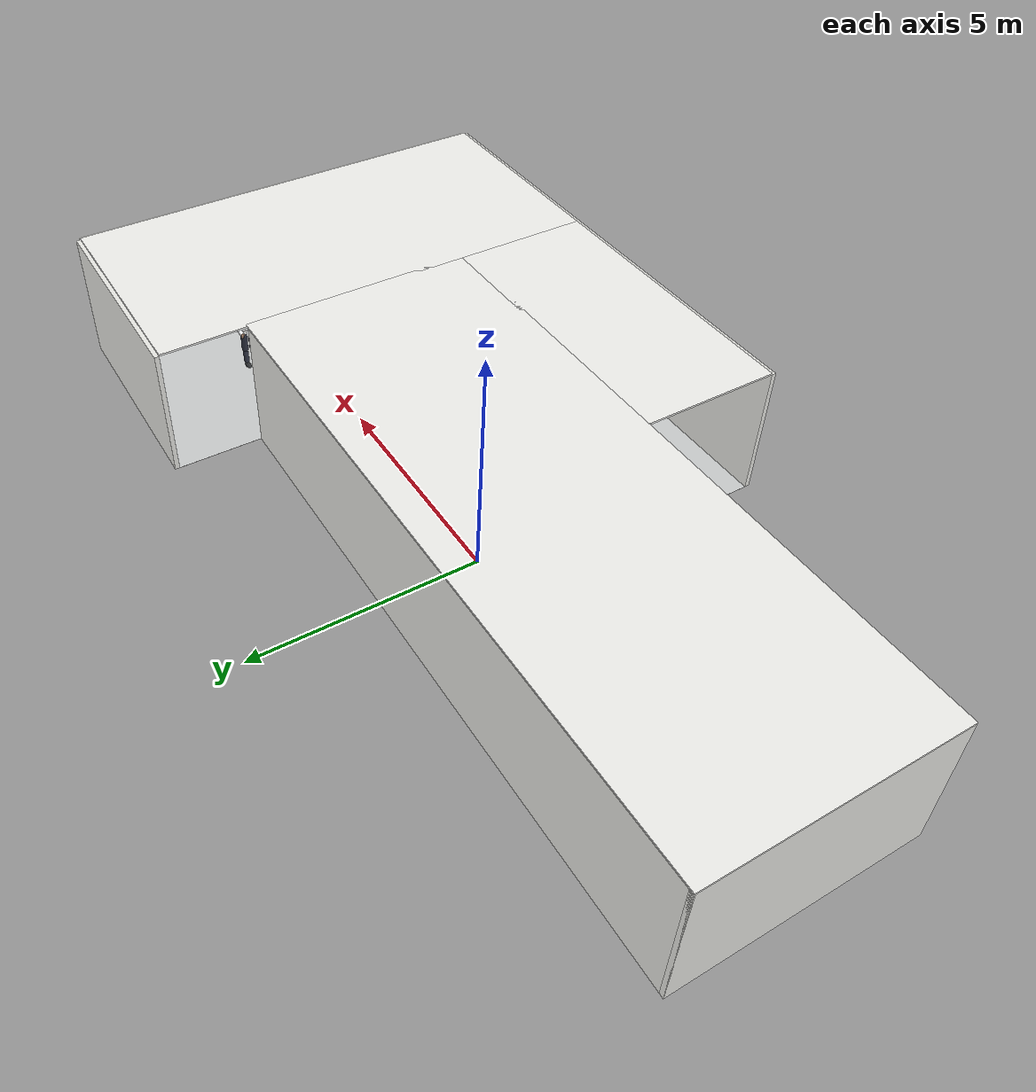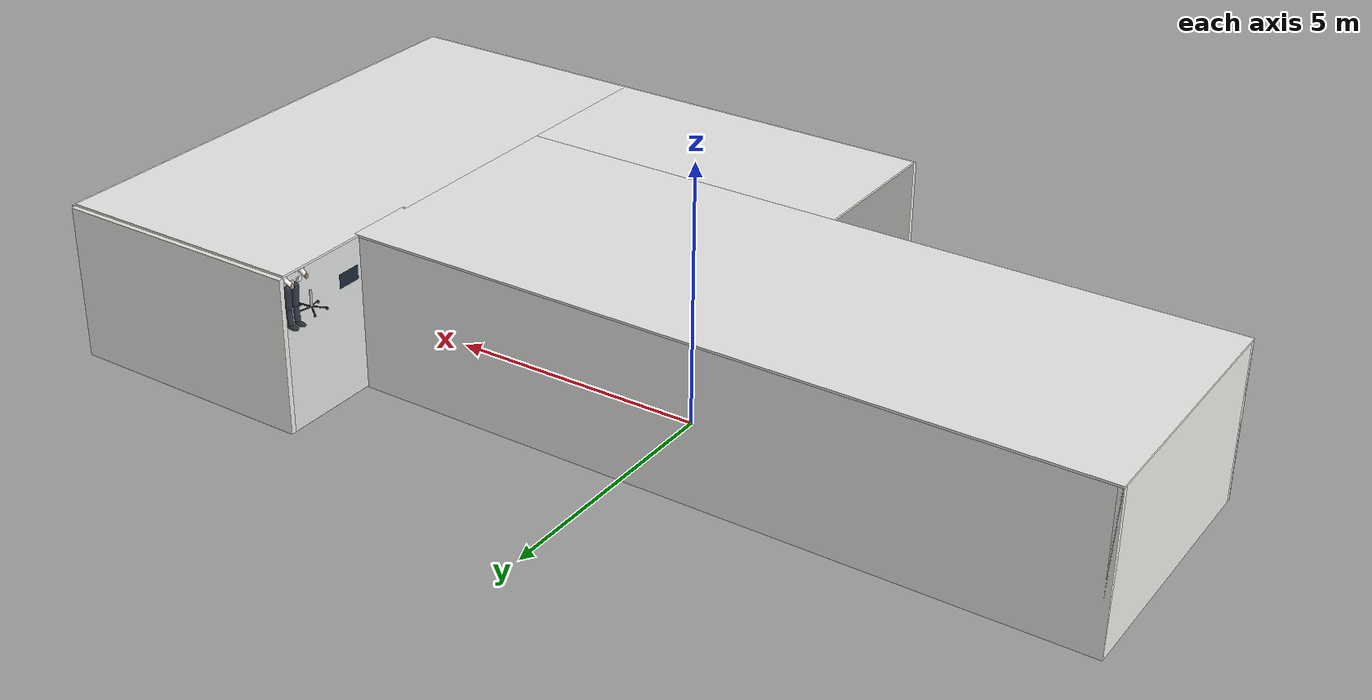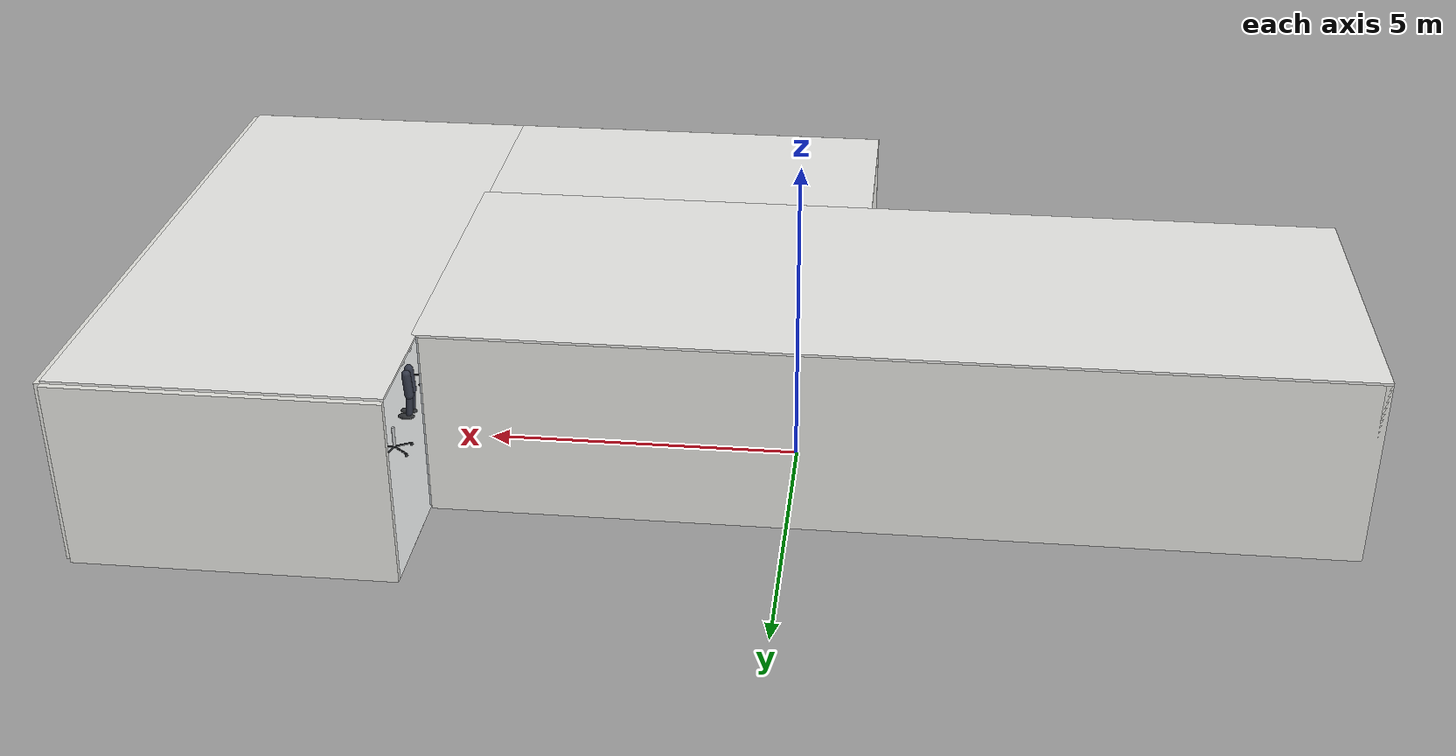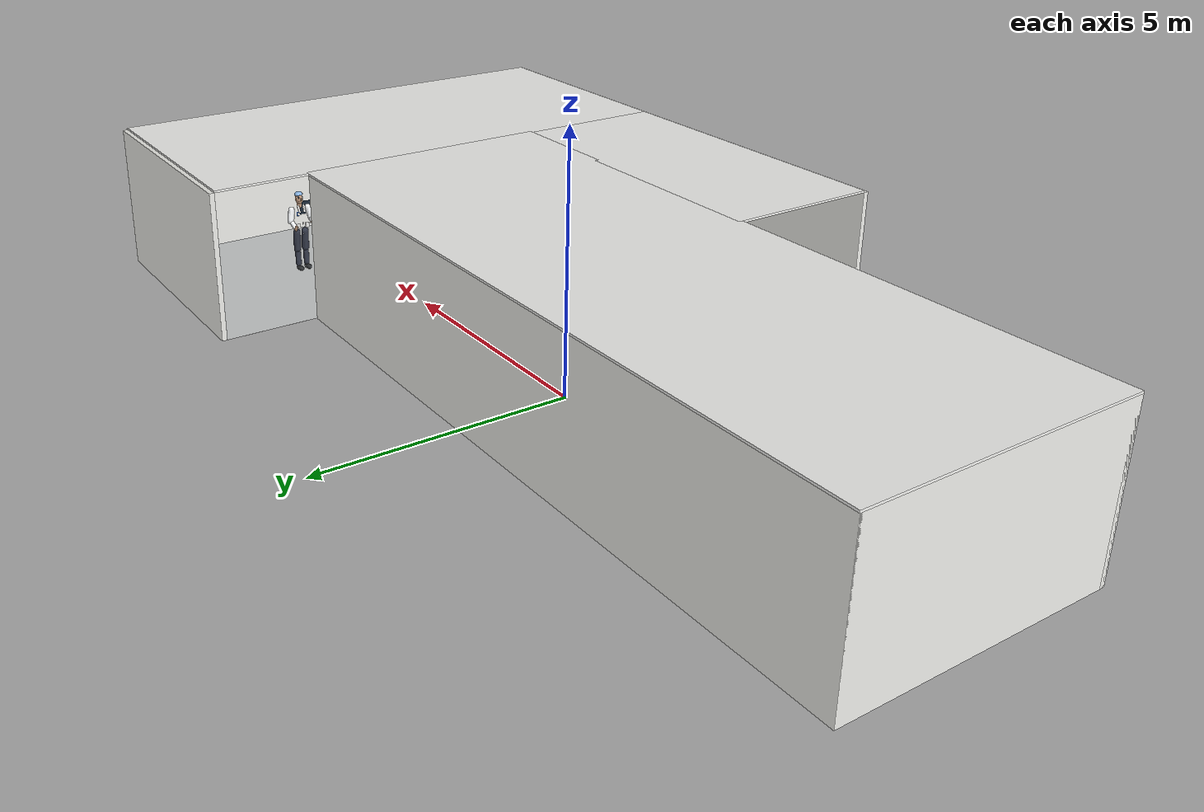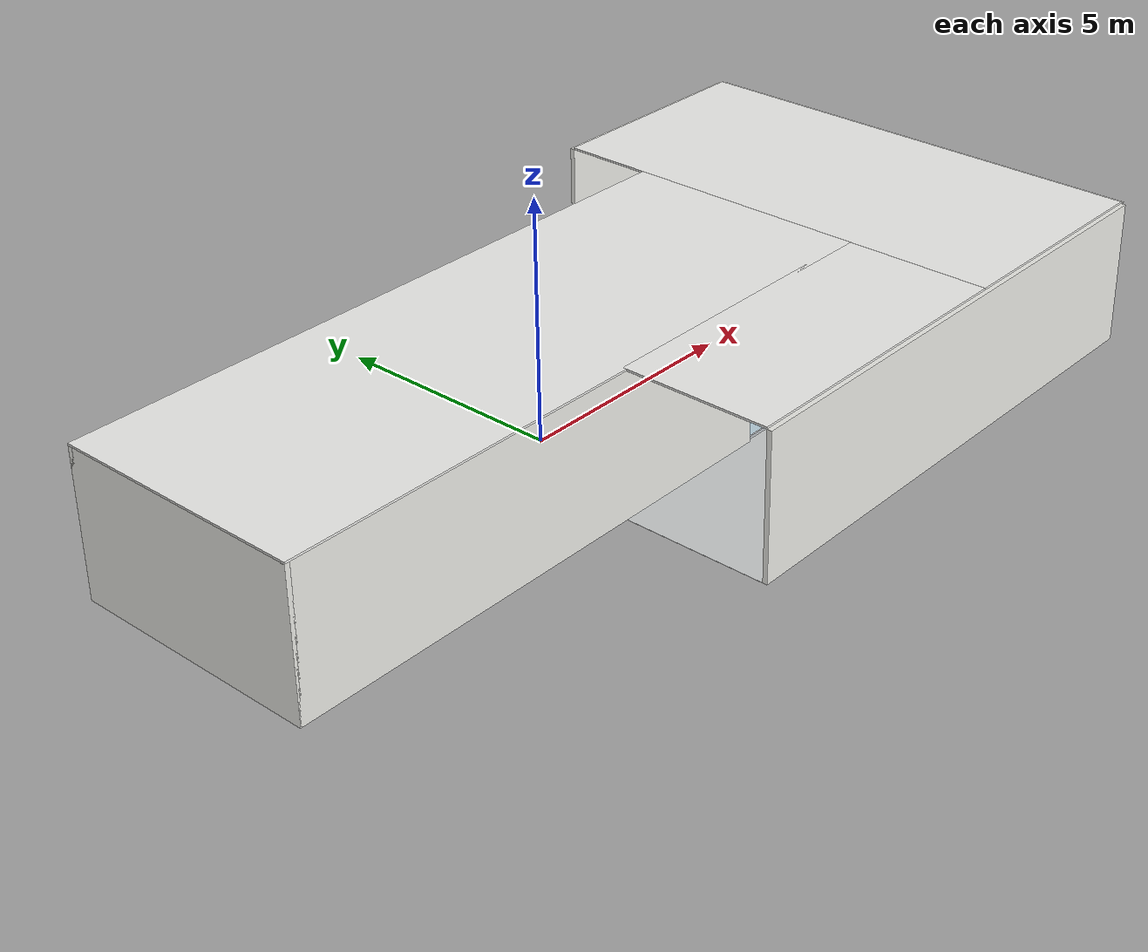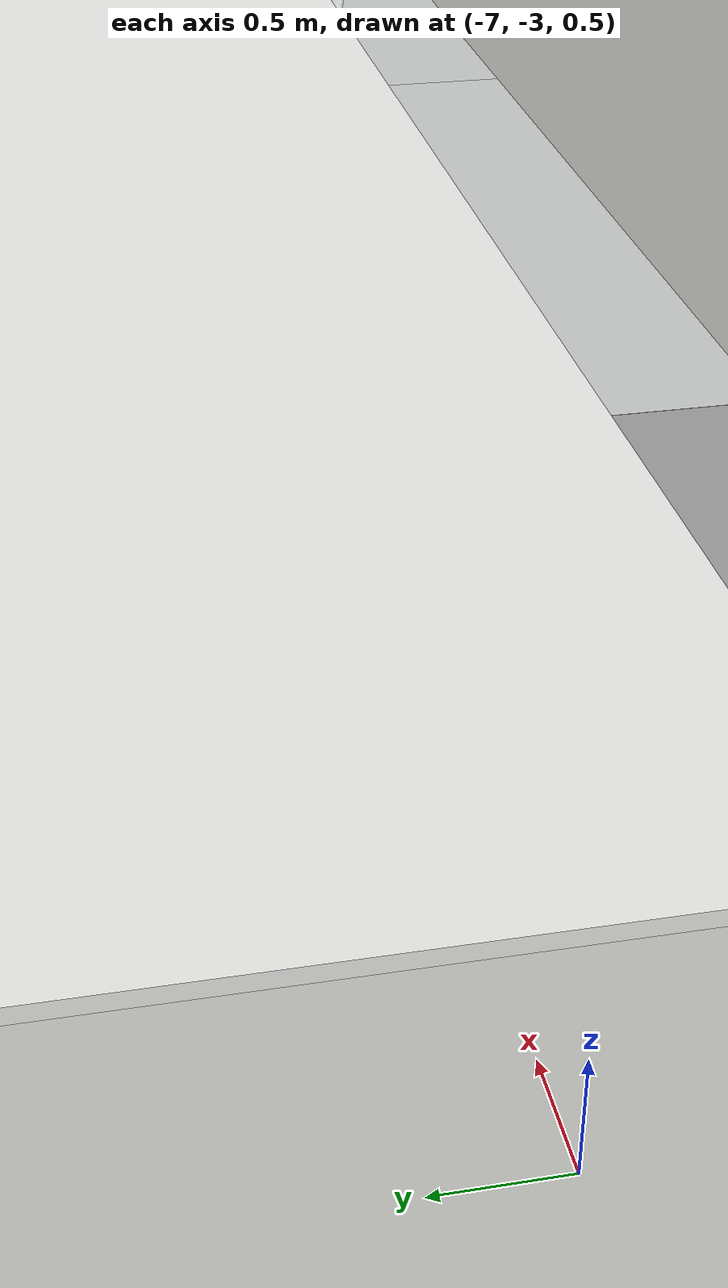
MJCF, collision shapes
<?xml version="1.0" encoding="utf-8"?>
<!-- Generated by scripts/generate_minihannover_open.py; do not edit by hand. -->
<mujoco model="lab_room_open">
  <asset>
    <material name="panel" rgba="0.93 0.93 0.91 1" specular="0.35" shininess="0.5" />
    <material name="panel_joint" rgba="0.74 0.75 0.75 1" />
    <material name="floor" rgba="0.80 0.81 0.81 1" specular="0.3" shininess="0.6" reflectance="0.12" />
    <material name="ceiling" rgba="0.95 0.95 0.94 1" specular="0.05" emission="0.45" />
    <material name="led" rgba="0.98 0.99 1.0 1" emission="1" />
    <material name="grille" rgba="0.55 0.57 0.58 1" />
    <material name="worktop" rgba="0.95 0.95 0.94 1" specular="0.8" shininess="0.9" reflectance="0.3" />
    <material name="white" rgba="0.94 0.94 0.93 1" specular="0.3" shininess="0.4" />
    <material name="white_matte" rgba="0.92 0.92 0.91 1" specular="0.1" />
    <material name="shelf" rgba="0.95 0.95 0.95 1" specular="0.4" shininess="0.5" />
    <material name="seam" rgba="0.80 0.81 0.81 1" />
    <material name="amber" rgba="0.55 0.24 0.04 0.82" specular="0.9" shininess="0.95" />
    <material name="sample_hdpe" rgba="0.92 0.92 0.91 1" specular="0.25" shininess="0.4" />
    <material name="sample_cap" rgba="0.93 0.93 0.91 1" specular="0.3" shininess="0.5" />
    <material name="glass" rgba="0.80 0.90 0.95 0.15" specular="0.9" shininess="0.95" reflectance="0.1" />
    <material name="glass_clear" rgba="0.88 0.94 0.97 0.30" specular="0.9" shininess="0.95" />
    <material name="frosted" rgba="0.96 0.97 0.98 0.75" />
    <material name="aluminium" rgba="0.76 0.78 0.80 1" specular="0.7" shininess="0.7" />
    <material name="steel" rgba="0.72 0.73 0.74 1" specular="0.8" shininess="0.6" />
    <material name="black" rgba="0.05 0.05 0.06 1" specular="0.9" shininess="0.9" />
    <material name="dark" rgba="0.18 0.19 0.20 1" />
    <material name="grey_device" rgba="0.80 0.81 0.80 1" specular="0.3" />
    <material name="screen" rgba="0.10 0.16 0.22 1" emission="0.25" />
    <material name="orange" rgba="0.93 0.40 0.10 1" />
    <material name="blue_hdpe" rgba="0.05 0.28 0.72 1" specular="0.15" />
    <material name="blue_motor" rgba="0.10 0.30 0.70 1" specular="0.5" />
    <material name="stripe_blue" rgba="0.10 0.35 0.75 1" />
    <material name="cream" rgba="0.93 0.91 0.84 1" specular="0.3" />
    <material name="hdpe_white" rgba="0.93 0.93 0.90 0.85" specular="0.2" />
    <material name="kraft" rgba="0.60 0.45 0.28 1" specular="0.05" />
    <material name="tape" rgba="0.65 0.48 0.28 1" specular="0.3" shininess="0.2" />
    <material name="cardboard" rgba="0.72 0.58 0.40 1" specular="0.05" />
    <material name="red_rack" rgba="0.75 0.10 0.08 1" specular="0.3" />
    <material name="navy_rack" rgba="0.10 0.14 0.32 1" specular="0.3" />
    <material name="galvanised" rgba="0.68 0.70 0.71 1" specular="0.5" />
    <material name="foil" rgba="0.80 0.80 0.82 1" specular="1" shininess="1" />
    <material name="paper" rgba="0.98 0.98 0.97 1" />
    <material name="bag" rgba="0.95 0.95 0.93 0.55" />
    <material name="red_cap" rgba="0.80 0.10 0.10 1" />
    <material name="coat" rgba="0.95 0.96 0.97 1" />
    <material name="skin" rgba="0.80 0.64 0.52 1" />
    <material name="cap_blue" rgba="0.55 0.72 0.90 1" />
    <material name="trousers" rgba="0.20 0.22 0.28 1" />
    <material name="desk" rgba="0.86 0.84 0.80 1" />
    <mesh name="pot" file="../lab_room/meshes/pot.obj" inertia="shell" />
    <mesh name="pot_small" file="../lab_room/meshes/pot_small.obj" inertia="shell" />
    <mesh name="lid" file="../lab_room/meshes/lid.obj" inertia="shell" />
    <mesh name="funnel" file="../lab_room/meshes/funnel.obj" inertia="shell" />
    <mesh name="beaker" file="../lab_room/meshes/beaker.obj" inertia="shell" />
    <mesh name="flask" file="../lab_room/meshes/flask.obj" inertia="shell" />
    <mesh name="cylinder" file="../lab_room/meshes/cylinder.obj" inertia="shell" />
    <mesh name="carboy" file="../lab_room/meshes/carboy.obj" inertia="shell" />
    <mesh name="wash_bottle" file="../lab_room/meshes/wash_bottle.obj" inertia="shell" />
    <mesh name="hood" file="../lab_room/meshes/hood.obj" inertia="shell" />
    <mesh name="drum" file="../lab_room/meshes/drum.obj" inertia="shell" />
    <mesh name="bin" file="../lab_room/meshes/bin.obj" inertia="shell" />
    <mesh name="bin_lid" file="../lab_room/meshes/bin_lid.obj" inertia="shell" />
    <texture name="stock_SMP-0010" type="2d" file="../labelled_bottles/textures/shelf/SMP-0010.png" />
    <material name="stock_SMP-0010" texture="stock_SMP-0010" specular="0.05" />
    <texture name="stock_SMP-0015" type="2d" file="../labelled_bottles/textures/shelf/SMP-0015.png" />
    <material name="stock_SMP-0015" texture="stock_SMP-0015" specular="0.05" />
    <texture name="stock_SMP-0020" type="2d" file="../labelled_bottles/textures/shelf/SMP-0020.png" />
    <material name="stock_SMP-0020" texture="stock_SMP-0020" specular="0.05" />
    <texture name="stock_SMP-0025" type="2d" file="../labelled_bottles/textures/shelf/SMP-0025.png" />
    <material name="stock_SMP-0025" texture="stock_SMP-0025" specular="0.05" />
    <texture name="stock_SMP-0035" type="2d" file="../labelled_bottles/textures/shelf/SMP-0035.png" />
    <material name="stock_SMP-0035" texture="stock_SMP-0035" specular="0.05" />
    <texture name="stock_SMP-0040" type="2d" file="../labelled_bottles/textures/shelf/SMP-0040.png" />
    <material name="stock_SMP-0040" texture="stock_SMP-0040" specular="0.05" />
    <texture name="stock_SMP-0045" type="2d" file="../labelled_bottles/textures/shelf/SMP-0045.png" />
    <material name="stock_SMP-0045" texture="stock_SMP-0045" specular="0.05" />
    <texture name="stock_SMP-0050" type="2d" file="../labelled_bottles/textures/shelf/SMP-0050.png" />
    <material name="stock_SMP-0050" texture="stock_SMP-0050" specular="0.05" />
    <texture name="stock_SMP-0055" type="2d" file="../labelled_bottles/textures/shelf/SMP-0055.png" />
    <material name="stock_SMP-0055" texture="stock_SMP-0055" specular="0.05" />
    <texture name="stock_SMP-0060" type="2d" file="../labelled_bottles/textures/shelf/SMP-0060.png" />
    <material name="stock_SMP-0060" texture="stock_SMP-0060" specular="0.05" />
    <texture name="stock_SMP-0065" type="2d" file="../labelled_bottles/textures/shelf/SMP-0065.png" />
    <material name="stock_SMP-0065" texture="stock_SMP-0065" specular="0.05" />
    <texture name="stock_SMP-0070" type="2d" file="../labelled_bottles/textures/shelf/SMP-0070.png" />
    <material name="stock_SMP-0070" texture="stock_SMP-0070" specular="0.05" />
    <texture name="stock_SMP-0075" type="2d" file="../labelled_bottles/textures/shelf/SMP-0075.png" />
    <material name="stock_SMP-0075" texture="stock_SMP-0075" specular="0.05" />
    <texture name="stock_SMP-0080" type="2d" file="../labelled_bottles/textures/shelf/SMP-0080.png" />
    <material name="stock_SMP-0080" texture="stock_SMP-0080" specular="0.05" />
    <texture name="stock_SMP-0085" type="2d" file="../labelled_bottles/textures/shelf/SMP-0085.png" />
    <material name="stock_SMP-0085" texture="stock_SMP-0085" specular="0.05" />
    <texture name="stock_SMP-0090" type="2d" file="../labelled_bottles/textures/shelf/SMP-0090.png" />
    <material name="stock_SMP-0090" texture="stock_SMP-0090" specular="0.05" />
    <texture name="stock_SMP-0095" type="2d" file="../labelled_bottles/textures/shelf/SMP-0095.png" />
    <material name="stock_SMP-0095" texture="stock_SMP-0095" specular="0.05" />
    <texture name="stock_SMP-0100" type="2d" file="../labelled_bottles/textures/shelf/SMP-0100.png" />
    <material name="stock_SMP-0100" texture="stock_SMP-0100" specular="0.05" />
    <texture name="stock_SMP-0135" type="2d" file="../labelled_bottles/textures/shelf/SMP-0135.png" />
    <material name="stock_SMP-0135" texture="stock_SMP-0135" specular="0.05" />
    <texture name="stock_SMP-0140" type="2d" file="../labelled_bottles/textures/shelf/SMP-0140.png" />
    <material name="stock_SMP-0140" texture="stock_SMP-0140" specular="0.05" />
    <texture name="stock_SMP-0145" type="2d" file="../labelled_bottles/textures/shelf/SMP-0145.png" />
    <material name="stock_SMP-0145" texture="stock_SMP-0145" specular="0.05" />
    <texture name="stock_SMP-0150" type="2d" file="../labelled_bottles/textures/shelf/SMP-0150.png" />
    <material name="stock_SMP-0150" texture="stock_SMP-0150" specular="0.05" />
    <texture name="stock_SMP-0155" type="2d" file="../labelled_bottles/textures/shelf/SMP-0155.png" />
    <material name="stock_SMP-0155" texture="stock_SMP-0155" specular="0.05" />
    <texture name="stock_SMP-0160" type="2d" file="../labelled_bottles/textures/shelf/SMP-0160.png" />
    <material name="stock_SMP-0160" texture="stock_SMP-0160" specular="0.05" />
    <texture name="stock_SMP-0165" type="2d" file="../labelled_bottles/textures/shelf/SMP-0165.png" />
    <material name="stock_SMP-0165" texture="stock_SMP-0165" specular="0.05" />
    <texture name="stock_SMP-0170" type="2d" file="../labelled_bottles/textures/shelf/SMP-0170.png" />
    <material name="stock_SMP-0170" texture="stock_SMP-0170" specular="0.05" />
    <texture name="stock_SMP-0175" type="2d" file="../labelled_bottles/textures/shelf/SMP-0175.png" />
    <material name="stock_SMP-0175" texture="stock_SMP-0175" specular="0.05" />
    <texture name="stock_SMP-0180" type="2d" file="../labelled_bottles/textures/shelf/SMP-0180.png" />
    <material name="stock_SMP-0180" texture="stock_SMP-0180" specular="0.05" />
    <texture name="stock_SMP-0185" type="2d" file="../labelled_bottles/textures/shelf/SMP-0185.png" />
    <material name="stock_SMP-0185" texture="stock_SMP-0185" specular="0.05" />
    <texture name="stock_SMP-0190" type="2d" file="../labelled_bottles/textures/shelf/SMP-0190.png" />
    <material name="stock_SMP-0190" texture="stock_SMP-0190" specular="0.05" />
    <texture name="stock_SMP-0195" type="2d" file="../labelled_bottles/textures/shelf/SMP-0195.png" />
    <material name="stock_SMP-0195" texture="stock_SMP-0195" specular="0.05" />
    <texture name="stock_SMP-0200" type="2d" file="../labelled_bottles/textures/shelf/SMP-0200.png" />
    <material name="stock_SMP-0200" texture="stock_SMP-0200" specular="0.05" />
    <texture name="stock_SMP-0004" type="2d" file="../labelled_bottles/textures/shelf/SMP-0004.png" />
    <material name="stock_SMP-0004" texture="stock_SMP-0004" specular="0.05" />
    <texture name="stock_SMP-0014" type="2d" file="../labelled_bottles/textures/shelf/SMP-0014.png" />
    <material name="stock_SMP-0014" texture="stock_SMP-0014" specular="0.05" />
    <texture name="stock_SMP-0019" type="2d" file="../labelled_bottles/textures/shelf/SMP-0019.png" />
    <material name="stock_SMP-0019" texture="stock_SMP-0019" specular="0.05" />
    <texture name="stock_SMP-0024" type="2d" file="../labelled_bottles/textures/shelf/SMP-0024.png" />
    <material name="stock_SMP-0024" texture="stock_SMP-0024" specular="0.05" />
    <texture name="stock_SMP-0029" type="2d" file="../labelled_bottles/textures/shelf/SMP-0029.png" />
    <material name="stock_SMP-0029" texture="stock_SMP-0029" specular="0.05" />
    <texture name="stock_SMP-0039" type="2d" file="../labelled_bottles/textures/shelf/SMP-0039.png" />
    <material name="stock_SMP-0039" texture="stock_SMP-0039" specular="0.05" />
    <texture name="stock_SMP-0044" type="2d" file="../labelled_bottles/textures/shelf/SMP-0044.png" />
    <material name="stock_SMP-0044" texture="stock_SMP-0044" specular="0.05" />
    <texture name="stock_SMP-0049" type="2d" file="../labelled_bottles/textures/shelf/SMP-0049.png" />
    <material name="stock_SMP-0049" texture="stock_SMP-0049" specular="0.05" />
    <texture name="stock_SMP-0054" type="2d" file="../labelled_bottles/textures/shelf/SMP-0054.png" />
    <material name="stock_SMP-0054" texture="stock_SMP-0054" specular="0.05" />
    <texture name="stock_SMP-0059" type="2d" file="../labelled_bottles/textures/shelf/SMP-0059.png" />
    <material name="stock_SMP-0059" texture="stock_SMP-0059" specular="0.05" />
    <texture name="stock_SMP-0064" type="2d" file="../labelled_bottles/textures/shelf/SMP-0064.png" />
    <material name="stock_SMP-0064" texture="stock_SMP-0064" specular="0.05" />
    <texture name="stock_SMP-0069" type="2d" file="../labelled_bottles/textures/shelf/SMP-0069.png" />
    <material name="stock_SMP-0069" texture="stock_SMP-0069" specular="0.05" />
    <texture name="stock_SMP-0074" type="2d" file="../labelled_bottles/textures/shelf/SMP-0074.png" />
    <material name="stock_SMP-0074" texture="stock_SMP-0074" specular="0.05" />
    <texture name="stock_SMP-0079" type="2d" file="../labelled_bottles/textures/shelf/SMP-0079.png" />
    <material name="stock_SMP-0079" texture="stock_SMP-0079" specular="0.05" />
    <texture name="stock_SMP-0084" type="2d" file="../labelled_bottles/textures/shelf/SMP-0084.png" />
    <material name="stock_SMP-0084" texture="stock_SMP-0084" specular="0.05" />
    <texture name="stock_SMP-0089" type="2d" file="../labelled_bottles/textures/shelf/SMP-0089.png" />
    <material name="stock_SMP-0089" texture="stock_SMP-0089" specular="0.05" />
    <texture name="stock_SMP-0094" type="2d" file="../labelled_bottles/textures/shelf/SMP-0094.png" />
    <material name="stock_SMP-0094" texture="stock_SMP-0094" specular="0.05" />
    <texture name="stock_SMP-0099" type="2d" file="../labelled_bottles/textures/shelf/SMP-0099.png" />
    <material name="stock_SMP-0099" texture="stock_SMP-0099" specular="0.05" />
    <texture name="stock_SMP-0104" type="2d" file="../labelled_bottles/textures/shelf/SMP-0104.png" />
    <material name="stock_SMP-0104" texture="stock_SMP-0104" specular="0.05" />
    <texture name="stock_SMP-0109" type="2d" file="../labelled_bottles/textures/shelf/SMP-0109.png" />
    <material name="stock_SMP-0109" texture="stock_SMP-0109" specular="0.05" />
    <texture name="stock_SMP-0114" type="2d" file="../labelled_bottles/textures/shelf/SMP-0114.png" />
    <material name="stock_SMP-0114" texture="stock_SMP-0114" specular="0.05" />
    <texture name="stock_SMP-0119" type="2d" file="../labelled_bottles/textures/shelf/SMP-0119.png" />
    <material name="stock_SMP-0119" texture="stock_SMP-0119" specular="0.05" />
    <texture name="stock_SMP-0124" type="2d" file="../labelled_bottles/textures/shelf/SMP-0124.png" />
    <material name="stock_SMP-0124" texture="stock_SMP-0124" specular="0.05" />
    <texture name="stock_SMP-0129" type="2d" file="../labelled_bottles/textures/shelf/SMP-0129.png" />
    <material name="stock_SMP-0129" texture="stock_SMP-0129" specular="0.05" />
    <texture name="stock_SMP-0134" type="2d" file="../labelled_bottles/textures/shelf/SMP-0134.png" />
    <material name="stock_SMP-0134" texture="stock_SMP-0134" specular="0.05" />
    <texture name="stock_SMP-0139" type="2d" file="../labelled_bottles/textures/shelf/SMP-0139.png" />
    <material name="stock_SMP-0139" texture="stock_SMP-0139" specular="0.05" />
    <texture name="stock_SMP-0144" type="2d" file="../labelled_bottles/textures/shelf/SMP-0144.png" />
    <material name="stock_SMP-0144" texture="stock_SMP-0144" specular="0.05" />
    <texture name="stock_SMP-0149" type="2d" file="../labelled_bottles/textures/shelf/SMP-0149.png" />
    <material name="stock_SMP-0149" texture="stock_SMP-0149" specular="0.05" />
    <texture name="stock_SMP-0154" type="2d" file="../labelled_bottles/textures/shelf/SMP-0154.png" />
    <material name="stock_SMP-0154" texture="stock_SMP-0154" specular="0.05" />
    <texture name="stock_SMP-0159" type="2d" file="../labelled_bottles/textures/shelf/SMP-0159.png" />
    <material name="stock_SMP-0159" texture="stock_SMP-0159" specular="0.05" />
    <texture name="stock_SMP-0164" type="2d" file="../labelled_bottles/textures/shelf/SMP-0164.png" />
    <material name="stock_SMP-0164" texture="stock_SMP-0164" specular="0.05" />
    <texture name="stock_SMP-0169" type="2d" file="../labelled_bottles/textures/shelf/SMP-0169.png" />
    <material name="stock_SMP-0169" texture="stock_SMP-0169" specular="0.05" />
    <texture name="stock_SMP-0174" type="2d" file="../labelled_bottles/textures/shelf/SMP-0174.png" />
    <material name="stock_SMP-0174" texture="stock_SMP-0174" specular="0.05" />
    <texture name="stock_SMP-0179" type="2d" file="../labelled_bottles/textures/shelf/SMP-0179.png" />
    <material name="stock_SMP-0179" texture="stock_SMP-0179" specular="0.05" />
    <texture name="stock_SMP-0184" type="2d" file="../labelled_bottles/textures/shelf/SMP-0184.png" />
    <material name="stock_SMP-0184" texture="stock_SMP-0184" specular="0.05" />
    <texture name="stock_SMP-0189" type="2d" file="../labelled_bottles/textures/shelf/SMP-0189.png" />
    <material name="stock_SMP-0189" texture="stock_SMP-0189" specular="0.05" />
    <texture name="stock_SMP-0194" type="2d" file="../labelled_bottles/textures/shelf/SMP-0194.png" />
    <material name="stock_SMP-0194" texture="stock_SMP-0194" specular="0.05" />
    <texture name="stock_SMP-0199" type="2d" file="../labelled_bottles/textures/shelf/SMP-0199.png" />
    <material name="stock_SMP-0199" texture="stock_SMP-0199" specular="0.05" />
    <texture name="stock_SMP-0003" type="2d" file="../labelled_bottles/textures/shelf/SMP-0003.png" />
    <material name="stock_SMP-0003" texture="stock_SMP-0003" specular="0.05" />
    <texture name="stock_SMP-0008" type="2d" file="../labelled_bottles/textures/shelf/SMP-0008.png" />
    <material name="stock_SMP-0008" texture="stock_SMP-0008" specular="0.05" />
    <texture name="stock_SMP-0018" type="2d" file="../labelled_bottles/textures/shelf/SMP-0018.png" />
    <material name="stock_SMP-0018" texture="stock_SMP-0018" specular="0.05" />
    <texture name="stock_SMP-0023" type="2d" file="../labelled_bottles/textures/shelf/SMP-0023.png" />
    <material name="stock_SMP-0023" texture="stock_SMP-0023" specular="0.05" />
    <texture name="stock_SMP-0028" type="2d" file="../labelled_bottles/textures/shelf/SMP-0028.png" />
    <material name="stock_SMP-0028" texture="stock_SMP-0028" specular="0.05" />
    <texture name="stock_SMP-0033" type="2d" file="../labelled_bottles/textures/shelf/SMP-0033.png" />
    <material name="stock_SMP-0033" texture="stock_SMP-0033" specular="0.05" />
    <texture name="stock_SMP-0038" type="2d" file="../labelled_bottles/textures/shelf/SMP-0038.png" />
    <material name="stock_SMP-0038" texture="stock_SMP-0038" specular="0.05" />
    <texture name="stock_SMP-0043" type="2d" file="../labelled_bottles/textures/shelf/SMP-0043.png" />
    <material name="stock_SMP-0043" texture="stock_SMP-0043" specular="0.05" />
    <texture name="stock_SMP-0048" type="2d" file="../labelled_bottles/textures/shelf/SMP-0048.png" />
    <material name="stock_SMP-0048" texture="stock_SMP-0048" specular="0.05" />
    <texture name="stock_SMP-0053" type="2d" file="../labelled_bottles/textures/shelf/SMP-0053.png" />
    <material name="stock_SMP-0053" texture="stock_SMP-0053" specular="0.05" />
    <texture name="stock_SMP-0058" type="2d" file="../labelled_bottles/textures/shelf/SMP-0058.png" />
    <material name="stock_SMP-0058" texture="stock_SMP-0058" specular="0.05" />
    <texture name="stock_SMP-0063" type="2d" file="../labelled_bottles/textures/shelf/SMP-0063.png" />
    <material name="stock_SMP-0063" texture="stock_SMP-0063" specular="0.05" />
    <texture name="stock_SMP-0068" type="2d" file="../labelled_bottles/textures/shelf/SMP-0068.png" />
    <material name="stock_SMP-0068" texture="stock_SMP-0068" specular="0.05" />
    <texture name="stock_SMP-0073" type="2d" file="../labelled_bottles/textures/shelf/SMP-0073.png" />
    <material name="stock_SMP-0073" texture="stock_SMP-0073" specular="0.05" />
    <texture name="stock_SMP-0078" type="2d" file="../labelled_bottles/textures/shelf/SMP-0078.png" />
    <material name="stock_SMP-0078" texture="stock_SMP-0078" specular="0.05" />
    <texture name="stock_SMP-0083" type="2d" file="../labelled_bottles/textures/shelf/SMP-0083.png" />
    <material name="stock_SMP-0083" texture="stock_SMP-0083" specular="0.05" />
    <texture name="stock_SMP-0088" type="2d" file="../labelled_bottles/textures/shelf/SMP-0088.png" />
    <material name="stock_SMP-0088" texture="stock_SMP-0088" specular="0.05" />
    <texture name="stock_SMP-0093" type="2d" file="../labelled_bottles/textures/shelf/SMP-0093.png" />
    <material name="stock_SMP-0093" texture="stock_SMP-0093" specular="0.05" />
    <texture name="stock_SMP-0098" type="2d" file="../labelled_bottles/textures/shelf/SMP-0098.png" />
    <material name="stock_SMP-0098" texture="stock_SMP-0098" specular="0.05" />
    <texture name="stock_SMP-0103" type="2d" file="../labelled_bottles/textures/shelf/SMP-0103.png" />
    <material name="stock_SMP-0103" texture="stock_SMP-0103" specular="0.05" />
    <texture name="stock_SMP-0108" type="2d" file="../labelled_bottles/textures/shelf/SMP-0108.png" />
    <material name="stock_SMP-0108" texture="stock_SMP-0108" specular="0.05" />
    <texture name="stock_SMP-0113" type="2d" file="../labelled_bottles/textures/shelf/SMP-0113.png" />
    <material name="stock_SMP-0113" texture="stock_SMP-0113" specular="0.05" />
    <texture name="stock_SMP-0118" type="2d" file="../labelled_bottles/textures/shelf/SMP-0118.png" />
    <material name="stock_SMP-0118" texture="stock_SMP-0118" specular="0.05" />
    <texture name="stock_SMP-0123" type="2d" file="../labelled_bottles/textures/shelf/SMP-0123.png" />
    <material name="stock_SMP-0123" texture="stock_SMP-0123" specular="0.05" />
    <texture name="stock_SMP-0128" type="2d" file="../labelled_bottles/textures/shelf/SMP-0128.png" />
    <material name="stock_SMP-0128" texture="stock_SMP-0128" specular="0.05" />
    <texture name="stock_SMP-0133" type="2d" file="../labelled_bottles/textures/shelf/SMP-0133.png" />
    <material name="stock_SMP-0133" texture="stock_SMP-0133" specular="0.05" />
    <texture name="stock_SMP-0138" type="2d" file="../labelled_bottles/textures/shelf/SMP-0138.png" />
    <material name="stock_SMP-0138" texture="stock_SMP-0138" specular="0.05" />
    <texture name="stock_SMP-0143" type="2d" file="../labelled_bottles/textures/shelf/SMP-0143.png" />
    <material name="stock_SMP-0143" texture="stock_SMP-0143" specular="0.05" />
    <texture name="stock_SMP-0148" type="2d" file="../labelled_bottles/textures/shelf/SMP-0148.png" />
    <material name="stock_SMP-0148" texture="stock_SMP-0148" specular="0.05" />
    <texture name="stock_SMP-0153" type="2d" file="../labelled_bottles/textures/shelf/SMP-0153.png" />
    <material name="stock_SMP-0153" texture="stock_SMP-0153" specular="0.05" />
    <texture name="stock_SMP-0158" type="2d" file="../labelled_bottles/textures/shelf/SMP-0158.png" />
    <material name="stock_SMP-0158" texture="stock_SMP-0158" specular="0.05" />
    <texture name="stock_SMP-0163" type="2d" file="../labelled_bottles/textures/shelf/SMP-0163.png" />
    <material name="stock_SMP-0163" texture="stock_SMP-0163" specular="0.05" />
    <texture name="stock_SMP-0168" type="2d" file="../labelled_bottles/textures/shelf/SMP-0168.png" />
    <material name="stock_SMP-0168" texture="stock_SMP-0168" specular="0.05" />
    <texture name="stock_SMP-0173" type="2d" file="../labelled_bottles/textures/shelf/SMP-0173.png" />
    <material name="stock_SMP-0173" texture="stock_SMP-0173" specular="0.05" />
    <texture name="stock_SMP-0178" type="2d" file="../labelled_bottles/textures/shelf/SMP-0178.png" />
    <material name="stock_SMP-0178" texture="stock_SMP-0178" specular="0.05" />
    <texture name="stock_SMP-0183" type="2d" file="../labelled_bottles/textures/shelf/SMP-0183.png" />
    <material name="stock_SMP-0183" texture="stock_SMP-0183" specular="0.05" />
    <texture name="stock_SMP-0188" type="2d" file="../labelled_bottles/textures/shelf/SMP-0188.png" />
    <material name="stock_SMP-0188" texture="stock_SMP-0188" specular="0.05" />
    <texture name="stock_SMP-0193" type="2d" file="../labelled_bottles/textures/shelf/SMP-0193.png" />
    <material name="stock_SMP-0193" texture="stock_SMP-0193" specular="0.05" />
    <texture name="stock_SMP-0198" type="2d" file="../labelled_bottles/textures/shelf/SMP-0198.png" />
    <material name="stock_SMP-0198" texture="stock_SMP-0198" specular="0.05" />
    <texture name="stock_SMP-0002" type="2d" file="../labelled_bottles/textures/shelf/SMP-0002.png" />
    <material name="stock_SMP-0002" texture="stock_SMP-0002" specular="0.05" />
    <texture name="stock_SMP-0007" type="2d" file="../labelled_bottles/textures/shelf/SMP-0007.png" />
    <material name="stock_SMP-0007" texture="stock_SMP-0007" specular="0.05" />
    <texture name="stock_SMP-0012" type="2d" file="../labelled_bottles/textures/shelf/SMP-0012.png" />
    <material name="stock_SMP-0012" texture="stock_SMP-0012" specular="0.05" />
    <texture name="stock_SMP-0022" type="2d" file="../labelled_bottles/textures/shelf/SMP-0022.png" />
    <material name="stock_SMP-0022" texture="stock_SMP-0022" specular="0.05" />
    <texture name="stock_SMP-0027" type="2d" file="../labelled_bottles/textures/shelf/SMP-0027.png" />
    <material name="stock_SMP-0027" texture="stock_SMP-0027" specular="0.05" />
    <texture name="stock_SMP-0032" type="2d" file="../labelled_bottles/textures/shelf/SMP-0032.png" />
    <material name="stock_SMP-0032" texture="stock_SMP-0032" specular="0.05" />
    <texture name="stock_SMP-0037" type="2d" file="../labelled_bottles/textures/shelf/SMP-0037.png" />
    <material name="stock_SMP-0037" texture="stock_SMP-0037" specular="0.05" />
    <texture name="stock_SMP-0042" type="2d" file="../labelled_bottles/textures/shelf/SMP-0042.png" />
    <material name="stock_SMP-0042" texture="stock_SMP-0042" specular="0.05" />
    <texture name="stock_SMP-0047" type="2d" file="../labelled_bottles/textures/shelf/SMP-0047.png" />
    <material name="stock_SMP-0047" texture="stock_SMP-0047" specular="0.05" />
    <texture name="stock_SMP-0052" type="2d" file="../labelled_bottles/textures/shelf/SMP-0052.png" />
    <material name="stock_SMP-0052" texture="stock_SMP-0052" specular="0.05" />
    <texture name="stock_SMP-0057" type="2d" file="../labelled_bottles/textures/shelf/SMP-0057.png" />
    <material name="stock_SMP-0057" texture="stock_SMP-0057" specular="0.05" />
    <texture name="stock_SMP-0062" type="2d" file="../labelled_bottles/textures/shelf/SMP-0062.png" />
    <material name="stock_SMP-0062" texture="stock_SMP-0062" specular="0.05" />
    <texture name="stock_SMP-0067" type="2d" file="../labelled_bottles/textures/shelf/SMP-0067.png" />
    <material name="stock_SMP-0067" texture="stock_SMP-0067" specular="0.05" />
    <texture name="stock_SMP-0072" type="2d" file="../labelled_bottles/textures/shelf/SMP-0072.png" />
    <material name="stock_SMP-0072" texture="stock_SMP-0072" specular="0.05" />
    <texture name="stock_SMP-0077" type="2d" file="../labelled_bottles/textures/shelf/SMP-0077.png" />
    <material name="stock_SMP-0077" texture="stock_SMP-0077" specular="0.05" />
    <texture name="stock_SMP-0082" type="2d" file="../labelled_bottles/textures/shelf/SMP-0082.png" />
    <material name="stock_SMP-0082" texture="stock_SMP-0082" specular="0.05" />
    <texture name="stock_SMP-0087" type="2d" file="../labelled_bottles/textures/shelf/SMP-0087.png" />
    <material name="stock_SMP-0087" texture="stock_SMP-0087" specular="0.05" />
    <texture name="stock_SMP-0092" type="2d" file="../labelled_bottles/textures/shelf/SMP-0092.png" />
    <material name="stock_SMP-0092" texture="stock_SMP-0092" specular="0.05" />
    <texture name="stock_SMP-0097" type="2d" file="../labelled_bottles/textures/shelf/SMP-0097.png" />
    <material name="stock_SMP-0097" texture="stock_SMP-0097" specular="0.05" />
    <texture name="stock_SMP-0102" type="2d" file="../labelled_bottles/textures/shelf/SMP-0102.png" />
    <material name="stock_SMP-0102" texture="stock_SMP-0102" specular="0.05" />
    <texture name="stock_SMP-0107" type="2d" file="../labelled_bottles/textures/shelf/SMP-0107.png" />
    <material name="stock_SMP-0107" texture="stock_SMP-0107" specular="0.05" />
    <texture name="stock_SMP-0112" type="2d" file="../labelled_bottles/textures/shelf/SMP-0112.png" />
    <material name="stock_SMP-0112" texture="stock_SMP-0112" specular="0.05" />
    <texture name="stock_SMP-0117" type="2d" file="../labelled_bottles/textures/shelf/SMP-0117.png" />
    <material name="stock_SMP-0117" texture="stock_SMP-0117" specular="0.05" />
    <texture name="stock_SMP-0122" type="2d" file="../labelled_bottles/textures/shelf/SMP-0122.png" />
    <material name="stock_SMP-0122" texture="stock_SMP-0122" specular="0.05" />
    <texture name="stock_SMP-0127" type="2d" file="../labelled_bottles/textures/shelf/SMP-0127.png" />
    <material name="stock_SMP-0127" texture="stock_SMP-0127" specular="0.05" />
    <texture name="stock_SMP-0132" type="2d" file="../labelled_bottles/textures/shelf/SMP-0132.png" />
    <material name="stock_SMP-0132" texture="stock_SMP-0132" specular="0.05" />
    <texture name="stock_SMP-0137" type="2d" file="../labelled_bottles/textures/shelf/SMP-0137.png" />
    <material name="stock_SMP-0137" texture="stock_SMP-0137" specular="0.05" />
    <texture name="stock_SMP-0142" type="2d" file="../labelled_bottles/textures/shelf/SMP-0142.png" />
    <material name="stock_SMP-0142" texture="stock_SMP-0142" specular="0.05" />
    <texture name="stock_SMP-0147" type="2d" file="../labelled_bottles/textures/shelf/SMP-0147.png" />
    <material name="stock_SMP-0147" texture="stock_SMP-0147" specular="0.05" />
    <texture name="stock_SMP-0152" type="2d" file="../labelled_bottles/textures/shelf/SMP-0152.png" />
    <material name="stock_SMP-0152" texture="stock_SMP-0152" specular="0.05" />
    <texture name="stock_SMP-0157" type="2d" file="../labelled_bottles/textures/shelf/SMP-0157.png" />
    <material name="stock_SMP-0157" texture="stock_SMP-0157" specular="0.05" />
    <texture name="stock_SMP-0162" type="2d" file="../labelled_bottles/textures/shelf/SMP-0162.png" />
    <material name="stock_SMP-0162" texture="stock_SMP-0162" specular="0.05" />
    <texture name="stock_SMP-0167" type="2d" file="../labelled_bottles/textures/shelf/SMP-0167.png" />
    <material name="stock_SMP-0167" texture="stock_SMP-0167" specular="0.05" />
    <texture name="stock_SMP-0172" type="2d" file="../labelled_bottles/textures/shelf/SMP-0172.png" />
    <material name="stock_SMP-0172" texture="stock_SMP-0172" specular="0.05" />
    <texture name="stock_SMP-0177" type="2d" file="../labelled_bottles/textures/shelf/SMP-0177.png" />
    <material name="stock_SMP-0177" texture="stock_SMP-0177" specular="0.05" />
    <texture name="stock_SMP-0182" type="2d" file="../labelled_bottles/textures/shelf/SMP-0182.png" />
    <material name="stock_SMP-0182" texture="stock_SMP-0182" specular="0.05" />
    <texture name="stock_SMP-0187" type="2d" file="../labelled_bottles/textures/shelf/SMP-0187.png" />
    <material name="stock_SMP-0187" texture="stock_SMP-0187" specular="0.05" />
    <texture name="stock_SMP-0192" type="2d" file="../labelled_bottles/textures/shelf/SMP-0192.png" />
    <material name="stock_SMP-0192" texture="stock_SMP-0192" specular="0.05" />
    <texture name="stock_SMP-0197" type="2d" file="../labelled_bottles/textures/shelf/SMP-0197.png" />
    <material name="stock_SMP-0197" texture="stock_SMP-0197" specular="0.05" />
    <texture name="stock_SMP-0001" type="2d" file="../labelled_bottles/textures/shelf/SMP-0001.png" />
    <material name="stock_SMP-0001" texture="stock_SMP-0001" specular="0.05" />
    <texture name="stock_SMP-0006" type="2d" file="../labelled_bottles/textures/shelf/SMP-0006.png" />
    <material name="stock_SMP-0006" texture="stock_SMP-0006" specular="0.05" />
    <texture name="stock_SMP-0011" type="2d" file="../labelled_bottles/textures/shelf/SMP-0011.png" />
    <material name="stock_SMP-0011" texture="stock_SMP-0011" specular="0.05" />
    <texture name="stock_SMP-0016" type="2d" file="../labelled_bottles/textures/shelf/SMP-0016.png" />
    <material name="stock_SMP-0016" texture="stock_SMP-0016" specular="0.05" />
    <texture name="stock_SMP-0026" type="2d" file="../labelled_bottles/textures/shelf/SMP-0026.png" />
    <material name="stock_SMP-0026" texture="stock_SMP-0026" specular="0.05" />
    <texture name="stock_SMP-0031" type="2d" file="../labelled_bottles/textures/shelf/SMP-0031.png" />
    <material name="stock_SMP-0031" texture="stock_SMP-0031" specular="0.05" />
    <texture name="stock_SMP-0036" type="2d" file="../labelled_bottles/textures/shelf/SMP-0036.png" />
    <material name="stock_SMP-0036" texture="stock_SMP-0036" specular="0.05" />
    <texture name="stock_SMP-0041" type="2d" file="../labelled_bottles/textures/shelf/SMP-0041.png" />
    <material name="stock_SMP-0041" texture="stock_SMP-0041" specular="0.05" />
    <texture name="stock_SMP-0046" type="2d" file="../labelled_bottles/textures/shelf/SMP-0046.png" />
    <material name="stock_SMP-0046" texture="stock_SMP-0046" specular="0.05" />
    <texture name="stock_SMP-0051" type="2d" file="../labelled_bottles/textures/shelf/SMP-0051.png" />
    <material name="stock_SMP-0051" texture="stock_SMP-0051" specular="0.05" />
    <texture name="stock_SMP-0056" type="2d" file="../labelled_bottles/textures/shelf/SMP-0056.png" />
    <material name="stock_SMP-0056" texture="stock_SMP-0056" specular="0.05" />
    <texture name="stock_SMP-0061" type="2d" file="../labelled_bottles/textures/shelf/SMP-0061.png" />
    <material name="stock_SMP-0061" texture="stock_SMP-0061" specular="0.05" />
    <texture name="stock_SMP-0066" type="2d" file="../labelled_bottles/textures/shelf/SMP-0066.png" />
    <material name="stock_SMP-0066" texture="stock_SMP-0066" specular="0.05" />
    <texture name="stock_SMP-0071" type="2d" file="../labelled_bottles/textures/shelf/SMP-0071.png" />
    <material name="stock_SMP-0071" texture="stock_SMP-0071" specular="0.05" />
    <texture name="stock_SMP-0076" type="2d" file="../labelled_bottles/textures/shelf/SMP-0076.png" />
    <material name="stock_SMP-0076" texture="stock_SMP-0076" specular="0.05" />
    <texture name="stock_SMP-0081" type="2d" file="../labelled_bottles/textures/shelf/SMP-0081.png" />
    <material name="stock_SMP-0081" texture="stock_SMP-0081" specular="0.05" />
    <texture name="stock_SMP-0086" type="2d" file="../labelled_bottles/textures/shelf/SMP-0086.png" />
    <material name="stock_SMP-0086" texture="stock_SMP-0086" specular="0.05" />
    <texture name="stock_SMP-0091" type="2d" file="../labelled_bottles/textures/shelf/SMP-0091.png" />
    <material name="stock_SMP-0091" texture="stock_SMP-0091" specular="0.05" />
    <texture name="stock_SMP-0096" type="2d" file="../labelled_bottles/textures/shelf/SMP-0096.png" />
    <material name="stock_SMP-0096" texture="stock_SMP-0096" specular="0.05" />
    <texture name="stock_SMP-0101" type="2d" file="../labelled_bottles/textures/shelf/SMP-0101.png" />
    <material name="stock_SMP-0101" texture="stock_SMP-0101" specular="0.05" />
    <texture name="stock_SMP-0106" type="2d" file="../labelled_bottles/textures/shelf/SMP-0106.png" />
    <material name="stock_SMP-0106" texture="stock_SMP-0106" specular="0.05" />
    <texture name="stock_SMP-0111" type="2d" file="../labelled_bottles/textures/shelf/SMP-0111.png" />
    <material name="stock_SMP-0111" texture="stock_SMP-0111" specular="0.05" />
    <texture name="stock_SMP-0116" type="2d" file="../labelled_bottles/textures/shelf/SMP-0116.png" />
    <material name="stock_SMP-0116" texture="stock_SMP-0116" specular="0.05" />
    <texture name="stock_SMP-0121" type="2d" file="../labelled_bottles/textures/shelf/SMP-0121.png" />
    <material name="stock_SMP-0121" texture="stock_SMP-0121" specular="0.05" />
    <texture name="stock_SMP-0126" type="2d" file="../labelled_bottles/textures/shelf/SMP-0126.png" />
    <material name="stock_SMP-0126" texture="stock_SMP-0126" specular="0.05" />
    <texture name="stock_SMP-0131" type="2d" file="../labelled_bottles/textures/shelf/SMP-0131.png" />
    <material name="stock_SMP-0131" texture="stock_SMP-0131" specular="0.05" />
    <texture name="stock_SMP-0136" type="2d" file="../labelled_bottles/textures/shelf/SMP-0136.png" />
    <material name="stock_SMP-0136" texture="stock_SMP-0136" specular="0.05" />
    <texture name="stock_SMP-0141" type="2d" file="../labelled_bottles/textures/shelf/SMP-0141.png" />
    <material name="stock_SMP-0141" texture="stock_SMP-0141" specular="0.05" />
    <texture name="stock_SMP-0146" type="2d" file="../labelled_bottles/textures/shelf/SMP-0146.png" />
    <material name="stock_SMP-0146" texture="stock_SMP-0146" specular="0.05" />
    <texture name="stock_SMP-0151" type="2d" file="../labelled_bottles/textures/shelf/SMP-0151.png" />
    <material name="stock_SMP-0151" texture="stock_SMP-0151" specular="0.05" />
    <texture name="stock_SMP-0156" type="2d" file="../labelled_bottles/textures/shelf/SMP-0156.png" />
    <material name="stock_SMP-0156" texture="stock_SMP-0156" specular="0.05" />
    <texture name="stock_SMP-0161" type="2d" file="../labelled_bottles/textures/shelf/SMP-0161.png" />
    <material name="stock_SMP-0161" texture="stock_SMP-0161" specular="0.05" />
    <texture name="stock_SMP-0166" type="2d" file="../labelled_bottles/textures/shelf/SMP-0166.png" />
    <material name="stock_SMP-0166" texture="stock_SMP-0166" specular="0.05" />
    <texture name="stock_SMP-0171" type="2d" file="../labelled_bottles/textures/shelf/SMP-0171.png" />
    <material name="stock_SMP-0171" texture="stock_SMP-0171" specular="0.05" />
    <texture name="stock_SMP-0176" type="2d" file="../labelled_bottles/textures/shelf/SMP-0176.png" />
    <material name="stock_SMP-0176" texture="stock_SMP-0176" specular="0.05" />
    <texture name="stock_SMP-0181" type="2d" file="../labelled_bottles/textures/shelf/SMP-0181.png" />
    <material name="stock_SMP-0181" texture="stock_SMP-0181" specular="0.05" />
    <texture name="stock_SMP-0186" type="2d" file="../labelled_bottles/textures/shelf/SMP-0186.png" />
    <material name="stock_SMP-0186" texture="stock_SMP-0186" specular="0.05" />
    <texture name="stock_SMP-0191" type="2d" file="../labelled_bottles/textures/shelf/SMP-0191.png" />
    <material name="stock_SMP-0191" texture="stock_SMP-0191" specular="0.05" />
    <texture name="stock_SMP-0196" type="2d" file="../labelled_bottles/textures/shelf/SMP-0196.png" />
    <material name="stock_SMP-0196" texture="stock_SMP-0196" specular="0.05" />
    <mesh name="flask_100ml_label" file="../labelled_bottles/meshes/flask_100ml_label.obj" inertia="shell" />
    <mesh name="flask_100ml_label_back" file="../labelled_bottles/meshes/flask_100ml_label_back.obj" inertia="shell" />
    <mesh name="flask_100ml_shelf_cap" file="../labelled_bottles/meshes/flask_100ml_shelf_cap.obj" inertia="shell" />
    <mesh name="flask_100ml_shelf_glass" file="../labelled_bottles/meshes/flask_100ml_shelf_glass.obj" inertia="shell" />
    <mesh name="flask_10ml_label" file="../labelled_bottles/meshes/flask_10ml_label.obj" inertia="shell" />
    <mesh name="flask_10ml_label_back" file="../labelled_bottles/meshes/flask_10ml_label_back.obj" inertia="shell" />
    <mesh name="flask_10ml_shelf_cap" file="../labelled_bottles/meshes/flask_10ml_shelf_cap.obj" inertia="shell" />
    <mesh name="flask_10ml_shelf_glass" file="../labelled_bottles/meshes/flask_10ml_shelf_glass.obj" inertia="shell" />
    <mesh name="flask_20ml_label" file="../labelled_bottles/meshes/flask_20ml_label.obj" inertia="shell" />
    <mesh name="flask_20ml_label_back" file="../labelled_bottles/meshes/flask_20ml_label_back.obj" inertia="shell" />
    <mesh name="flask_20ml_shelf_cap" file="../labelled_bottles/meshes/flask_20ml_shelf_cap.obj" inertia="shell" />
    <mesh name="flask_20ml_shelf_glass" file="../labelled_bottles/meshes/flask_20ml_shelf_glass.obj" inertia="shell" />
    <mesh name="flask_30ml_label" file="../labelled_bottles/meshes/flask_30ml_label.obj" inertia="shell" />
    <mesh name="flask_30ml_label_back" file="../labelled_bottles/meshes/flask_30ml_label_back.obj" inertia="shell" />
    <mesh name="flask_30ml_shelf_cap" file="../labelled_bottles/meshes/flask_30ml_shelf_cap.obj" inertia="shell" />
    <mesh name="flask_30ml_shelf_glass" file="../labelled_bottles/meshes/flask_30ml_shelf_glass.obj" inertia="shell" />
    <mesh name="flask_50ml_label" file="../labelled_bottles/meshes/flask_50ml_label.obj" inertia="shell" />
    <mesh name="flask_50ml_label_back" file="../labelled_bottles/meshes/flask_50ml_label_back.obj" inertia="shell" />
    <mesh name="flask_50ml_shelf_cap" file="../labelled_bottles/meshes/flask_50ml_shelf_cap.obj" inertia="shell" />
    <mesh name="flask_50ml_shelf_glass" file="../labelled_bottles/meshes/flask_50ml_shelf_glass.obj" inertia="shell" />
    <mesh name="bevel_0" vertex="-0.01 -0.4978 -1.0478 -0.01 -0.4978 1.0478 -0.01 0.4978 -1.0478 -0.01 0.4978 1.0478 0.01 -0.4978 -1.0478 0.01 -0.4978 1.0478 0.01 0.4978 -1.0478 0.01 0.4978 1.0478 -0.0078 -0.5 -1.0478 -0.0078 -0.5 1.0478 -0.0078 0.5 -1.0478 -0.0078 0.5 1.0478 0.0078 -0.5 -1.0478 0.0078 -0.5 1.0478 0.0078 0.5 -1.0478 0.0078 0.5 1.0478 -0.0078 -0.4978 -1.05 -0.0078 -0.4978 1.05 -0.0078 0.4978 -1.05 -0.0078 0.4978 1.05 0.0078 -0.4978 -1.05 0.0078 -0.4978 1.05 0.0078 0.4978 -1.05 0.0078 0.4978 1.05" />
    <mesh name="bevel_1" vertex="-0.0125 -0.5473 -0.0222 -0.0125 -0.5473 0.0222 -0.0125 0.5473 -0.0222 -0.0125 0.5473 0.0222 0.0125 -0.5473 -0.0222 0.0125 -0.5473 0.0222 0.0125 0.5473 -0.0222 0.0125 0.5473 0.0222 -0.0098 -0.55 -0.0222 -0.0098 -0.55 0.0222 -0.0098 0.55 -0.0222 -0.0098 0.55 0.0222 0.0098 -0.55 -0.0222 0.0098 -0.55 0.0222 0.0098 0.55 -0.0222 0.0098 0.55 0.0222 -0.0098 -0.5473 -0.025 -0.0098 -0.5473 0.025 -0.0098 0.5473 -0.025 -0.0098 0.5473 0.025 0.0098 -0.5473 -0.025 0.0098 -0.5473 0.025 0.0098 0.5473 -0.025 0.0098 0.5473 0.025" />
    <mesh name="bevel_2" vertex="-0.0125 -0.0222 -1.0473 -0.0125 -0.0222 1.0473 -0.0125 0.0222 -1.0473 -0.0125 0.0222 1.0473 0.0125 -0.0222 -1.0473 0.0125 -0.0222 1.0473 0.0125 0.0222 -1.0473 0.0125 0.0222 1.0473 -0.0098 -0.025 -1.0473 -0.0098 -0.025 1.0473 -0.0098 0.025 -1.0473 -0.0098 0.025 1.0473 0.0098 -0.025 -1.0473 0.0098 -0.025 1.0473 0.0098 0.025 -1.0473 0.0098 0.025 1.0473 -0.0098 -0.0222 -1.05 -0.0098 -0.0222 1.05 -0.0098 0.0222 -1.05 -0.0098 0.0222 1.05 0.0098 -0.0222 -1.05 0.0098 -0.0222 1.05 0.0098 0.0222 -1.05 0.0098 0.0222 1.05" />
    <mesh name="bevel_3" vertex="-0.0125 -0.0222 -1.0473 -0.0125 -0.0222 1.0473 -0.0125 0.0222 -1.0473 -0.0125 0.0222 1.0473 0.0125 -0.0222 -1.0473 0.0125 -0.0222 1.0473 0.0125 0.0222 -1.0473 0.0125 0.0222 1.0473 -0.0098 -0.025 -1.0473 -0.0098 -0.025 1.0473 -0.0098 0.025 -1.0473 -0.0098 0.025 1.0473 0.0098 -0.025 -1.0473 0.0098 -0.025 1.0473 0.0098 0.025 -1.0473 0.0098 0.025 1.0473 -0.0098 -0.0222 -1.05 -0.0098 -0.0222 1.05 -0.0098 0.0222 -1.05 -0.0098 0.0222 1.05 0.0098 -0.0222 -1.05 0.0098 -0.0222 1.05 0.0098 0.0222 -1.05 0.0098 0.0222 1.05" />
    <mesh name="bevel_4" vertex="-0.5 -0.0078 -1.0478 -0.5 -0.0078 1.0478 -0.5 0.0078 -1.0478 -0.5 0.0078 1.0478 0.5 -0.0078 -1.0478 0.5 -0.0078 1.0478 0.5 0.0078 -1.0478 0.5 0.0078 1.0478 -0.4978 -0.01 -1.0478 -0.4978 -0.01 1.0478 -0.4978 0.01 -1.0478 -0.4978 0.01 1.0478 0.4978 -0.01 -1.0478 0.4978 -0.01 1.0478 0.4978 0.01 -1.0478 0.4978 0.01 1.0478 -0.4978 -0.0078 -1.05 -0.4978 -0.0078 1.05 -0.4978 0.0078 -1.05 -0.4978 0.0078 1.05 0.4978 -0.0078 -1.05 0.4978 -0.0078 1.05 0.4978 0.0078 -1.05 0.4978 0.0078 1.05" />
    <mesh name="bevel_5" vertex="-0.55 -0.0097 -0.0222 -0.55 -0.0097 0.0222 -0.55 0.0097 -0.0222 -0.55 0.0097 0.0222 0.55 -0.0097 -0.0222 0.55 -0.0097 0.0222 0.55 0.0097 -0.0222 0.55 0.0097 0.0222 -0.5472 -0.0125 -0.0222 -0.5472 -0.0125 0.0222 -0.5472 0.0125 -0.0222 -0.5472 0.0125 0.0222 0.5472 -0.0125 -0.0222 0.5472 -0.0125 0.0222 0.5472 0.0125 -0.0222 0.5472 0.0125 0.0222 -0.5472 -0.0097 -0.025 -0.5472 -0.0097 0.025 -0.5472 0.0097 -0.025 -0.5472 0.0097 0.025 0.5472 -0.0097 -0.025 0.5472 -0.0097 0.025 0.5472 0.0097 -0.025 0.5472 0.0097 0.025" />
    <mesh name="bevel_6" vertex="-0.025 -0.0097 -1.0473 -0.025 -0.0097 1.0473 -0.025 0.0097 -1.0473 -0.025 0.0097 1.0473 0.025 -0.0097 -1.0473 0.025 -0.0097 1.0473 0.025 0.0097 -1.0473 0.025 0.0097 1.0473 -0.0222 -0.0125 -1.0473 -0.0222 -0.0125 1.0473 -0.0222 0.0125 -1.0473 -0.0222 0.0125 1.0473 0.0222 -0.0125 -1.0473 0.0222 -0.0125 1.0473 0.0222 0.0125 -1.0473 0.0222 0.0125 1.0473 -0.0222 -0.0097 -1.05 -0.0222 -0.0097 1.05 -0.0222 0.0097 -1.05 -0.0222 0.0097 1.05 0.0222 -0.0097 -1.05 0.0222 -0.0097 1.05 0.0222 0.0097 -1.05 0.0222 0.0097 1.05" />
    <mesh name="bevel_7" vertex="-0.025 -0.0097 -1.0473 -0.025 -0.0097 1.0473 -0.025 0.0097 -1.0473 -0.025 0.0097 1.0473 0.025 -0.0097 -1.0473 0.025 -0.0097 1.0473 0.025 0.0097 -1.0473 0.025 0.0097 1.0473 -0.0223 -0.0125 -1.0473 -0.0223 -0.0125 1.0473 -0.0223 0.0125 -1.0473 -0.0223 0.0125 1.0473 0.0223 -0.0125 -1.0473 0.0223 -0.0125 1.0473 0.0223 0.0125 -1.0473 0.0223 0.0125 1.0473 -0.0223 -0.0097 -1.05 -0.0223 -0.0097 1.05 -0.0223 0.0097 -1.05 -0.0223 0.0097 1.05 0.0223 -0.0097 -1.05 0.0223 -0.0097 1.05 0.0223 0.0097 -1.05 0.0223 0.0097 1.05" />
    <mesh name="bevel_8" vertex="-3.0005 -0.995 -0.0195 -3.0005 -0.995 0.0195 -3.0005 0.995 -0.0195 -3.0005 0.995 0.0195 3.0005 -0.995 -0.0195 3.0005 -0.995 0.0195 3.0005 0.995 -0.0195 3.0005 0.995 0.0195 -2.995 -1.0005 -0.0195 -2.995 -1.0005 0.0195 -2.995 1.0005 -0.0195 -2.995 1.0005 0.0195 2.995 -1.0005 -0.0195 2.995 -1.0005 0.0195 2.995 1.0005 -0.0195 2.995 1.0005 0.0195 -2.995 -0.995 -0.025 -2.995 -0.995 0.025 -2.995 0.995 -0.025 -2.995 0.995 0.025 2.995 -0.995 -0.025 2.995 -0.995 0.025 2.995 0.995 -0.025 2.995 0.995 0.025" />
    <mesh name="bevel_9" vertex="-0.295 -0.459 -0.369 -0.295 -0.459 0.369 -0.295 0.459 -0.369 -0.295 0.459 0.369 0.295 -0.459 -0.369 0.295 -0.459 0.369 0.295 0.459 -0.369 0.295 0.459 0.369 -0.289 -0.465 -0.369 -0.289 -0.465 0.369 -0.289 0.465 -0.369 -0.289 0.465 0.369 0.289 -0.465 -0.369 0.289 -0.465 0.369 0.289 0.465 -0.369 0.289 0.465 0.369 -0.289 -0.459 -0.375 -0.289 -0.459 0.375 -0.289 0.459 -0.375 -0.289 0.459 0.375 0.289 -0.459 -0.375 0.289 -0.459 0.375 0.289 0.459 -0.375 0.289 0.459 0.375" />
    <mesh name="bevel_10" vertex="-0.29 -0.0078 -0.3678 -0.29 -0.0078 0.3678 -0.29 0.0078 -0.3678 -0.29 0.0078 0.3678 0.29 -0.0078 -0.3678 0.29 -0.0078 0.3678 0.29 0.0078 -0.3678 0.29 0.0078 0.3678 -0.2878 -0.01 -0.3678 -0.2878 -0.01 0.3678 -0.2878 0.01 -0.3678 -0.2878 0.01 0.3678 0.2878 -0.01 -0.3678 0.2878 -0.01 0.3678 0.2878 0.01 -0.3678 0.2878 0.01 0.3678 -0.2878 -0.0078 -0.37 -0.2878 -0.0078 0.37 -0.2878 0.0078 -0.37 -0.2878 0.0078 0.37 0.2878 -0.0078 -0.37 0.2878 -0.0078 0.37 0.2878 0.0078 -0.37 0.2878 0.0078 0.37" />
    <mesh name="bevel_11" vertex="-0.295 -0.459 -0.369 -0.295 -0.459 0.369 -0.295 0.459 -0.369 -0.295 0.459 0.369 0.295 -0.459 -0.369 0.295 -0.459 0.369 0.295 0.459 -0.369 0.295 0.459 0.369 -0.289 -0.465 -0.369 -0.289 -0.465 0.369 -0.289 0.465 -0.369 -0.289 0.465 0.369 0.289 -0.465 -0.369 0.289 -0.465 0.369 0.289 0.465 -0.369 0.289 0.465 0.369 -0.289 -0.459 -0.375 -0.289 -0.459 0.375 -0.289 0.459 -0.375 -0.289 0.459 0.375 0.289 -0.459 -0.375 0.289 -0.459 0.375 0.289 0.459 -0.375 0.289 0.459 0.375" />
    <mesh name="bevel_12" vertex="-0.29 -0.0078 -0.3678 -0.29 -0.0078 0.3678 -0.29 0.0078 -0.3678 -0.29 0.0078 0.3678 0.29 -0.0078 -0.3678 0.29 -0.0078 0.3678 0.29 0.0078 -0.3678 0.29 0.0078 0.3678 -0.2878 -0.01 -0.3678 -0.2878 -0.01 0.3678 -0.2878 0.01 -0.3678 -0.2878 0.01 0.3678 0.2878 -0.01 -0.3678 0.2878 -0.01 0.3678 0.2878 0.01 -0.3678 0.2878 0.01 0.3678 -0.2878 -0.0078 -0.37 -0.2878 -0.0078 0.37 -0.2878 0.0078 -0.37 -0.2878 0.0078 0.37 0.2878 -0.0078 -0.37 0.2878 -0.0078 0.37 0.2878 0.0078 -0.37 0.2878 0.0078 0.37" />
    <mesh name="bevel_13" vertex="-0.295 -0.459 -0.369 -0.295 -0.459 0.369 -0.295 0.459 -0.369 -0.295 0.459 0.369 0.295 -0.459 -0.369 0.295 -0.459 0.369 0.295 0.459 -0.369 0.295 0.459 0.369 -0.289 -0.465 -0.369 -0.289 -0.465 0.369 -0.289 0.465 -0.369 -0.289 0.465 0.369 0.289 -0.465 -0.369 0.289 -0.465 0.369 0.289 0.465 -0.369 0.289 0.465 0.369 -0.289 -0.459 -0.375 -0.289 -0.459 0.375 -0.289 0.459 -0.375 -0.289 0.459 0.375 0.289 -0.459 -0.375 0.289 -0.459 0.375 0.289 0.459 -0.375 0.289 0.459 0.375" />
    <mesh name="bevel_14" vertex="-0.295 -0.459 -0.369 -0.295 -0.459 0.369 -0.295 0.459 -0.369 -0.295 0.459 0.369 0.295 -0.459 -0.369 0.295 -0.459 0.369 0.295 0.459 -0.369 0.295 0.459 0.369 -0.289 -0.465 -0.369 -0.289 -0.465 0.369 -0.289 0.465 -0.369 -0.289 0.465 0.369 0.289 -0.465 -0.369 0.289 -0.465 0.369 0.289 0.465 -0.369 0.289 0.465 0.369 -0.289 -0.459 -0.375 -0.289 -0.459 0.375 -0.289 0.459 -0.375 -0.289 0.459 0.375 0.289 -0.459 -0.375 0.289 -0.459 0.375 0.289 0.459 -0.375 0.289 0.459 0.375" />
    <mesh name="bevel_15" vertex="-0.29 -0.0078 -0.3678 -0.29 -0.0078 0.3678 -0.29 0.0078 -0.3678 -0.29 0.0078 0.3678 0.29 -0.0078 -0.3678 0.29 -0.0078 0.3678 0.29 0.0078 -0.3678 0.29 0.0078 0.3678 -0.2878 -0.01 -0.3678 -0.2878 -0.01 0.3678 -0.2878 0.01 -0.3678 -0.2878 0.01 0.3678 0.2878 -0.01 -0.3678 0.2878 -0.01 0.3678 0.2878 0.01 -0.3678 0.2878 0.01 0.3678 -0.2878 -0.0078 -0.37 -0.2878 -0.0078 0.37 -0.2878 0.0078 -0.37 -0.2878 0.0078 0.37 0.2878 -0.0078 -0.37 0.2878 -0.0078 0.37 0.2878 0.0078 -0.37 0.2878 0.0078 0.37" />
    <mesh name="bevel_16" vertex="-0.29 -0.0078 -0.3678 -0.29 -0.0078 0.3678 -0.29 0.0078 -0.3678 -0.29 0.0078 0.3678 0.29 -0.0078 -0.3678 0.29 -0.0078 0.3678 0.29 0.0078 -0.3678 0.29 0.0078 0.3678 -0.2878 -0.01 -0.3678 -0.2878 -0.01 0.3678 -0.2878 0.01 -0.3678 -0.2878 0.01 0.3678 0.2878 -0.01 -0.3678 0.2878 -0.01 0.3678 0.2878 0.01 -0.3678 0.2878 0.01 0.3678 -0.2878 -0.0078 -0.37 -0.2878 -0.0078 0.37 -0.2878 0.0078 -0.37 -0.2878 0.0078 0.37 0.2878 -0.0078 -0.37 0.2878 -0.0078 0.37 0.2878 0.0078 -0.37 0.2878 0.0078 0.37" />
    <mesh name="bevel_17" vertex="-0.2 -0.194 -0.034 -0.2 -0.194 0.034 -0.2 0.194 -0.034 -0.2 0.194 0.034 0.2 -0.194 -0.034 0.2 -0.194 0.034 0.2 0.194 -0.034 0.2 0.194 0.034 -0.194 -0.2 -0.034 -0.194 -0.2 0.034 -0.194 0.2 -0.034 -0.194 0.2 0.034 0.194 -0.2 -0.034 0.194 -0.2 0.034 0.194 0.2 -0.034 0.194 0.2 0.034 -0.194 -0.194 -0.04 -0.194 -0.194 0.04 -0.194 0.194 -0.04 -0.194 0.194 0.04 0.194 -0.194 -0.04 0.194 -0.194 0.04 0.194 0.194 -0.04 0.194 0.194 0.04" />
    <mesh name="bevel_18" vertex="-0.12 -0.044 -0.074 -0.12 -0.044 0.074 -0.12 0.044 -0.074 -0.12 0.044 0.074 0.12 -0.044 -0.074 0.12 -0.044 0.074 0.12 0.044 -0.074 0.12 0.044 0.074 -0.114 -0.05 -0.074 -0.114 -0.05 0.074 -0.114 0.05 -0.074 -0.114 0.05 0.074 0.114 -0.05 -0.074 0.114 -0.05 0.074 0.114 0.05 -0.074 0.114 0.05 0.074 -0.114 -0.044 -0.08 -0.114 -0.044 0.08 -0.114 0.044 -0.08 -0.114 0.044 0.08 0.114 -0.044 -0.08 0.114 -0.044 0.08 0.114 0.044 -0.08 0.114 0.044 0.08" />
    <mesh name="bevel_19" vertex="-0.4 -0.1174 -0.0094 -0.4 -0.1174 0.0094 -0.4 0.1174 -0.0094 -0.4 0.1174 0.0094 0.4 -0.1174 -0.0094 0.4 -0.1174 0.0094 0.4 0.1174 -0.0094 0.4 0.1174 0.0094 -0.3974 -0.12 -0.0094 -0.3974 -0.12 0.0094 -0.3974 0.12 -0.0094 -0.3974 0.12 0.0094 0.3974 -0.12 -0.0094 0.3974 -0.12 0.0094 0.3974 0.12 -0.0094 0.3974 0.12 0.0094 -0.3974 -0.1174 -0.012 -0.3974 -0.1174 0.012 -0.3974 0.1174 -0.012 -0.3974 0.1174 0.012 0.3974 -0.1174 -0.012 0.3974 -0.1174 0.012 0.3974 0.1174 -0.012 0.3974 0.1174 0.012" />
    <mesh name="bevel_20" vertex="-3.6 -0.3556 -0.0156 -3.6 -0.3556 0.0156 -3.6 0.3556 -0.0156 -3.6 0.3556 0.0156 3.6 -0.3556 -0.0156 3.6 -0.3556 0.0156 3.6 0.3556 -0.0156 3.6 0.3556 0.0156 -3.5956 -0.36 -0.0156 -3.5956 -0.36 0.0156 -3.5956 0.36 -0.0156 -3.5956 0.36 0.0156 3.5956 -0.36 -0.0156 3.5956 -0.36 0.0156 3.5956 0.36 -0.0156 3.5956 0.36 0.0156 -3.5956 -0.3556 -0.02 -3.5956 -0.3556 0.02 -3.5956 0.3556 -0.02 -3.5956 0.3556 0.02 3.5956 -0.3556 -0.02 3.5956 -0.3556 0.02 3.5956 0.3556 -0.02 3.5956 0.3556 0.02" />
    <mesh name="bevel_21" vertex="-0.446 -0.334 -0.374 -0.446 -0.334 0.374 -0.446 0.334 -0.374 -0.446 0.334 0.374 0.446 -0.334 -0.374 0.446 -0.334 0.374 0.446 0.334 -0.374 0.446 0.334 0.374 -0.44 -0.34 -0.374 -0.44 -0.34 0.374 -0.44 0.34 -0.374 -0.44 0.34 0.374 0.44 -0.34 -0.374 0.44 -0.34 0.374 0.44 0.34 -0.374 0.44 0.34 0.374 -0.44 -0.334 -0.38 -0.44 -0.334 0.38 -0.44 0.334 -0.38 -0.44 0.334 0.38 0.44 -0.334 -0.38 0.44 -0.334 0.38 0.44 0.334 -0.38 0.44 0.334 0.38" />
    <mesh name="bevel_22" vertex="-0.01 -0.3478 -0.4278 -0.01 -0.3478 0.4278 -0.01 0.3478 -0.4278 -0.01 0.3478 0.4278 0.01 -0.3478 -0.4278 0.01 -0.3478 0.4278 0.01 0.3478 -0.4278 0.01 0.3478 0.4278 -0.0078 -0.35 -0.4278 -0.0078 -0.35 0.4278 -0.0078 0.35 -0.4278 -0.0078 0.35 0.4278 0.0078 -0.35 -0.4278 0.0078 -0.35 0.4278 0.0078 0.35 -0.4278 0.0078 0.35 0.4278 -0.0078 -0.3478 -0.43 -0.0078 -0.3478 0.43 -0.0078 0.3478 -0.43 -0.0078 0.3478 0.43 0.0078 -0.3478 -0.43 0.0078 -0.3478 0.43 0.0078 0.3478 -0.43 0.0078 0.3478 0.43" />
    <mesh name="bevel_23" vertex="-0.446 -0.334 -0.374 -0.446 -0.334 0.374 -0.446 0.334 -0.374 -0.446 0.334 0.374 0.446 -0.334 -0.374 0.446 -0.334 0.374 0.446 0.334 -0.374 0.446 0.334 0.374 -0.44 -0.34 -0.374 -0.44 -0.34 0.374 -0.44 0.34 -0.374 -0.44 0.34 0.374 0.44 -0.34 -0.374 0.44 -0.34 0.374 0.44 0.34 -0.374 0.44 0.34 0.374 -0.44 -0.334 -0.38 -0.44 -0.334 0.38 -0.44 0.334 -0.38 -0.44 0.334 0.38 0.44 -0.334 -0.38 0.44 -0.334 0.38 0.44 0.334 -0.38 0.44 0.334 0.38" />
    <mesh name="bevel_24" vertex="-0.446 -0.334 -0.374 -0.446 -0.334 0.374 -0.446 0.334 -0.374 -0.446 0.334 0.374 0.446 -0.334 -0.374 0.446 -0.334 0.374 0.446 0.334 -0.374 0.446 0.334 0.374 -0.44 -0.34 -0.374 -0.44 -0.34 0.374 -0.44 0.34 -0.374 -0.44 0.34 0.374 0.44 -0.34 -0.374 0.44 -0.34 0.374 0.44 0.34 -0.374 0.44 0.34 0.374 -0.44 -0.334 -0.38 -0.44 -0.334 0.38 -0.44 0.334 -0.38 -0.44 0.334 0.38 0.44 -0.334 -0.38 0.44 -0.334 0.38 0.44 0.334 -0.38 0.44 0.334 0.38" />
    <mesh name="bevel_25" vertex="-0.01 -0.3478 -0.4278 -0.01 -0.3478 0.4278 -0.01 0.3478 -0.4278 -0.01 0.3478 0.4278 0.01 -0.3478 -0.4278 0.01 -0.3478 0.4278 0.01 0.3478 -0.4278 0.01 0.3478 0.4278 -0.0078 -0.35 -0.4278 -0.0078 -0.35 0.4278 -0.0078 0.35 -0.4278 -0.0078 0.35 0.4278 0.0078 -0.35 -0.4278 0.0078 -0.35 0.4278 0.0078 0.35 -0.4278 0.0078 0.35 0.4278 -0.0078 -0.3478 -0.43 -0.0078 -0.3478 0.43 -0.0078 0.3478 -0.43 -0.0078 0.3478 0.43 0.0078 -0.3478 -0.43 0.0078 -0.3478 0.43 0.0078 0.3478 -0.43 0.0078 0.3478 0.43" />
    <mesh name="bevel_26" vertex="-0.3 -0.244 -0.194 -0.3 -0.244 0.194 -0.3 0.244 -0.194 -0.3 0.244 0.194 0.3 -0.244 -0.194 0.3 -0.244 0.194 0.3 0.244 -0.194 0.3 0.244 0.194 -0.294 -0.25 -0.194 -0.294 -0.25 0.194 -0.294 0.25 -0.194 -0.294 0.25 0.194 0.294 -0.25 -0.194 0.294 -0.25 0.194 0.294 0.25 -0.194 0.294 0.25 0.194 -0.294 -0.244 -0.2 -0.294 -0.244 0.2 -0.294 0.244 -0.2 -0.294 0.244 0.2 0.294 -0.244 -0.2 0.294 -0.244 0.2 0.294 0.244 -0.2 0.294 0.244 0.2" />
    <mesh name="bevel_27" vertex="-0.25 -0.194 -0.144 -0.25 -0.194 0.144 -0.25 0.194 -0.144 -0.25 0.194 0.144 0.25 -0.194 -0.144 0.25 -0.194 0.144 0.25 0.194 -0.144 0.25 0.194 0.144 -0.244 -0.2 -0.144 -0.244 -0.2 0.144 -0.244 0.2 -0.144 -0.244 0.2 0.144 0.244 -0.2 -0.144 0.244 -0.2 0.144 0.244 0.2 -0.144 0.244 0.2 0.144 -0.244 -0.194 -0.15 -0.244 -0.194 0.15 -0.244 0.194 -0.15 -0.244 0.194 0.15 0.244 -0.194 -0.15 0.244 -0.194 0.15 0.244 0.194 -0.15 0.244 0.194 0.15" />
    <mesh name="bevel_28" vertex="-0.12 -0.1778 -0.0078 -0.12 -0.1778 0.0078 -0.12 0.1778 -0.0078 -0.12 0.1778 0.0078 0.12 -0.1778 -0.0078 0.12 -0.1778 0.0078 0.12 0.1778 -0.0078 0.12 0.1778 0.0078 -0.1178 -0.18 -0.0078 -0.1178 -0.18 0.0078 -0.1178 0.18 -0.0078 -0.1178 0.18 0.0078 0.1178 -0.18 -0.0078 0.1178 -0.18 0.0078 0.1178 0.18 -0.0078 0.1178 0.18 0.0078 -0.1178 -0.1778 -0.01 -0.1178 -0.1778 0.01 -0.1178 0.1778 -0.01 -0.1178 0.1778 0.01 0.1178 -0.1778 -0.01 0.1178 -0.1778 0.01 0.1178 0.1778 -0.01 0.1178 0.1778 0.01" />
    <mesh name="bevel_29" vertex="-0.1 -0.1478 -0.0078 -0.1 -0.1478 0.0078 -0.1 0.1478 -0.0078 -0.1 0.1478 0.0078 0.1 -0.1478 -0.0078 0.1 -0.1478 0.0078 0.1 0.1478 -0.0078 0.1 0.1478 0.0078 -0.0978 -0.15 -0.0078 -0.0978 -0.15 0.0078 -0.0978 0.15 -0.0078 -0.0978 0.15 0.0078 0.0978 -0.15 -0.0078 0.0978 -0.15 0.0078 0.0978 0.15 -0.0078 0.0978 0.15 0.0078 -0.0978 -0.1478 -0.01 -0.0978 -0.1478 0.01 -0.0978 0.1478 -0.01 -0.0978 0.1478 0.01 0.0978 -0.1478 -0.01 0.0978 -0.1478 0.01 0.0978 0.1478 -0.01 0.0978 0.1478 0.01" />
    <mesh name="bevel_30" vertex="-0.16 -0.134 -0.064 -0.16 -0.134 0.064 -0.16 0.134 -0.064 -0.16 0.134 0.064 0.16 -0.134 -0.064 0.16 -0.134 0.064 0.16 0.134 -0.064 0.16 0.134 0.064 -0.154 -0.14 -0.064 -0.154 -0.14 0.064 -0.154 0.14 -0.064 -0.154 0.14 0.064 0.154 -0.14 -0.064 0.154 -0.14 0.064 0.154 0.14 -0.064 0.154 0.14 0.064 -0.154 -0.134 -0.07 -0.154 -0.134 0.07 -0.154 0.134 -0.07 -0.154 0.134 0.07 0.154 -0.134 -0.07 0.154 -0.134 0.07 0.154 0.134 -0.07 0.154 0.134 0.07" />
    <mesh name="bevel_31" vertex="-0.13 -0.164 -0.044 -0.13 -0.164 0.044 -0.13 0.164 -0.044 -0.13 0.164 0.044 0.13 -0.164 -0.044 0.13 -0.164 0.044 0.13 0.164 -0.044 0.13 0.164 0.044 -0.124 -0.17 -0.044 -0.124 -0.17 0.044 -0.124 0.17 -0.044 -0.124 0.17 0.044 0.124 -0.17 -0.044 0.124 -0.17 0.044 0.124 0.17 -0.044 0.124 0.17 0.044 -0.124 -0.164 -0.05 -0.124 -0.164 0.05 -0.124 0.164 -0.05 -0.124 0.164 0.05 0.124 -0.164 -0.05 0.124 -0.164 0.05 0.124 0.164 -0.05 0.124 0.164 0.05" />
    <mesh name="bevel_32" vertex="-0.2 -0.144 -0.024 -0.2 -0.144 0.024 -0.2 0.144 -0.024 -0.2 0.144 0.024 0.2 -0.144 -0.024 0.2 -0.144 0.024 0.2 0.144 -0.024 0.2 0.144 0.024 -0.194 -0.15 -0.024 -0.194 -0.15 0.024 -0.194 0.15 -0.024 -0.194 0.15 0.024 0.194 -0.15 -0.024 0.194 -0.15 0.024 0.194 0.15 -0.024 0.194 0.15 0.024 -0.194 -0.144 -0.03 -0.194 -0.144 0.03 -0.194 0.144 -0.03 -0.194 0.144 0.03 0.194 -0.144 -0.03 0.194 -0.144 0.03 0.194 0.144 -0.03 0.194 0.144 0.03" />
    <mesh name="bevel_33" vertex="-0.16 -0.194 -0.084 -0.16 -0.194 0.084 -0.16 0.194 -0.084 -0.16 0.194 0.084 0.16 -0.194 -0.084 0.16 -0.194 0.084 0.16 0.194 -0.084 0.16 0.194 0.084 -0.154 -0.2 -0.084 -0.154 -0.2 0.084 -0.154 0.2 -0.084 -0.154 0.2 0.084 0.154 -0.2 -0.084 0.154 -0.2 0.084 0.154 0.2 -0.084 0.154 0.2 0.084 -0.154 -0.194 -0.09 -0.154 -0.194 0.09 -0.154 0.194 -0.09 -0.154 0.194 0.09 0.154 -0.194 -0.09 0.154 -0.194 0.09 0.154 0.194 -0.09 0.154 0.194 0.09" />
    <mesh name="bevel_34" vertex="-0.2 -0.144 -0.124 -0.2 -0.144 0.124 -0.2 0.144 -0.124 -0.2 0.144 0.124 0.2 -0.144 -0.124 0.2 -0.144 0.124 0.2 0.144 -0.124 0.2 0.144 0.124 -0.194 -0.15 -0.124 -0.194 -0.15 0.124 -0.194 0.15 -0.124 -0.194 0.15 0.124 0.194 -0.15 -0.124 0.194 -0.15 0.124 0.194 0.15 -0.124 0.194 0.15 0.124 -0.194 -0.144 -0.13 -0.194 -0.144 0.13 -0.194 0.144 -0.13 -0.194 0.144 0.13 0.194 -0.144 -0.13 0.194 -0.144 0.13 0.194 0.144 -0.13 0.194 0.144 0.13" />
    <mesh name="bevel_35" vertex="-0.75 -0.344 -0.444 -0.75 -0.344 0.444 -0.75 0.344 -0.444 -0.75 0.344 0.444 0.75 -0.344 -0.444 0.75 -0.344 0.444 0.75 0.344 -0.444 0.75 0.344 0.444 -0.744 -0.35 -0.444 -0.744 -0.35 0.444 -0.744 0.35 -0.444 -0.744 0.35 0.444 0.744 -0.35 -0.444 0.744 -0.35 0.444 0.744 0.35 -0.444 0.744 0.35 0.444 -0.744 -0.344 -0.45 -0.744 -0.344 0.45 -0.744 0.344 -0.45 -0.744 0.344 0.45 0.744 -0.344 -0.45 0.744 -0.344 0.45 0.744 0.344 -0.45 0.744 0.344 0.45" />
    <mesh name="bevel_36" vertex="-0.35 -0.444 -0.444 -0.35 -0.444 0.444 -0.35 0.444 -0.444 -0.35 0.444 0.444 0.35 -0.444 -0.444 0.35 -0.444 0.444 0.35 0.444 -0.444 0.35 0.444 0.444 -0.344 -0.45 -0.444 -0.344 -0.45 0.444 -0.344 0.45 -0.444 -0.344 0.45 0.444 0.344 -0.45 -0.444 0.344 -0.45 0.444 0.344 0.45 -0.444 0.344 0.45 0.444 -0.344 -0.444 -0.45 -0.344 -0.444 0.45 -0.344 0.444 -0.45 -0.344 0.444 0.45 0.344 -0.444 -0.45 0.344 -0.444 0.45 0.344 0.444 -0.45 0.344 0.444 0.45" />
    <mesh name="bevel_37" vertex="-0.76 -0.3567 -0.0117 -0.76 -0.3567 0.0117 -0.76 0.3567 -0.0117 -0.76 0.3567 0.0117 0.76 -0.3567 -0.0117 0.76 -0.3567 0.0117 0.76 0.3567 -0.0117 0.76 0.3567 0.0117 -0.7567 -0.36 -0.0117 -0.7567 -0.36 0.0117 -0.7567 0.36 -0.0117 -0.7567 0.36 0.0117 0.7567 -0.36 -0.0117 0.7567 -0.36 0.0117 0.7567 0.36 -0.0117 0.7567 0.36 0.0117 -0.7567 -0.3567 -0.015 -0.7567 -0.3567 0.015 -0.7567 0.3567 -0.015 -0.7567 0.3567 0.015 0.7567 -0.3567 -0.015 0.7567 -0.3567 0.015 0.7567 0.3567 -0.015 0.7567 0.3567 0.015" />
    <mesh name="bevel_38" vertex="-0.36 -0.4567 -0.0117 -0.36 -0.4567 0.0117 -0.36 0.4567 -0.0117 -0.36 0.4567 0.0117 0.36 -0.4567 -0.0117 0.36 -0.4567 0.0117 0.36 0.4567 -0.0117 0.36 0.4567 0.0117 -0.3567 -0.46 -0.0117 -0.3567 -0.46 0.0117 -0.3567 0.46 -0.0117 -0.3567 0.46 0.0117 0.3567 -0.46 -0.0117 0.3567 -0.46 0.0117 0.3567 0.46 -0.0117 0.3567 0.46 0.0117 -0.3567 -0.4567 -0.015 -0.3567 -0.4567 0.015 -0.3567 0.4567 -0.015 -0.3567 0.4567 0.015 0.3567 -0.4567 -0.015 0.3567 -0.4567 0.015 0.3567 0.4567 -0.015 0.3567 0.4567 0.015" />
    <mesh name="bevel_39" vertex="-0.3 -0.244 -0.969 -0.3 -0.244 0.969 -0.3 0.244 -0.969 -0.3 0.244 0.969 0.3 -0.244 -0.969 0.3 -0.244 0.969 0.3 0.244 -0.969 0.3 0.244 0.969 -0.294 -0.25 -0.969 -0.294 -0.25 0.969 -0.294 0.25 -0.969 -0.294 0.25 0.969 0.294 -0.25 -0.969 0.294 -0.25 0.969 0.294 0.25 -0.969 0.294 0.25 0.969 -0.294 -0.244 -0.975 -0.294 -0.244 0.975 -0.294 0.244 -0.975 -0.294 0.244 0.975 0.294 -0.244 -0.975 0.294 -0.244 0.975 0.294 0.244 -0.975 0.294 0.244 0.975" />
    <mesh name="bevel_40" vertex="-0.2 -0.194 -0.144 -0.2 -0.194 0.144 -0.2 0.194 -0.144 -0.2 0.194 0.144 0.2 -0.194 -0.144 0.2 -0.194 0.144 0.2 0.194 -0.144 0.2 0.194 0.144 -0.194 -0.2 -0.144 -0.194 -0.2 0.144 -0.194 0.2 -0.144 -0.194 0.2 0.144 0.194 -0.2 -0.144 0.194 -0.2 0.144 0.194 0.2 -0.144 0.194 0.2 0.144 -0.194 -0.194 -0.15 -0.194 -0.194 0.15 -0.194 0.194 -0.15 -0.194 0.194 0.15 0.194 -0.194 -0.15 0.194 -0.194 0.15 0.194 0.194 -0.15 0.194 0.194 0.15" />
    <mesh name="bevel_41" vertex="-0.17 -0.144 -0.084 -0.17 -0.144 0.084 -0.17 0.144 -0.084 -0.17 0.144 0.084 0.17 -0.144 -0.084 0.17 -0.144 0.084 0.17 0.144 -0.084 0.17 0.144 0.084 -0.164 -0.15 -0.084 -0.164 -0.15 0.084 -0.164 0.15 -0.084 -0.164 0.15 0.084 0.164 -0.15 -0.084 0.164 -0.15 0.084 0.164 0.15 -0.084 0.164 0.15 0.084 -0.164 -0.144 -0.09 -0.164 -0.144 0.09 -0.164 0.144 -0.09 -0.164 0.144 0.09 0.164 -0.144 -0.09 0.164 -0.144 0.09 0.164 0.144 -0.09 0.164 0.144 0.09" />
    <mesh name="bevel_42" vertex="-0.2 -0.214 -0.134 -0.2 -0.214 0.134 -0.2 0.214 -0.134 -0.2 0.214 0.134 0.2 -0.214 -0.134 0.2 -0.214 0.134 0.2 0.214 -0.134 0.2 0.214 0.134 -0.194 -0.22 -0.134 -0.194 -0.22 0.134 -0.194 0.22 -0.134 -0.194 0.22 0.134 0.194 -0.22 -0.134 0.194 -0.22 0.134 0.194 0.22 -0.134 0.194 0.22 0.134 -0.194 -0.214 -0.14 -0.194 -0.214 0.14 -0.194 0.214 -0.14 -0.194 0.214 0.14 0.194 -0.214 -0.14 0.194 -0.214 0.14 0.194 0.214 -0.14 0.194 0.214 0.14" />
    <mesh name="bevel_43" vertex="-0.2 -0.214 -0.194 -0.2 -0.214 0.194 -0.2 0.214 -0.194 -0.2 0.214 0.194 0.2 -0.214 -0.194 0.2 -0.214 0.194 0.2 0.214 -0.194 0.2 0.214 0.194 -0.194 -0.22 -0.194 -0.194 -0.22 0.194 -0.194 0.22 -0.194 -0.194 0.22 0.194 0.194 -0.22 -0.194 0.194 -0.22 0.194 0.194 0.22 -0.194 0.194 0.22 0.194 -0.194 -0.214 -0.2 -0.194 -0.214 0.2 -0.194 0.214 -0.2 -0.194 0.214 0.2 0.194 -0.214 -0.2 0.194 -0.214 0.2 0.194 0.214 -0.2 0.194 0.214 0.2" />
    <mesh name="bevel_44" vertex="-0.2 -0.214 -0.174 -0.2 -0.214 0.174 -0.2 0.214 -0.174 -0.2 0.214 0.174 0.2 -0.214 -0.174 0.2 -0.214 0.174 0.2 0.214 -0.174 0.2 0.214 0.174 -0.194 -0.22 -0.174 -0.194 -0.22 0.174 -0.194 0.22 -0.174 -0.194 0.22 0.174 0.194 -0.22 -0.174 0.194 -0.22 0.174 0.194 0.22 -0.174 0.194 0.22 0.174 -0.194 -0.214 -0.18 -0.194 -0.214 0.18 -0.194 0.214 -0.18 -0.194 0.214 0.18 0.194 -0.214 -0.18 0.194 -0.214 0.18 0.194 0.214 -0.18 0.194 0.214 0.18" />
    <mesh name="bevel_45" vertex="-0.2 -0.214 -0.114 -0.2 -0.214 0.114 -0.2 0.214 -0.114 -0.2 0.214 0.114 0.2 -0.214 -0.114 0.2 -0.214 0.114 0.2 0.214 -0.114 0.2 0.214 0.114 -0.194 -0.22 -0.114 -0.194 -0.22 0.114 -0.194 0.22 -0.114 -0.194 0.22 0.114 0.194 -0.22 -0.114 0.194 -0.22 0.114 0.194 0.22 -0.114 0.194 0.22 0.114 -0.194 -0.214 -0.12 -0.194 -0.214 0.12 -0.194 0.214 -0.12 -0.194 0.214 0.12 0.194 -0.214 -0.12 0.194 -0.214 0.12 0.194 0.214 -0.12 0.194 0.214 0.12" />
    <mesh name="bevel_46" vertex="-0.2 -0.214 -0.094 -0.2 -0.214 0.094 -0.2 0.214 -0.094 -0.2 0.214 0.094 0.2 -0.214 -0.094 0.2 -0.214 0.094 0.2 0.214 -0.094 0.2 0.214 0.094 -0.194 -0.22 -0.094 -0.194 -0.22 0.094 -0.194 0.22 -0.094 -0.194 0.22 0.094 0.194 -0.22 -0.094 0.194 -0.22 0.094 0.194 0.22 -0.094 0.194 0.22 0.094 -0.194 -0.214 -0.1 -0.194 -0.214 0.1 -0.194 0.214 -0.1 -0.194 0.214 0.1 0.194 -0.214 -0.1 0.194 -0.214 0.1 0.194 0.214 -0.1 0.194 0.214 0.1" />
    <mesh name="bevel_47" vertex="-0.2 -0.214 -0.144 -0.2 -0.214 0.144 -0.2 0.214 -0.144 -0.2 0.214 0.144 0.2 -0.214 -0.144 0.2 -0.214 0.144 0.2 0.214 -0.144 0.2 0.214 0.144 -0.194 -0.22 -0.144 -0.194 -0.22 0.144 -0.194 0.22 -0.144 -0.194 0.22 0.144 0.194 -0.22 -0.144 0.194 -0.22 0.144 0.194 0.22 -0.144 0.194 0.22 0.144 -0.194 -0.214 -0.15 -0.194 -0.214 0.15 -0.194 0.214 -0.15 -0.194 0.214 0.15 0.194 -0.214 -0.15 0.194 -0.214 0.15 0.194 0.214 -0.15 0.194 0.214 0.15" />
    <mesh name="bevel_48" vertex="-1.4 -0.3706 -0.0156 -1.4 -0.3706 0.0156 -1.4 0.3706 -0.0156 -1.4 0.3706 0.0156 1.4 -0.3706 -0.0156 1.4 -0.3706 0.0156 1.4 0.3706 -0.0156 1.4 0.3706 0.0156 -1.3956 -0.375 -0.0156 -1.3956 -0.375 0.0156 -1.3956 0.375 -0.0156 -1.3956 0.375 0.0156 1.3956 -0.375 -0.0156 1.3956 -0.375 0.0156 1.3956 0.375 -0.0156 1.3956 0.375 0.0156 -1.3956 -0.3706 -0.02 -1.3956 -0.3706 0.02 -1.3956 0.3706 -0.02 -1.3956 0.3706 0.02 1.3956 -0.3706 -0.02 1.3956 -0.3706 0.02 1.3956 0.3706 -0.02 1.3956 0.3706 0.02" />
    <mesh name="bevel_49" vertex="-0.03 -0.024 -0.424 -0.03 -0.024 0.424 -0.03 0.024 -0.424 -0.03 0.024 0.424 0.03 -0.024 -0.424 0.03 -0.024 0.424 0.03 0.024 -0.424 0.03 0.024 0.424 -0.024 -0.03 -0.424 -0.024 -0.03 0.424 -0.024 0.03 -0.424 -0.024 0.03 0.424 0.024 -0.03 -0.424 0.024 -0.03 0.424 0.024 0.03 -0.424 0.024 0.03 0.424 -0.024 -0.024 -0.43 -0.024 -0.024 0.43 -0.024 0.024 -0.43 -0.024 0.024 0.43 0.024 -0.024 -0.43 0.024 -0.024 0.43 0.024 0.024 -0.43 0.024 0.024 0.43" />
    <mesh name="bevel_50" vertex="-0.03 -0.024 -0.424 -0.03 -0.024 0.424 -0.03 0.024 -0.424 -0.03 0.024 0.424 0.03 -0.024 -0.424 0.03 -0.024 0.424 0.03 0.024 -0.424 0.03 0.024 0.424 -0.024 -0.03 -0.424 -0.024 -0.03 0.424 -0.024 0.03 -0.424 -0.024 0.03 0.424 0.024 -0.03 -0.424 0.024 -0.03 0.424 0.024 0.03 -0.424 0.024 0.03 0.424 -0.024 -0.024 -0.43 -0.024 -0.024 0.43 -0.024 0.024 -0.43 -0.024 0.024 0.43 0.024 -0.024 -0.43 0.024 -0.024 0.43 0.024 0.024 -0.43 0.024 0.024 0.43" />
    <mesh name="bevel_51" vertex="-0.022 -0.3252 -0.0202 -0.022 -0.3252 0.0202 -0.022 0.3252 -0.0202 -0.022 0.3252 0.0202 0.022 -0.3252 -0.0202 0.022 -0.3252 0.0202 0.022 0.3252 -0.0202 0.022 0.3252 0.0202 -0.0172 -0.33 -0.0202 -0.0172 -0.33 0.0202 -0.0172 0.33 -0.0202 -0.0172 0.33 0.0202 0.0172 -0.33 -0.0202 0.0172 -0.33 0.0202 0.0172 0.33 -0.0202 0.0172 0.33 0.0202 -0.0172 -0.3252 -0.025 -0.0172 -0.3252 0.025 -0.0172 0.3252 -0.025 -0.0172 0.3252 0.025 0.0172 -0.3252 -0.025 0.0172 -0.3252 0.025 0.0172 0.3252 -0.025 0.0172 0.3252 0.025" />
    <mesh name="bevel_52" vertex="-0.03 -0.024 -0.424 -0.03 -0.024 0.424 -0.03 0.024 -0.424 -0.03 0.024 0.424 0.03 -0.024 -0.424 0.03 -0.024 0.424 0.03 0.024 -0.424 0.03 0.024 0.424 -0.024 -0.03 -0.424 -0.024 -0.03 0.424 -0.024 0.03 -0.424 -0.024 0.03 0.424 0.024 -0.03 -0.424 0.024 -0.03 0.424 0.024 0.03 -0.424 0.024 0.03 0.424 -0.024 -0.024 -0.43 -0.024 -0.024 0.43 -0.024 0.024 -0.43 -0.024 0.024 0.43 0.024 -0.024 -0.43 0.024 -0.024 0.43 0.024 0.024 -0.43 0.024 0.024 0.43" />
    <mesh name="bevel_53" vertex="-0.03 -0.024 -0.424 -0.03 -0.024 0.424 -0.03 0.024 -0.424 -0.03 0.024 0.424 0.03 -0.024 -0.424 0.03 -0.024 0.424 0.03 0.024 -0.424 0.03 0.024 0.424 -0.024 -0.03 -0.424 -0.024 -0.03 0.424 -0.024 0.03 -0.424 -0.024 0.03 0.424 0.024 -0.03 -0.424 0.024 -0.03 0.424 0.024 0.03 -0.424 0.024 0.03 0.424 -0.024 -0.024 -0.43 -0.024 -0.024 0.43 -0.024 0.024 -0.43 -0.024 0.024 0.43 0.024 -0.024 -0.43 0.024 -0.024 0.43 0.024 0.024 -0.43 0.024 0.024 0.43" />
    <mesh name="bevel_54" vertex="-0.022 -0.3252 -0.0202 -0.022 -0.3252 0.0202 -0.022 0.3252 -0.0202 -0.022 0.3252 0.0202 0.022 -0.3252 -0.0202 0.022 -0.3252 0.0202 0.022 0.3252 -0.0202 0.022 0.3252 0.0202 -0.0172 -0.33 -0.0202 -0.0172 -0.33 0.0202 -0.0172 0.33 -0.0202 -0.0172 0.33 0.0202 0.0172 -0.33 -0.0202 0.0172 -0.33 0.0202 0.0172 0.33 -0.0202 0.0172 0.33 0.0202 -0.0172 -0.3252 -0.025 -0.0172 -0.3252 0.025 -0.0172 0.3252 -0.025 -0.0172 0.3252 0.025 0.0172 -0.3252 -0.025 0.0172 -0.3252 0.025 0.0172 0.3252 -0.025 0.0172 0.3252 0.025" />
    <mesh name="bevel_55" vertex="-1.37 -0.0172 -0.0327 -1.37 -0.0172 0.0327 -1.37 0.0172 -0.0327 -1.37 0.0172 0.0327 1.37 -0.0172 -0.0327 1.37 -0.0172 0.0327 1.37 0.0172 -0.0327 1.37 0.0172 0.0327 -1.3652 -0.022 -0.0327 -1.3652 -0.022 0.0327 -1.3652 0.022 -0.0327 -1.3652 0.022 0.0327 1.3652 -0.022 -0.0327 1.3652 -0.022 0.0327 1.3652 0.022 -0.0327 1.3652 0.022 0.0327 -1.3652 -0.0172 -0.0375 -1.3652 -0.0172 0.0375 -1.3652 0.0172 -0.0375 -1.3652 0.0172 0.0375 1.3652 -0.0172 -0.0375 1.3652 -0.0172 0.0375 1.3652 0.0172 -0.0375 1.3652 0.0172 0.0375" />
    <mesh name="bevel_56" vertex="-1.37 -0.0172 -0.0327 -1.37 -0.0172 0.0327 -1.37 0.0172 -0.0327 -1.37 0.0172 0.0327 1.37 -0.0172 -0.0327 1.37 -0.0172 0.0327 1.37 0.0172 -0.0327 1.37 0.0172 0.0327 -1.3652 -0.022 -0.0327 -1.3652 -0.022 0.0327 -1.3652 0.022 -0.0327 -1.3652 0.022 0.0327 1.3652 -0.022 -0.0327 1.3652 -0.022 0.0327 1.3652 0.022 -0.0327 1.3652 0.022 0.0327 -1.3652 -0.0172 -0.0375 -1.3652 -0.0172 0.0375 -1.3652 0.0172 -0.0375 -1.3652 0.0172 0.0375 1.3652 -0.0172 -0.0375 1.3652 -0.0172 0.0375 1.3652 0.0172 -0.0375 1.3652 0.0172 0.0375" />
    <mesh name="bevel_57" vertex="-1.4 -0.0256 -0.0156 -1.4 -0.0256 0.0156 -1.4 0.0256 -0.0156 -1.4 0.0256 0.0156 1.4 -0.0256 -0.0156 1.4 -0.0256 0.0156 1.4 0.0256 -0.0156 1.4 0.0256 0.0156 -1.3956 -0.03 -0.0156 -1.3956 -0.03 0.0156 -1.3956 0.03 -0.0156 -1.3956 0.03 0.0156 1.3956 -0.03 -0.0156 1.3956 -0.03 0.0156 1.3956 0.03 -0.0156 1.3956 0.03 0.0156 -1.3956 -0.0256 -0.02 -1.3956 -0.0256 0.02 -1.3956 0.0256 -0.02 -1.3956 0.0256 0.02 1.3956 -0.0256 -0.02 1.3956 -0.0256 0.02 1.3956 0.0256 -0.02 1.3956 0.0256 0.02" />
    <mesh name="bevel_58" vertex="-0.35 -0.7467 -0.0117 -0.35 -0.7467 0.0117 -0.35 0.7467 -0.0117 -0.35 0.7467 0.0117 0.35 -0.7467 -0.0117 0.35 -0.7467 0.0117 0.35 0.7467 -0.0117 0.35 0.7467 0.0117 -0.3467 -0.75 -0.0117 -0.3467 -0.75 0.0117 -0.3467 0.75 -0.0117 -0.3467 0.75 0.0117 0.3467 -0.75 -0.0117 0.3467 -0.75 0.0117 0.3467 0.75 -0.0117 0.3467 0.75 0.0117 -0.3467 -0.7467 -0.015 -0.3467 -0.7467 0.015 -0.3467 0.7467 -0.015 -0.3467 0.7467 0.015 0.3467 -0.7467 -0.015 0.3467 -0.7467 0.015 0.3467 0.7467 -0.015 0.3467 0.7467 0.015" />
    <mesh name="bevel_59" vertex="-0.33 -0.0156 -0.3556 -0.33 -0.0156 0.3556 -0.33 0.0156 -0.3556 -0.33 0.0156 0.3556 0.33 -0.0156 -0.3556 0.33 -0.0156 0.3556 0.33 0.0156 -0.3556 0.33 0.0156 0.3556 -0.3256 -0.02 -0.3556 -0.3256 -0.02 0.3556 -0.3256 0.02 -0.3556 -0.3256 0.02 0.3556 0.3256 -0.02 -0.3556 0.3256 -0.02 0.3556 0.3256 0.02 -0.3556 0.3256 0.02 0.3556 -0.3256 -0.0156 -0.36 -0.3256 -0.0156 0.36 -0.3256 0.0156 -0.36 -0.3256 0.0156 0.36 0.3256 -0.0156 -0.36 0.3256 -0.0156 0.36 0.3256 0.0156 -0.36 0.3256 0.0156 0.36" />
    <mesh name="bevel_60" vertex="-0.02 -0.2956 -0.1756 -0.02 -0.2956 0.1756 -0.02 0.2956 -0.1756 -0.02 0.2956 0.1756 0.02 -0.2956 -0.1756 0.02 -0.2956 0.1756 0.02 0.2956 -0.1756 0.02 0.2956 0.1756 -0.0156 -0.3 -0.1756 -0.0156 -0.3 0.1756 -0.0156 0.3 -0.1756 -0.0156 0.3 0.1756 0.0156 -0.3 -0.1756 0.0156 -0.3 0.1756 0.0156 0.3 -0.1756 0.0156 0.3 0.1756 -0.0156 -0.2956 -0.18 -0.0156 -0.2956 0.18 -0.0156 0.2956 -0.18 -0.0156 0.2956 0.18 0.0156 -0.2956 -0.18 0.0156 -0.2956 0.18 0.0156 0.2956 -0.18 0.0156 0.2956 0.18" />
    <mesh name="bevel_61" vertex="-0.07 -0.2178 -0.0078 -0.07 -0.2178 0.0078 -0.07 0.2178 -0.0078 -0.07 0.2178 0.0078 0.07 -0.2178 -0.0078 0.07 -0.2178 0.0078 0.07 0.2178 -0.0078 0.07 0.2178 0.0078 -0.0678 -0.22 -0.0078 -0.0678 -0.22 0.0078 -0.0678 0.22 -0.0078 -0.0678 0.22 0.0078 0.0678 -0.22 -0.0078 0.0678 -0.22 0.0078 0.0678 0.22 -0.0078 0.0678 0.22 0.0078 -0.0678 -0.2178 -0.01 -0.0678 -0.2178 0.01 -0.0678 0.2178 -0.01 -0.0678 0.2178 0.01 0.0678 -0.2178 -0.01 0.0678 -0.2178 0.01 0.0678 0.2178 -0.01 0.0678 0.2178 0.01" />
    <mesh name="bevel_62" vertex="-0.24 -0.234 -0.029 -0.24 -0.234 0.029 -0.24 0.234 -0.029 -0.24 0.234 0.029 0.24 -0.234 -0.029 0.24 -0.234 0.029 0.24 0.234 -0.029 0.24 0.234 0.029 -0.234 -0.24 -0.029 -0.234 -0.24 0.029 -0.234 0.24 -0.029 -0.234 0.24 0.029 0.234 -0.24 -0.029 0.234 -0.24 0.029 0.234 0.24 -0.029 0.234 0.24 0.029 -0.234 -0.234 -0.035 -0.234 -0.234 0.035 -0.234 0.234 -0.035 -0.234 0.234 0.035 0.234 -0.234 -0.035 0.234 -0.234 0.035 0.234 0.234 -0.035 0.234 0.234 0.035" />
    <mesh name="bevel_63" vertex="-0.03 -0.214 -0.234 -0.03 -0.214 0.234 -0.03 0.214 -0.234 -0.03 0.214 0.234 0.03 -0.214 -0.234 0.03 -0.214 0.234 0.03 0.214 -0.234 0.03 0.214 0.234 -0.024 -0.22 -0.234 -0.024 -0.22 0.234 -0.024 0.22 -0.234 -0.024 0.22 0.234 0.024 -0.22 -0.234 0.024 -0.22 0.234 0.024 0.22 -0.234 0.024 0.22 0.234 -0.024 -0.214 -0.24 -0.024 -0.214 0.24 -0.024 0.214 -0.24 -0.024 0.214 0.24 0.024 -0.214 -0.24 0.024 -0.214 0.24 0.024 0.214 -0.24 0.024 0.214 0.24" />
    <mesh name="bevel_64" vertex="-0.4 -0.7967 -0.0117 -0.4 -0.7967 0.0117 -0.4 0.7967 -0.0117 -0.4 0.7967 0.0117 0.4 -0.7967 -0.0117 0.4 -0.7967 0.0117 0.4 0.7967 -0.0117 0.4 0.7967 0.0117 -0.3967 -0.8 -0.0117 -0.3967 -0.8 0.0117 -0.3967 0.8 -0.0117 -0.3967 0.8 0.0117 0.3967 -0.8 -0.0117 0.3967 -0.8 0.0117 0.3967 0.8 -0.0117 0.3967 0.8 0.0117 -0.3967 -0.7967 -0.015 -0.3967 -0.7967 0.015 -0.3967 0.7967 -0.015 -0.3967 0.7967 0.015 0.3967 -0.7967 -0.015 0.3967 -0.7967 0.015 0.3967 0.7967 -0.015 0.3967 0.7967 0.015" />
    <mesh name="bevel_65" vertex="-0.38 -0.0156 -0.3556 -0.38 -0.0156 0.3556 -0.38 0.0156 -0.3556 -0.38 0.0156 0.3556 0.38 -0.0156 -0.3556 0.38 -0.0156 0.3556 0.38 0.0156 -0.3556 0.38 0.0156 0.3556 -0.3756 -0.02 -0.3556 -0.3756 -0.02 0.3556 -0.3756 0.02 -0.3556 -0.3756 0.02 0.3556 0.3756 -0.02 -0.3556 0.3756 -0.02 0.3556 0.3756 0.02 -0.3556 0.3756 0.02 0.3556 -0.3756 -0.0156 -0.36 -0.3756 -0.0156 0.36 -0.3756 0.0156 -0.36 -0.3756 0.0156 0.36 0.3756 -0.0156 -0.36 0.3756 -0.0156 0.36 0.3756 0.0156 -0.36 0.3756 0.0156 0.36" />
    <mesh name="bevel_66" vertex="-0.02 -0.2756 -0.1656 -0.02 -0.2756 0.1656 -0.02 0.2756 -0.1656 -0.02 0.2756 0.1656 0.02 -0.2756 -0.1656 0.02 -0.2756 0.1656 0.02 0.2756 -0.1656 0.02 0.2756 0.1656 -0.0156 -0.28 -0.1656 -0.0156 -0.28 0.1656 -0.0156 0.28 -0.1656 -0.0156 0.28 0.1656 0.0156 -0.28 -0.1656 0.0156 -0.28 0.1656 0.0156 0.28 -0.1656 0.0156 0.28 0.1656 -0.0156 -0.2756 -0.17 -0.0156 -0.2756 0.17 -0.0156 0.2756 -0.17 -0.0156 0.2756 0.17 0.0156 -0.2756 -0.17 0.0156 -0.2756 0.17 0.0156 0.2756 -0.17 0.0156 0.2756 0.17" />
    <mesh name="bevel_67" vertex="-0.38 -0.0156 -0.3556 -0.38 -0.0156 0.3556 -0.38 0.0156 -0.3556 -0.38 0.0156 0.3556 0.38 -0.0156 -0.3556 0.38 -0.0156 0.3556 0.38 0.0156 -0.3556 0.38 0.0156 0.3556 -0.3756 -0.02 -0.3556 -0.3756 -0.02 0.3556 -0.3756 0.02 -0.3556 -0.3756 0.02 0.3556 0.3756 -0.02 -0.3556 0.3756 -0.02 0.3556 0.3756 0.02 -0.3556 0.3756 0.02 0.3556 -0.3756 -0.0156 -0.36 -0.3756 -0.0156 0.36 -0.3756 0.0156 -0.36 -0.3756 0.0156 0.36 0.3756 -0.0156 -0.36 0.3756 -0.0156 0.36 0.3756 0.0156 -0.36 0.3756 0.0156 0.36" />
    <mesh name="bevel_68" vertex="-0.38 -0.0156 -0.3556 -0.38 -0.0156 0.3556 -0.38 0.0156 -0.3556 -0.38 0.0156 0.3556 0.38 -0.0156 -0.3556 0.38 -0.0156 0.3556 0.38 0.0156 -0.3556 0.38 0.0156 0.3556 -0.3756 -0.02 -0.3556 -0.3756 -0.02 0.3556 -0.3756 0.02 -0.3556 -0.3756 0.02 0.3556 0.3756 -0.02 -0.3556 0.3756 -0.02 0.3556 0.3756 0.02 -0.3556 0.3756 0.02 0.3556 -0.3756 -0.0156 -0.36 -0.3756 -0.0156 0.36 -0.3756 0.0156 -0.36 -0.3756 0.0156 0.36 0.3756 -0.0156 -0.36 0.3756 -0.0156 0.36 0.3756 0.0156 -0.36 0.3756 0.0156 0.36" />
    <mesh name="bevel_69" vertex="-0.38 -0.0156 -0.3556 -0.38 -0.0156 0.3556 -0.38 0.0156 -0.3556 -0.38 0.0156 0.3556 0.38 -0.0156 -0.3556 0.38 -0.0156 0.3556 0.38 0.0156 -0.3556 0.38 0.0156 0.3556 -0.3756 -0.02 -0.3556 -0.3756 -0.02 0.3556 -0.3756 0.02 -0.3556 -0.3756 0.02 0.3556 0.3756 -0.02 -0.3556 0.3756 -0.02 0.3556 0.3756 0.02 -0.3556 0.3756 0.02 0.3556 -0.3756 -0.0156 -0.36 -0.3756 -0.0156 0.36 -0.3756 0.0156 -0.36 -0.3756 0.0156 0.36 0.3756 -0.0156 -0.36 0.3756 -0.0156 0.36 0.3756 0.0156 -0.36 0.3756 0.0156 0.36" />
    <mesh name="staff_coat" vertex="0.125 0 0.78 0.1226 0.0371 0.78 0.1155 0.0727 0.78 0.1039 0.1056 0.78 0.0884 0.1344 0.78 0.0694 0.158 0.78 0.0478 0.1755 0.78 0.0244 0.1863 0.78 0 0.19 0.78 -0.0244 0.1863 0.78 -0.0478 0.1755 0.78 -0.0694 0.158 0.78 -0.0884 0.1344 0.78 -0.1039 0.1056 0.78 -0.1155 0.0727 0.78 -0.1226 0.0371 0.78 -0.125 0 0.78 -0.1226 -0.0371 0.78 -0.1155 -0.0727 0.78 -0.1039 -0.1056 0.78 -0.0884 -0.1344 0.78 -0.0694 -0.158 0.78 -0.0478 -0.1755 0.78 -0.0244 -0.1863 0.78 0 -0.19 0.78 0.0244 -0.1863 0.78 0.0478 -0.1755 0.78 0.0694 -0.158 0.78 0.0884 -0.1344 0.78 0.1039 -0.1056 0.78 0.1155 -0.0727 0.78 0.1226 -0.0371 0.78 0.14 0 0.83 0.1373 0.038 0.83 0.1293 0.0746 0.83 0.1164 0.1083 0.83 0.099 0.1379 0.83 0.0778 0.1621 0.83 0.0536 0.1802 0.83 0.0273 0.1913 0.83 0 0.195 0.83 -0.0273 0.1913 0.83 -0.0536 0.1802 0.83 -0.0778 0.1621 0.83 -0.099 0.1379 0.83 -0.1164 0.1083 0.83 -0.1293 0.0746 0.83 -0.1373 0.038 0.83 -0.14 0 0.83 -0.1373 -0.038 0.83 -0.1293 -0.0746 0.83 -0.1164 -0.1083 0.83 -0.099 -0.1379 0.83 -0.0778 -0.1621 0.83 -0.0536 -0.1802 0.83 -0.0273 -0.1913 0.83 0 -0.195 0.83 0.0273 -0.1913 0.83 0.0536 -0.1802 0.83 0.0778 -0.1621 0.83 0.099 -0.1379 0.83 0.1164 -0.1083 0.83 0.1293 -0.0746 0.83 0.1373 -0.038 0.83 0.13 0 1.12 0.1275 0.0332 1.12 0.1201 0.0651 1.12 0.1081 0.0944 1.12 0.0919 0.1202 1.12 0.0722 0.1413 1.12 0.0497 0.1571 1.12 0.0254 0.1667 1.12 0 0.17 1.12 -0.0254 0.1667 1.12 -0.0497 0.1571 1.12 -0.0722 0.1413 1.12 -0.0919 0.1202 1.12 -0.1081 0.0944 1.12 -0.1201 0.0651 1.12 -0.1275 0.0332 1.12 -0.13 0 1.12 -0.1275 -0.0332 1.12 -0.1201 -0.0651 1.12 -0.1081 -0.0944 1.12 -0.0919 -0.1202 1.12 -0.0722 -0.1413 1.12 -0.0497 -0.1571 1.12 -0.0254 -0.1667 1.12 0 -0.17 1.12 0.0254 -0.1667 1.12 0.0497 -0.1571 1.12 0.0722 -0.1413 1.12 0.0919 -0.1202 1.12 0.1081 -0.0944 1.12 0.1201 -0.0651 1.12 0.1275 -0.0332 1.12 0.13 0 1.36 0.1275 0.038 1.36 0.1201 0.0746 1.36 0.1081 0.1083 1.36 0.0919 0.1379 1.36 0.0722 0.1621 1.36 0.0497 0.1802 1.36 0.0254 0.1913 1.36 0 0.195 1.36 -0.0254 0.1913 1.36 -0.0497 0.1802 1.36 -0.0722 0.1621 1.36 -0.0919 0.1379 1.36 -0.1081 0.1083 1.36 -0.1201 0.0746 1.36 -0.1275 0.038 1.36 -0.13 0 1.36 -0.1275 -0.038 1.36 -0.1201 -0.0746 1.36 -0.1081 -0.1083 1.36 -0.0919 -0.1379 1.36 -0.0722 -0.1621 1.36 -0.0497 -0.1802 1.36 -0.0254 -0.1913 1.36 0 -0.195 1.36 0.0254 -0.1913 1.36 0.0497 -0.1802 1.36 0.0722 -0.1621 1.36 0.0919 -0.1379 1.36 0.1081 -0.1083 1.36 0.1201 -0.0746 1.36 0.1275 -0.038 1.36 0.1 0 1.43 0.0981 0.0332 1.43 0.0924 0.0651 1.43 0.0831 0.0944 1.43 0.0707 0.1202 1.43 0.0556 0.1413 1.43 0.0383 0.1571 1.43 0.0195 0.1667 1.43 0 0.17 1.43 -0.0195 0.1667 1.43 -0.0383 0.1571 1.43 -0.0556 0.1413 1.43 -0.0707 0.1202 1.43 -0.0831 0.0944 1.43 -0.0924 0.0651 1.43 -0.0981 0.0332 1.43 -0.1 0 1.43 -0.0981 -0.0332 1.43 -0.0924 -0.0651 1.43 -0.0831 -0.0944 1.43 -0.0707 -0.1202 1.43 -0.0556 -0.1413 1.43 -0.0383 -0.1571 1.43 -0.0195 -0.1667 1.43 0 -0.17 1.43 0.0195 -0.1667 1.43 0.0383 -0.1571 1.43 0.0556 -0.1413 1.43 0.0707 -0.1202 1.43 0.0831 -0.0944 1.43 0.0924 -0.0651 1.43 0.0981 -0.0332 1.43 0.065 0 1.47 0.0638 0.0146 1.47 0.0601 0.0287 1.47 0.054 0.0417 1.47 0.046 0.053 1.47 0.0361 0.0624 1.47 0.0249 0.0693 1.47 0.0127 0.0736 1.47 0 0.075 1.47 -0.0127 0.0736 1.47 -0.0249 0.0693 1.47 -0.0361 0.0624 1.47 -0.046 0.053 1.47 -0.054 0.0417 1.47 -0.0601 0.0287 1.47 -0.0638 0.0146 1.47 -0.065 0 1.47 -0.0638 -0.0146 1.47 -0.0601 -0.0287 1.47 -0.054 -0.0417 1.47 -0.046 -0.053 1.47 -0.0361 -0.0624 1.47 -0.0249 -0.0693 1.47 -0.0127 -0.0736 1.47 0 -0.075 1.47 0.0127 -0.0736 1.47 0.0249 -0.0693 1.47 0.0361 -0.0624 1.47 0.046 -0.053 1.47 0.054 -0.0417 1.47 0.0601 -0.0287 1.47 0.0638 -0.0146 1.47" />
  </asset>
  <worldbody>
    <body name="lab_room">
      <geom name="wall_0" type="box" size="7.05 0.05 1.5" pos="-1.55 2.15 1.5" material="panel" group="1" />
      <geom name="wall_1" type="box" size="0.05 2.6 1.5" pos="-8.55 -0.4 1.5" material="panel" group="1" />
      <geom name="wall_2" type="box" size="5.55 0.05 1.5" pos="-3.05 -2.95 1.5" material="panel" group="1" />
      <geom name="joint_0" type="box" size="0.003 0.0005 1.5" pos="-7.3 2.0995 1.5" material="panel_joint" contype="0" conaffinity="0" group="1" />
      <geom name="joint_1" type="box" size="0.003 0.0005 1.5" pos="-7.3 -2.8995 1.5" material="panel_joint" contype="0" conaffinity="0" group="1" />
      <geom name="joint_2" type="box" size="0.003 0.0005 1.5" pos="-6.1 2.0995 1.5" material="panel_joint" contype="0" conaffinity="0" group="1" />
      <geom name="joint_3" type="box" size="0.003 0.0005 1.5" pos="-6.1 -2.8995 1.5" material="panel_joint" contype="0" conaffinity="0" group="1" />
      <geom name="joint_4" type="box" size="0.003 0.0005 1.5" pos="-4.9 2.0995 1.5" material="panel_joint" contype="0" conaffinity="0" group="1" />
      <geom name="joint_5" type="box" size="0.003 0.0005 1.5" pos="-4.9 -2.8995 1.5" material="panel_joint" contype="0" conaffinity="0" group="1" />
      <geom name="joint_6" type="box" size="0.003 0.0005 1.5" pos="-3.7 2.0995 1.5" material="panel_joint" contype="0" conaffinity="0" group="1" />
      <geom name="joint_7" type="box" size="0.003 0.0005 1.5" pos="-3.7 -2.8995 1.5" material="panel_joint" contype="0" conaffinity="0" group="1" />
      <geom name="joint_8" type="box" size="0.003 0.0005 1.5" pos="-2.5 2.0995 1.5" material="panel_joint" contype="0" conaffinity="0" group="1" />
      <geom name="joint_9" type="box" size="0.003 0.0005 1.5" pos="-2.5 -2.8995 1.5" material="panel_joint" contype="0" conaffinity="0" group="1" />
      <geom name="joint_10" type="box" size="0.003 0.0005 1.5" pos="-1.3 2.0995 1.5" material="panel_joint" contype="0" conaffinity="0" group="1" />
      <geom name="joint_11" type="box" size="0.003 0.0005 1.5" pos="-1.3 -2.8995 1.5" material="panel_joint" contype="0" conaffinity="0" group="1" />
      <geom name="joint_12" type="box" size="0.003 0.0005 1.5" pos="-0.1 2.0995 1.5" material="panel_joint" contype="0" conaffinity="0" group="1" />
      <geom name="joint_13" type="box" size="0.003 0.0005 1.5" pos="-0.1 -2.8995 1.5" material="panel_joint" contype="0" conaffinity="0" group="1" />
      <geom name="joint_14" type="box" size="0.003 0.0005 1.5" pos="1.1 2.0995 1.5" material="panel_joint" contype="0" conaffinity="0" group="1" />
      <geom name="joint_15" type="box" size="0.003 0.0005 1.5" pos="1.1 -2.8995 1.5" material="panel_joint" contype="0" conaffinity="0" group="1" />
      <geom name="joint_16" type="box" size="0.003 0.0005 1.5" pos="2.3 2.0995 1.5" material="panel_joint" contype="0" conaffinity="0" group="1" />
      <geom name="joint_17" type="box" size="0.003 0.0005 1.5" pos="2.3 -2.8995 1.5" material="panel_joint" contype="0" conaffinity="0" group="1" />
      <geom name="joint_18" type="box" size="0.003 0.0005 1.5" pos="3.5 2.0995 1.5" material="panel_joint" contype="0" conaffinity="0" group="1" />
      <geom name="joint_19" type="box" size="0.003 0.0005 1.5" pos="4.7 2.0995 1.5" material="panel_joint" contype="0" conaffinity="0" group="1" />
      <geom name="joint_20" type="box" size="0.0005 0.003 1.5" pos="-8.4995 -1.7 1.5" material="panel_joint" contype="0" conaffinity="0" group="1" />
      <geom name="joint_21" type="box" size="0.0005 0.003 1.5" pos="-8.4995 -0.5 1.5" material="panel_joint" contype="0" conaffinity="0" group="1" />
      <geom name="joint_22" type="box" size="0.0005 0.003 1.5" pos="-8.4995 0.7 1.5" material="panel_joint" contype="0" conaffinity="0" group="1" />
      <geom name="joint_23" type="box" size="0.0005 0.003 1.5" pos="-8.4995 1.9 1.5" material="panel_joint" contype="0" conaffinity="0" group="1" />
      <geom name="skirt_0" type="box" size="7 0.006 0.05" pos="-1.5 2.094 0.05" material="seam" contype="0" conaffinity="0" group="1" />
      <geom name="skirt_1" type="box" size="5.5 0.006 0.05" pos="-3 -2.894 0.05" material="seam" contype="0" conaffinity="0" group="1" />
      <geom name="skirt_2" type="box" size="0.006 2.5 0.05" pos="-8.494 -0.4 0.05" material="seam" contype="0" conaffinity="0" group="1" />
      <geom name="glass_0" type="box" size="0.01 2.5 1.5" pos="5.51 -0.4 1.5" material="glass" group="1" />
      <geom name="profile_0" type="box" size="0.04 0.02 1.5" pos="5.51 -2.9 1.5" material="aluminium" contype="0" conaffinity="0" group="1" />
      <geom name="profile_1" type="box" size="0.04 0.02 1.5" pos="5.51 -1.65 1.5" material="aluminium" contype="0" conaffinity="0" group="1" />
      <geom name="profile_2" type="box" size="0.04 0.02 1.5" pos="5.51 -0.4 1.5" material="aluminium" contype="0" conaffinity="0" group="1" />
      <geom name="profile_3" type="box" size="0.04 0.02 1.5" pos="5.51 0.85 1.5" material="aluminium" contype="0" conaffinity="0" group="1" />
      <geom name="profile_4" type="box" size="0.04 0.02 1.5" pos="5.51 2.1 1.5" material="aluminium" contype="0" conaffinity="0" group="1" />
      <geom name="profile_5" type="box" size="0.04 2.5 0.03" pos="5.51 -0.4 0.03" material="aluminium" contype="0" conaffinity="0" group="1" />
      <geom name="profile_6" type="box" size="0.04 2.5 0.025" pos="5.51 -0.4 2.975" material="aluminium" contype="0" conaffinity="0" group="1" />
      <geom name="band_0" type="box" size="0.011 2.5 0.05" pos="5.51 -0.4 1.05" material="frosted" contype="0" conaffinity="0" group="1" />
      <geom name="band_1" type="box" size="0.011 2.5 0.05" pos="5.51 -0.4 1.5" material="frosted" contype="0" conaffinity="0" group="1" />
      <geom name="glass_1" type="box" size="1.5 0.01 1.5" pos="4 -2.91 1.5" material="glass" group="1" />
      <geom name="profile_7" type="box" size="0.02 0.04 1.5" pos="2.5 -2.91 1.5" material="aluminium" contype="0" conaffinity="0" group="1" />
      <geom name="profile_8" type="box" size="0.02 0.04 1.5" pos="4 -2.91 1.5" material="aluminium" contype="0" conaffinity="0" group="1" />
      <geom name="profile_9" type="box" size="0.02 0.04 1.5" pos="5.5 -2.91 1.5" material="aluminium" contype="0" conaffinity="0" group="1" />
      <geom name="profile_10" type="box" size="1.5 0.04 0.03" pos="4 -2.91 0.03" material="aluminium" contype="0" conaffinity="0" group="1" />
      <geom name="profile_11" type="box" size="1.5 0.04 0.025" pos="4 -2.91 2.975" material="aluminium" contype="0" conaffinity="0" group="1" />
      <geom name="band_2" type="box" size="1.5 0.011 0.05" pos="4 -2.91 1.05" material="frosted" contype="0" conaffinity="0" group="1" />
      <geom name="band_3" type="box" size="1.5 0.011 0.05" pos="4 -2.91 1.5" material="frosted" contype="0" conaffinity="0" group="1" />
      <geom name="door_0" type="mesh" mesh="bevel_0" pos="-8.49 0.85 1.05" material="white" contype="0" conaffinity="0" group="1" />
      <geom name="door_frame_0" type="mesh" mesh="bevel_1" pos="-8.4875 0.85 2.125" material="white_matte" contype="0" conaffinity="0" group="1" />
      <geom name="door_frame_1" type="mesh" mesh="bevel_2" pos="-8.4875 0.325 1.05" material="white_matte" contype="0" conaffinity="0" group="1" />
      <geom name="door_frame_2" type="mesh" mesh="bevel_3" pos="-8.4875 1.375 1.05" material="white_matte" contype="0" conaffinity="0" group="1" />
      <geom name="handle_0" type="cylinder" fromto="-8.48 1.27 1.05 -8.43 1.27 1.05" size="0.008" material="steel" contype="0" conaffinity="0" group="1" />
      <geom name="handle_1" type="capsule" fromto="-8.43 1.27 1.05 -8.43 1.14 1.05" size="0.01" material="steel" contype="0" conaffinity="0" group="1" />
      <geom name="door_1" type="mesh" mesh="bevel_4" pos="4.3 2.09 1.05" material="white" contype="0" conaffinity="0" group="1" />
      <geom name="door_frame_3" type="mesh" mesh="bevel_5" pos="4.3 2.0875 2.125" material="white_matte" contype="0" conaffinity="0" group="1" />
      <geom name="door_frame_4" type="mesh" mesh="bevel_6" pos="3.775 2.0875 1.05" material="white_matte" contype="0" conaffinity="0" group="1" />
      <geom name="door_frame_5" type="mesh" mesh="bevel_7" pos="4.825 2.0875 1.05" material="white_matte" contype="0" conaffinity="0" group="1" />
      <geom name="handle_2" type="cylinder" fromto="3.88 2.08 1.05 3.88 2.03 1.05" size="0.008" material="steel" contype="0" conaffinity="0" group="1" />
      <geom name="handle_3" type="capsule" fromto="3.88 2.03 1.05 4.01 2.03 1.05" size="0.01" material="steel" contype="0" conaffinity="0" group="1" />
      <geom name="ceiling_0" type="box" size="7.1 2.6 0.02" pos="-1.5 -0.4 3.02" material="ceiling" contype="0" conaffinity="0" group="2" />
      <geom name="tile_joint_0" type="box" size="0.004 2.5 0.0005" pos="-7.9 -0.4 2.9995" material="panel_joint" contype="0" conaffinity="0" group="2" />
      <geom name="tile_joint_1" type="box" size="0.004 2.5 0.0005" pos="-7.3 -0.4 2.9995" material="panel_joint" contype="0" conaffinity="0" group="2" />
      <geom name="tile_joint_2" type="box" size="0.004 2.5 0.0005" pos="-6.7 -0.4 2.9995" material="panel_joint" contype="0" conaffinity="0" group="2" />
      <geom name="tile_joint_3" type="box" size="0.004 2.5 0.0005" pos="-6.1 -0.4 2.9995" material="panel_joint" contype="0" conaffinity="0" group="2" />
      <geom name="tile_joint_4" type="box" size="0.004 2.5 0.0005" pos="-5.5 -0.4 2.9995" material="panel_joint" contype="0" conaffinity="0" group="2" />
      <geom name="tile_joint_5" type="box" size="0.004 2.5 0.0005" pos="-4.9 -0.4 2.9995" material="panel_joint" contype="0" conaffinity="0" group="2" />
      <geom name="tile_joint_6" type="box" size="0.004 2.5 0.0005" pos="-4.3 -0.4 2.9995" material="panel_joint" contype="0" conaffinity="0" group="2" />
      <geom name="tile_joint_7" type="box" size="0.004 2.5 0.0005" pos="-3.7 -0.4 2.9995" material="panel_joint" contype="0" conaffinity="0" group="2" />
      <geom name="tile_joint_8" type="box" size="0.004 2.5 0.0005" pos="-3.1 -0.4 2.9995" material="panel_joint" contype="0" conaffinity="0" group="2" />
      <geom name="tile_joint_9" type="box" size="0.004 2.5 0.0005" pos="-2.5 -0.4 2.9995" material="panel_joint" contype="0" conaffinity="0" group="2" />
      <geom name="tile_joint_10" type="box" size="0.004 2.5 0.0005" pos="-1.9 -0.4 2.9995" material="panel_joint" contype="0" conaffinity="0" group="2" />
      <geom name="tile_joint_11" type="box" size="0.004 2.5 0.0005" pos="-1.3 -0.4 2.9995" material="panel_joint" contype="0" conaffinity="0" group="2" />
      <geom name="tile_joint_12" type="box" size="0.004 2.5 0.0005" pos="-0.7 -0.4 2.9995" material="panel_joint" contype="0" conaffinity="0" group="2" />
      <geom name="tile_joint_13" type="box" size="0.004 2.5 0.0005" pos="-0.1 -0.4 2.9995" material="panel_joint" contype="0" conaffinity="0" group="2" />
      <geom name="tile_joint_14" type="box" size="0.004 2.5 0.0005" pos="0.5 -0.4 2.9995" material="panel_joint" contype="0" conaffinity="0" group="2" />
      <geom name="tile_joint_15" type="box" size="0.004 2.5 0.0005" pos="1.1 -0.4 2.9995" material="panel_joint" contype="0" conaffinity="0" group="2" />
      <geom name="tile_joint_16" type="box" size="0.004 2.5 0.0005" pos="1.7 -0.4 2.9995" material="panel_joint" contype="0" conaffinity="0" group="2" />
      <geom name="tile_joint_17" type="box" size="0.004 2.5 0.0005" pos="2.3 -0.4 2.9995" material="panel_joint" contype="0" conaffinity="0" group="2" />
      <geom name="tile_joint_18" type="box" size="0.004 2.5 0.0005" pos="2.9 -0.4 2.9995" material="panel_joint" contype="0" conaffinity="0" group="2" />
      <geom name="tile_joint_19" type="box" size="0.004 2.5 0.0005" pos="3.5 -0.4 2.9995" material="panel_joint" contype="0" conaffinity="0" group="2" />
      <geom name="tile_joint_20" type="box" size="0.004 2.5 0.0005" pos="4.1 -0.4 2.9995" material="panel_joint" contype="0" conaffinity="0" group="2" />
      <geom name="tile_joint_21" type="box" size="0.004 2.5 0.0005" pos="4.7 -0.4 2.9995" material="panel_joint" contype="0" conaffinity="0" group="2" />
      <geom name="tile_joint_22" type="box" size="0.004 2.5 0.0005" pos="5.3 -0.4 2.9995" material="panel_joint" contype="0" conaffinity="0" group="2" />
      <geom name="tile_joint_23" type="box" size="7 0.004 0.0005" pos="-1.5 -2.3 2.9995" material="panel_joint" contype="0" conaffinity="0" group="2" />
      <geom name="tile_joint_24" type="box" size="7 0.004 0.0005" pos="-1.5 -1.7 2.9995" material="panel_joint" contype="0" conaffinity="0" group="2" />
      <geom name="tile_joint_25" type="box" size="7 0.004 0.0005" pos="-1.5 -1.1 2.9995" material="panel_joint" contype="0" conaffinity="0" group="2" />
      <geom name="tile_joint_26" type="box" size="7 0.004 0.0005" pos="-1.5 -0.5 2.9995" material="panel_joint" contype="0" conaffinity="0" group="2" />
      <geom name="tile_joint_27" type="box" size="7 0.004 0.0005" pos="-1.5 0.1 2.9995" material="panel_joint" contype="0" conaffinity="0" group="2" />
      <geom name="tile_joint_28" type="box" size="7 0.004 0.0005" pos="-1.5 0.7 2.9995" material="panel_joint" contype="0" conaffinity="0" group="2" />
      <geom name="tile_joint_29" type="box" size="7 0.004 0.0005" pos="-1.5 1.3 2.9995" material="panel_joint" contype="0" conaffinity="0" group="2" />
      <geom name="tile_joint_30" type="box" size="7 0.004 0.0005" pos="-1.5 1.9 2.9995" material="panel_joint" contype="0" conaffinity="0" group="2" />
      <geom name="led_0" type="box" size="0.6 0.15 0.006" pos="-7.5 -1.65 2.994" material="led" contype="0" conaffinity="0" group="2" />
      <geom name="led_1" type="box" size="0.6 0.15 0.006" pos="-6 -1.65 2.994" material="led" contype="0" conaffinity="0" group="2" />
      <geom name="led_2" type="box" size="0.6 0.15 0.006" pos="-4.5 -1.65 2.994" material="led" contype="0" conaffinity="0" group="2" />
      <geom name="led_3" type="box" size="0.6 0.15 0.006" pos="-3 -1.65 2.994" material="led" contype="0" conaffinity="0" group="2" />
      <geom name="led_4" type="box" size="0.6 0.15 0.006" pos="-1.5 -1.65 2.994" material="led" contype="0" conaffinity="0" group="2" />
      <geom name="led_5" type="box" size="0.6 0.15 0.006" pos="0 -1.65 2.994" material="led" contype="0" conaffinity="0" group="2" />
      <geom name="led_6" type="box" size="0.6 0.15 0.006" pos="1.5 -1.65 2.994" material="led" contype="0" conaffinity="0" group="2" />
      <geom name="led_7" type="box" size="0.6 0.15 0.006" pos="3 -1.65 2.994" material="led" contype="0" conaffinity="0" group="2" />
      <geom name="led_8" type="box" size="0.6 0.15 0.006" pos="4.5 -1.65 2.994" material="led" contype="0" conaffinity="0" group="2" />
      <geom name="led_9" type="box" size="0.6 0.15 0.006" pos="-7.5 0 2.994" material="led" contype="0" conaffinity="0" group="2" />
      <geom name="led_10" type="box" size="0.6 0.15 0.006" pos="-6 0 2.994" material="led" contype="0" conaffinity="0" group="2" />
      <geom name="led_11" type="box" size="0.6 0.15 0.006" pos="-4.5 0 2.994" material="led" contype="0" conaffinity="0" group="2" />
      <geom name="led_12" type="box" size="0.6 0.15 0.006" pos="-3 0 2.994" material="led" contype="0" conaffinity="0" group="2" />
      <geom name="led_13" type="box" size="0.6 0.15 0.006" pos="-1.5 0 2.994" material="led" contype="0" conaffinity="0" group="2" />
      <geom name="led_14" type="box" size="0.6 0.15 0.006" pos="0 0 2.994" material="led" contype="0" conaffinity="0" group="2" />
      <geom name="led_15" type="box" size="0.6 0.15 0.006" pos="1.5 0 2.994" material="led" contype="0" conaffinity="0" group="2" />
      <geom name="led_16" type="box" size="0.6 0.15 0.006" pos="3 0 2.994" material="led" contype="0" conaffinity="0" group="2" />
      <geom name="led_17" type="box" size="0.6 0.15 0.006" pos="4.5 0 2.994" material="led" contype="0" conaffinity="0" group="2" />
      <geom name="led_18" type="box" size="0.6 0.15 0.006" pos="-7.5 1.45 2.994" material="led" contype="0" conaffinity="0" group="2" />
      <geom name="led_19" type="box" size="0.6 0.15 0.006" pos="-6 1.45 2.994" material="led" contype="0" conaffinity="0" group="2" />
      <geom name="led_20" type="box" size="0.6 0.15 0.006" pos="-4.5 1.45 2.994" material="led" contype="0" conaffinity="0" group="2" />
      <geom name="led_21" type="box" size="0.6 0.15 0.006" pos="-3 1.45 2.994" material="led" contype="0" conaffinity="0" group="2" />
      <geom name="led_22" type="box" size="0.6 0.15 0.006" pos="-1.5 1.45 2.994" material="led" contype="0" conaffinity="0" group="2" />
      <geom name="led_23" type="box" size="0.6 0.15 0.006" pos="0 1.45 2.994" material="led" contype="0" conaffinity="0" group="2" />
      <geom name="led_24" type="box" size="0.6 0.15 0.006" pos="1.5 1.45 2.994" material="led" contype="0" conaffinity="0" group="2" />
      <geom name="led_25" type="box" size="0.6 0.15 0.006" pos="3 1.45 2.994" material="led" contype="0" conaffinity="0" group="2" />
      <geom name="led_26" type="box" size="0.6 0.15 0.006" pos="4.5 1.45 2.994" material="led" contype="0" conaffinity="0" group="2" />
      <geom name="grille_0" type="box" size="0.6 0.04 0.004" pos="-6.7 -0.9 2.996" material="grille" contype="0" conaffinity="0" group="2" />
      <geom name="grille_1" type="box" size="0.6 0.04 0.004" pos="-3.7 -0.9 2.996" material="grille" contype="0" conaffinity="0" group="2" />
      <geom name="grille_2" type="box" size="0.6 0.04 0.004" pos="-0.7 -0.9 2.996" material="grille" contype="0" conaffinity="0" group="2" />
      <geom name="grille_3" type="box" size="0.6 0.04 0.004" pos="2.3 -0.9 2.996" material="grille" contype="0" conaffinity="0" group="2" />
      <geom name="grille_4" type="box" size="0.6 0.04 0.004" pos="-6.7 0.9 2.996" material="grille" contype="0" conaffinity="0" group="2" />
      <geom name="grille_5" type="box" size="0.6 0.04 0.004" pos="-3.7 0.9 2.996" material="grille" contype="0" conaffinity="0" group="2" />
      <geom name="grille_6" type="box" size="0.6 0.04 0.004" pos="-0.7 0.9 2.996" material="grille" contype="0" conaffinity="0" group="2" />
      <geom name="grille_7" type="box" size="0.6 0.04 0.004" pos="2.3 0.9 2.996" material="grille" contype="0" conaffinity="0" group="2" />
      <light name="ceiling_light_0" pos="-6.75 -1.65 2.95" dir="0 0 -1" diffuse="0.26 0.27 0.29" specular="0.08 0.08 0.08" cutoff="75" exponent="1" castshadow="false" />
      <light name="ceiling_light_1" pos="-3.75 -1.65 2.95" dir="0 0 -1" diffuse="0.26 0.27 0.29" specular="0.08 0.08 0.08" cutoff="75" exponent="1" castshadow="false" />
      <light name="ceiling_light_2" pos="-0.75 -1.65 2.95" dir="0 0 -1" diffuse="0.26 0.27 0.29" specular="0.08 0.08 0.08" cutoff="75" exponent="1" castshadow="false" />
      <light name="ceiling_light_3" pos="2.25 -1.65 2.95" dir="0 0 -1" diffuse="0.26 0.27 0.29" specular="0.08 0.08 0.08" cutoff="75" exponent="1" castshadow="false" />
      <light name="ceiling_light_4" pos="5.25 -1.65 2.95" dir="0 0 -1" diffuse="0.26 0.27 0.29" specular="0.08 0.08 0.08" cutoff="75" exponent="1" castshadow="false" />
      <light name="ceiling_light_5" pos="-6.75 1.45 2.95" dir="0 0 -1" diffuse="0.26 0.27 0.29" specular="0.08 0.08 0.08" cutoff="75" exponent="1" castshadow="false" />
      <light name="ceiling_light_6" pos="-3.75 1.45 2.95" dir="0 0 -1" diffuse="0.26 0.27 0.29" specular="0.08 0.08 0.08" cutoff="75" exponent="1" castshadow="false" />
      <light name="ceiling_light_7" pos="-0.75 1.45 2.95" dir="0 0 -1" diffuse="0.26 0.27 0.29" specular="0.08 0.08 0.08" cutoff="75" exponent="1" castshadow="false" />
      <light name="ceiling_light_8" pos="2.25 1.45 2.95" dir="0 0 -1" diffuse="0.26 0.27 0.29" specular="0.08 0.08 0.08" cutoff="75" exponent="1" castshadow="false" />
      <light name="ceiling_light_9" pos="5.25 1.45 2.95" dir="0 0 -1" diffuse="0.26 0.27 0.29" specular="0.08 0.08 0.08" cutoff="75" exponent="1" castshadow="false" />
      <light name="key_light" pos="0 -0.6 2.95" dir="0 0.1 -1" diffuse="0.25 0.25 0.26" cutoff="80" castshadow="true" />
      <frame pos="-1.5 -0.4 0">
        <geom name="worktop_finish_0" type="mesh" mesh="bevel_8" pos="0 0 0.8752" material="worktop" contype="0" conaffinity="0" group="1" />
        <geom name="edge_profile_0" type="box" size="1 0.0012 0.004" pos="-2 -1.0017 0.892" material="orange" contype="0" conaffinity="0" group="1" />
        <geom name="unit_0" type="mesh" mesh="bevel_9" pos="-2.7 -0.515 0.475" material="white" contype="0" conaffinity="0" group="1" />
        <geom name="plinth_0" type="box" size="0.3 0.45 0.05" pos="-2.7 -0.5 0.05" material="seam" contype="0" conaffinity="0" group="1" />
        <geom name="drawer_gap_0" type="box" size="0.28 0.001 0.002" pos="-2.7 -0.981 0.332" material="panel_joint" contype="0" conaffinity="0" group="1" />
        <geom name="drawer_gap_1" type="box" size="0.28 0.001 0.002" pos="-2.7 -0.981 0.582" material="panel_joint" contype="0" conaffinity="0" group="1" />
        <geom name="handle_grip_0" type="capsule" fromto="-2.751 -0.987 0.8 -2.649 -0.987 0.8" size="0.006" material="steel" contype="0" conaffinity="0" group="1" />
        <geom name="handle_mount_0" type="capsule" fromto="-2.751 -0.993 0.8 -2.751 -0.981 0.8" size="0.008" material="steel" contype="0" conaffinity="0" group="1" />
        <geom name="handle_mount_1" type="capsule" fromto="-2.649 -0.993 0.8 -2.649 -0.981 0.8" size="0.008" material="steel" contype="0" conaffinity="0" group="1" />
        <geom name="handle_grip_1" type="capsule" fromto="-2.751 -0.987 0.55 -2.649 -0.987 0.55" size="0.006" material="steel" contype="0" conaffinity="0" group="1" />
        <geom name="handle_mount_2" type="capsule" fromto="-2.751 -0.993 0.55 -2.751 -0.981 0.55" size="0.008" material="steel" contype="0" conaffinity="0" group="1" />
        <geom name="handle_mount_3" type="capsule" fromto="-2.649 -0.993 0.55 -2.649 -0.981 0.55" size="0.008" material="steel" contype="0" conaffinity="0" group="1" />
        <geom name="handle_grip_2" type="capsule" fromto="-2.751 -0.987 0.3 -2.649 -0.987 0.3" size="0.006" material="steel" contype="0" conaffinity="0" group="1" />
        <geom name="handle_mount_4" type="capsule" fromto="-2.751 -0.993 0.3 -2.751 -0.981 0.3" size="0.008" material="steel" contype="0" conaffinity="0" group="1" />
        <geom name="handle_mount_5" type="capsule" fromto="-2.649 -0.993 0.3 -2.649 -0.981 0.3" size="0.008" material="steel" contype="0" conaffinity="0" group="1" />
        <geom name="modesty_0" type="mesh" mesh="bevel_10" pos="-2.1 -0.05 0.47" material="white_matte" contype="0" conaffinity="0" group="1" />
        <geom name="unit_1" type="mesh" mesh="bevel_11" pos="-1.5 -0.515 0.475" material="white" contype="0" conaffinity="0" group="1" />
        <geom name="plinth_1" type="box" size="0.3 0.45 0.05" pos="-1.5 -0.5 0.05" material="seam" contype="0" conaffinity="0" group="1" />
        <geom name="handle_grip_3" type="capsule" fromto="-1.254 -0.987 0.632 -1.254 -0.987 0.768" size="0.006" material="steel" contype="0" conaffinity="0" group="1" />
        <geom name="handle_mount_6" type="capsule" fromto="-1.254 -0.993 0.632 -1.254 -0.981 0.632" size="0.008" material="steel" contype="0" conaffinity="0" group="1" />
        <geom name="handle_mount_7" type="capsule" fromto="-1.254 -0.993 0.768 -1.254 -0.981 0.768" size="0.008" material="steel" contype="0" conaffinity="0" group="1" />
        <geom name="unit_2" type="mesh" mesh="bevel_11" pos="-0.9 -0.515 0.475" material="white" contype="0" conaffinity="0" group="1" />
        <geom name="plinth_2" type="box" size="0.3 0.45 0.05" pos="-0.9 -0.5 0.05" material="seam" contype="0" conaffinity="0" group="1" />
        <geom name="drawer_gap_2" type="box" size="0.28 0.001 0.002" pos="-0.9 -0.981 0.332" material="panel_joint" contype="0" conaffinity="0" group="1" />
        <geom name="drawer_gap_3" type="box" size="0.28 0.001 0.002" pos="-0.9 -0.981 0.582" material="panel_joint" contype="0" conaffinity="0" group="1" />
        <geom name="handle_grip_4" type="capsule" fromto="-0.951 -0.987 0.8 -0.849 -0.987 0.8" size="0.006" material="steel" contype="0" conaffinity="0" group="1" />
        <geom name="handle_mount_8" type="capsule" fromto="-0.951 -0.993 0.8 -0.951 -0.981 0.8" size="0.008" material="steel" contype="0" conaffinity="0" group="1" />
        <geom name="handle_mount_9" type="capsule" fromto="-0.849 -0.993 0.8 -0.849 -0.981 0.8" size="0.008" material="steel" contype="0" conaffinity="0" group="1" />
        <geom name="handle_grip_5" type="capsule" fromto="-0.951 -0.987 0.55 -0.849 -0.987 0.55" size="0.006" material="steel" contype="0" conaffinity="0" group="1" />
        <geom name="handle_mount_10" type="capsule" fromto="-0.951 -0.993 0.55 -0.951 -0.981 0.55" size="0.008" material="steel" contype="0" conaffinity="0" group="1" />
        <geom name="handle_mount_11" type="capsule" fromto="-0.849 -0.993 0.55 -0.849 -0.981 0.55" size="0.008" material="steel" contype="0" conaffinity="0" group="1" />
        <geom name="handle_grip_6" type="capsule" fromto="-0.951 -0.987 0.3 -0.849 -0.987 0.3" size="0.006" material="steel" contype="0" conaffinity="0" group="1" />
        <geom name="handle_mount_12" type="capsule" fromto="-0.951 -0.993 0.3 -0.951 -0.981 0.3" size="0.008" material="steel" contype="0" conaffinity="0" group="1" />
        <geom name="handle_mount_13" type="capsule" fromto="-0.849 -0.993 0.3 -0.849 -0.981 0.3" size="0.008" material="steel" contype="0" conaffinity="0" group="1" />
        <geom name="modesty_1" type="mesh" mesh="bevel_12" pos="-0.3 -0.05 0.47" material="white_matte" contype="0" conaffinity="0" group="1" />
        <geom name="unit_3" type="mesh" mesh="bevel_13" pos="0.3 -0.515 0.475" material="white" contype="0" conaffinity="0" group="1" />
        <geom name="plinth_3" type="box" size="0.3 0.45 0.05" pos="0.3 -0.5 0.05" material="seam" contype="0" conaffinity="0" group="1" />
        <geom name="handle_grip_7" type="capsule" fromto="0.546 -0.987 0.632 0.546 -0.987 0.768" size="0.006" material="steel" contype="0" conaffinity="0" group="1" />
        <geom name="handle_mount_14" type="capsule" fromto="0.546 -0.993 0.632 0.546 -0.981 0.632" size="0.008" material="steel" contype="0" conaffinity="0" group="1" />
        <geom name="handle_mount_15" type="capsule" fromto="0.546 -0.993 0.768 0.546 -0.981 0.768" size="0.008" material="steel" contype="0" conaffinity="0" group="1" />
        <geom name="unit_4" type="mesh" mesh="bevel_14" pos="0.9 -0.515 0.475" material="white" contype="0" conaffinity="0" group="1" />
        <geom name="plinth_4" type="box" size="0.3 0.45 0.05" pos="0.9 -0.5 0.05" material="seam" contype="0" conaffinity="0" group="1" />
        <geom name="drawer_gap_4" type="box" size="0.28 0.001 0.002" pos="0.9 -0.981 0.332" material="panel_joint" contype="0" conaffinity="0" group="1" />
        <geom name="drawer_gap_5" type="box" size="0.28 0.001 0.002" pos="0.9 -0.981 0.582" material="panel_joint" contype="0" conaffinity="0" group="1" />
        <geom name="handle_grip_8" type="capsule" fromto="0.849 -0.987 0.8 0.951 -0.987 0.8" size="0.006" material="steel" contype="0" conaffinity="0" group="1" />
        <geom name="handle_mount_16" type="capsule" fromto="0.849 -0.993 0.8 0.849 -0.981 0.8" size="0.008" material="steel" contype="0" conaffinity="0" group="1" />
        <geom name="handle_mount_17" type="capsule" fromto="0.951 -0.993 0.8 0.951 -0.981 0.8" size="0.008" material="steel" contype="0" conaffinity="0" group="1" />
        <geom name="handle_grip_9" type="capsule" fromto="0.849 -0.987 0.55 0.951 -0.987 0.55" size="0.006" material="steel" contype="0" conaffinity="0" group="1" />
        <geom name="handle_mount_18" type="capsule" fromto="0.849 -0.993 0.55 0.849 -0.981 0.55" size="0.008" material="steel" contype="0" conaffinity="0" group="1" />
        <geom name="handle_mount_19" type="capsule" fromto="0.951 -0.993 0.55 0.951 -0.981 0.55" size="0.008" material="steel" contype="0" conaffinity="0" group="1" />
        <geom name="handle_grip_10" type="capsule" fromto="0.849 -0.987 0.3 0.951 -0.987 0.3" size="0.006" material="steel" contype="0" conaffinity="0" group="1" />
        <geom name="handle_mount_20" type="capsule" fromto="0.849 -0.993 0.3 0.849 -0.981 0.3" size="0.008" material="steel" contype="0" conaffinity="0" group="1" />
        <geom name="handle_mount_21" type="capsule" fromto="0.951 -0.993 0.3 0.951 -0.981 0.3" size="0.008" material="steel" contype="0" conaffinity="0" group="1" />
        <geom name="modesty_2" type="mesh" mesh="bevel_15" pos="1.5 -0.05 0.47" material="white_matte" contype="0" conaffinity="0" group="1" />
        <geom name="unit_5" type="mesh" mesh="bevel_9" pos="2.1 -0.515 0.475" material="white" contype="0" conaffinity="0" group="1" />
        <geom name="plinth_5" type="box" size="0.3 0.45 0.05" pos="2.1 -0.5 0.05" material="seam" contype="0" conaffinity="0" group="1" />
        <geom name="drawer_gap_6" type="box" size="0.28 0.001 0.002" pos="2.1 -0.981 0.332" material="panel_joint" contype="0" conaffinity="0" group="1" />
        <geom name="drawer_gap_7" type="box" size="0.28 0.001 0.002" pos="2.1 -0.981 0.582" material="panel_joint" contype="0" conaffinity="0" group="1" />
        <geom name="handle_grip_11" type="capsule" fromto="2.049 -0.987 0.8 2.151 -0.987 0.8" size="0.006" material="steel" contype="0" conaffinity="0" group="1" />
        <geom name="handle_mount_22" type="capsule" fromto="2.049 -0.993 0.8 2.049 -0.981 0.8" size="0.008" material="steel" contype="0" conaffinity="0" group="1" />
        <geom name="handle_mount_23" type="capsule" fromto="2.151 -0.993 0.8 2.151 -0.981 0.8" size="0.008" material="steel" contype="0" conaffinity="0" group="1" />
        <geom name="handle_grip_12" type="capsule" fromto="2.049 -0.987 0.55 2.151 -0.987 0.55" size="0.006" material="steel" contype="0" conaffinity="0" group="1" />
        <geom name="handle_mount_24" type="capsule" fromto="2.049 -0.993 0.55 2.049 -0.981 0.55" size="0.008" material="steel" contype="0" conaffinity="0" group="1" />
        <geom name="handle_mount_25" type="capsule" fromto="2.151 -0.993 0.55 2.151 -0.981 0.55" size="0.008" material="steel" contype="0" conaffinity="0" group="1" />
        <geom name="handle_grip_13" type="capsule" fromto="2.049 -0.987 0.3 2.151 -0.987 0.3" size="0.006" material="steel" contype="0" conaffinity="0" group="1" />
        <geom name="handle_mount_26" type="capsule" fromto="2.049 -0.993 0.3 2.049 -0.981 0.3" size="0.008" material="steel" contype="0" conaffinity="0" group="1" />
        <geom name="handle_mount_27" type="capsule" fromto="2.151 -0.993 0.3 2.151 -0.981 0.3" size="0.008" material="steel" contype="0" conaffinity="0" group="1" />
        <geom name="unit_6" type="mesh" mesh="bevel_9" pos="2.7 -0.515 0.475" material="white" contype="0" conaffinity="0" group="1" />
        <geom name="plinth_6" type="box" size="0.3 0.45 0.05" pos="2.7 -0.5 0.05" material="seam" contype="0" conaffinity="0" group="1" />
        <geom name="handle_grip_14" type="capsule" fromto="2.946 -0.987 0.632 2.946 -0.987 0.768" size="0.006" material="steel" contype="0" conaffinity="0" group="1" />
        <geom name="handle_mount_28" type="capsule" fromto="2.946 -0.993 0.632 2.946 -0.981 0.632" size="0.008" material="steel" contype="0" conaffinity="0" group="1" />
        <geom name="handle_mount_29" type="capsule" fromto="2.946 -0.993 0.768 2.946 -0.981 0.768" size="0.008" material="steel" contype="0" conaffinity="0" group="1" />
        <geom name="unit_7" type="mesh" mesh="bevel_9" pos="-2.7 0.515 0.475" material="white" contype="0" conaffinity="0" group="1" />
        <geom name="plinth_7" type="box" size="0.3 0.45 0.05" pos="-2.7 0.5 0.05" material="seam" contype="0" conaffinity="0" group="1" />
        <geom name="handle_grip_15" type="capsule" fromto="-2.454 0.987 0.632 -2.454 0.987 0.768" size="0.006" material="steel" contype="0" conaffinity="0" group="1" />
        <geom name="handle_mount_30" type="capsule" fromto="-2.454 0.981 0.632 -2.454 0.993 0.632" size="0.008" material="steel" contype="0" conaffinity="0" group="1" />
        <geom name="handle_mount_31" type="capsule" fromto="-2.454 0.981 0.768 -2.454 0.993 0.768" size="0.008" material="steel" contype="0" conaffinity="0" group="1" />
        <geom name="unit_8" type="mesh" mesh="bevel_9" pos="-2.1 0.515 0.475" material="white" contype="0" conaffinity="0" group="1" />
        <geom name="plinth_8" type="box" size="0.3 0.45 0.05" pos="-2.1 0.5 0.05" material="seam" contype="0" conaffinity="0" group="1" />
        <geom name="drawer_gap_8" type="box" size="0.28 0.001 0.002" pos="-2.1 0.981 0.332" material="panel_joint" contype="0" conaffinity="0" group="1" />
        <geom name="drawer_gap_9" type="box" size="0.28 0.001 0.002" pos="-2.1 0.981 0.582" material="panel_joint" contype="0" conaffinity="0" group="1" />
        <geom name="handle_grip_16" type="capsule" fromto="-2.151 0.987 0.8 -2.049 0.987 0.8" size="0.006" material="steel" contype="0" conaffinity="0" group="1" />
        <geom name="handle_mount_32" type="capsule" fromto="-2.151 0.981 0.8 -2.151 0.993 0.8" size="0.008" material="steel" contype="0" conaffinity="0" group="1" />
        <geom name="handle_mount_33" type="capsule" fromto="-2.049 0.981 0.8 -2.049 0.993 0.8" size="0.008" material="steel" contype="0" conaffinity="0" group="1" />
        <geom name="handle_grip_17" type="capsule" fromto="-2.151 0.987 0.55 -2.049 0.987 0.55" size="0.006" material="steel" contype="0" conaffinity="0" group="1" />
        <geom name="handle_mount_34" type="capsule" fromto="-2.151 0.981 0.55 -2.151 0.993 0.55" size="0.008" material="steel" contype="0" conaffinity="0" group="1" />
        <geom name="handle_mount_35" type="capsule" fromto="-2.049 0.981 0.55 -2.049 0.993 0.55" size="0.008" material="steel" contype="0" conaffinity="0" group="1" />
        <geom name="handle_grip_18" type="capsule" fromto="-2.151 0.987 0.3 -2.049 0.987 0.3" size="0.006" material="steel" contype="0" conaffinity="0" group="1" />
        <geom name="handle_mount_36" type="capsule" fromto="-2.151 0.981 0.3 -2.151 0.993 0.3" size="0.008" material="steel" contype="0" conaffinity="0" group="1" />
        <geom name="handle_mount_37" type="capsule" fromto="-2.049 0.981 0.3 -2.049 0.993 0.3" size="0.008" material="steel" contype="0" conaffinity="0" group="1" />
        <geom name="modesty_3" type="mesh" mesh="bevel_16" pos="-1.5 0.05 0.47" material="white_matte" contype="0" conaffinity="0" group="1" />
        <geom name="unit_9" type="mesh" mesh="bevel_11" pos="-0.9 0.515 0.475" material="white" contype="0" conaffinity="0" group="1" />
        <geom name="plinth_9" type="box" size="0.3 0.45 0.05" pos="-0.9 0.5 0.05" material="seam" contype="0" conaffinity="0" group="1" />
        <geom name="drawer_gap_10" type="box" size="0.28 0.001 0.002" pos="-0.9 0.981 0.332" material="panel_joint" contype="0" conaffinity="0" group="1" />
        <geom name="drawer_gap_11" type="box" size="0.28 0.001 0.002" pos="-0.9 0.981 0.582" material="panel_joint" contype="0" conaffinity="0" group="1" />
        <geom name="handle_grip_19" type="capsule" fromto="-0.951 0.987 0.8 -0.849 0.987 0.8" size="0.006" material="steel" contype="0" conaffinity="0" group="1" />
        <geom name="handle_mount_38" type="capsule" fromto="-0.951 0.981 0.8 -0.951 0.993 0.8" size="0.008" material="steel" contype="0" conaffinity="0" group="1" />
        <geom name="handle_mount_39" type="capsule" fromto="-0.849 0.981 0.8 -0.849 0.993 0.8" size="0.008" material="steel" contype="0" conaffinity="0" group="1" />
        <geom name="handle_grip_20" type="capsule" fromto="-0.951 0.987 0.55 -0.849 0.987 0.55" size="0.006" material="steel" contype="0" conaffinity="0" group="1" />
        <geom name="handle_mount_40" type="capsule" fromto="-0.951 0.981 0.55 -0.951 0.993 0.55" size="0.008" material="steel" contype="0" conaffinity="0" group="1" />
        <geom name="handle_mount_41" type="capsule" fromto="-0.849 0.981 0.55 -0.849 0.993 0.55" size="0.008" material="steel" contype="0" conaffinity="0" group="1" />
        <geom name="handle_grip_21" type="capsule" fromto="-0.951 0.987 0.3 -0.849 0.987 0.3" size="0.006" material="steel" contype="0" conaffinity="0" group="1" />
        <geom name="handle_mount_42" type="capsule" fromto="-0.951 0.981 0.3 -0.951 0.993 0.3" size="0.008" material="steel" contype="0" conaffinity="0" group="1" />
        <geom name="handle_mount_43" type="capsule" fromto="-0.849 0.981 0.3 -0.849 0.993 0.3" size="0.008" material="steel" contype="0" conaffinity="0" group="1" />
        <geom name="unit_10" type="mesh" mesh="bevel_13" pos="-0.3 0.515 0.475" material="white" contype="0" conaffinity="0" group="1" />
        <geom name="plinth_10" type="box" size="0.3 0.45 0.05" pos="-0.3 0.5 0.05" material="seam" contype="0" conaffinity="0" group="1" />
        <geom name="handle_grip_22" type="capsule" fromto="-0.054 0.987 0.632 -0.054 0.987 0.768" size="0.006" material="steel" contype="0" conaffinity="0" group="1" />
        <geom name="handle_mount_44" type="capsule" fromto="-0.054 0.981 0.632 -0.054 0.993 0.632" size="0.008" material="steel" contype="0" conaffinity="0" group="1" />
        <geom name="handle_mount_45" type="capsule" fromto="-0.054 0.981 0.768 -0.054 0.993 0.768" size="0.008" material="steel" contype="0" conaffinity="0" group="1" />
        <geom name="modesty_4" type="mesh" mesh="bevel_12" pos="0.3 0.05 0.47" material="white_matte" contype="0" conaffinity="0" group="1" />
        <geom name="unit_11" type="mesh" mesh="bevel_14" pos="0.9 0.515 0.475" material="white" contype="0" conaffinity="0" group="1" />
        <geom name="plinth_11" type="box" size="0.3 0.45 0.05" pos="0.9 0.5 0.05" material="seam" contype="0" conaffinity="0" group="1" />
        <geom name="drawer_gap_12" type="box" size="0.28 0.001 0.002" pos="0.9 0.981 0.332" material="panel_joint" contype="0" conaffinity="0" group="1" />
        <geom name="drawer_gap_13" type="box" size="0.28 0.001 0.002" pos="0.9 0.981 0.582" material="panel_joint" contype="0" conaffinity="0" group="1" />
        <geom name="handle_grip_23" type="capsule" fromto="0.849 0.987 0.8 0.951 0.987 0.8" size="0.006" material="steel" contype="0" conaffinity="0" group="1" />
        <geom name="handle_mount_46" type="capsule" fromto="0.849 0.981 0.8 0.849 0.993 0.8" size="0.008" material="steel" contype="0" conaffinity="0" group="1" />
        <geom name="handle_mount_47" type="capsule" fromto="0.951 0.981 0.8 0.951 0.993 0.8" size="0.008" material="steel" contype="0" conaffinity="0" group="1" />
        <geom name="handle_grip_24" type="capsule" fromto="0.849 0.987 0.55 0.951 0.987 0.55" size="0.006" material="steel" contype="0" conaffinity="0" group="1" />
        <geom name="handle_mount_48" type="capsule" fromto="0.849 0.981 0.55 0.849 0.993 0.55" size="0.008" material="steel" contype="0" conaffinity="0" group="1" />
        <geom name="handle_mount_49" type="capsule" fromto="0.951 0.981 0.55 0.951 0.993 0.55" size="0.008" material="steel" contype="0" conaffinity="0" group="1" />
        <geom name="handle_grip_25" type="capsule" fromto="0.849 0.987 0.3 0.951 0.987 0.3" size="0.006" material="steel" contype="0" conaffinity="0" group="1" />
        <geom name="handle_mount_50" type="capsule" fromto="0.849 0.981 0.3 0.849 0.993 0.3" size="0.008" material="steel" contype="0" conaffinity="0" group="1" />
        <geom name="handle_mount_51" type="capsule" fromto="0.951 0.981 0.3 0.951 0.993 0.3" size="0.008" material="steel" contype="0" conaffinity="0" group="1" />
        <geom name="unit_12" type="mesh" mesh="bevel_9" pos="1.5 0.515 0.475" material="white" contype="0" conaffinity="0" group="1" />
        <geom name="plinth_12" type="box" size="0.3 0.45 0.05" pos="1.5 0.5 0.05" material="seam" contype="0" conaffinity="0" group="1" />
        <geom name="handle_grip_26" type="capsule" fromto="1.746 0.987 0.632 1.746 0.987 0.768" size="0.006" material="steel" contype="0" conaffinity="0" group="1" />
        <geom name="handle_mount_52" type="capsule" fromto="1.746 0.981 0.632 1.746 0.993 0.632" size="0.008" material="steel" contype="0" conaffinity="0" group="1" />
        <geom name="handle_mount_53" type="capsule" fromto="1.746 0.981 0.768 1.746 0.993 0.768" size="0.008" material="steel" contype="0" conaffinity="0" group="1" />
        <geom name="modesty_5" type="mesh" mesh="bevel_10" pos="2.1 0.05 0.47" material="white_matte" contype="0" conaffinity="0" group="1" />
        <geom name="unit_13" type="mesh" mesh="bevel_9" pos="2.7 0.515 0.475" material="white" contype="0" conaffinity="0" group="1" />
        <geom name="plinth_13" type="box" size="0.3 0.45 0.05" pos="2.7 0.5 0.05" material="seam" contype="0" conaffinity="0" group="1" />
        <geom name="drawer_gap_14" type="box" size="0.28 0.001 0.002" pos="2.7 0.981 0.332" material="panel_joint" contype="0" conaffinity="0" group="1" />
        <geom name="drawer_gap_15" type="box" size="0.28 0.001 0.002" pos="2.7 0.981 0.582" material="panel_joint" contype="0" conaffinity="0" group="1" />
        <geom name="handle_grip_27" type="capsule" fromto="2.649 0.987 0.8 2.751 0.987 0.8" size="0.006" material="steel" contype="0" conaffinity="0" group="1" />
        <geom name="handle_mount_54" type="capsule" fromto="2.649 0.981 0.8 2.649 0.993 0.8" size="0.008" material="steel" contype="0" conaffinity="0" group="1" />
        <geom name="handle_mount_55" type="capsule" fromto="2.751 0.981 0.8 2.751 0.993 0.8" size="0.008" material="steel" contype="0" conaffinity="0" group="1" />
        <geom name="handle_grip_28" type="capsule" fromto="2.649 0.987 0.55 2.751 0.987 0.55" size="0.006" material="steel" contype="0" conaffinity="0" group="1" />
        <geom name="handle_mount_56" type="capsule" fromto="2.649 0.981 0.55 2.649 0.993 0.55" size="0.008" material="steel" contype="0" conaffinity="0" group="1" />
        <geom name="handle_mount_57" type="capsule" fromto="2.751 0.981 0.55 2.751 0.993 0.55" size="0.008" material="steel" contype="0" conaffinity="0" group="1" />
        <geom name="handle_grip_29" type="capsule" fromto="2.649 0.987 0.3 2.751 0.987 0.3" size="0.006" material="steel" contype="0" conaffinity="0" group="1" />
        <geom name="handle_mount_58" type="capsule" fromto="2.649 0.981 0.3 2.649 0.993 0.3" size="0.008" material="steel" contype="0" conaffinity="0" group="1" />
        <geom name="handle_mount_59" type="capsule" fromto="2.751 0.981 0.3 2.751 0.993 0.3" size="0.008" material="steel" contype="0" conaffinity="0" group="1" />
        <geom name="mat_0" type="box" size="0.17 0.19 0.002" pos="-1.85 -0.76 0.902" material="dark" contype="0" conaffinity="0" group="1" />
        <geom name="mat_frame_0" type="box" size="0.17 0.008 0.0025" pos="-1.85 -0.575 0.9025" material="orange" contype="0" conaffinity="0" group="1" />
        <geom name="mat_frame_1" type="box" size="0.17 0.008 0.0025" pos="-1.85 -0.945 0.9025" material="orange" contype="0" conaffinity="0" group="1" />
        <geom name="mat_frame_2" type="box" size="0.008 0.19 0.0025" pos="-1.685 -0.76 0.9025" material="orange" contype="0" conaffinity="0" group="1" />
        <geom name="mat_frame_3" type="box" size="0.008 0.19 0.0025" pos="-2.015 -0.76 0.9025" material="orange" contype="0" conaffinity="0" group="1" />
        <geom name="mat_1" type="box" size="0.17 0.19 0.002" pos="0.75 0.76 0.902" material="dark" contype="0" conaffinity="0" group="1" />
        <geom name="mat_frame_4" type="box" size="0.17 0.008 0.0025" pos="0.75 0.945 0.9025" material="orange" contype="0" conaffinity="0" group="1" />
        <geom name="mat_frame_5" type="box" size="0.17 0.008 0.0025" pos="0.75 0.575 0.9025" material="orange" contype="0" conaffinity="0" group="1" />
        <geom name="mat_frame_6" type="box" size="0.008 0.19 0.0025" pos="0.915 0.76 0.9025" material="orange" contype="0" conaffinity="0" group="1" />
        <geom name="mat_frame_7" type="box" size="0.008 0.19 0.0025" pos="0.585 0.76 0.9025" material="orange" contype="0" conaffinity="0" group="1" />
        <geom type="box" pos="-2.72 -0.25 0.94" size="0.2 0.2 0.04" group="3" rgba="0 0 0 0" />
        <geom name="platform_base_0" type="mesh" mesh="bevel_17" pos="-2.72 -0.25 0.94" material="grey_device" contype="0" conaffinity="0" group="1" />
        <geom name="platform_pan_0" type="box" size="0.21 0.21 0.005" pos="-2.72 -0.25 0.985" material="steel" group="1" />
        <geom type="box" pos="-2.72 0.35 0.98" size="0.12 0.05 0.08" euler="0.3 0 0" group="3" rgba="0 0 0 0" />
        <geom name="indicator_0" type="mesh" mesh="bevel_18" pos="-2.72 0.35 0.98" euler="0.3 0 0" material="grey_device" contype="0" conaffinity="0" group="1" />
        <geom name="indicator_screen_0" type="box" size="0.07 0.003 0.025" pos="-2.72 0.302 1" euler="0.3 0 0" material="screen" contype="0" conaffinity="0" group="1" />
        <geom name="cable_0" type="capsule" fromto="-2.72 -0.04 0.91 -2.7 0.15 0.908" size="0.004" material="dark" contype="0" conaffinity="0" group="1" />
        <geom name="cable_1" type="capsule" fromto="-2.7 0.15 0.908 -2.72 0.3 0.92" size="0.004" material="dark" contype="0" conaffinity="0" group="1" />
        <geom name="tray_0" type="box" size="0.16 0.11 0.006" pos="-1.35 -0.77 0.906" material="white_matte" contype="0" conaffinity="0" group="1" />
        <geom name="pipette_0" type="cylinder" fromto="-1.47 -0.83 0.916 -1.25 -0.83 0.916" size="0.004" material="glass_clear" contype="0" conaffinity="0" group="1" />
        <geom name="pipette_1" type="cylinder" fromto="-1.47 -0.8 0.916 -1.25 -0.8 0.916" size="0.004" material="glass_clear" contype="0" conaffinity="0" group="1" />
        <geom name="pipette_2" type="cylinder" fromto="-1.47 -0.77 0.916 -1.25 -0.77 0.916" size="0.004" material="glass_clear" contype="0" conaffinity="0" group="1" />
        <geom name="pipette_3" type="cylinder" fromto="-1.47 -0.74 0.916 -1.25 -0.74 0.916" size="0.004" material="glass_clear" contype="0" conaffinity="0" group="1" />
        <geom name="beaker_0" type="mesh" mesh="beaker" pos="-1.11 -0.73 0.9" material="glass_clear" contype="0" conaffinity="0" group="1" />
        <geom name="strip_0" type="box" size="0.004 0.0004 0.07" pos="-1.1148 -0.73 1.03" euler="0 -0.24 0" material="paper" contype="0" conaffinity="0" group="1" />
        <geom name="strip_1" type="box" size="0.004 0.0004 0.07" pos="-1.1124 -0.73 1.03" euler="0 -0.12 0" material="paper" contype="0" conaffinity="0" group="1" />
        <geom name="strip_2" type="box" size="0.004 0.0004 0.07" pos="-1.11 -0.73 1.03" euler="0 0 0" material="paper" contype="0" conaffinity="0" group="1" />
        <geom name="strip_3" type="box" size="0.004 0.0004 0.07" pos="-1.1076 -0.73 1.03" euler="0 0.12 0" material="paper" contype="0" conaffinity="0" group="1" />
        <geom name="strip_4" type="box" size="0.004 0.0004 0.07" pos="-1.1052 -0.73 1.03" euler="0 0.24 0" material="paper" contype="0" conaffinity="0" group="1" />
        <geom name="tent_card_0" type="box" size="0.06 0.0006 0.047" pos="-1.6 -0.862 0.945" euler="0.25 0 0" material="paper" contype="0" conaffinity="0" group="1" />
        <geom name="tent_card_1" type="box" size="0.06 0.0006 0.047" pos="-1.6 -0.85 0.945" euler="-0.25 0 0" material="paper" contype="0" conaffinity="0" group="1" />
        <geom name="beaker_1" type="mesh" mesh="beaker" pos="-1.47 -0.89 0.9" material="glass_clear" contype="0" conaffinity="0" group="1" />
        <geom name="tray_1" type="box" size="0.16 0.11 0.006" pos="-0.55 0.77 0.906" material="white_matte" contype="0" conaffinity="0" group="1" />
        <geom name="pipette_4" type="cylinder" fromto="-0.67 0.71 0.916 -0.45 0.71 0.916" size="0.004" material="glass_clear" contype="0" conaffinity="0" group="1" />
        <geom name="pipette_5" type="cylinder" fromto="-0.67 0.74 0.916 -0.45 0.74 0.916" size="0.004" material="glass_clear" contype="0" conaffinity="0" group="1" />
        <geom name="pipette_6" type="cylinder" fromto="-0.67 0.77 0.916 -0.45 0.77 0.916" size="0.004" material="glass_clear" contype="0" conaffinity="0" group="1" />
        <geom name="pipette_7" type="cylinder" fromto="-0.67 0.8 0.916 -0.45 0.8 0.916" size="0.004" material="glass_clear" contype="0" conaffinity="0" group="1" />
        <geom name="beaker_2" type="mesh" mesh="beaker" pos="-0.31 0.73 0.9" material="glass_clear" contype="0" conaffinity="0" group="1" />
        <geom name="strip_5" type="box" size="0.004 0.0004 0.07" pos="-0.3148 0.73 1.03" euler="0 -0.24 0" material="paper" contype="0" conaffinity="0" group="1" />
        <geom name="strip_6" type="box" size="0.004 0.0004 0.07" pos="-0.3124 0.73 1.03" euler="0 -0.12 0" material="paper" contype="0" conaffinity="0" group="1" />
        <geom name="strip_7" type="box" size="0.004 0.0004 0.07" pos="-0.31 0.73 1.03" euler="0 0 0" material="paper" contype="0" conaffinity="0" group="1" />
        <geom name="strip_8" type="box" size="0.004 0.0004 0.07" pos="-0.3076 0.73 1.03" euler="0 0.12 0" material="paper" contype="0" conaffinity="0" group="1" />
        <geom name="strip_9" type="box" size="0.004 0.0004 0.07" pos="-0.3052 0.73 1.03" euler="0 0.24 0" material="paper" contype="0" conaffinity="0" group="1" />
        <geom name="tent_card_2" type="box" size="0.06 0.0006 0.047" pos="-0.8 0.862 0.945" euler="0.25 0 0" material="paper" contype="0" conaffinity="0" group="1" />
        <geom name="tent_card_3" type="box" size="0.06 0.0006 0.047" pos="-0.8 0.85 0.945" euler="-0.25 0 0" material="paper" contype="0" conaffinity="0" group="1" />
        <geom name="beaker_3" type="mesh" mesh="beaker" pos="-0.67 0.89 0.9" material="glass_clear" contype="0" conaffinity="0" group="1" />
        <geom name="tray_2" type="box" size="0.16 0.11 0.006" pos="0.25 -0.77 0.906" material="white_matte" contype="0" conaffinity="0" group="1" />
        <geom name="pipette_8" type="cylinder" fromto="0.13 -0.83 0.916 0.35 -0.83 0.916" size="0.004" material="glass_clear" contype="0" conaffinity="0" group="1" />
        <geom name="pipette_9" type="cylinder" fromto="0.13 -0.8 0.916 0.35 -0.8 0.916" size="0.004" material="glass_clear" contype="0" conaffinity="0" group="1" />
        <geom name="pipette_10" type="cylinder" fromto="0.13 -0.77 0.916 0.35 -0.77 0.916" size="0.004" material="glass_clear" contype="0" conaffinity="0" group="1" />
        <geom name="pipette_11" type="cylinder" fromto="0.13 -0.74 0.916 0.35 -0.74 0.916" size="0.004" material="glass_clear" contype="0" conaffinity="0" group="1" />
        <geom name="beaker_4" type="mesh" mesh="beaker" pos="0.49 -0.73 0.9" material="glass_clear" contype="0" conaffinity="0" group="1" />
        <geom name="strip_10" type="box" size="0.004 0.0004 0.07" pos="0.4852 -0.73 1.03" euler="0 -0.24 0" material="paper" contype="0" conaffinity="0" group="1" />
        <geom name="strip_11" type="box" size="0.004 0.0004 0.07" pos="0.4876 -0.73 1.03" euler="0 -0.12 0" material="paper" contype="0" conaffinity="0" group="1" />
        <geom name="strip_12" type="box" size="0.004 0.0004 0.07" pos="0.49 -0.73 1.03" euler="0 0 0" material="paper" contype="0" conaffinity="0" group="1" />
        <geom name="strip_13" type="box" size="0.004 0.0004 0.07" pos="0.4924 -0.73 1.03" euler="0 0.12 0" material="paper" contype="0" conaffinity="0" group="1" />
        <geom name="strip_14" type="box" size="0.004 0.0004 0.07" pos="0.4948 -0.73 1.03" euler="0 0.24 0" material="paper" contype="0" conaffinity="0" group="1" />
        <geom name="tent_card_4" type="box" size="0.06 0.0006 0.047" pos="0 -0.862 0.945" euler="0.25 0 0" material="paper" contype="0" conaffinity="0" group="1" />
        <geom name="tent_card_5" type="box" size="0.06 0.0006 0.047" pos="0 -0.85 0.945" euler="-0.25 0 0" material="paper" contype="0" conaffinity="0" group="1" />
        <geom name="beaker_5" type="mesh" mesh="beaker" pos="0.13 -0.89 0.9" material="glass_clear" contype="0" conaffinity="0" group="1" />
        <geom name="tray_3" type="box" size="0.16 0.11 0.006" pos="1.55 0.77 0.906" material="white_matte" contype="0" conaffinity="0" group="1" />
        <geom name="pipette_12" type="cylinder" fromto="1.43 0.71 0.916 1.65 0.71 0.916" size="0.004" material="glass_clear" contype="0" conaffinity="0" group="1" />
        <geom name="pipette_13" type="cylinder" fromto="1.43 0.74 0.916 1.65 0.74 0.916" size="0.004" material="glass_clear" contype="0" conaffinity="0" group="1" />
        <geom name="pipette_14" type="cylinder" fromto="1.43 0.77 0.916 1.65 0.77 0.916" size="0.004" material="glass_clear" contype="0" conaffinity="0" group="1" />
        <geom name="pipette_15" type="cylinder" fromto="1.43 0.8 0.916 1.65 0.8 0.916" size="0.004" material="glass_clear" contype="0" conaffinity="0" group="1" />
        <geom name="beaker_6" type="mesh" mesh="beaker" pos="1.79 0.73 0.9" material="glass_clear" contype="0" conaffinity="0" group="1" />
        <geom name="strip_15" type="box" size="0.004 0.0004 0.07" pos="1.7852 0.73 1.03" euler="0 -0.24 0" material="paper" contype="0" conaffinity="0" group="1" />
        <geom name="strip_16" type="box" size="0.004 0.0004 0.07" pos="1.7876 0.73 1.03" euler="0 -0.12 0" material="paper" contype="0" conaffinity="0" group="1" />
        <geom name="strip_17" type="box" size="0.004 0.0004 0.07" pos="1.79 0.73 1.03" euler="0 0 0" material="paper" contype="0" conaffinity="0" group="1" />
        <geom name="strip_18" type="box" size="0.004 0.0004 0.07" pos="1.7924 0.73 1.03" euler="0 0.12 0" material="paper" contype="0" conaffinity="0" group="1" />
        <geom name="strip_19" type="box" size="0.004 0.0004 0.07" pos="1.7948 0.73 1.03" euler="0 0.24 0" material="paper" contype="0" conaffinity="0" group="1" />
        <geom name="tent_card_6" type="box" size="0.06 0.0006 0.047" pos="1.3 0.862 0.945" euler="0.25 0 0" material="paper" contype="0" conaffinity="0" group="1" />
        <geom name="tent_card_7" type="box" size="0.06 0.0006 0.047" pos="1.3 0.85 0.945" euler="-0.25 0 0" material="paper" contype="0" conaffinity="0" group="1" />
        <geom name="beaker_7" type="mesh" mesh="beaker" pos="1.43 0.89 0.9" material="glass_clear" contype="0" conaffinity="0" group="1" />
        <geom name="hob_0" type="box" size="0.3 0.2 0.03" pos="2.35 -0.5 0.93" material="black" group="1" />
        <geom name="hob_frame_0" type="box" size="0.305 0.205 0.029" pos="2.35 -0.5 0.929" material="steel" contype="0" conaffinity="0" group="1" />
        <geom name="pot_0" type="mesh" mesh="pot_small" pos="2.3 -0.5 0.96" material="steel" contype="0" conaffinity="0" group="1" />
        <geom name="pot_lid_0" type="mesh" mesh="lid" pos="2.3 -0.5 1.085" material="steel" contype="0" conaffinity="0" group="1" />
        <geom name="carboy_0" type="mesh" mesh="carboy" pos="2.8 -0.35 0.9" material="hdpe_white" contype="0" conaffinity="0" group="1" />
        <geom name="carboy_cap_0" type="cylinder" pos="2.8 -0.35 1.4" size="0.045 0.02" material="black" contype="0" conaffinity="0" group="1" />
        <geom name="carboy_handle_0" type="capsule" fromto="2.8 -0.42 1.34 2.8 -0.28 1.34" size="0.012" material="black" contype="0" conaffinity="0" group="1" />
        <geom name="carboy_tap_0" type="cylinder" fromto="2.8 -0.51 0.96 2.8 -0.56 0.96" size="0.015" material="blue_hdpe" contype="0" conaffinity="0" group="1" />
        <geom name="wash_bottle_0" type="mesh" mesh="wash_bottle" pos="2.55 -0.2 0.9" material="hdpe_white" contype="0" conaffinity="0" group="1" />
        <geom name="wash_cap_0" type="cylinder" pos="2.55 -0.2 1.1" size="0.018 0.012" material="red_cap" contype="0" conaffinity="0" group="1" />
        <geom name="wash_nozzle_0" type="capsule" fromto="2.55 -0.2 1.11 2.5 -0.2 1.15" size="0.003" material="hdpe_white" contype="0" conaffinity="0" group="1" />
        <geom name="wash_bottle_1" type="mesh" mesh="wash_bottle" pos="2.62 -0.13 0.9" material="hdpe_white" contype="0" conaffinity="0" group="1" />
        <geom name="wash_cap_1" type="cylinder" pos="2.62 -0.13 1.1" size="0.018 0.012" material="red_cap" contype="0" conaffinity="0" group="1" />
        <geom name="wash_nozzle_1" type="capsule" fromto="2.62 -0.13 1.11 2.57 -0.13 1.15" size="0.003" material="hdpe_white" contype="0" conaffinity="0" group="1" />
        <geom name="wash_bottle_2" type="mesh" mesh="wash_bottle" pos="2.48 -0.14 0.9" material="hdpe_white" contype="0" conaffinity="0" group="1" />
        <geom name="wash_cap_2" type="cylinder" pos="2.48 -0.14 1.1" size="0.018 0.012" material="red_cap" contype="0" conaffinity="0" group="1" />
        <geom name="wash_nozzle_2" type="capsule" fromto="2.48 -0.14 1.11 2.43 -0.14 1.15" size="0.003" material="hdpe_white" contype="0" conaffinity="0" group="1" />
        <geom name="funnel_0" type="mesh" mesh="funnel" pos="2.05 -0.2 0.9" material="hdpe_white" contype="0" conaffinity="0" group="1" />
        <geom name="drip_tray_0" type="mesh" mesh="bevel_19" pos="2.52 0.24 0.912" material="white_matte" contype="0" conaffinity="0" group="1" />
        <geom name="rack_wire_0" type="cylinder" fromto="2.12 0.12 0.92 2.12 0.12 1.68" size="0.004" material="white" contype="0" conaffinity="0" group="1" />
        <geom name="rack_wire_1" type="cylinder" fromto="2.22 0.12 0.92 2.22 0.12 1.68" size="0.004" material="white" contype="0" conaffinity="0" group="1" />
        <geom name="rack_wire_2" type="cylinder" fromto="2.32 0.12 0.92 2.32 0.12 1.68" size="0.004" material="white" contype="0" conaffinity="0" group="1" />
        <geom name="rack_wire_3" type="cylinder" fromto="2.42 0.12 0.92 2.42 0.12 1.68" size="0.004" material="white" contype="0" conaffinity="0" group="1" />
        <geom name="rack_wire_4" type="cylinder" fromto="2.52 0.12 0.92 2.52 0.12 1.68" size="0.004" material="white" contype="0" conaffinity="0" group="1" />
        <geom name="rack_wire_5" type="cylinder" fromto="2.62 0.12 0.92 2.62 0.12 1.68" size="0.004" material="white" contype="0" conaffinity="0" group="1" />
        <geom name="rack_wire_6" type="cylinder" fromto="2.72 0.12 0.92 2.72 0.12 1.68" size="0.004" material="white" contype="0" conaffinity="0" group="1" />
        <geom name="rack_wire_7" type="cylinder" fromto="2.82 0.12 0.92 2.82 0.12 1.68" size="0.004" material="white" contype="0" conaffinity="0" group="1" />
        <geom name="rack_wire_8" type="cylinder" fromto="2.92 0.12 0.92 2.92 0.12 1.68" size="0.004" material="white" contype="0" conaffinity="0" group="1" />
        <geom name="rack_wire_9" type="cylinder" fromto="2.12 0.12 0.93 2.92 0.12 0.93" size="0.004" material="white" contype="0" conaffinity="0" group="1" />
        <geom name="rack_wire_10" type="cylinder" fromto="2.12 0.12 1.055 2.92 0.12 1.055" size="0.004" material="white" contype="0" conaffinity="0" group="1" />
        <geom name="rack_wire_11" type="cylinder" fromto="2.12 0.12 1.18 2.92 0.12 1.18" size="0.004" material="white" contype="0" conaffinity="0" group="1" />
        <geom name="rack_wire_12" type="cylinder" fromto="2.12 0.12 1.305 2.92 0.12 1.305" size="0.004" material="white" contype="0" conaffinity="0" group="1" />
        <geom name="rack_wire_13" type="cylinder" fromto="2.12 0.12 1.43 2.92 0.12 1.43" size="0.004" material="white" contype="0" conaffinity="0" group="1" />
        <geom name="rack_wire_14" type="cylinder" fromto="2.12 0.12 1.555 2.92 0.12 1.555" size="0.004" material="white" contype="0" conaffinity="0" group="1" />
        <geom name="rack_wire_15" type="cylinder" fromto="2.12 0.12 1.68 2.92 0.12 1.68" size="0.004" material="white" contype="0" conaffinity="0" group="1" />
        <geom name="rack_foot_0" type="cylinder" fromto="2.12 0.12 0.92 2.12 0.34 0.92" size="0.006" material="white" contype="0" conaffinity="0" group="1" />
        <geom name="rack_foot_1" type="cylinder" fromto="2.92 0.12 0.92 2.92 0.34 0.92" size="0.006" material="white" contype="0" conaffinity="0" group="1" />
        <geom name="peg_0" type="capsule" fromto="2.18 0.12 1.42 2.18 0.24 1.47" size="0.004" material="white" contype="0" conaffinity="0" group="1" />
        <geom name="drying_0" type="mesh" mesh="flask" pos="2.18 0.22 1.47" euler="180 0 0" material="glass_clear" contype="0" conaffinity="0" group="1" />
        <geom name="peg_1" type="capsule" fromto="2.2771 0.12 1.4 2.2771 0.24 1.45" size="0.004" material="white" contype="0" conaffinity="0" group="1" />
        <geom name="drying_1" type="mesh" mesh="cylinder" pos="2.2771 0.22 1.45" euler="180 0 0" material="glass_clear" contype="0" conaffinity="0" group="1" />
        <geom name="peg_2" type="capsule" fromto="2.3743 0.12 1.42 2.3743 0.24 1.47" size="0.004" material="white" contype="0" conaffinity="0" group="1" />
        <geom name="drying_2" type="mesh" mesh="flask" pos="2.3743 0.22 1.47" euler="180 0 0" material="glass_clear" contype="0" conaffinity="0" group="1" />
        <geom name="peg_3" type="capsule" fromto="2.4714 0.12 1.2 2.4714 0.24 1.25" size="0.004" material="white" contype="0" conaffinity="0" group="1" />
        <geom name="drying_3" type="mesh" mesh="flask" pos="2.4714 0.22 1.25" euler="180 0 0" material="glass_clear" contype="0" conaffinity="0" group="1" />
        <geom name="peg_4" type="capsule" fromto="2.5686 0.12 1.62 2.5686 0.24 1.67" size="0.004" material="white" contype="0" conaffinity="0" group="1" />
        <geom name="drying_4" type="mesh" mesh="cylinder" pos="2.5686 0.22 1.67" euler="180 0 0" material="glass_clear" contype="0" conaffinity="0" group="1" />
        <geom name="peg_5" type="capsule" fromto="2.6657 0.12 1.2 2.6657 0.24 1.25" size="0.004" material="white" contype="0" conaffinity="0" group="1" />
        <geom name="drying_5" type="mesh" mesh="flask" pos="2.6657 0.22 1.25" euler="180 0 0" material="glass_clear" contype="0" conaffinity="0" group="1" />
        <geom name="peg_6" type="capsule" fromto="2.7629 0.12 1.42 2.7629 0.24 1.47" size="0.004" material="white" contype="0" conaffinity="0" group="1" />
        <geom name="drying_6" type="mesh" mesh="flask" pos="2.7629 0.22 1.47" euler="180 0 0" material="glass_clear" contype="0" conaffinity="0" group="1" />
        <geom name="peg_7" type="capsule" fromto="2.86 0.12 1.2 2.86 0.24 1.25" size="0.004" material="white" contype="0" conaffinity="0" group="1" />
        <geom name="drying_7" type="mesh" mesh="flask" pos="2.86 0.22 1.25" euler="180 0 0" material="glass_clear" contype="0" conaffinity="0" group="1" />
        <geom name="stock_SMP-0010_glass_0" type="mesh" mesh="flask_100ml_shelf_glass" pos="-2.1823 0.0051 0.9" euler="0 0 6.92425" material="amber" contype="0" conaffinity="0" group="1" />
        <geom name="stock_SMP-0010_cap_0" type="mesh" mesh="flask_100ml_shelf_cap" pos="-2.1823 0.0051 0.9" euler="0 0 6.92425" material="sample_cap" contype="0" conaffinity="0" group="1" />
        <geom name="stock_SMP-0010_label_0" type="mesh" mesh="flask_100ml_label" pos="-2.1823 0.0051 0.9" euler="0 0 6.92425" material="stock_SMP-0010" contype="0" conaffinity="0" group="1" />
        <geom name="stock_SMP-0010_label_back_0" type="mesh" mesh="flask_100ml_label_back" pos="-2.1823 0.0051 0.9" euler="0 0 6.92425" material="paper" contype="0" conaffinity="0" group="1" />
        <geom name="stock_SMP-0010_collision" type="cylinder" pos="-2.1823 0.0051 0.9571" size="0.023915 0.057115" group="3" rgba="0 0 0 0" />
        <geom name="stock_SMP-0015_glass_0" type="mesh" mesh="flask_100ml_shelf_glass" pos="-1.2631 -0.3011 0.9" euler="0 0 -172.537" material="amber" contype="0" conaffinity="0" group="1" />
        <geom name="stock_SMP-0015_cap_0" type="mesh" mesh="flask_100ml_shelf_cap" pos="-1.2631 -0.3011 0.9" euler="0 0 -172.537" material="sample_cap" contype="0" conaffinity="0" group="1" />
        <geom name="stock_SMP-0015_label_0" type="mesh" mesh="flask_100ml_label" pos="-1.2631 -0.3011 0.9" euler="0 0 -172.537" material="stock_SMP-0015" contype="0" conaffinity="0" group="1" />
        <geom name="stock_SMP-0015_label_back_0" type="mesh" mesh="flask_100ml_label_back" pos="-1.2631 -0.3011 0.9" euler="0 0 -172.537" material="paper" contype="0" conaffinity="0" group="1" />
        <geom name="stock_SMP-0015_collision" type="cylinder" pos="-1.2631 -0.3011 0.9571" size="0.023915 0.057115" group="3" rgba="0 0 0 0" />
        <geom name="stock_SMP-0020_glass_0" type="mesh" mesh="flask_100ml_shelf_glass" pos="-0.7136 -0.0973 0.9" euler="0 0 -171.557" material="amber" contype="0" conaffinity="0" group="1" />
        <geom name="stock_SMP-0020_cap_0" type="mesh" mesh="flask_100ml_shelf_cap" pos="-0.7136 -0.0973 0.9" euler="0 0 -171.557" material="sample_cap" contype="0" conaffinity="0" group="1" />
        <geom name="stock_SMP-0020_label_0" type="mesh" mesh="flask_100ml_label" pos="-0.7136 -0.0973 0.9" euler="0 0 -171.557" material="stock_SMP-0020" contype="0" conaffinity="0" group="1" />
        <geom name="stock_SMP-0020_label_back_0" type="mesh" mesh="flask_100ml_label_back" pos="-0.7136 -0.0973 0.9" euler="0 0 -171.557" material="paper" contype="0" conaffinity="0" group="1" />
        <geom name="stock_SMP-0020_collision" type="cylinder" pos="-0.7136 -0.0973 0.9571" size="0.023915 0.057115" group="3" rgba="0 0 0 0" />
        <geom name="stock_SMP-0025_glass_0" type="mesh" mesh="flask_100ml_shelf_glass" pos="-1.3784 0.234 0.9" euler="0 0 42.3343" material="amber" contype="0" conaffinity="0" group="1" />
        <geom name="stock_SMP-0025_cap_0" type="mesh" mesh="flask_100ml_shelf_cap" pos="-1.3784 0.234 0.9" euler="0 0 42.3343" material="sample_cap" contype="0" conaffinity="0" group="1" />
        <geom name="stock_SMP-0025_label_0" type="mesh" mesh="flask_100ml_label" pos="-1.3784 0.234 0.9" euler="0 0 42.3343" material="stock_SMP-0025" contype="0" conaffinity="0" group="1" />
        <geom name="stock_SMP-0025_label_back_0" type="mesh" mesh="flask_100ml_label_back" pos="-1.3784 0.234 0.9" euler="0 0 42.3343" material="paper" contype="0" conaffinity="0" group="1" />
        <geom name="stock_SMP-0025_collision" type="cylinder" pos="-1.3784 0.234 0.9571" size="0.023915 0.057115" group="3" rgba="0 0 0 0" />
        <geom name="stock_SMP-0035_glass_0" type="mesh" mesh="flask_100ml_shelf_glass" pos="1.8026 0.2933 0.9" euler="0 0 47.3145" material="amber" contype="0" conaffinity="0" group="1" />
        <geom name="stock_SMP-0035_cap_0" type="mesh" mesh="flask_100ml_shelf_cap" pos="1.8026 0.2933 0.9" euler="0 0 47.3145" material="sample_cap" contype="0" conaffinity="0" group="1" />
        <geom name="stock_SMP-0035_label_0" type="mesh" mesh="flask_100ml_label" pos="1.8026 0.2933 0.9" euler="0 0 47.3145" material="stock_SMP-0035" contype="0" conaffinity="0" group="1" />
        <geom name="stock_SMP-0035_label_back_0" type="mesh" mesh="flask_100ml_label_back" pos="1.8026 0.2933 0.9" euler="0 0 47.3145" material="paper" contype="0" conaffinity="0" group="1" />
        <geom name="stock_SMP-0035_collision" type="cylinder" pos="1.8026 0.2933 0.9571" size="0.023915 0.057115" group="3" rgba="0 0 0 0" />
        <geom name="stock_SMP-0040_glass_0" type="mesh" mesh="flask_100ml_shelf_glass" pos="-1.5994 0.2777 0.9" euler="0 0 -28.3489" material="amber" contype="0" conaffinity="0" group="1" />
        <geom name="stock_SMP-0040_cap_0" type="mesh" mesh="flask_100ml_shelf_cap" pos="-1.5994 0.2777 0.9" euler="0 0 -28.3489" material="sample_cap" contype="0" conaffinity="0" group="1" />
        <geom name="stock_SMP-0040_label_0" type="mesh" mesh="flask_100ml_label" pos="-1.5994 0.2777 0.9" euler="0 0 -28.3489" material="stock_SMP-0040" contype="0" conaffinity="0" group="1" />
        <geom name="stock_SMP-0040_label_back_0" type="mesh" mesh="flask_100ml_label_back" pos="-1.5994 0.2777 0.9" euler="0 0 -28.3489" material="paper" contype="0" conaffinity="0" group="1" />
        <geom name="stock_SMP-0040_collision" type="cylinder" pos="-1.5994 0.2777 0.9571" size="0.023915 0.057115" group="3" rgba="0 0 0 0" />
        <geom name="stock_SMP-0045_glass_0" type="mesh" mesh="flask_100ml_shelf_glass" pos="-2.2747 0.3673 0.9" euler="0 0 159.78" material="amber" contype="0" conaffinity="0" group="1" />
        <geom name="stock_SMP-0045_cap_0" type="mesh" mesh="flask_100ml_shelf_cap" pos="-2.2747 0.3673 0.9" euler="0 0 159.78" material="sample_cap" contype="0" conaffinity="0" group="1" />
        <geom name="stock_SMP-0045_label_0" type="mesh" mesh="flask_100ml_label" pos="-2.2747 0.3673 0.9" euler="0 0 159.78" material="stock_SMP-0045" contype="0" conaffinity="0" group="1" />
        <geom name="stock_SMP-0045_label_back_0" type="mesh" mesh="flask_100ml_label_back" pos="-2.2747 0.3673 0.9" euler="0 0 159.78" material="paper" contype="0" conaffinity="0" group="1" />
        <geom name="stock_SMP-0045_collision" type="cylinder" pos="-2.2747 0.3673 0.9571" size="0.023915 0.057115" group="3" rgba="0 0 0 0" />
        <geom name="stock_SMP-0050_glass_0" type="mesh" mesh="flask_100ml_shelf_glass" pos="-1.0214 -0.0053 0.9" euler="0 0 -81.8015" material="amber" contype="0" conaffinity="0" group="1" />
        <geom name="stock_SMP-0050_cap_0" type="mesh" mesh="flask_100ml_shelf_cap" pos="-1.0214 -0.0053 0.9" euler="0 0 -81.8015" material="sample_cap" contype="0" conaffinity="0" group="1" />
        <geom name="stock_SMP-0050_label_0" type="mesh" mesh="flask_100ml_label" pos="-1.0214 -0.0053 0.9" euler="0 0 -81.8015" material="stock_SMP-0050" contype="0" conaffinity="0" group="1" />
        <geom name="stock_SMP-0050_label_back_0" type="mesh" mesh="flask_100ml_label_back" pos="-1.0214 -0.0053 0.9" euler="0 0 -81.8015" material="paper" contype="0" conaffinity="0" group="1" />
        <geom name="stock_SMP-0050_collision" type="cylinder" pos="-1.0214 -0.0053 0.9571" size="0.023915 0.057115" group="3" rgba="0 0 0 0" />
        <geom name="stock_SMP-0055_glass_0" type="mesh" mesh="flask_100ml_shelf_glass" pos="0.8541 0.383 0.9" euler="0 0 39.1332" material="amber" contype="0" conaffinity="0" group="1" />
        <geom name="stock_SMP-0055_cap_0" type="mesh" mesh="flask_100ml_shelf_cap" pos="0.8541 0.383 0.9" euler="0 0 39.1332" material="sample_cap" contype="0" conaffinity="0" group="1" />
        <geom name="stock_SMP-0055_label_0" type="mesh" mesh="flask_100ml_label" pos="0.8541 0.383 0.9" euler="0 0 39.1332" material="stock_SMP-0055" contype="0" conaffinity="0" group="1" />
        <geom name="stock_SMP-0055_label_back_0" type="mesh" mesh="flask_100ml_label_back" pos="0.8541 0.383 0.9" euler="0 0 39.1332" material="paper" contype="0" conaffinity="0" group="1" />
        <geom name="stock_SMP-0055_collision" type="cylinder" pos="0.8541 0.383 0.9571" size="0.023915 0.057115" group="3" rgba="0 0 0 0" />
        <geom name="stock_SMP-0060_glass_0" type="mesh" mesh="flask_100ml_shelf_glass" pos="0.2257 -0.2181 0.9" euler="0 0 -83.4862" material="amber" contype="0" conaffinity="0" group="1" />
        <geom name="stock_SMP-0060_cap_0" type="mesh" mesh="flask_100ml_shelf_cap" pos="0.2257 -0.2181 0.9" euler="0 0 -83.4862" material="sample_cap" contype="0" conaffinity="0" group="1" />
        <geom name="stock_SMP-0060_label_0" type="mesh" mesh="flask_100ml_label" pos="0.2257 -0.2181 0.9" euler="0 0 -83.4862" material="stock_SMP-0060" contype="0" conaffinity="0" group="1" />
        <geom name="stock_SMP-0060_label_back_0" type="mesh" mesh="flask_100ml_label_back" pos="0.2257 -0.2181 0.9" euler="0 0 -83.4862" material="paper" contype="0" conaffinity="0" group="1" />
        <geom name="stock_SMP-0060_collision" type="cylinder" pos="0.2257 -0.2181 0.9571" size="0.023915 0.057115" group="3" rgba="0 0 0 0" />
        <geom name="stock_SMP-0065_glass_0" type="mesh" mesh="flask_100ml_shelf_glass" pos="-0.7667 0.0559 0.9" euler="0 0 83.706" material="amber" contype="0" conaffinity="0" group="1" />
        <geom name="stock_SMP-0065_cap_0" type="mesh" mesh="flask_100ml_shelf_cap" pos="-0.7667 0.0559 0.9" euler="0 0 83.706" material="sample_cap" contype="0" conaffinity="0" group="1" />
        <geom name="stock_SMP-0065_label_0" type="mesh" mesh="flask_100ml_label" pos="-0.7667 0.0559 0.9" euler="0 0 83.706" material="stock_SMP-0065" contype="0" conaffinity="0" group="1" />
        <geom name="stock_SMP-0065_label_back_0" type="mesh" mesh="flask_100ml_label_back" pos="-0.7667 0.0559 0.9" euler="0 0 83.706" material="paper" contype="0" conaffinity="0" group="1" />
        <geom name="stock_SMP-0065_collision" type="cylinder" pos="-0.7667 0.0559 0.9571" size="0.023915 0.057115" group="3" rgba="0 0 0 0" />
        <geom name="stock_SMP-0070_glass_0" type="mesh" mesh="flask_100ml_shelf_glass" pos="1.7313 -0.2284 0.9" euler="0 0 -29.6747" material="amber" contype="0" conaffinity="0" group="1" />
        <geom name="stock_SMP-0070_cap_0" type="mesh" mesh="flask_100ml_shelf_cap" pos="1.7313 -0.2284 0.9" euler="0 0 -29.6747" material="sample_cap" contype="0" conaffinity="0" group="1" />
        <geom name="stock_SMP-0070_label_0" type="mesh" mesh="flask_100ml_label" pos="1.7313 -0.2284 0.9" euler="0 0 -29.6747" material="stock_SMP-0070" contype="0" conaffinity="0" group="1" />
        <geom name="stock_SMP-0070_label_back_0" type="mesh" mesh="flask_100ml_label_back" pos="1.7313 -0.2284 0.9" euler="0 0 -29.6747" material="paper" contype="0" conaffinity="0" group="1" />
        <geom name="stock_SMP-0070_collision" type="cylinder" pos="1.7313 -0.2284 0.9571" size="0.023915 0.057115" group="3" rgba="0 0 0 0" />
        <geom name="stock_SMP-0075_glass_0" type="mesh" mesh="flask_100ml_shelf_glass" pos="-2.2114 0.2379 0.9" euler="0 0 -122.085" material="amber" contype="0" conaffinity="0" group="1" />
        <geom name="stock_SMP-0075_cap_0" type="mesh" mesh="flask_100ml_shelf_cap" pos="-2.2114 0.2379 0.9" euler="0 0 -122.085" material="sample_cap" contype="0" conaffinity="0" group="1" />
        <geom name="stock_SMP-0075_label_0" type="mesh" mesh="flask_100ml_label" pos="-2.2114 0.2379 0.9" euler="0 0 -122.085" material="stock_SMP-0075" contype="0" conaffinity="0" group="1" />
        <geom name="stock_SMP-0075_label_back_0" type="mesh" mesh="flask_100ml_label_back" pos="-2.2114 0.2379 0.9" euler="0 0 -122.085" material="paper" contype="0" conaffinity="0" group="1" />
        <geom name="stock_SMP-0075_collision" type="cylinder" pos="-2.2114 0.2379 0.9571" size="0.023915 0.057115" group="3" rgba="0 0 0 0" />
        <geom name="stock_SMP-0080_glass_0" type="mesh" mesh="flask_100ml_shelf_glass" pos="0.4168 -0.2141 0.9" euler="0 0 160.258" material="amber" contype="0" conaffinity="0" group="1" />
        <geom name="stock_SMP-0080_cap_0" type="mesh" mesh="flask_100ml_shelf_cap" pos="0.4168 -0.2141 0.9" euler="0 0 160.258" material="sample_cap" contype="0" conaffinity="0" group="1" />
        <geom name="stock_SMP-0080_label_0" type="mesh" mesh="flask_100ml_label" pos="0.4168 -0.2141 0.9" euler="0 0 160.258" material="stock_SMP-0080" contype="0" conaffinity="0" group="1" />
        <geom name="stock_SMP-0080_label_back_0" type="mesh" mesh="flask_100ml_label_back" pos="0.4168 -0.2141 0.9" euler="0 0 160.258" material="paper" contype="0" conaffinity="0" group="1" />
        <geom name="stock_SMP-0080_collision" type="cylinder" pos="0.4168 -0.2141 0.9571" size="0.023915 0.057115" group="3" rgba="0 0 0 0" />
        <geom name="stock_SMP-0085_glass_0" type="mesh" mesh="flask_100ml_shelf_glass" pos="1.3354 0.0362 0.9" euler="0 0 51.4574" material="amber" contype="0" conaffinity="0" group="1" />
        <geom name="stock_SMP-0085_cap_0" type="mesh" mesh="flask_100ml_shelf_cap" pos="1.3354 0.0362 0.9" euler="0 0 51.4574" material="sample_cap" contype="0" conaffinity="0" group="1" />
        <geom name="stock_SMP-0085_label_0" type="mesh" mesh="flask_100ml_label" pos="1.3354 0.0362 0.9" euler="0 0 51.4574" material="stock_SMP-0085" contype="0" conaffinity="0" group="1" />
        <geom name="stock_SMP-0085_label_back_0" type="mesh" mesh="flask_100ml_label_back" pos="1.3354 0.0362 0.9" euler="0 0 51.4574" material="paper" contype="0" conaffinity="0" group="1" />
        <geom name="stock_SMP-0085_collision" type="cylinder" pos="1.3354 0.0362 0.9571" size="0.023915 0.057115" group="3" rgba="0 0 0 0" />
        <geom name="stock_SMP-0090_glass_0" type="mesh" mesh="flask_100ml_shelf_glass" pos="1.1693 -0.2587 0.9" euler="0 0 -114.319" material="amber" contype="0" conaffinity="0" group="1" />
        <geom name="stock_SMP-0090_cap_0" type="mesh" mesh="flask_100ml_shelf_cap" pos="1.1693 -0.2587 0.9" euler="0 0 -114.319" material="sample_cap" contype="0" conaffinity="0" group="1" />
        <geom name="stock_SMP-0090_label_0" type="mesh" mesh="flask_100ml_label" pos="1.1693 -0.2587 0.9" euler="0 0 -114.319" material="stock_SMP-0090" contype="0" conaffinity="0" group="1" />
        <geom name="stock_SMP-0090_label_back_0" type="mesh" mesh="flask_100ml_label_back" pos="1.1693 -0.2587 0.9" euler="0 0 -114.319" material="paper" contype="0" conaffinity="0" group="1" />
        <geom name="stock_SMP-0090_collision" type="cylinder" pos="1.1693 -0.2587 0.9571" size="0.023915 0.057115" group="3" rgba="0 0 0 0" />
        <geom name="stock_SMP-0095_glass_0" type="mesh" mesh="flask_100ml_shelf_glass" pos="-0.423 -0.2433 0.9" euler="0 0 146.438" material="amber" contype="0" conaffinity="0" group="1" />
        <geom name="stock_SMP-0095_cap_0" type="mesh" mesh="flask_100ml_shelf_cap" pos="-0.423 -0.2433 0.9" euler="0 0 146.438" material="sample_cap" contype="0" conaffinity="0" group="1" />
        <geom name="stock_SMP-0095_label_0" type="mesh" mesh="flask_100ml_label" pos="-0.423 -0.2433 0.9" euler="0 0 146.438" material="stock_SMP-0095" contype="0" conaffinity="0" group="1" />
        <geom name="stock_SMP-0095_label_back_0" type="mesh" mesh="flask_100ml_label_back" pos="-0.423 -0.2433 0.9" euler="0 0 146.438" material="paper" contype="0" conaffinity="0" group="1" />
        <geom name="stock_SMP-0095_collision" type="cylinder" pos="-0.423 -0.2433 0.9571" size="0.023915 0.057115" group="3" rgba="0 0 0 0" />
        <geom name="stock_SMP-0100_glass_0" type="mesh" mesh="flask_100ml_shelf_glass" pos="1.7174 0.4009 0.9" euler="0 0 133.962" material="amber" contype="0" conaffinity="0" group="1" />
        <geom name="stock_SMP-0100_cap_0" type="mesh" mesh="flask_100ml_shelf_cap" pos="1.7174 0.4009 0.9" euler="0 0 133.962" material="sample_cap" contype="0" conaffinity="0" group="1" />
        <geom name="stock_SMP-0100_label_0" type="mesh" mesh="flask_100ml_label" pos="1.7174 0.4009 0.9" euler="0 0 133.962" material="stock_SMP-0100" contype="0" conaffinity="0" group="1" />
        <geom name="stock_SMP-0100_label_back_0" type="mesh" mesh="flask_100ml_label_back" pos="1.7174 0.4009 0.9" euler="0 0 133.962" material="paper" contype="0" conaffinity="0" group="1" />
        <geom name="stock_SMP-0100_collision" type="cylinder" pos="1.7174 0.4009 0.9571" size="0.023915 0.057115" group="3" rgba="0 0 0 0" />
        <geom name="stock_SMP-0135_glass_0" type="mesh" mesh="flask_100ml_shelf_glass" pos="-0.4576 -0.1598 0.9" euler="0 0 -3.38597" material="amber" contype="0" conaffinity="0" group="1" />
        <geom name="stock_SMP-0135_cap_0" type="mesh" mesh="flask_100ml_shelf_cap" pos="-0.4576 -0.1598 0.9" euler="0 0 -3.38597" material="sample_cap" contype="0" conaffinity="0" group="1" />
        <geom name="stock_SMP-0135_label_0" type="mesh" mesh="flask_100ml_label" pos="-0.4576 -0.1598 0.9" euler="0 0 -3.38597" material="stock_SMP-0135" contype="0" conaffinity="0" group="1" />
        <geom name="stock_SMP-0135_label_back_0" type="mesh" mesh="flask_100ml_label_back" pos="-0.4576 -0.1598 0.9" euler="0 0 -3.38597" material="paper" contype="0" conaffinity="0" group="1" />
        <geom name="stock_SMP-0135_collision" type="cylinder" pos="-0.4576 -0.1598 0.9571" size="0.023915 0.057115" group="3" rgba="0 0 0 0" />
        <geom name="stock_SMP-0140_glass_0" type="mesh" mesh="flask_100ml_shelf_glass" pos="-1.9031 -0.3457 0.9" euler="0 0 -66.7198" material="amber" contype="0" conaffinity="0" group="1" />
        <geom name="stock_SMP-0140_cap_0" type="mesh" mesh="flask_100ml_shelf_cap" pos="-1.9031 -0.3457 0.9" euler="0 0 -66.7198" material="sample_cap" contype="0" conaffinity="0" group="1" />
        <geom name="stock_SMP-0140_label_0" type="mesh" mesh="flask_100ml_label" pos="-1.9031 -0.3457 0.9" euler="0 0 -66.7198" material="stock_SMP-0140" contype="0" conaffinity="0" group="1" />
        <geom name="stock_SMP-0140_label_back_0" type="mesh" mesh="flask_100ml_label_back" pos="-1.9031 -0.3457 0.9" euler="0 0 -66.7198" material="paper" contype="0" conaffinity="0" group="1" />
        <geom name="stock_SMP-0140_collision" type="cylinder" pos="-1.9031 -0.3457 0.9571" size="0.023915 0.057115" group="3" rgba="0 0 0 0" />
        <geom name="stock_SMP-0145_glass_0" type="mesh" mesh="flask_100ml_shelf_glass" pos="-0.1834 -0.2905 0.9" euler="0 0 171.541" material="amber" contype="0" conaffinity="0" group="1" />
        <geom name="stock_SMP-0145_cap_0" type="mesh" mesh="flask_100ml_shelf_cap" pos="-0.1834 -0.2905 0.9" euler="0 0 171.541" material="sample_cap" contype="0" conaffinity="0" group="1" />
        <geom name="stock_SMP-0145_label_0" type="mesh" mesh="flask_100ml_label" pos="-0.1834 -0.2905 0.9" euler="0 0 171.541" material="stock_SMP-0145" contype="0" conaffinity="0" group="1" />
        <geom name="stock_SMP-0145_label_back_0" type="mesh" mesh="flask_100ml_label_back" pos="-0.1834 -0.2905 0.9" euler="0 0 171.541" material="paper" contype="0" conaffinity="0" group="1" />
        <geom name="stock_SMP-0145_collision" type="cylinder" pos="-0.1834 -0.2905 0.9571" size="0.023915 0.057115" group="3" rgba="0 0 0 0" />
        <geom name="stock_SMP-0150_glass_0" type="mesh" mesh="flask_100ml_shelf_glass" pos="-2.0977 -0.1742 0.9" euler="0 0 93.8449" material="amber" contype="0" conaffinity="0" group="1" />
        <geom name="stock_SMP-0150_cap_0" type="mesh" mesh="flask_100ml_shelf_cap" pos="-2.0977 -0.1742 0.9" euler="0 0 93.8449" material="sample_cap" contype="0" conaffinity="0" group="1" />
        <geom name="stock_SMP-0150_label_0" type="mesh" mesh="flask_100ml_label" pos="-2.0977 -0.1742 0.9" euler="0 0 93.8449" material="stock_SMP-0150" contype="0" conaffinity="0" group="1" />
        <geom name="stock_SMP-0150_label_back_0" type="mesh" mesh="flask_100ml_label_back" pos="-2.0977 -0.1742 0.9" euler="0 0 93.8449" material="paper" contype="0" conaffinity="0" group="1" />
        <geom name="stock_SMP-0150_collision" type="cylinder" pos="-2.0977 -0.1742 0.9571" size="0.023915 0.057115" group="3" rgba="0 0 0 0" />
        <geom name="stock_SMP-0155_glass_0" type="mesh" mesh="flask_100ml_shelf_glass" pos="-1.6807 -0.2732 0.9" euler="0 0 -91.6615" material="amber" contype="0" conaffinity="0" group="1" />
        <geom name="stock_SMP-0155_cap_0" type="mesh" mesh="flask_100ml_shelf_cap" pos="-1.6807 -0.2732 0.9" euler="0 0 -91.6615" material="sample_cap" contype="0" conaffinity="0" group="1" />
        <geom name="stock_SMP-0155_label_0" type="mesh" mesh="flask_100ml_label" pos="-1.6807 -0.2732 0.9" euler="0 0 -91.6615" material="stock_SMP-0155" contype="0" conaffinity="0" group="1" />
        <geom name="stock_SMP-0155_label_back_0" type="mesh" mesh="flask_100ml_label_back" pos="-1.6807 -0.2732 0.9" euler="0 0 -91.6615" material="paper" contype="0" conaffinity="0" group="1" />
        <geom name="stock_SMP-0155_collision" type="cylinder" pos="-1.6807 -0.2732 0.9571" size="0.023915 0.057115" group="3" rgba="0 0 0 0" />
        <geom name="stock_SMP-0160_glass_0" type="mesh" mesh="flask_100ml_shelf_glass" pos="-1.9588 0.0494 0.9" euler="0 0 -3.44204" material="amber" contype="0" conaffinity="0" group="1" />
        <geom name="stock_SMP-0160_cap_0" type="mesh" mesh="flask_100ml_shelf_cap" pos="-1.9588 0.0494 0.9" euler="0 0 -3.44204" material="sample_cap" contype="0" conaffinity="0" group="1" />
        <geom name="stock_SMP-0160_label_0" type="mesh" mesh="flask_100ml_label" pos="-1.9588 0.0494 0.9" euler="0 0 -3.44204" material="stock_SMP-0160" contype="0" conaffinity="0" group="1" />
        <geom name="stock_SMP-0160_label_back_0" type="mesh" mesh="flask_100ml_label_back" pos="-1.9588 0.0494 0.9" euler="0 0 -3.44204" material="paper" contype="0" conaffinity="0" group="1" />
        <geom name="stock_SMP-0160_collision" type="cylinder" pos="-1.9588 0.0494 0.9571" size="0.023915 0.057115" group="3" rgba="0 0 0 0" />
        <geom name="stock_SMP-0165_glass_0" type="mesh" mesh="flask_100ml_shelf_glass" pos="0.4517 0.3608 0.9" euler="0 0 39.5173" material="amber" contype="0" conaffinity="0" group="1" />
        <geom name="stock_SMP-0165_cap_0" type="mesh" mesh="flask_100ml_shelf_cap" pos="0.4517 0.3608 0.9" euler="0 0 39.5173" material="sample_cap" contype="0" conaffinity="0" group="1" />
        <geom name="stock_SMP-0165_label_0" type="mesh" mesh="flask_100ml_label" pos="0.4517 0.3608 0.9" euler="0 0 39.5173" material="stock_SMP-0165" contype="0" conaffinity="0" group="1" />
        <geom name="stock_SMP-0165_label_back_0" type="mesh" mesh="flask_100ml_label_back" pos="0.4517 0.3608 0.9" euler="0 0 39.5173" material="paper" contype="0" conaffinity="0" group="1" />
        <geom name="stock_SMP-0165_collision" type="cylinder" pos="0.4517 0.3608 0.9571" size="0.023915 0.057115" group="3" rgba="0 0 0 0" />
        <geom name="stock_SMP-0170_glass_0" type="mesh" mesh="flask_100ml_shelf_glass" pos="0.0712 0.1906 0.9" euler="0 0 -69.8751" material="amber" contype="0" conaffinity="0" group="1" />
        <geom name="stock_SMP-0170_cap_0" type="mesh" mesh="flask_100ml_shelf_cap" pos="0.0712 0.1906 0.9" euler="0 0 -69.8751" material="sample_cap" contype="0" conaffinity="0" group="1" />
        <geom name="stock_SMP-0170_label_0" type="mesh" mesh="flask_100ml_label" pos="0.0712 0.1906 0.9" euler="0 0 -69.8751" material="stock_SMP-0170" contype="0" conaffinity="0" group="1" />
        <geom name="stock_SMP-0170_label_back_0" type="mesh" mesh="flask_100ml_label_back" pos="0.0712 0.1906 0.9" euler="0 0 -69.8751" material="paper" contype="0" conaffinity="0" group="1" />
        <geom name="stock_SMP-0170_collision" type="cylinder" pos="0.0712 0.1906 0.9571" size="0.023915 0.057115" group="3" rgba="0 0 0 0" />
        <geom name="stock_SMP-0175_glass_0" type="mesh" mesh="flask_100ml_shelf_glass" pos="-0.9206 0.1788 0.9" euler="0 0 -49.4365" material="amber" contype="0" conaffinity="0" group="1" />
        <geom name="stock_SMP-0175_cap_0" type="mesh" mesh="flask_100ml_shelf_cap" pos="-0.9206 0.1788 0.9" euler="0 0 -49.4365" material="sample_cap" contype="0" conaffinity="0" group="1" />
        <geom name="stock_SMP-0175_label_0" type="mesh" mesh="flask_100ml_label" pos="-0.9206 0.1788 0.9" euler="0 0 -49.4365" material="stock_SMP-0175" contype="0" conaffinity="0" group="1" />
        <geom name="stock_SMP-0175_label_back_0" type="mesh" mesh="flask_100ml_label_back" pos="-0.9206 0.1788 0.9" euler="0 0 -49.4365" material="paper" contype="0" conaffinity="0" group="1" />
        <geom name="stock_SMP-0175_collision" type="cylinder" pos="-0.9206 0.1788 0.9571" size="0.023915 0.057115" group="3" rgba="0 0 0 0" />
        <geom name="stock_SMP-0180_glass_0" type="mesh" mesh="flask_100ml_shelf_glass" pos="-0.1332 -0.1454 0.9" euler="0 0 159.74" material="amber" contype="0" conaffinity="0" group="1" />
        <geom name="stock_SMP-0180_cap_0" type="mesh" mesh="flask_100ml_shelf_cap" pos="-0.1332 -0.1454 0.9" euler="0 0 159.74" material="sample_cap" contype="0" conaffinity="0" group="1" />
        <geom name="stock_SMP-0180_label_0" type="mesh" mesh="flask_100ml_label" pos="-0.1332 -0.1454 0.9" euler="0 0 159.74" material="stock_SMP-0180" contype="0" conaffinity="0" group="1" />
        <geom name="stock_SMP-0180_label_back_0" type="mesh" mesh="flask_100ml_label_back" pos="-0.1332 -0.1454 0.9" euler="0 0 159.74" material="paper" contype="0" conaffinity="0" group="1" />
        <geom name="stock_SMP-0180_collision" type="cylinder" pos="-0.1332 -0.1454 0.9571" size="0.023915 0.057115" group="3" rgba="0 0 0 0" />
        <geom name="stock_SMP-0185_glass_0" type="mesh" mesh="flask_100ml_shelf_glass" pos="-0.1152 -0.0131 0.9" euler="0 0 -130.46" material="amber" contype="0" conaffinity="0" group="1" />
        <geom name="stock_SMP-0185_cap_0" type="mesh" mesh="flask_100ml_shelf_cap" pos="-0.1152 -0.0131 0.9" euler="0 0 -130.46" material="sample_cap" contype="0" conaffinity="0" group="1" />
        <geom name="stock_SMP-0185_label_0" type="mesh" mesh="flask_100ml_label" pos="-0.1152 -0.0131 0.9" euler="0 0 -130.46" material="stock_SMP-0185" contype="0" conaffinity="0" group="1" />
        <geom name="stock_SMP-0185_label_back_0" type="mesh" mesh="flask_100ml_label_back" pos="-0.1152 -0.0131 0.9" euler="0 0 -130.46" material="paper" contype="0" conaffinity="0" group="1" />
        <geom name="stock_SMP-0185_collision" type="cylinder" pos="-0.1152 -0.0131 0.9571" size="0.023915 0.057115" group="3" rgba="0 0 0 0" />
        <geom name="stock_SMP-0190_glass_0" type="mesh" mesh="flask_100ml_shelf_glass" pos="0.2305 -0.0191 0.9" euler="0 0 115.566" material="amber" contype="0" conaffinity="0" group="1" />
        <geom name="stock_SMP-0190_cap_0" type="mesh" mesh="flask_100ml_shelf_cap" pos="0.2305 -0.0191 0.9" euler="0 0 115.566" material="sample_cap" contype="0" conaffinity="0" group="1" />
        <geom name="stock_SMP-0190_label_0" type="mesh" mesh="flask_100ml_label" pos="0.2305 -0.0191 0.9" euler="0 0 115.566" material="stock_SMP-0190" contype="0" conaffinity="0" group="1" />
        <geom name="stock_SMP-0190_label_back_0" type="mesh" mesh="flask_100ml_label_back" pos="0.2305 -0.0191 0.9" euler="0 0 115.566" material="paper" contype="0" conaffinity="0" group="1" />
        <geom name="stock_SMP-0190_collision" type="cylinder" pos="0.2305 -0.0191 0.9571" size="0.023915 0.057115" group="3" rgba="0 0 0 0" />
        <geom name="stock_SMP-0195_glass_0" type="mesh" mesh="flask_100ml_shelf_glass" pos="-1.5268 -0.2836 0.9" euler="0 0 -172.433" material="amber" contype="0" conaffinity="0" group="1" />
        <geom name="stock_SMP-0195_cap_0" type="mesh" mesh="flask_100ml_shelf_cap" pos="-1.5268 -0.2836 0.9" euler="0 0 -172.433" material="sample_cap" contype="0" conaffinity="0" group="1" />
        <geom name="stock_SMP-0195_label_0" type="mesh" mesh="flask_100ml_label" pos="-1.5268 -0.2836 0.9" euler="0 0 -172.433" material="stock_SMP-0195" contype="0" conaffinity="0" group="1" />
        <geom name="stock_SMP-0195_label_back_0" type="mesh" mesh="flask_100ml_label_back" pos="-1.5268 -0.2836 0.9" euler="0 0 -172.433" material="paper" contype="0" conaffinity="0" group="1" />
        <geom name="stock_SMP-0195_collision" type="cylinder" pos="-1.5268 -0.2836 0.9571" size="0.023915 0.057115" group="3" rgba="0 0 0 0" />
        <geom name="stock_SMP-0200_glass_0" type="mesh" mesh="flask_100ml_shelf_glass" pos="1.3426 -0.2268 0.9" euler="0 0 -154.625" material="amber" contype="0" conaffinity="0" group="1" />
        <geom name="stock_SMP-0200_cap_0" type="mesh" mesh="flask_100ml_shelf_cap" pos="1.3426 -0.2268 0.9" euler="0 0 -154.625" material="sample_cap" contype="0" conaffinity="0" group="1" />
        <geom name="stock_SMP-0200_label_0" type="mesh" mesh="flask_100ml_label" pos="1.3426 -0.2268 0.9" euler="0 0 -154.625" material="stock_SMP-0200" contype="0" conaffinity="0" group="1" />
        <geom name="stock_SMP-0200_label_back_0" type="mesh" mesh="flask_100ml_label_back" pos="1.3426 -0.2268 0.9" euler="0 0 -154.625" material="paper" contype="0" conaffinity="0" group="1" />
        <geom name="stock_SMP-0200_collision" type="cylinder" pos="1.3426 -0.2268 0.9571" size="0.023915 0.057115" group="3" rgba="0 0 0 0" />
        <geom name="stock_SMP-0004_glass_0" type="mesh" mesh="flask_50ml_shelf_glass" pos="1.7331 0.2769 0.9" euler="0 0 87.0942" material="amber" contype="0" conaffinity="0" group="1" />
        <geom name="stock_SMP-0004_cap_0" type="mesh" mesh="flask_50ml_shelf_cap" pos="1.7331 0.2769 0.9" euler="0 0 87.0942" material="sample_cap" contype="0" conaffinity="0" group="1" />
        <geom name="stock_SMP-0004_label_0" type="mesh" mesh="flask_50ml_label" pos="1.7331 0.2769 0.9" euler="0 0 87.0942" material="stock_SMP-0004" contype="0" conaffinity="0" group="1" />
        <geom name="stock_SMP-0004_label_back_0" type="mesh" mesh="flask_50ml_label_back" pos="1.7331 0.2769 0.9" euler="0 0 87.0942" material="paper" contype="0" conaffinity="0" group="1" />
        <geom name="stock_SMP-0004_collision" type="cylinder" pos="1.7331 0.2769 0.9455" size="0.01902 0.0455" group="3" rgba="0 0 0 0" />
        <geom name="stock_SMP-0014_glass_0" type="mesh" mesh="flask_50ml_shelf_glass" pos="-0.0591 0.1268 0.9" euler="0 0 95.6405" material="amber" contype="0" conaffinity="0" group="1" />
        <geom name="stock_SMP-0014_cap_0" type="mesh" mesh="flask_50ml_shelf_cap" pos="-0.0591 0.1268 0.9" euler="0 0 95.6405" material="sample_cap" contype="0" conaffinity="0" group="1" />
        <geom name="stock_SMP-0014_label_0" type="mesh" mesh="flask_50ml_label" pos="-0.0591 0.1268 0.9" euler="0 0 95.6405" material="stock_SMP-0014" contype="0" conaffinity="0" group="1" />
        <geom name="stock_SMP-0014_label_back_0" type="mesh" mesh="flask_50ml_label_back" pos="-0.0591 0.1268 0.9" euler="0 0 95.6405" material="paper" contype="0" conaffinity="0" group="1" />
        <geom name="stock_SMP-0014_collision" type="cylinder" pos="-0.0591 0.1268 0.9455" size="0.01902 0.0455" group="3" rgba="0 0 0 0" />
        <geom name="stock_SMP-0019_glass_0" type="mesh" mesh="flask_50ml_shelf_glass" pos="-0.0893 0.1706 0.9" euler="0 0 -110.094" material="amber" contype="0" conaffinity="0" group="1" />
        <geom name="stock_SMP-0019_cap_0" type="mesh" mesh="flask_50ml_shelf_cap" pos="-0.0893 0.1706 0.9" euler="0 0 -110.094" material="sample_cap" contype="0" conaffinity="0" group="1" />
        <geom name="stock_SMP-0019_label_0" type="mesh" mesh="flask_50ml_label" pos="-0.0893 0.1706 0.9" euler="0 0 -110.094" material="stock_SMP-0019" contype="0" conaffinity="0" group="1" />
        <geom name="stock_SMP-0019_label_back_0" type="mesh" mesh="flask_50ml_label_back" pos="-0.0893 0.1706 0.9" euler="0 0 -110.094" material="paper" contype="0" conaffinity="0" group="1" />
        <geom name="stock_SMP-0019_collision" type="cylinder" pos="-0.0893 0.1706 0.9455" size="0.01902 0.0455" group="3" rgba="0 0 0 0" />
        <geom name="stock_SMP-0024_glass_0" type="mesh" mesh="flask_50ml_shelf_glass" pos="-0.0023 0.1697 0.9" euler="0 0 -121.396" material="amber" contype="0" conaffinity="0" group="1" />
        <geom name="stock_SMP-0024_cap_0" type="mesh" mesh="flask_50ml_shelf_cap" pos="-0.0023 0.1697 0.9" euler="0 0 -121.396" material="sample_cap" contype="0" conaffinity="0" group="1" />
        <geom name="stock_SMP-0024_label_0" type="mesh" mesh="flask_50ml_label" pos="-0.0023 0.1697 0.9" euler="0 0 -121.396" material="stock_SMP-0024" contype="0" conaffinity="0" group="1" />
        <geom name="stock_SMP-0024_label_back_0" type="mesh" mesh="flask_50ml_label_back" pos="-0.0023 0.1697 0.9" euler="0 0 -121.396" material="paper" contype="0" conaffinity="0" group="1" />
        <geom name="stock_SMP-0024_collision" type="cylinder" pos="-0.0023 0.1697 0.9455" size="0.01902 0.0455" group="3" rgba="0 0 0 0" />
        <geom name="stock_SMP-0029_glass_0" type="mesh" mesh="flask_50ml_shelf_glass" pos="-1.1627 -0.3818 0.9" euler="0 0 119.038" material="amber" contype="0" conaffinity="0" group="1" />
        <geom name="stock_SMP-0029_cap_0" type="mesh" mesh="flask_50ml_shelf_cap" pos="-1.1627 -0.3818 0.9" euler="0 0 119.038" material="sample_cap" contype="0" conaffinity="0" group="1" />
        <geom name="stock_SMP-0029_label_0" type="mesh" mesh="flask_50ml_label" pos="-1.1627 -0.3818 0.9" euler="0 0 119.038" material="stock_SMP-0029" contype="0" conaffinity="0" group="1" />
        <geom name="stock_SMP-0029_label_back_0" type="mesh" mesh="flask_50ml_label_back" pos="-1.1627 -0.3818 0.9" euler="0 0 119.038" material="paper" contype="0" conaffinity="0" group="1" />
        <geom name="stock_SMP-0029_collision" type="cylinder" pos="-1.1627 -0.3818 0.9455" size="0.01902 0.0455" group="3" rgba="0 0 0 0" />
        <geom name="stock_SMP-0039_glass_0" type="mesh" mesh="flask_50ml_shelf_glass" pos="-1.3928 -0.0321 0.9" euler="0 0 83.0231" material="amber" contype="0" conaffinity="0" group="1" />
        <geom name="stock_SMP-0039_cap_0" type="mesh" mesh="flask_50ml_shelf_cap" pos="-1.3928 -0.0321 0.9" euler="0 0 83.0231" material="sample_cap" contype="0" conaffinity="0" group="1" />
        <geom name="stock_SMP-0039_label_0" type="mesh" mesh="flask_50ml_label" pos="-1.3928 -0.0321 0.9" euler="0 0 83.0231" material="stock_SMP-0039" contype="0" conaffinity="0" group="1" />
        <geom name="stock_SMP-0039_label_back_0" type="mesh" mesh="flask_50ml_label_back" pos="-1.3928 -0.0321 0.9" euler="0 0 83.0231" material="paper" contype="0" conaffinity="0" group="1" />
        <geom name="stock_SMP-0039_collision" type="cylinder" pos="-1.3928 -0.0321 0.9455" size="0.01902 0.0455" group="3" rgba="0 0 0 0" />
        <geom name="stock_SMP-0044_glass_0" type="mesh" mesh="flask_50ml_shelf_glass" pos="-2.1237 -0.3441 0.9" euler="0 0 63.4104" material="amber" contype="0" conaffinity="0" group="1" />
        <geom name="stock_SMP-0044_cap_0" type="mesh" mesh="flask_50ml_shelf_cap" pos="-2.1237 -0.3441 0.9" euler="0 0 63.4104" material="sample_cap" contype="0" conaffinity="0" group="1" />
        <geom name="stock_SMP-0044_label_0" type="mesh" mesh="flask_50ml_label" pos="-2.1237 -0.3441 0.9" euler="0 0 63.4104" material="stock_SMP-0044" contype="0" conaffinity="0" group="1" />
        <geom name="stock_SMP-0044_label_back_0" type="mesh" mesh="flask_50ml_label_back" pos="-2.1237 -0.3441 0.9" euler="0 0 63.4104" material="paper" contype="0" conaffinity="0" group="1" />
        <geom name="stock_SMP-0044_collision" type="cylinder" pos="-2.1237 -0.3441 0.9455" size="0.01902 0.0455" group="3" rgba="0 0 0 0" />
        <geom name="stock_SMP-0049_glass_0" type="mesh" mesh="flask_50ml_shelf_glass" pos="0.7025 0.0538 0.9" euler="0 0 -169.277" material="amber" contype="0" conaffinity="0" group="1" />
        <geom name="stock_SMP-0049_cap_0" type="mesh" mesh="flask_50ml_shelf_cap" pos="0.7025 0.0538 0.9" euler="0 0 -169.277" material="sample_cap" contype="0" conaffinity="0" group="1" />
        <geom name="stock_SMP-0049_label_0" type="mesh" mesh="flask_50ml_label" pos="0.7025 0.0538 0.9" euler="0 0 -169.277" material="stock_SMP-0049" contype="0" conaffinity="0" group="1" />
        <geom name="stock_SMP-0049_label_back_0" type="mesh" mesh="flask_50ml_label_back" pos="0.7025 0.0538 0.9" euler="0 0 -169.277" material="paper" contype="0" conaffinity="0" group="1" />
        <geom name="stock_SMP-0049_collision" type="cylinder" pos="0.7025 0.0538 0.9455" size="0.01902 0.0455" group="3" rgba="0 0 0 0" />
        <geom name="stock_SMP-0054_glass_0" type="mesh" mesh="flask_50ml_shelf_glass" pos="-0.3207 0.3953 0.9" euler="0 0 19.1133" material="amber" contype="0" conaffinity="0" group="1" />
        <geom name="stock_SMP-0054_cap_0" type="mesh" mesh="flask_50ml_shelf_cap" pos="-0.3207 0.3953 0.9" euler="0 0 19.1133" material="sample_cap" contype="0" conaffinity="0" group="1" />
        <geom name="stock_SMP-0054_label_0" type="mesh" mesh="flask_50ml_label" pos="-0.3207 0.3953 0.9" euler="0 0 19.1133" material="stock_SMP-0054" contype="0" conaffinity="0" group="1" />
        <geom name="stock_SMP-0054_label_back_0" type="mesh" mesh="flask_50ml_label_back" pos="-0.3207 0.3953 0.9" euler="0 0 19.1133" material="paper" contype="0" conaffinity="0" group="1" />
        <geom name="stock_SMP-0054_collision" type="cylinder" pos="-0.3207 0.3953 0.9455" size="0.01902 0.0455" group="3" rgba="0 0 0 0" />
        <geom name="stock_SMP-0059_glass_0" type="mesh" mesh="flask_50ml_shelf_glass" pos="-2.0029 0.008 0.9" euler="0 0 10.8253" material="amber" contype="0" conaffinity="0" group="1" />
        <geom name="stock_SMP-0059_cap_0" type="mesh" mesh="flask_50ml_shelf_cap" pos="-2.0029 0.008 0.9" euler="0 0 10.8253" material="sample_cap" contype="0" conaffinity="0" group="1" />
        <geom name="stock_SMP-0059_label_0" type="mesh" mesh="flask_50ml_label" pos="-2.0029 0.008 0.9" euler="0 0 10.8253" material="stock_SMP-0059" contype="0" conaffinity="0" group="1" />
        <geom name="stock_SMP-0059_label_back_0" type="mesh" mesh="flask_50ml_label_back" pos="-2.0029 0.008 0.9" euler="0 0 10.8253" material="paper" contype="0" conaffinity="0" group="1" />
        <geom name="stock_SMP-0059_collision" type="cylinder" pos="-2.0029 0.008 0.9455" size="0.01902 0.0455" group="3" rgba="0 0 0 0" />
        <geom name="stock_SMP-0064_glass_0" type="mesh" mesh="flask_50ml_shelf_glass" pos="0.5813 0.093 0.9" euler="0 0 36.1999" material="amber" contype="0" conaffinity="0" group="1" />
        <geom name="stock_SMP-0064_cap_0" type="mesh" mesh="flask_50ml_shelf_cap" pos="0.5813 0.093 0.9" euler="0 0 36.1999" material="sample_cap" contype="0" conaffinity="0" group="1" />
        <geom name="stock_SMP-0064_label_0" type="mesh" mesh="flask_50ml_label" pos="0.5813 0.093 0.9" euler="0 0 36.1999" material="stock_SMP-0064" contype="0" conaffinity="0" group="1" />
        <geom name="stock_SMP-0064_label_back_0" type="mesh" mesh="flask_50ml_label_back" pos="0.5813 0.093 0.9" euler="0 0 36.1999" material="paper" contype="0" conaffinity="0" group="1" />
        <geom name="stock_SMP-0064_collision" type="cylinder" pos="0.5813 0.093 0.9455" size="0.01902 0.0455" group="3" rgba="0 0 0 0" />
        <geom name="stock_SMP-0069_glass_0" type="mesh" mesh="flask_50ml_shelf_glass" pos="-0.9235 -0.1473 0.9" euler="0 0 -86.7796" material="amber" contype="0" conaffinity="0" group="1" />
        <geom name="stock_SMP-0069_cap_0" type="mesh" mesh="flask_50ml_shelf_cap" pos="-0.9235 -0.1473 0.9" euler="0 0 -86.7796" material="sample_cap" contype="0" conaffinity="0" group="1" />
        <geom name="stock_SMP-0069_label_0" type="mesh" mesh="flask_50ml_label" pos="-0.9235 -0.1473 0.9" euler="0 0 -86.7796" material="stock_SMP-0069" contype="0" conaffinity="0" group="1" />
        <geom name="stock_SMP-0069_label_back_0" type="mesh" mesh="flask_50ml_label_back" pos="-0.9235 -0.1473 0.9" euler="0 0 -86.7796" material="paper" contype="0" conaffinity="0" group="1" />
        <geom name="stock_SMP-0069_collision" type="cylinder" pos="-0.9235 -0.1473 0.9455" size="0.01902 0.0455" group="3" rgba="0 0 0 0" />
        <geom name="stock_SMP-0074_glass_0" type="mesh" mesh="flask_50ml_shelf_glass" pos="0.0832 0.3533 0.9" euler="0 0 16.52" material="amber" contype="0" conaffinity="0" group="1" />
        <geom name="stock_SMP-0074_cap_0" type="mesh" mesh="flask_50ml_shelf_cap" pos="0.0832 0.3533 0.9" euler="0 0 16.52" material="sample_cap" contype="0" conaffinity="0" group="1" />
        <geom name="stock_SMP-0074_label_0" type="mesh" mesh="flask_50ml_label" pos="0.0832 0.3533 0.9" euler="0 0 16.52" material="stock_SMP-0074" contype="0" conaffinity="0" group="1" />
        <geom name="stock_SMP-0074_label_back_0" type="mesh" mesh="flask_50ml_label_back" pos="0.0832 0.3533 0.9" euler="0 0 16.52" material="paper" contype="0" conaffinity="0" group="1" />
        <geom name="stock_SMP-0074_collision" type="cylinder" pos="0.0832 0.3533 0.9455" size="0.01902 0.0455" group="3" rgba="0 0 0 0" />
        <geom name="stock_SMP-0079_glass_0" type="mesh" mesh="flask_50ml_shelf_glass" pos="-1.2297 0.1278 0.9" euler="0 0 22.3775" material="amber" contype="0" conaffinity="0" group="1" />
        <geom name="stock_SMP-0079_cap_0" type="mesh" mesh="flask_50ml_shelf_cap" pos="-1.2297 0.1278 0.9" euler="0 0 22.3775" material="sample_cap" contype="0" conaffinity="0" group="1" />
        <geom name="stock_SMP-0079_label_0" type="mesh" mesh="flask_50ml_label" pos="-1.2297 0.1278 0.9" euler="0 0 22.3775" material="stock_SMP-0079" contype="0" conaffinity="0" group="1" />
        <geom name="stock_SMP-0079_label_back_0" type="mesh" mesh="flask_50ml_label_back" pos="-1.2297 0.1278 0.9" euler="0 0 22.3775" material="paper" contype="0" conaffinity="0" group="1" />
        <geom name="stock_SMP-0079_collision" type="cylinder" pos="-1.2297 0.1278 0.9455" size="0.01902 0.0455" group="3" rgba="0 0 0 0" />
        <geom name="stock_SMP-0084_glass_0" type="mesh" mesh="flask_50ml_shelf_glass" pos="-2.3798 -0.237 0.9" euler="0 0 -139.75" material="amber" contype="0" conaffinity="0" group="1" />
        <geom name="stock_SMP-0084_cap_0" type="mesh" mesh="flask_50ml_shelf_cap" pos="-2.3798 -0.237 0.9" euler="0 0 -139.75" material="sample_cap" contype="0" conaffinity="0" group="1" />
        <geom name="stock_SMP-0084_label_0" type="mesh" mesh="flask_50ml_label" pos="-2.3798 -0.237 0.9" euler="0 0 -139.75" material="stock_SMP-0084" contype="0" conaffinity="0" group="1" />
        <geom name="stock_SMP-0084_label_back_0" type="mesh" mesh="flask_50ml_label_back" pos="-2.3798 -0.237 0.9" euler="0 0 -139.75" material="paper" contype="0" conaffinity="0" group="1" />
        <geom name="stock_SMP-0084_collision" type="cylinder" pos="-2.3798 -0.237 0.9455" size="0.01902 0.0455" group="3" rgba="0 0 0 0" />
        <geom name="stock_SMP-0089_glass_0" type="mesh" mesh="flask_50ml_shelf_glass" pos="1.0446 -0.1392 0.9" euler="0 0 148.655" material="amber" contype="0" conaffinity="0" group="1" />
        <geom name="stock_SMP-0089_cap_0" type="mesh" mesh="flask_50ml_shelf_cap" pos="1.0446 -0.1392 0.9" euler="0 0 148.655" material="sample_cap" contype="0" conaffinity="0" group="1" />
        <geom name="stock_SMP-0089_label_0" type="mesh" mesh="flask_50ml_label" pos="1.0446 -0.1392 0.9" euler="0 0 148.655" material="stock_SMP-0089" contype="0" conaffinity="0" group="1" />
        <geom name="stock_SMP-0089_label_back_0" type="mesh" mesh="flask_50ml_label_back" pos="1.0446 -0.1392 0.9" euler="0 0 148.655" material="paper" contype="0" conaffinity="0" group="1" />
        <geom name="stock_SMP-0089_collision" type="cylinder" pos="1.0446 -0.1392 0.9455" size="0.01902 0.0455" group="3" rgba="0 0 0 0" />
        <geom name="stock_SMP-0094_glass_0" type="mesh" mesh="flask_50ml_shelf_glass" pos="-1.3138 -0.0001 0.9" euler="0 0 -9.8219" material="amber" contype="0" conaffinity="0" group="1" />
        <geom name="stock_SMP-0094_cap_0" type="mesh" mesh="flask_50ml_shelf_cap" pos="-1.3138 -0.0001 0.9" euler="0 0 -9.8219" material="sample_cap" contype="0" conaffinity="0" group="1" />
        <geom name="stock_SMP-0094_label_0" type="mesh" mesh="flask_50ml_label" pos="-1.3138 -0.0001 0.9" euler="0 0 -9.8219" material="stock_SMP-0094" contype="0" conaffinity="0" group="1" />
        <geom name="stock_SMP-0094_label_back_0" type="mesh" mesh="flask_50ml_label_back" pos="-1.3138 -0.0001 0.9" euler="0 0 -9.8219" material="paper" contype="0" conaffinity="0" group="1" />
        <geom name="stock_SMP-0094_collision" type="cylinder" pos="-1.3138 -0.0001 0.9455" size="0.01902 0.0455" group="3" rgba="0 0 0 0" />
        <geom name="stock_SMP-0099_glass_0" type="mesh" mesh="flask_50ml_shelf_glass" pos="-1.3191 0.2409 0.9" euler="0 0 -107.955" material="amber" contype="0" conaffinity="0" group="1" />
        <geom name="stock_SMP-0099_cap_0" type="mesh" mesh="flask_50ml_shelf_cap" pos="-1.3191 0.2409 0.9" euler="0 0 -107.955" material="sample_cap" contype="0" conaffinity="0" group="1" />
        <geom name="stock_SMP-0099_label_0" type="mesh" mesh="flask_50ml_label" pos="-1.3191 0.2409 0.9" euler="0 0 -107.955" material="stock_SMP-0099" contype="0" conaffinity="0" group="1" />
        <geom name="stock_SMP-0099_label_back_0" type="mesh" mesh="flask_50ml_label_back" pos="-1.3191 0.2409 0.9" euler="0 0 -107.955" material="paper" contype="0" conaffinity="0" group="1" />
        <geom name="stock_SMP-0099_collision" type="cylinder" pos="-1.3191 0.2409 0.9455" size="0.01902 0.0455" group="3" rgba="0 0 0 0" />
        <geom name="stock_SMP-0104_glass_0" type="mesh" mesh="flask_50ml_shelf_glass" pos="0.7992 -0.1978 0.9" euler="0 0 -179.769" material="amber" contype="0" conaffinity="0" group="1" />
        <geom name="stock_SMP-0104_cap_0" type="mesh" mesh="flask_50ml_shelf_cap" pos="0.7992 -0.1978 0.9" euler="0 0 -179.769" material="sample_cap" contype="0" conaffinity="0" group="1" />
        <geom name="stock_SMP-0104_label_0" type="mesh" mesh="flask_50ml_label" pos="0.7992 -0.1978 0.9" euler="0 0 -179.769" material="stock_SMP-0104" contype="0" conaffinity="0" group="1" />
        <geom name="stock_SMP-0104_label_back_0" type="mesh" mesh="flask_50ml_label_back" pos="0.7992 -0.1978 0.9" euler="0 0 -179.769" material="paper" contype="0" conaffinity="0" group="1" />
        <geom name="stock_SMP-0104_collision" type="cylinder" pos="0.7992 -0.1978 0.9455" size="0.01902 0.0455" group="3" rgba="0 0 0 0" />
        <geom name="stock_SMP-0109_glass_0" type="mesh" mesh="flask_50ml_shelf_glass" pos="-0.8131 -0.2094 0.9" euler="0 0 -20.0956" material="amber" contype="0" conaffinity="0" group="1" />
        <geom name="stock_SMP-0109_cap_0" type="mesh" mesh="flask_50ml_shelf_cap" pos="-0.8131 -0.2094 0.9" euler="0 0 -20.0956" material="sample_cap" contype="0" conaffinity="0" group="1" />
        <geom name="stock_SMP-0109_label_0" type="mesh" mesh="flask_50ml_label" pos="-0.8131 -0.2094 0.9" euler="0 0 -20.0956" material="stock_SMP-0109" contype="0" conaffinity="0" group="1" />
        <geom name="stock_SMP-0109_label_back_0" type="mesh" mesh="flask_50ml_label_back" pos="-0.8131 -0.2094 0.9" euler="0 0 -20.0956" material="paper" contype="0" conaffinity="0" group="1" />
        <geom name="stock_SMP-0109_collision" type="cylinder" pos="-0.8131 -0.2094 0.9455" size="0.01902 0.0455" group="3" rgba="0 0 0 0" />
        <geom name="stock_SMP-0114_glass_0" type="mesh" mesh="flask_50ml_shelf_glass" pos="-1.469 0.0638 0.9" euler="0 0 14.4912" material="amber" contype="0" conaffinity="0" group="1" />
        <geom name="stock_SMP-0114_cap_0" type="mesh" mesh="flask_50ml_shelf_cap" pos="-1.469 0.0638 0.9" euler="0 0 14.4912" material="sample_cap" contype="0" conaffinity="0" group="1" />
        <geom name="stock_SMP-0114_label_0" type="mesh" mesh="flask_50ml_label" pos="-1.469 0.0638 0.9" euler="0 0 14.4912" material="stock_SMP-0114" contype="0" conaffinity="0" group="1" />
        <geom name="stock_SMP-0114_label_back_0" type="mesh" mesh="flask_50ml_label_back" pos="-1.469 0.0638 0.9" euler="0 0 14.4912" material="paper" contype="0" conaffinity="0" group="1" />
        <geom name="stock_SMP-0114_collision" type="cylinder" pos="-1.469 0.0638 0.9455" size="0.01902 0.0455" group="3" rgba="0 0 0 0" />
        <geom name="stock_SMP-0119_glass_0" type="mesh" mesh="flask_50ml_shelf_glass" pos="1.0466 0.1665 0.9" euler="0 0 63.5779" material="amber" contype="0" conaffinity="0" group="1" />
        <geom name="stock_SMP-0119_cap_0" type="mesh" mesh="flask_50ml_shelf_cap" pos="1.0466 0.1665 0.9" euler="0 0 63.5779" material="sample_cap" contype="0" conaffinity="0" group="1" />
        <geom name="stock_SMP-0119_label_0" type="mesh" mesh="flask_50ml_label" pos="1.0466 0.1665 0.9" euler="0 0 63.5779" material="stock_SMP-0119" contype="0" conaffinity="0" group="1" />
        <geom name="stock_SMP-0119_label_back_0" type="mesh" mesh="flask_50ml_label_back" pos="1.0466 0.1665 0.9" euler="0 0 63.5779" material="paper" contype="0" conaffinity="0" group="1" />
        <geom name="stock_SMP-0119_collision" type="cylinder" pos="1.0466 0.1665 0.9455" size="0.01902 0.0455" group="3" rgba="0 0 0 0" />
        <geom name="stock_SMP-0124_glass_0" type="mesh" mesh="flask_50ml_shelf_glass" pos="0.2907 -0.2495 0.9" euler="0 0 153.813" material="amber" contype="0" conaffinity="0" group="1" />
        <geom name="stock_SMP-0124_cap_0" type="mesh" mesh="flask_50ml_shelf_cap" pos="0.2907 -0.2495 0.9" euler="0 0 153.813" material="sample_cap" contype="0" conaffinity="0" group="1" />
        <geom name="stock_SMP-0124_label_0" type="mesh" mesh="flask_50ml_label" pos="0.2907 -0.2495 0.9" euler="0 0 153.813" material="stock_SMP-0124" contype="0" conaffinity="0" group="1" />
        <geom name="stock_SMP-0124_label_back_0" type="mesh" mesh="flask_50ml_label_back" pos="0.2907 -0.2495 0.9" euler="0 0 153.813" material="paper" contype="0" conaffinity="0" group="1" />
        <geom name="stock_SMP-0124_collision" type="cylinder" pos="0.2907 -0.2495 0.9455" size="0.01902 0.0455" group="3" rgba="0 0 0 0" />
        <geom name="stock_SMP-0129_glass_0" type="mesh" mesh="flask_50ml_shelf_glass" pos="0.0014 -0.1734 0.9" euler="0 0 104.986" material="amber" contype="0" conaffinity="0" group="1" />
        <geom name="stock_SMP-0129_cap_0" type="mesh" mesh="flask_50ml_shelf_cap" pos="0.0014 -0.1734 0.9" euler="0 0 104.986" material="sample_cap" contype="0" conaffinity="0" group="1" />
        <geom name="stock_SMP-0129_label_0" type="mesh" mesh="flask_50ml_label" pos="0.0014 -0.1734 0.9" euler="0 0 104.986" material="stock_SMP-0129" contype="0" conaffinity="0" group="1" />
        <geom name="stock_SMP-0129_label_back_0" type="mesh" mesh="flask_50ml_label_back" pos="0.0014 -0.1734 0.9" euler="0 0 104.986" material="paper" contype="0" conaffinity="0" group="1" />
        <geom name="stock_SMP-0129_collision" type="cylinder" pos="0.0014 -0.1734 0.9455" size="0.01902 0.0455" group="3" rgba="0 0 0 0" />
        <geom name="stock_SMP-0134_glass_0" type="mesh" mesh="flask_50ml_shelf_glass" pos="0.1235 0.1008 0.9" euler="0 0 -2.63592" material="amber" contype="0" conaffinity="0" group="1" />
        <geom name="stock_SMP-0134_cap_0" type="mesh" mesh="flask_50ml_shelf_cap" pos="0.1235 0.1008 0.9" euler="0 0 -2.63592" material="sample_cap" contype="0" conaffinity="0" group="1" />
        <geom name="stock_SMP-0134_label_0" type="mesh" mesh="flask_50ml_label" pos="0.1235 0.1008 0.9" euler="0 0 -2.63592" material="stock_SMP-0134" contype="0" conaffinity="0" group="1" />
        <geom name="stock_SMP-0134_label_back_0" type="mesh" mesh="flask_50ml_label_back" pos="0.1235 0.1008 0.9" euler="0 0 -2.63592" material="paper" contype="0" conaffinity="0" group="1" />
        <geom name="stock_SMP-0134_collision" type="cylinder" pos="0.1235 0.1008 0.9455" size="0.01902 0.0455" group="3" rgba="0 0 0 0" />
        <geom name="stock_SMP-0139_glass_0" type="mesh" mesh="flask_50ml_shelf_glass" pos="-1.1062 0.2275 0.9" euler="0 0 117.009" material="amber" contype="0" conaffinity="0" group="1" />
        <geom name="stock_SMP-0139_cap_0" type="mesh" mesh="flask_50ml_shelf_cap" pos="-1.1062 0.2275 0.9" euler="0 0 117.009" material="sample_cap" contype="0" conaffinity="0" group="1" />
        <geom name="stock_SMP-0139_label_0" type="mesh" mesh="flask_50ml_label" pos="-1.1062 0.2275 0.9" euler="0 0 117.009" material="stock_SMP-0139" contype="0" conaffinity="0" group="1" />
        <geom name="stock_SMP-0139_label_back_0" type="mesh" mesh="flask_50ml_label_back" pos="-1.1062 0.2275 0.9" euler="0 0 117.009" material="paper" contype="0" conaffinity="0" group="1" />
        <geom name="stock_SMP-0139_collision" type="cylinder" pos="-1.1062 0.2275 0.9455" size="0.01902 0.0455" group="3" rgba="0 0 0 0" />
        <geom name="stock_SMP-0144_glass_0" type="mesh" mesh="flask_50ml_shelf_glass" pos="1.7495 0.1616 0.9" euler="0 0 -108.072" material="amber" contype="0" conaffinity="0" group="1" />
        <geom name="stock_SMP-0144_cap_0" type="mesh" mesh="flask_50ml_shelf_cap" pos="1.7495 0.1616 0.9" euler="0 0 -108.072" material="sample_cap" contype="0" conaffinity="0" group="1" />
        <geom name="stock_SMP-0144_label_0" type="mesh" mesh="flask_50ml_label" pos="1.7495 0.1616 0.9" euler="0 0 -108.072" material="stock_SMP-0144" contype="0" conaffinity="0" group="1" />
        <geom name="stock_SMP-0144_label_back_0" type="mesh" mesh="flask_50ml_label_back" pos="1.7495 0.1616 0.9" euler="0 0 -108.072" material="paper" contype="0" conaffinity="0" group="1" />
        <geom name="stock_SMP-0144_collision" type="cylinder" pos="1.7495 0.1616 0.9455" size="0.01902 0.0455" group="3" rgba="0 0 0 0" />
        <geom name="stock_SMP-0149_glass_0" type="mesh" mesh="flask_50ml_shelf_glass" pos="1.6403 -0.0121 0.9" euler="0 0 -105.303" material="amber" contype="0" conaffinity="0" group="1" />
        <geom name="stock_SMP-0149_cap_0" type="mesh" mesh="flask_50ml_shelf_cap" pos="1.6403 -0.0121 0.9" euler="0 0 -105.303" material="sample_cap" contype="0" conaffinity="0" group="1" />
        <geom name="stock_SMP-0149_label_0" type="mesh" mesh="flask_50ml_label" pos="1.6403 -0.0121 0.9" euler="0 0 -105.303" material="stock_SMP-0149" contype="0" conaffinity="0" group="1" />
        <geom name="stock_SMP-0149_label_back_0" type="mesh" mesh="flask_50ml_label_back" pos="1.6403 -0.0121 0.9" euler="0 0 -105.303" material="paper" contype="0" conaffinity="0" group="1" />
        <geom name="stock_SMP-0149_collision" type="cylinder" pos="1.6403 -0.0121 0.9455" size="0.01902 0.0455" group="3" rgba="0 0 0 0" />
        <geom name="stock_SMP-0154_glass_0" type="mesh" mesh="flask_50ml_shelf_glass" pos="1.1993 -0.1755 0.9" euler="0 0 -33.055" material="amber" contype="0" conaffinity="0" group="1" />
        <geom name="stock_SMP-0154_cap_0" type="mesh" mesh="flask_50ml_shelf_cap" pos="1.1993 -0.1755 0.9" euler="0 0 -33.055" material="sample_cap" contype="0" conaffinity="0" group="1" />
        <geom name="stock_SMP-0154_label_0" type="mesh" mesh="flask_50ml_label" pos="1.1993 -0.1755 0.9" euler="0 0 -33.055" material="stock_SMP-0154" contype="0" conaffinity="0" group="1" />
        <geom name="stock_SMP-0154_label_back_0" type="mesh" mesh="flask_50ml_label_back" pos="1.1993 -0.1755 0.9" euler="0 0 -33.055" material="paper" contype="0" conaffinity="0" group="1" />
        <geom name="stock_SMP-0154_collision" type="cylinder" pos="1.1993 -0.1755 0.9455" size="0.01902 0.0455" group="3" rgba="0 0 0 0" />
        <geom name="stock_SMP-0159_glass_0" type="mesh" mesh="flask_50ml_shelf_glass" pos="-0.6081 0.0548 0.9" euler="0 0 -38.3634" material="amber" contype="0" conaffinity="0" group="1" />
        <geom name="stock_SMP-0159_cap_0" type="mesh" mesh="flask_50ml_shelf_cap" pos="-0.6081 0.0548 0.9" euler="0 0 -38.3634" material="sample_cap" contype="0" conaffinity="0" group="1" />
        <geom name="stock_SMP-0159_label_0" type="mesh" mesh="flask_50ml_label" pos="-0.6081 0.0548 0.9" euler="0 0 -38.3634" material="stock_SMP-0159" contype="0" conaffinity="0" group="1" />
        <geom name="stock_SMP-0159_label_back_0" type="mesh" mesh="flask_50ml_label_back" pos="-0.6081 0.0548 0.9" euler="0 0 -38.3634" material="paper" contype="0" conaffinity="0" group="1" />
        <geom name="stock_SMP-0159_collision" type="cylinder" pos="-0.6081 0.0548 0.9455" size="0.01902 0.0455" group="3" rgba="0 0 0 0" />
        <geom name="stock_SMP-0164_glass_0" type="mesh" mesh="flask_50ml_shelf_glass" pos="-1.1761 -0.1209 0.9" euler="0 0 -24.5993" material="amber" contype="0" conaffinity="0" group="1" />
        <geom name="stock_SMP-0164_cap_0" type="mesh" mesh="flask_50ml_shelf_cap" pos="-1.1761 -0.1209 0.9" euler="0 0 -24.5993" material="sample_cap" contype="0" conaffinity="0" group="1" />
        <geom name="stock_SMP-0164_label_0" type="mesh" mesh="flask_50ml_label" pos="-1.1761 -0.1209 0.9" euler="0 0 -24.5993" material="stock_SMP-0164" contype="0" conaffinity="0" group="1" />
        <geom name="stock_SMP-0164_label_back_0" type="mesh" mesh="flask_50ml_label_back" pos="-1.1761 -0.1209 0.9" euler="0 0 -24.5993" material="paper" contype="0" conaffinity="0" group="1" />
        <geom name="stock_SMP-0164_collision" type="cylinder" pos="-1.1761 -0.1209 0.9455" size="0.01902 0.0455" group="3" rgba="0 0 0 0" />
        <geom name="stock_SMP-0169_glass_0" type="mesh" mesh="flask_50ml_shelf_glass" pos="1.8628 0.0061 0.9" euler="0 0 22.8099" material="amber" contype="0" conaffinity="0" group="1" />
        <geom name="stock_SMP-0169_cap_0" type="mesh" mesh="flask_50ml_shelf_cap" pos="1.8628 0.0061 0.9" euler="0 0 22.8099" material="sample_cap" contype="0" conaffinity="0" group="1" />
        <geom name="stock_SMP-0169_label_0" type="mesh" mesh="flask_50ml_label" pos="1.8628 0.0061 0.9" euler="0 0 22.8099" material="stock_SMP-0169" contype="0" conaffinity="0" group="1" />
        <geom name="stock_SMP-0169_label_back_0" type="mesh" mesh="flask_50ml_label_back" pos="1.8628 0.0061 0.9" euler="0 0 22.8099" material="paper" contype="0" conaffinity="0" group="1" />
        <geom name="stock_SMP-0169_collision" type="cylinder" pos="1.8628 0.0061 0.9455" size="0.01902 0.0455" group="3" rgba="0 0 0 0" />
        <geom name="stock_SMP-0174_glass_0" type="mesh" mesh="flask_50ml_shelf_glass" pos="0.5081 -0.1207 0.9" euler="0 0 75.2688" material="amber" contype="0" conaffinity="0" group="1" />
        <geom name="stock_SMP-0174_cap_0" type="mesh" mesh="flask_50ml_shelf_cap" pos="0.5081 -0.1207 0.9" euler="0 0 75.2688" material="sample_cap" contype="0" conaffinity="0" group="1" />
        <geom name="stock_SMP-0174_label_0" type="mesh" mesh="flask_50ml_label" pos="0.5081 -0.1207 0.9" euler="0 0 75.2688" material="stock_SMP-0174" contype="0" conaffinity="0" group="1" />
        <geom name="stock_SMP-0174_label_back_0" type="mesh" mesh="flask_50ml_label_back" pos="0.5081 -0.1207 0.9" euler="0 0 75.2688" material="paper" contype="0" conaffinity="0" group="1" />
        <geom name="stock_SMP-0174_collision" type="cylinder" pos="0.5081 -0.1207 0.9455" size="0.01902 0.0455" group="3" rgba="0 0 0 0" />
        <geom name="stock_SMP-0179_glass_0" type="mesh" mesh="flask_50ml_shelf_glass" pos="-0.8572 -0.2521 0.9" euler="0 0 -115.296" material="amber" contype="0" conaffinity="0" group="1" />
        <geom name="stock_SMP-0179_cap_0" type="mesh" mesh="flask_50ml_shelf_cap" pos="-0.8572 -0.2521 0.9" euler="0 0 -115.296" material="sample_cap" contype="0" conaffinity="0" group="1" />
        <geom name="stock_SMP-0179_label_0" type="mesh" mesh="flask_50ml_label" pos="-0.8572 -0.2521 0.9" euler="0 0 -115.296" material="stock_SMP-0179" contype="0" conaffinity="0" group="1" />
        <geom name="stock_SMP-0179_label_back_0" type="mesh" mesh="flask_50ml_label_back" pos="-0.8572 -0.2521 0.9" euler="0 0 -115.296" material="paper" contype="0" conaffinity="0" group="1" />
        <geom name="stock_SMP-0179_collision" type="cylinder" pos="-0.8572 -0.2521 0.9455" size="0.01902 0.0455" group="3" rgba="0 0 0 0" />
        <geom name="stock_SMP-0184_glass_0" type="mesh" mesh="flask_50ml_shelf_glass" pos="-0.2437 -0.0707 0.9" euler="0 0 10.9407" material="amber" contype="0" conaffinity="0" group="1" />
        <geom name="stock_SMP-0184_cap_0" type="mesh" mesh="flask_50ml_shelf_cap" pos="-0.2437 -0.0707 0.9" euler="0 0 10.9407" material="sample_cap" contype="0" conaffinity="0" group="1" />
        <geom name="stock_SMP-0184_label_0" type="mesh" mesh="flask_50ml_label" pos="-0.2437 -0.0707 0.9" euler="0 0 10.9407" material="stock_SMP-0184" contype="0" conaffinity="0" group="1" />
        <geom name="stock_SMP-0184_label_back_0" type="mesh" mesh="flask_50ml_label_back" pos="-0.2437 -0.0707 0.9" euler="0 0 10.9407" material="paper" contype="0" conaffinity="0" group="1" />
        <geom name="stock_SMP-0184_collision" type="cylinder" pos="-0.2437 -0.0707 0.9455" size="0.01902 0.0455" group="3" rgba="0 0 0 0" />
        <geom name="stock_SMP-0189_glass_0" type="mesh" mesh="flask_50ml_shelf_glass" pos="-1.5205 -0.0996 0.9" euler="0 0 62.817" material="amber" contype="0" conaffinity="0" group="1" />
        <geom name="stock_SMP-0189_cap_0" type="mesh" mesh="flask_50ml_shelf_cap" pos="-1.5205 -0.0996 0.9" euler="0 0 62.817" material="sample_cap" contype="0" conaffinity="0" group="1" />
        <geom name="stock_SMP-0189_label_0" type="mesh" mesh="flask_50ml_label" pos="-1.5205 -0.0996 0.9" euler="0 0 62.817" material="stock_SMP-0189" contype="0" conaffinity="0" group="1" />
        <geom name="stock_SMP-0189_label_back_0" type="mesh" mesh="flask_50ml_label_back" pos="-1.5205 -0.0996 0.9" euler="0 0 62.817" material="paper" contype="0" conaffinity="0" group="1" />
        <geom name="stock_SMP-0189_collision" type="cylinder" pos="-1.5205 -0.0996 0.9455" size="0.01902 0.0455" group="3" rgba="0 0 0 0" />
        <geom name="stock_SMP-0194_glass_0" type="mesh" mesh="flask_50ml_shelf_glass" pos="-0.7623 0.2051 0.9" euler="0 0 152.141" material="amber" contype="0" conaffinity="0" group="1" />
        <geom name="stock_SMP-0194_cap_0" type="mesh" mesh="flask_50ml_shelf_cap" pos="-0.7623 0.2051 0.9" euler="0 0 152.141" material="sample_cap" contype="0" conaffinity="0" group="1" />
        <geom name="stock_SMP-0194_label_0" type="mesh" mesh="flask_50ml_label" pos="-0.7623 0.2051 0.9" euler="0 0 152.141" material="stock_SMP-0194" contype="0" conaffinity="0" group="1" />
        <geom name="stock_SMP-0194_label_back_0" type="mesh" mesh="flask_50ml_label_back" pos="-0.7623 0.2051 0.9" euler="0 0 152.141" material="paper" contype="0" conaffinity="0" group="1" />
        <geom name="stock_SMP-0194_collision" type="cylinder" pos="-0.7623 0.2051 0.9455" size="0.01902 0.0455" group="3" rgba="0 0 0 0" />
        <geom name="stock_SMP-0199_glass_0" type="mesh" mesh="flask_50ml_shelf_glass" pos="-1.7827 -0.4108 0.9" euler="0 0 0.836027" material="amber" contype="0" conaffinity="0" group="1" />
        <geom name="stock_SMP-0199_cap_0" type="mesh" mesh="flask_50ml_shelf_cap" pos="-1.7827 -0.4108 0.9" euler="0 0 0.836027" material="sample_cap" contype="0" conaffinity="0" group="1" />
        <geom name="stock_SMP-0199_label_0" type="mesh" mesh="flask_50ml_label" pos="-1.7827 -0.4108 0.9" euler="0 0 0.836027" material="stock_SMP-0199" contype="0" conaffinity="0" group="1" />
        <geom name="stock_SMP-0199_label_back_0" type="mesh" mesh="flask_50ml_label_back" pos="-1.7827 -0.4108 0.9" euler="0 0 0.836027" material="paper" contype="0" conaffinity="0" group="1" />
        <geom name="stock_SMP-0199_collision" type="cylinder" pos="-1.7827 -0.4108 0.9455" size="0.01902 0.0455" group="3" rgba="0 0 0 0" />
        <geom name="stock_SMP-0003_glass_0" type="mesh" mesh="flask_30ml_shelf_glass" pos="-0.8364 0.0557 0.9" euler="0 0 -38.1609" material="amber" contype="0" conaffinity="0" group="1" />
        <geom name="stock_SMP-0003_cap_0" type="mesh" mesh="flask_30ml_shelf_cap" pos="-0.8364 0.0557 0.9" euler="0 0 -38.1609" material="sample_cap" contype="0" conaffinity="0" group="1" />
        <geom name="stock_SMP-0003_label_0" type="mesh" mesh="flask_30ml_label" pos="-0.8364 0.0557 0.9" euler="0 0 -38.1609" material="stock_SMP-0003" contype="0" conaffinity="0" group="1" />
        <geom name="stock_SMP-0003_label_back_0" type="mesh" mesh="flask_30ml_label_back" pos="-0.8364 0.0557 0.9" euler="0 0 -38.1609" material="paper" contype="0" conaffinity="0" group="1" />
        <geom name="stock_SMP-0003_collision" type="cylinder" pos="-0.8364 0.0557 0.9385" size="0.016075 0.0385" group="3" rgba="0 0 0 0" />
        <geom name="stock_SMP-0008_glass_0" type="mesh" mesh="flask_30ml_shelf_glass" pos="1.0755 -0.0908 0.9" euler="0 0 -50.0945" material="amber" contype="0" conaffinity="0" group="1" />
        <geom name="stock_SMP-0008_cap_0" type="mesh" mesh="flask_30ml_shelf_cap" pos="1.0755 -0.0908 0.9" euler="0 0 -50.0945" material="sample_cap" contype="0" conaffinity="0" group="1" />
        <geom name="stock_SMP-0008_label_0" type="mesh" mesh="flask_30ml_label" pos="1.0755 -0.0908 0.9" euler="0 0 -50.0945" material="stock_SMP-0008" contype="0" conaffinity="0" group="1" />
        <geom name="stock_SMP-0008_label_back_0" type="mesh" mesh="flask_30ml_label_back" pos="1.0755 -0.0908 0.9" euler="0 0 -50.0945" material="paper" contype="0" conaffinity="0" group="1" />
        <geom name="stock_SMP-0008_collision" type="cylinder" pos="1.0755 -0.0908 0.9385" size="0.016075 0.0385" group="3" rgba="0 0 0 0" />
        <geom name="stock_SMP-0018_glass_0" type="mesh" mesh="flask_30ml_shelf_glass" pos="-0.3497 -0.2937 0.9" euler="0 0 -59.4605" material="amber" contype="0" conaffinity="0" group="1" />
        <geom name="stock_SMP-0018_cap_0" type="mesh" mesh="flask_30ml_shelf_cap" pos="-0.3497 -0.2937 0.9" euler="0 0 -59.4605" material="sample_cap" contype="0" conaffinity="0" group="1" />
        <geom name="stock_SMP-0018_label_0" type="mesh" mesh="flask_30ml_label" pos="-0.3497 -0.2937 0.9" euler="0 0 -59.4605" material="stock_SMP-0018" contype="0" conaffinity="0" group="1" />
        <geom name="stock_SMP-0018_label_back_0" type="mesh" mesh="flask_30ml_label_back" pos="-0.3497 -0.2937 0.9" euler="0 0 -59.4605" material="paper" contype="0" conaffinity="0" group="1" />
        <geom name="stock_SMP-0018_collision" type="cylinder" pos="-0.3497 -0.2937 0.9385" size="0.016075 0.0385" group="3" rgba="0 0 0 0" />
        <geom name="stock_SMP-0023_glass_0" type="mesh" mesh="flask_30ml_shelf_glass" pos="-1.8425 -0.3576 0.9" euler="0 0 69.4487" material="amber" contype="0" conaffinity="0" group="1" />
        <geom name="stock_SMP-0023_cap_0" type="mesh" mesh="flask_30ml_shelf_cap" pos="-1.8425 -0.3576 0.9" euler="0 0 69.4487" material="sample_cap" contype="0" conaffinity="0" group="1" />
        <geom name="stock_SMP-0023_label_0" type="mesh" mesh="flask_30ml_label" pos="-1.8425 -0.3576 0.9" euler="0 0 69.4487" material="stock_SMP-0023" contype="0" conaffinity="0" group="1" />
        <geom name="stock_SMP-0023_label_back_0" type="mesh" mesh="flask_30ml_label_back" pos="-1.8425 -0.3576 0.9" euler="0 0 69.4487" material="paper" contype="0" conaffinity="0" group="1" />
        <geom name="stock_SMP-0023_collision" type="cylinder" pos="-1.8425 -0.3576 0.9385" size="0.016075 0.0385" group="3" rgba="0 0 0 0" />
        <geom name="stock_SMP-0028_glass_0" type="mesh" mesh="flask_30ml_shelf_glass" pos="0.31 -0.1171 0.9" euler="0 0 12.0904" material="amber" contype="0" conaffinity="0" group="1" />
        <geom name="stock_SMP-0028_cap_0" type="mesh" mesh="flask_30ml_shelf_cap" pos="0.31 -0.1171 0.9" euler="0 0 12.0904" material="sample_cap" contype="0" conaffinity="0" group="1" />
        <geom name="stock_SMP-0028_label_0" type="mesh" mesh="flask_30ml_label" pos="0.31 -0.1171 0.9" euler="0 0 12.0904" material="stock_SMP-0028" contype="0" conaffinity="0" group="1" />
        <geom name="stock_SMP-0028_label_back_0" type="mesh" mesh="flask_30ml_label_back" pos="0.31 -0.1171 0.9" euler="0 0 12.0904" material="paper" contype="0" conaffinity="0" group="1" />
        <geom name="stock_SMP-0028_collision" type="cylinder" pos="0.31 -0.1171 0.9385" size="0.016075 0.0385" group="3" rgba="0 0 0 0" />
        <geom name="stock_SMP-0033_glass_0" type="mesh" mesh="flask_30ml_shelf_glass" pos="1.6046 0.4028 0.9" euler="0 0 -125.661" material="amber" contype="0" conaffinity="0" group="1" />
        <geom name="stock_SMP-0033_cap_0" type="mesh" mesh="flask_30ml_shelf_cap" pos="1.6046 0.4028 0.9" euler="0 0 -125.661" material="sample_cap" contype="0" conaffinity="0" group="1" />
        <geom name="stock_SMP-0033_label_0" type="mesh" mesh="flask_30ml_label" pos="1.6046 0.4028 0.9" euler="0 0 -125.661" material="stock_SMP-0033" contype="0" conaffinity="0" group="1" />
        <geom name="stock_SMP-0033_label_back_0" type="mesh" mesh="flask_30ml_label_back" pos="1.6046 0.4028 0.9" euler="0 0 -125.661" material="paper" contype="0" conaffinity="0" group="1" />
        <geom name="stock_SMP-0033_collision" type="cylinder" pos="1.6046 0.4028 0.9385" size="0.016075 0.0385" group="3" rgba="0 0 0 0" />
        <geom name="stock_SMP-0038_glass_0" type="mesh" mesh="flask_30ml_shelf_glass" pos="-1.9581 -0.1797 0.9" euler="0 0 143.796" material="amber" contype="0" conaffinity="0" group="1" />
        <geom name="stock_SMP-0038_cap_0" type="mesh" mesh="flask_30ml_shelf_cap" pos="-1.9581 -0.1797 0.9" euler="0 0 143.796" material="sample_cap" contype="0" conaffinity="0" group="1" />
        <geom name="stock_SMP-0038_label_0" type="mesh" mesh="flask_30ml_label" pos="-1.9581 -0.1797 0.9" euler="0 0 143.796" material="stock_SMP-0038" contype="0" conaffinity="0" group="1" />
        <geom name="stock_SMP-0038_label_back_0" type="mesh" mesh="flask_30ml_label_back" pos="-1.9581 -0.1797 0.9" euler="0 0 143.796" material="paper" contype="0" conaffinity="0" group="1" />
        <geom name="stock_SMP-0038_collision" type="cylinder" pos="-1.9581 -0.1797 0.9385" size="0.016075 0.0385" group="3" rgba="0 0 0 0" />
        <geom name="stock_SMP-0043_glass_0" type="mesh" mesh="flask_30ml_shelf_glass" pos="1.5251 0.3456 0.9" euler="0 0 177.419" material="amber" contype="0" conaffinity="0" group="1" />
        <geom name="stock_SMP-0043_cap_0" type="mesh" mesh="flask_30ml_shelf_cap" pos="1.5251 0.3456 0.9" euler="0 0 177.419" material="sample_cap" contype="0" conaffinity="0" group="1" />
        <geom name="stock_SMP-0043_label_0" type="mesh" mesh="flask_30ml_label" pos="1.5251 0.3456 0.9" euler="0 0 177.419" material="stock_SMP-0043" contype="0" conaffinity="0" group="1" />
        <geom name="stock_SMP-0043_label_back_0" type="mesh" mesh="flask_30ml_label_back" pos="1.5251 0.3456 0.9" euler="0 0 177.419" material="paper" contype="0" conaffinity="0" group="1" />
        <geom name="stock_SMP-0043_collision" type="cylinder" pos="1.5251 0.3456 0.9385" size="0.016075 0.0385" group="3" rgba="0 0 0 0" />
        <geom name="stock_SMP-0048_glass_0" type="mesh" mesh="flask_30ml_shelf_glass" pos="-1.1261 0.1186 0.9" euler="0 0 27.569" material="amber" contype="0" conaffinity="0" group="1" />
        <geom name="stock_SMP-0048_cap_0" type="mesh" mesh="flask_30ml_shelf_cap" pos="-1.1261 0.1186 0.9" euler="0 0 27.569" material="sample_cap" contype="0" conaffinity="0" group="1" />
        <geom name="stock_SMP-0048_label_0" type="mesh" mesh="flask_30ml_label" pos="-1.1261 0.1186 0.9" euler="0 0 27.569" material="stock_SMP-0048" contype="0" conaffinity="0" group="1" />
        <geom name="stock_SMP-0048_label_back_0" type="mesh" mesh="flask_30ml_label_back" pos="-1.1261 0.1186 0.9" euler="0 0 27.569" material="paper" contype="0" conaffinity="0" group="1" />
        <geom name="stock_SMP-0048_collision" type="cylinder" pos="-1.1261 0.1186 0.9385" size="0.016075 0.0385" group="3" rgba="0 0 0 0" />
        <geom name="stock_SMP-0053_glass_0" type="mesh" mesh="flask_30ml_shelf_glass" pos="-2.0989 0.3495 0.9" euler="0 0 84.0661" material="amber" contype="0" conaffinity="0" group="1" />
        <geom name="stock_SMP-0053_cap_0" type="mesh" mesh="flask_30ml_shelf_cap" pos="-2.0989 0.3495 0.9" euler="0 0 84.0661" material="sample_cap" contype="0" conaffinity="0" group="1" />
        <geom name="stock_SMP-0053_label_0" type="mesh" mesh="flask_30ml_label" pos="-2.0989 0.3495 0.9" euler="0 0 84.0661" material="stock_SMP-0053" contype="0" conaffinity="0" group="1" />
        <geom name="stock_SMP-0053_label_back_0" type="mesh" mesh="flask_30ml_label_back" pos="-2.0989 0.3495 0.9" euler="0 0 84.0661" material="paper" contype="0" conaffinity="0" group="1" />
        <geom name="stock_SMP-0053_collision" type="cylinder" pos="-2.0989 0.3495 0.9385" size="0.016075 0.0385" group="3" rgba="0 0 0 0" />
        <geom name="stock_SMP-0058_glass_0" type="mesh" mesh="flask_30ml_shelf_glass" pos="-0.871 0.3854 0.9" euler="0 0 -43.9387" material="amber" contype="0" conaffinity="0" group="1" />
        <geom name="stock_SMP-0058_cap_0" type="mesh" mesh="flask_30ml_shelf_cap" pos="-0.871 0.3854 0.9" euler="0 0 -43.9387" material="sample_cap" contype="0" conaffinity="0" group="1" />
        <geom name="stock_SMP-0058_label_0" type="mesh" mesh="flask_30ml_label" pos="-0.871 0.3854 0.9" euler="0 0 -43.9387" material="stock_SMP-0058" contype="0" conaffinity="0" group="1" />
        <geom name="stock_SMP-0058_label_back_0" type="mesh" mesh="flask_30ml_label_back" pos="-0.871 0.3854 0.9" euler="0 0 -43.9387" material="paper" contype="0" conaffinity="0" group="1" />
        <geom name="stock_SMP-0058_collision" type="cylinder" pos="-0.871 0.3854 0.9385" size="0.016075 0.0385" group="3" rgba="0 0 0 0" />
        <geom name="stock_SMP-0063_glass_0" type="mesh" mesh="flask_30ml_shelf_glass" pos="-2.371 0.2248 0.9" euler="0 0 8.27227" material="amber" contype="0" conaffinity="0" group="1" />
        <geom name="stock_SMP-0063_cap_0" type="mesh" mesh="flask_30ml_shelf_cap" pos="-2.371 0.2248 0.9" euler="0 0 8.27227" material="sample_cap" contype="0" conaffinity="0" group="1" />
        <geom name="stock_SMP-0063_label_0" type="mesh" mesh="flask_30ml_label" pos="-2.371 0.2248 0.9" euler="0 0 8.27227" material="stock_SMP-0063" contype="0" conaffinity="0" group="1" />
        <geom name="stock_SMP-0063_label_back_0" type="mesh" mesh="flask_30ml_label_back" pos="-2.371 0.2248 0.9" euler="0 0 8.27227" material="paper" contype="0" conaffinity="0" group="1" />
        <geom name="stock_SMP-0063_collision" type="cylinder" pos="-2.371 0.2248 0.9385" size="0.016075 0.0385" group="3" rgba="0 0 0 0" />
        <geom name="stock_SMP-0068_glass_0" type="mesh" mesh="flask_30ml_shelf_glass" pos="1.4314 -0.2924 0.9" euler="0 0 132.142" material="amber" contype="0" conaffinity="0" group="1" />
        <geom name="stock_SMP-0068_cap_0" type="mesh" mesh="flask_30ml_shelf_cap" pos="1.4314 -0.2924 0.9" euler="0 0 132.142" material="sample_cap" contype="0" conaffinity="0" group="1" />
        <geom name="stock_SMP-0068_label_0" type="mesh" mesh="flask_30ml_label" pos="1.4314 -0.2924 0.9" euler="0 0 132.142" material="stock_SMP-0068" contype="0" conaffinity="0" group="1" />
        <geom name="stock_SMP-0068_label_back_0" type="mesh" mesh="flask_30ml_label_back" pos="1.4314 -0.2924 0.9" euler="0 0 132.142" material="paper" contype="0" conaffinity="0" group="1" />
        <geom name="stock_SMP-0068_collision" type="cylinder" pos="1.4314 -0.2924 0.9385" size="0.016075 0.0385" group="3" rgba="0 0 0 0" />
        <geom name="stock_SMP-0073_glass_0" type="mesh" mesh="flask_30ml_shelf_glass" pos="-1.089 0.3882 0.9" euler="0 0 -160.667" material="amber" contype="0" conaffinity="0" group="1" />
        <geom name="stock_SMP-0073_cap_0" type="mesh" mesh="flask_30ml_shelf_cap" pos="-1.089 0.3882 0.9" euler="0 0 -160.667" material="sample_cap" contype="0" conaffinity="0" group="1" />
        <geom name="stock_SMP-0073_label_0" type="mesh" mesh="flask_30ml_label" pos="-1.089 0.3882 0.9" euler="0 0 -160.667" material="stock_SMP-0073" contype="0" conaffinity="0" group="1" />
        <geom name="stock_SMP-0073_label_back_0" type="mesh" mesh="flask_30ml_label_back" pos="-1.089 0.3882 0.9" euler="0 0 -160.667" material="paper" contype="0" conaffinity="0" group="1" />
        <geom name="stock_SMP-0073_collision" type="cylinder" pos="-1.089 0.3882 0.9385" size="0.016075 0.0385" group="3" rgba="0 0 0 0" />
        <geom name="stock_SMP-0078_glass_0" type="mesh" mesh="flask_30ml_shelf_glass" pos="-2.0428 0.2466 0.9" euler="0 0 -81.3578" material="amber" contype="0" conaffinity="0" group="1" />
        <geom name="stock_SMP-0078_cap_0" type="mesh" mesh="flask_30ml_shelf_cap" pos="-2.0428 0.2466 0.9" euler="0 0 -81.3578" material="sample_cap" contype="0" conaffinity="0" group="1" />
        <geom name="stock_SMP-0078_label_0" type="mesh" mesh="flask_30ml_label" pos="-2.0428 0.2466 0.9" euler="0 0 -81.3578" material="stock_SMP-0078" contype="0" conaffinity="0" group="1" />
        <geom name="stock_SMP-0078_label_back_0" type="mesh" mesh="flask_30ml_label_back" pos="-2.0428 0.2466 0.9" euler="0 0 -81.3578" material="paper" contype="0" conaffinity="0" group="1" />
        <geom name="stock_SMP-0078_collision" type="cylinder" pos="-2.0428 0.2466 0.9385" size="0.016075 0.0385" group="3" rgba="0 0 0 0" />
        <geom name="stock_SMP-0083_glass_0" type="mesh" mesh="flask_30ml_shelf_glass" pos="0.135 -0.2672 0.9" euler="0 0 158.976" material="amber" contype="0" conaffinity="0" group="1" />
        <geom name="stock_SMP-0083_cap_0" type="mesh" mesh="flask_30ml_shelf_cap" pos="0.135 -0.2672 0.9" euler="0 0 158.976" material="sample_cap" contype="0" conaffinity="0" group="1" />
        <geom name="stock_SMP-0083_label_0" type="mesh" mesh="flask_30ml_label" pos="0.135 -0.2672 0.9" euler="0 0 158.976" material="stock_SMP-0083" contype="0" conaffinity="0" group="1" />
        <geom name="stock_SMP-0083_label_back_0" type="mesh" mesh="flask_30ml_label_back" pos="0.135 -0.2672 0.9" euler="0 0 158.976" material="paper" contype="0" conaffinity="0" group="1" />
        <geom name="stock_SMP-0083_collision" type="cylinder" pos="0.135 -0.2672 0.9385" size="0.016075 0.0385" group="3" rgba="0 0 0 0" />
        <geom name="stock_SMP-0088_glass_0" type="mesh" mesh="flask_30ml_shelf_glass" pos="0.2086 0.057 0.9" euler="0 0 57.2955" material="amber" contype="0" conaffinity="0" group="1" />
        <geom name="stock_SMP-0088_cap_0" type="mesh" mesh="flask_30ml_shelf_cap" pos="0.2086 0.057 0.9" euler="0 0 57.2955" material="sample_cap" contype="0" conaffinity="0" group="1" />
        <geom name="stock_SMP-0088_label_0" type="mesh" mesh="flask_30ml_label" pos="0.2086 0.057 0.9" euler="0 0 57.2955" material="stock_SMP-0088" contype="0" conaffinity="0" group="1" />
        <geom name="stock_SMP-0088_label_back_0" type="mesh" mesh="flask_30ml_label_back" pos="0.2086 0.057 0.9" euler="0 0 57.2955" material="paper" contype="0" conaffinity="0" group="1" />
        <geom name="stock_SMP-0088_collision" type="cylinder" pos="0.2086 0.057 0.9385" size="0.016075 0.0385" group="3" rgba="0 0 0 0" />
        <geom name="stock_SMP-0093_glass_0" type="mesh" mesh="flask_30ml_shelf_glass" pos="-0.4474 -0.2911 0.9" euler="0 0 -59.8808" material="amber" contype="0" conaffinity="0" group="1" />
        <geom name="stock_SMP-0093_cap_0" type="mesh" mesh="flask_30ml_shelf_cap" pos="-0.4474 -0.2911 0.9" euler="0 0 -59.8808" material="sample_cap" contype="0" conaffinity="0" group="1" />
        <geom name="stock_SMP-0093_label_0" type="mesh" mesh="flask_30ml_label" pos="-0.4474 -0.2911 0.9" euler="0 0 -59.8808" material="stock_SMP-0093" contype="0" conaffinity="0" group="1" />
        <geom name="stock_SMP-0093_label_back_0" type="mesh" mesh="flask_30ml_label_back" pos="-0.4474 -0.2911 0.9" euler="0 0 -59.8808" material="paper" contype="0" conaffinity="0" group="1" />
        <geom name="stock_SMP-0093_collision" type="cylinder" pos="-0.4474 -0.2911 0.9385" size="0.016075 0.0385" group="3" rgba="0 0 0 0" />
        <geom name="stock_SMP-0098_glass_0" type="mesh" mesh="flask_30ml_shelf_glass" pos="-0.3433 0.1382 0.9" euler="0 0 35.1904" material="amber" contype="0" conaffinity="0" group="1" />
        <geom name="stock_SMP-0098_cap_0" type="mesh" mesh="flask_30ml_shelf_cap" pos="-0.3433 0.1382 0.9" euler="0 0 35.1904" material="sample_cap" contype="0" conaffinity="0" group="1" />
        <geom name="stock_SMP-0098_label_0" type="mesh" mesh="flask_30ml_label" pos="-0.3433 0.1382 0.9" euler="0 0 35.1904" material="stock_SMP-0098" contype="0" conaffinity="0" group="1" />
        <geom name="stock_SMP-0098_label_back_0" type="mesh" mesh="flask_30ml_label_back" pos="-0.3433 0.1382 0.9" euler="0 0 35.1904" material="paper" contype="0" conaffinity="0" group="1" />
        <geom name="stock_SMP-0098_collision" type="cylinder" pos="-0.3433 0.1382 0.9385" size="0.016075 0.0385" group="3" rgba="0 0 0 0" />
        <geom name="stock_SMP-0103_glass_0" type="mesh" mesh="flask_30ml_shelf_glass" pos="-1.743 -0.1279 0.9" euler="0 0 105.913" material="amber" contype="0" conaffinity="0" group="1" />
        <geom name="stock_SMP-0103_cap_0" type="mesh" mesh="flask_30ml_shelf_cap" pos="-1.743 -0.1279 0.9" euler="0 0 105.913" material="sample_cap" contype="0" conaffinity="0" group="1" />
        <geom name="stock_SMP-0103_label_0" type="mesh" mesh="flask_30ml_label" pos="-1.743 -0.1279 0.9" euler="0 0 105.913" material="stock_SMP-0103" contype="0" conaffinity="0" group="1" />
        <geom name="stock_SMP-0103_label_back_0" type="mesh" mesh="flask_30ml_label_back" pos="-1.743 -0.1279 0.9" euler="0 0 105.913" material="paper" contype="0" conaffinity="0" group="1" />
        <geom name="stock_SMP-0103_collision" type="cylinder" pos="-1.743 -0.1279 0.9385" size="0.016075 0.0385" group="3" rgba="0 0 0 0" />
        <geom name="stock_SMP-0108_glass_0" type="mesh" mesh="flask_30ml_shelf_glass" pos="0.3831 -0.0066 0.9" euler="0 0 -48.2006" material="amber" contype="0" conaffinity="0" group="1" />
        <geom name="stock_SMP-0108_cap_0" type="mesh" mesh="flask_30ml_shelf_cap" pos="0.3831 -0.0066 0.9" euler="0 0 -48.2006" material="sample_cap" contype="0" conaffinity="0" group="1" />
        <geom name="stock_SMP-0108_label_0" type="mesh" mesh="flask_30ml_label" pos="0.3831 -0.0066 0.9" euler="0 0 -48.2006" material="stock_SMP-0108" contype="0" conaffinity="0" group="1" />
        <geom name="stock_SMP-0108_label_back_0" type="mesh" mesh="flask_30ml_label_back" pos="0.3831 -0.0066 0.9" euler="0 0 -48.2006" material="paper" contype="0" conaffinity="0" group="1" />
        <geom name="stock_SMP-0108_collision" type="cylinder" pos="0.3831 -0.0066 0.9385" size="0.016075 0.0385" group="3" rgba="0 0 0 0" />
        <geom name="stock_SMP-0113_glass_0" type="mesh" mesh="flask_30ml_shelf_glass" pos="-0.9849 -0.0723 0.9" euler="0 0 -136.346" material="amber" contype="0" conaffinity="0" group="1" />
        <geom name="stock_SMP-0113_cap_0" type="mesh" mesh="flask_30ml_shelf_cap" pos="-0.9849 -0.0723 0.9" euler="0 0 -136.346" material="sample_cap" contype="0" conaffinity="0" group="1" />
        <geom name="stock_SMP-0113_label_0" type="mesh" mesh="flask_30ml_label" pos="-0.9849 -0.0723 0.9" euler="0 0 -136.346" material="stock_SMP-0113" contype="0" conaffinity="0" group="1" />
        <geom name="stock_SMP-0113_label_back_0" type="mesh" mesh="flask_30ml_label_back" pos="-0.9849 -0.0723 0.9" euler="0 0 -136.346" material="paper" contype="0" conaffinity="0" group="1" />
        <geom name="stock_SMP-0113_collision" type="cylinder" pos="-0.9849 -0.0723 0.9385" size="0.016075 0.0385" group="3" rgba="0 0 0 0" />
        <geom name="stock_SMP-0118_glass_0" type="mesh" mesh="flask_30ml_shelf_glass" pos="-1.7816 -0.1428 0.9" euler="0 0 -79.4732" material="amber" contype="0" conaffinity="0" group="1" />
        <geom name="stock_SMP-0118_cap_0" type="mesh" mesh="flask_30ml_shelf_cap" pos="-1.7816 -0.1428 0.9" euler="0 0 -79.4732" material="sample_cap" contype="0" conaffinity="0" group="1" />
        <geom name="stock_SMP-0118_label_0" type="mesh" mesh="flask_30ml_label" pos="-1.7816 -0.1428 0.9" euler="0 0 -79.4732" material="stock_SMP-0118" contype="0" conaffinity="0" group="1" />
        <geom name="stock_SMP-0118_label_back_0" type="mesh" mesh="flask_30ml_label_back" pos="-1.7816 -0.1428 0.9" euler="0 0 -79.4732" material="paper" contype="0" conaffinity="0" group="1" />
        <geom name="stock_SMP-0118_collision" type="cylinder" pos="-1.7816 -0.1428 0.9385" size="0.016075 0.0385" group="3" rgba="0 0 0 0" />
        <geom name="stock_SMP-0123_glass_0" type="mesh" mesh="flask_30ml_shelf_glass" pos="1.1152 0.0105 0.9" euler="0 0 -151.114" material="amber" contype="0" conaffinity="0" group="1" />
        <geom name="stock_SMP-0123_cap_0" type="mesh" mesh="flask_30ml_shelf_cap" pos="1.1152 0.0105 0.9" euler="0 0 -151.114" material="sample_cap" contype="0" conaffinity="0" group="1" />
        <geom name="stock_SMP-0123_label_0" type="mesh" mesh="flask_30ml_label" pos="1.1152 0.0105 0.9" euler="0 0 -151.114" material="stock_SMP-0123" contype="0" conaffinity="0" group="1" />
        <geom name="stock_SMP-0123_label_back_0" type="mesh" mesh="flask_30ml_label_back" pos="1.1152 0.0105 0.9" euler="0 0 -151.114" material="paper" contype="0" conaffinity="0" group="1" />
        <geom name="stock_SMP-0123_collision" type="cylinder" pos="1.1152 0.0105 0.9385" size="0.016075 0.0385" group="3" rgba="0 0 0 0" />
        <geom name="stock_SMP-0128_glass_0" type="mesh" mesh="flask_30ml_shelf_glass" pos="-0.0598 -0.2986 0.9" euler="0 0 -41.7631" material="amber" contype="0" conaffinity="0" group="1" />
        <geom name="stock_SMP-0128_cap_0" type="mesh" mesh="flask_30ml_shelf_cap" pos="-0.0598 -0.2986 0.9" euler="0 0 -41.7631" material="sample_cap" contype="0" conaffinity="0" group="1" />
        <geom name="stock_SMP-0128_label_0" type="mesh" mesh="flask_30ml_label" pos="-0.0598 -0.2986 0.9" euler="0 0 -41.7631" material="stock_SMP-0128" contype="0" conaffinity="0" group="1" />
        <geom name="stock_SMP-0128_label_back_0" type="mesh" mesh="flask_30ml_label_back" pos="-0.0598 -0.2986 0.9" euler="0 0 -41.7631" material="paper" contype="0" conaffinity="0" group="1" />
        <geom name="stock_SMP-0128_collision" type="cylinder" pos="-0.0598 -0.2986 0.9385" size="0.016075 0.0385" group="3" rgba="0 0 0 0" />
        <geom name="stock_SMP-0133_glass_0" type="mesh" mesh="flask_30ml_shelf_glass" pos="0.3806 -0.1456 0.9" euler="0 0 -11.9703" material="amber" contype="0" conaffinity="0" group="1" />
        <geom name="stock_SMP-0133_cap_0" type="mesh" mesh="flask_30ml_shelf_cap" pos="0.3806 -0.1456 0.9" euler="0 0 -11.9703" material="sample_cap" contype="0" conaffinity="0" group="1" />
        <geom name="stock_SMP-0133_label_0" type="mesh" mesh="flask_30ml_label" pos="0.3806 -0.1456 0.9" euler="0 0 -11.9703" material="stock_SMP-0133" contype="0" conaffinity="0" group="1" />
        <geom name="stock_SMP-0133_label_back_0" type="mesh" mesh="flask_30ml_label_back" pos="0.3806 -0.1456 0.9" euler="0 0 -11.9703" material="paper" contype="0" conaffinity="0" group="1" />
        <geom name="stock_SMP-0133_collision" type="cylinder" pos="0.3806 -0.1456 0.9385" size="0.016075 0.0385" group="3" rgba="0 0 0 0" />
        <geom name="stock_SMP-0138_glass_0" type="mesh" mesh="flask_30ml_shelf_glass" pos="-2.1622 0.2643 0.9" euler="0 0 142.684" material="amber" contype="0" conaffinity="0" group="1" />
        <geom name="stock_SMP-0138_cap_0" type="mesh" mesh="flask_30ml_shelf_cap" pos="-2.1622 0.2643 0.9" euler="0 0 142.684" material="sample_cap" contype="0" conaffinity="0" group="1" />
        <geom name="stock_SMP-0138_label_0" type="mesh" mesh="flask_30ml_label" pos="-2.1622 0.2643 0.9" euler="0 0 142.684" material="stock_SMP-0138" contype="0" conaffinity="0" group="1" />
        <geom name="stock_SMP-0138_label_back_0" type="mesh" mesh="flask_30ml_label_back" pos="-2.1622 0.2643 0.9" euler="0 0 142.684" material="paper" contype="0" conaffinity="0" group="1" />
        <geom name="stock_SMP-0138_collision" type="cylinder" pos="-2.1622 0.2643 0.9385" size="0.016075 0.0385" group="3" rgba="0 0 0 0" />
        <geom name="stock_SMP-0143_glass_0" type="mesh" mesh="flask_30ml_shelf_glass" pos="1.774 -0.1534 0.9" euler="0 0 -99.694" material="amber" contype="0" conaffinity="0" group="1" />
        <geom name="stock_SMP-0143_cap_0" type="mesh" mesh="flask_30ml_shelf_cap" pos="1.774 -0.1534 0.9" euler="0 0 -99.694" material="sample_cap" contype="0" conaffinity="0" group="1" />
        <geom name="stock_SMP-0143_label_0" type="mesh" mesh="flask_30ml_label" pos="1.774 -0.1534 0.9" euler="0 0 -99.694" material="stock_SMP-0143" contype="0" conaffinity="0" group="1" />
        <geom name="stock_SMP-0143_label_back_0" type="mesh" mesh="flask_30ml_label_back" pos="1.774 -0.1534 0.9" euler="0 0 -99.694" material="paper" contype="0" conaffinity="0" group="1" />
        <geom name="stock_SMP-0143_collision" type="cylinder" pos="1.774 -0.1534 0.9385" size="0.016075 0.0385" group="3" rgba="0 0 0 0" />
        <geom name="stock_SMP-0148_glass_0" type="mesh" mesh="flask_30ml_shelf_glass" pos="0.2784 -0.317 0.9" euler="0 0 -64.5532" material="amber" contype="0" conaffinity="0" group="1" />
        <geom name="stock_SMP-0148_cap_0" type="mesh" mesh="flask_30ml_shelf_cap" pos="0.2784 -0.317 0.9" euler="0 0 -64.5532" material="sample_cap" contype="0" conaffinity="0" group="1" />
        <geom name="stock_SMP-0148_label_0" type="mesh" mesh="flask_30ml_label" pos="0.2784 -0.317 0.9" euler="0 0 -64.5532" material="stock_SMP-0148" contype="0" conaffinity="0" group="1" />
        <geom name="stock_SMP-0148_label_back_0" type="mesh" mesh="flask_30ml_label_back" pos="0.2784 -0.317 0.9" euler="0 0 -64.5532" material="paper" contype="0" conaffinity="0" group="1" />
        <geom name="stock_SMP-0148_collision" type="cylinder" pos="0.2784 -0.317 0.9385" size="0.016075 0.0385" group="3" rgba="0 0 0 0" />
        <geom name="stock_SMP-0153_glass_0" type="mesh" mesh="flask_30ml_shelf_glass" pos="1.4949 0.1092 0.9" euler="0 0 118.005" material="amber" contype="0" conaffinity="0" group="1" />
        <geom name="stock_SMP-0153_cap_0" type="mesh" mesh="flask_30ml_shelf_cap" pos="1.4949 0.1092 0.9" euler="0 0 118.005" material="sample_cap" contype="0" conaffinity="0" group="1" />
        <geom name="stock_SMP-0153_label_0" type="mesh" mesh="flask_30ml_label" pos="1.4949 0.1092 0.9" euler="0 0 118.005" material="stock_SMP-0153" contype="0" conaffinity="0" group="1" />
        <geom name="stock_SMP-0153_label_back_0" type="mesh" mesh="flask_30ml_label_back" pos="1.4949 0.1092 0.9" euler="0 0 118.005" material="paper" contype="0" conaffinity="0" group="1" />
        <geom name="stock_SMP-0153_collision" type="cylinder" pos="1.4949 0.1092 0.9385" size="0.016075 0.0385" group="3" rgba="0 0 0 0" />
        <geom name="stock_SMP-0158_glass_0" type="mesh" mesh="flask_30ml_shelf_glass" pos="-0.1823 -0.1176 0.9" euler="0 0 78.4914" material="amber" contype="0" conaffinity="0" group="1" />
        <geom name="stock_SMP-0158_cap_0" type="mesh" mesh="flask_30ml_shelf_cap" pos="-0.1823 -0.1176 0.9" euler="0 0 78.4914" material="sample_cap" contype="0" conaffinity="0" group="1" />
        <geom name="stock_SMP-0158_label_0" type="mesh" mesh="flask_30ml_label" pos="-0.1823 -0.1176 0.9" euler="0 0 78.4914" material="stock_SMP-0158" contype="0" conaffinity="0" group="1" />
        <geom name="stock_SMP-0158_label_back_0" type="mesh" mesh="flask_30ml_label_back" pos="-0.1823 -0.1176 0.9" euler="0 0 78.4914" material="paper" contype="0" conaffinity="0" group="1" />
        <geom name="stock_SMP-0158_collision" type="cylinder" pos="-0.1823 -0.1176 0.9385" size="0.016075 0.0385" group="3" rgba="0 0 0 0" />
        <geom name="stock_SMP-0163_glass_0" type="mesh" mesh="flask_30ml_shelf_glass" pos="0.3695 0.1338 0.9" euler="0 0 -97.8247" material="amber" contype="0" conaffinity="0" group="1" />
        <geom name="stock_SMP-0163_cap_0" type="mesh" mesh="flask_30ml_shelf_cap" pos="0.3695 0.1338 0.9" euler="0 0 -97.8247" material="sample_cap" contype="0" conaffinity="0" group="1" />
        <geom name="stock_SMP-0163_label_0" type="mesh" mesh="flask_30ml_label" pos="0.3695 0.1338 0.9" euler="0 0 -97.8247" material="stock_SMP-0163" contype="0" conaffinity="0" group="1" />
        <geom name="stock_SMP-0163_label_back_0" type="mesh" mesh="flask_30ml_label_back" pos="0.3695 0.1338 0.9" euler="0 0 -97.8247" material="paper" contype="0" conaffinity="0" group="1" />
        <geom name="stock_SMP-0163_collision" type="cylinder" pos="0.3695 0.1338 0.9385" size="0.016075 0.0385" group="3" rgba="0 0 0 0" />
        <geom name="stock_SMP-0168_glass_0" type="mesh" mesh="flask_30ml_shelf_glass" pos="-1.8364 0.3531 0.9" euler="0 0 -42.1552" material="amber" contype="0" conaffinity="0" group="1" />
        <geom name="stock_SMP-0168_cap_0" type="mesh" mesh="flask_30ml_shelf_cap" pos="-1.8364 0.3531 0.9" euler="0 0 -42.1552" material="sample_cap" contype="0" conaffinity="0" group="1" />
        <geom name="stock_SMP-0168_label_0" type="mesh" mesh="flask_30ml_label" pos="-1.8364 0.3531 0.9" euler="0 0 -42.1552" material="stock_SMP-0168" contype="0" conaffinity="0" group="1" />
        <geom name="stock_SMP-0168_label_back_0" type="mesh" mesh="flask_30ml_label_back" pos="-1.8364 0.3531 0.9" euler="0 0 -42.1552" material="paper" contype="0" conaffinity="0" group="1" />
        <geom name="stock_SMP-0168_collision" type="cylinder" pos="-1.8364 0.3531 0.9385" size="0.016075 0.0385" group="3" rgba="0 0 0 0" />
        <geom name="stock_SMP-0173_glass_0" type="mesh" mesh="flask_30ml_shelf_glass" pos="0.8867 -0.2046 0.9" euler="0 0 174.563" material="amber" contype="0" conaffinity="0" group="1" />
        <geom name="stock_SMP-0173_cap_0" type="mesh" mesh="flask_30ml_shelf_cap" pos="0.8867 -0.2046 0.9" euler="0 0 174.563" material="sample_cap" contype="0" conaffinity="0" group="1" />
        <geom name="stock_SMP-0173_label_0" type="mesh" mesh="flask_30ml_label" pos="0.8867 -0.2046 0.9" euler="0 0 174.563" material="stock_SMP-0173" contype="0" conaffinity="0" group="1" />
        <geom name="stock_SMP-0173_label_back_0" type="mesh" mesh="flask_30ml_label_back" pos="0.8867 -0.2046 0.9" euler="0 0 174.563" material="paper" contype="0" conaffinity="0" group="1" />
        <geom name="stock_SMP-0173_collision" type="cylinder" pos="0.8867 -0.2046 0.9385" size="0.016075 0.0385" group="3" rgba="0 0 0 0" />
        <geom name="stock_SMP-0178_glass_0" type="mesh" mesh="flask_30ml_shelf_glass" pos="0.966 0.2798 0.9" euler="0 0 41.8497" material="amber" contype="0" conaffinity="0" group="1" />
        <geom name="stock_SMP-0178_cap_0" type="mesh" mesh="flask_30ml_shelf_cap" pos="0.966 0.2798 0.9" euler="0 0 41.8497" material="sample_cap" contype="0" conaffinity="0" group="1" />
        <geom name="stock_SMP-0178_label_0" type="mesh" mesh="flask_30ml_label" pos="0.966 0.2798 0.9" euler="0 0 41.8497" material="stock_SMP-0178" contype="0" conaffinity="0" group="1" />
        <geom name="stock_SMP-0178_label_back_0" type="mesh" mesh="flask_30ml_label_back" pos="0.966 0.2798 0.9" euler="0 0 41.8497" material="paper" contype="0" conaffinity="0" group="1" />
        <geom name="stock_SMP-0178_collision" type="cylinder" pos="0.966 0.2798 0.9385" size="0.016075 0.0385" group="3" rgba="0 0 0 0" />
        <geom name="stock_SMP-0183_glass_0" type="mesh" mesh="flask_30ml_shelf_glass" pos="-1.409 0.1343 0.9" euler="0 0 -74.0847" material="amber" contype="0" conaffinity="0" group="1" />
        <geom name="stock_SMP-0183_cap_0" type="mesh" mesh="flask_30ml_shelf_cap" pos="-1.409 0.1343 0.9" euler="0 0 -74.0847" material="sample_cap" contype="0" conaffinity="0" group="1" />
        <geom name="stock_SMP-0183_label_0" type="mesh" mesh="flask_30ml_label" pos="-1.409 0.1343 0.9" euler="0 0 -74.0847" material="stock_SMP-0183" contype="0" conaffinity="0" group="1" />
        <geom name="stock_SMP-0183_label_back_0" type="mesh" mesh="flask_30ml_label_back" pos="-1.409 0.1343 0.9" euler="0 0 -74.0847" material="paper" contype="0" conaffinity="0" group="1" />
        <geom name="stock_SMP-0183_collision" type="cylinder" pos="-1.409 0.1343 0.9385" size="0.016075 0.0385" group="3" rgba="0 0 0 0" />
        <geom name="stock_SMP-0188_glass_0" type="mesh" mesh="flask_30ml_shelf_glass" pos="-1.4735 -0.0733 0.9" euler="0 0 141.506" material="amber" contype="0" conaffinity="0" group="1" />
        <geom name="stock_SMP-0188_cap_0" type="mesh" mesh="flask_30ml_shelf_cap" pos="-1.4735 -0.0733 0.9" euler="0 0 141.506" material="sample_cap" contype="0" conaffinity="0" group="1" />
        <geom name="stock_SMP-0188_label_0" type="mesh" mesh="flask_30ml_label" pos="-1.4735 -0.0733 0.9" euler="0 0 141.506" material="stock_SMP-0188" contype="0" conaffinity="0" group="1" />
        <geom name="stock_SMP-0188_label_back_0" type="mesh" mesh="flask_30ml_label_back" pos="-1.4735 -0.0733 0.9" euler="0 0 141.506" material="paper" contype="0" conaffinity="0" group="1" />
        <geom name="stock_SMP-0188_collision" type="cylinder" pos="-1.4735 -0.0733 0.9385" size="0.016075 0.0385" group="3" rgba="0 0 0 0" />
        <geom name="stock_SMP-0193_glass_0" type="mesh" mesh="flask_30ml_shelf_glass" pos="-1.1564 0.0252 0.9" euler="0 0 -96.5409" material="amber" contype="0" conaffinity="0" group="1" />
        <geom name="stock_SMP-0193_cap_0" type="mesh" mesh="flask_30ml_shelf_cap" pos="-1.1564 0.0252 0.9" euler="0 0 -96.5409" material="sample_cap" contype="0" conaffinity="0" group="1" />
        <geom name="stock_SMP-0193_label_0" type="mesh" mesh="flask_30ml_label" pos="-1.1564 0.0252 0.9" euler="0 0 -96.5409" material="stock_SMP-0193" contype="0" conaffinity="0" group="1" />
        <geom name="stock_SMP-0193_label_back_0" type="mesh" mesh="flask_30ml_label_back" pos="-1.1564 0.0252 0.9" euler="0 0 -96.5409" material="paper" contype="0" conaffinity="0" group="1" />
        <geom name="stock_SMP-0193_collision" type="cylinder" pos="-1.1564 0.0252 0.9385" size="0.016075 0.0385" group="3" rgba="0 0 0 0" />
        <geom name="stock_SMP-0198_glass_0" type="mesh" mesh="flask_30ml_shelf_glass" pos="0.7486 -0.3787 0.9" euler="0 0 170.352" material="amber" contype="0" conaffinity="0" group="1" />
        <geom name="stock_SMP-0198_cap_0" type="mesh" mesh="flask_30ml_shelf_cap" pos="0.7486 -0.3787 0.9" euler="0 0 170.352" material="sample_cap" contype="0" conaffinity="0" group="1" />
        <geom name="stock_SMP-0198_label_0" type="mesh" mesh="flask_30ml_label" pos="0.7486 -0.3787 0.9" euler="0 0 170.352" material="stock_SMP-0198" contype="0" conaffinity="0" group="1" />
        <geom name="stock_SMP-0198_label_back_0" type="mesh" mesh="flask_30ml_label_back" pos="0.7486 -0.3787 0.9" euler="0 0 170.352" material="paper" contype="0" conaffinity="0" group="1" />
        <geom name="stock_SMP-0198_collision" type="cylinder" pos="0.7486 -0.3787 0.9385" size="0.016075 0.0385" group="3" rgba="0 0 0 0" />
        <geom name="stock_SMP-0002_glass_0" type="mesh" mesh="flask_20ml_shelf_glass" pos="0.7858 0.0561 0.9" euler="0 0 -10.3609" material="amber" contype="0" conaffinity="0" group="1" />
        <geom name="stock_SMP-0002_cap_0" type="mesh" mesh="flask_20ml_shelf_cap" pos="0.7858 0.0561 0.9" euler="0 0 -10.3609" material="sample_cap" contype="0" conaffinity="0" group="1" />
        <geom name="stock_SMP-0002_label_0" type="mesh" mesh="flask_20ml_label" pos="0.7858 0.0561 0.9" euler="0 0 -10.3609" material="stock_SMP-0002" contype="0" conaffinity="0" group="1" />
        <geom name="stock_SMP-0002_label_back_0" type="mesh" mesh="flask_20ml_label_back" pos="0.7858 0.0561 0.9" euler="0 0 -10.3609" material="paper" contype="0" conaffinity="0" group="1" />
        <geom name="stock_SMP-0002_collision" type="cylinder" pos="0.7858 0.0561 0.9337" size="0.014065 0.033735" group="3" rgba="0 0 0 0" />
        <geom name="stock_SMP-0007_glass_0" type="mesh" mesh="flask_20ml_shelf_glass" pos="-0.6691 0.3387 0.9" euler="0 0 117.861" material="amber" contype="0" conaffinity="0" group="1" />
        <geom name="stock_SMP-0007_cap_0" type="mesh" mesh="flask_20ml_shelf_cap" pos="-0.6691 0.3387 0.9" euler="0 0 117.861" material="sample_cap" contype="0" conaffinity="0" group="1" />
        <geom name="stock_SMP-0007_label_0" type="mesh" mesh="flask_20ml_label" pos="-0.6691 0.3387 0.9" euler="0 0 117.861" material="stock_SMP-0007" contype="0" conaffinity="0" group="1" />
        <geom name="stock_SMP-0007_label_back_0" type="mesh" mesh="flask_20ml_label_back" pos="-0.6691 0.3387 0.9" euler="0 0 117.861" material="paper" contype="0" conaffinity="0" group="1" />
        <geom name="stock_SMP-0007_collision" type="cylinder" pos="-0.6691 0.3387 0.9337" size="0.014065 0.033735" group="3" rgba="0 0 0 0" />
        <geom name="stock_SMP-0012_glass_0" type="mesh" mesh="flask_20ml_shelf_glass" pos="0.2895 0.3064 0.9" euler="0 0 -103.03" material="amber" contype="0" conaffinity="0" group="1" />
        <geom name="stock_SMP-0012_cap_0" type="mesh" mesh="flask_20ml_shelf_cap" pos="0.2895 0.3064 0.9" euler="0 0 -103.03" material="sample_cap" contype="0" conaffinity="0" group="1" />
        <geom name="stock_SMP-0012_label_0" type="mesh" mesh="flask_20ml_label" pos="0.2895 0.3064 0.9" euler="0 0 -103.03" material="stock_SMP-0012" contype="0" conaffinity="0" group="1" />
        <geom name="stock_SMP-0012_label_back_0" type="mesh" mesh="flask_20ml_label_back" pos="0.2895 0.3064 0.9" euler="0 0 -103.03" material="paper" contype="0" conaffinity="0" group="1" />
        <geom name="stock_SMP-0012_collision" type="cylinder" pos="0.2895 0.3064 0.9337" size="0.014065 0.033735" group="3" rgba="0 0 0 0" />
        <geom name="stock_SMP-0022_glass_0" type="mesh" mesh="flask_20ml_shelf_glass" pos="0.4916 -0.203 0.9" euler="0 0 152.998" material="amber" contype="0" conaffinity="0" group="1" />
        <geom name="stock_SMP-0022_cap_0" type="mesh" mesh="flask_20ml_shelf_cap" pos="0.4916 -0.203 0.9" euler="0 0 152.998" material="sample_cap" contype="0" conaffinity="0" group="1" />
        <geom name="stock_SMP-0022_label_0" type="mesh" mesh="flask_20ml_label" pos="0.4916 -0.203 0.9" euler="0 0 152.998" material="stock_SMP-0022" contype="0" conaffinity="0" group="1" />
        <geom name="stock_SMP-0022_label_back_0" type="mesh" mesh="flask_20ml_label_back" pos="0.4916 -0.203 0.9" euler="0 0 152.998" material="paper" contype="0" conaffinity="0" group="1" />
        <geom name="stock_SMP-0022_collision" type="cylinder" pos="0.4916 -0.203 0.9337" size="0.014065 0.033735" group="3" rgba="0 0 0 0" />
        <geom name="stock_SMP-0027_glass_0" type="mesh" mesh="flask_20ml_shelf_glass" pos="-0.4658 0.3746 0.9" euler="0 0 10.5601" material="amber" contype="0" conaffinity="0" group="1" />
        <geom name="stock_SMP-0027_cap_0" type="mesh" mesh="flask_20ml_shelf_cap" pos="-0.4658 0.3746 0.9" euler="0 0 10.5601" material="sample_cap" contype="0" conaffinity="0" group="1" />
        <geom name="stock_SMP-0027_label_0" type="mesh" mesh="flask_20ml_label" pos="-0.4658 0.3746 0.9" euler="0 0 10.5601" material="stock_SMP-0027" contype="0" conaffinity="0" group="1" />
        <geom name="stock_SMP-0027_label_back_0" type="mesh" mesh="flask_20ml_label_back" pos="-0.4658 0.3746 0.9" euler="0 0 10.5601" material="paper" contype="0" conaffinity="0" group="1" />
        <geom name="stock_SMP-0027_collision" type="cylinder" pos="-0.4658 0.3746 0.9337" size="0.014065 0.033735" group="3" rgba="0 0 0 0" />
        <geom name="stock_SMP-0032_glass_0" type="mesh" mesh="flask_20ml_shelf_glass" pos="1.2471 -0.2983 0.9" euler="0 0 2.23165" material="amber" contype="0" conaffinity="0" group="1" />
        <geom name="stock_SMP-0032_cap_0" type="mesh" mesh="flask_20ml_shelf_cap" pos="1.2471 -0.2983 0.9" euler="0 0 2.23165" material="sample_cap" contype="0" conaffinity="0" group="1" />
        <geom name="stock_SMP-0032_label_0" type="mesh" mesh="flask_20ml_label" pos="1.2471 -0.2983 0.9" euler="0 0 2.23165" material="stock_SMP-0032" contype="0" conaffinity="0" group="1" />
        <geom name="stock_SMP-0032_label_back_0" type="mesh" mesh="flask_20ml_label_back" pos="1.2471 -0.2983 0.9" euler="0 0 2.23165" material="paper" contype="0" conaffinity="0" group="1" />
        <geom name="stock_SMP-0032_collision" type="cylinder" pos="1.2471 -0.2983 0.9337" size="0.014065 0.033735" group="3" rgba="0 0 0 0" />
        <geom name="stock_SMP-0037_glass_0" type="mesh" mesh="flask_20ml_shelf_glass" pos="-2.3004 0.0718 0.9" euler="0 0 -107.876" material="amber" contype="0" conaffinity="0" group="1" />
        <geom name="stock_SMP-0037_cap_0" type="mesh" mesh="flask_20ml_shelf_cap" pos="-2.3004 0.0718 0.9" euler="0 0 -107.876" material="sample_cap" contype="0" conaffinity="0" group="1" />
        <geom name="stock_SMP-0037_label_0" type="mesh" mesh="flask_20ml_label" pos="-2.3004 0.0718 0.9" euler="0 0 -107.876" material="stock_SMP-0037" contype="0" conaffinity="0" group="1" />
        <geom name="stock_SMP-0037_label_back_0" type="mesh" mesh="flask_20ml_label_back" pos="-2.3004 0.0718 0.9" euler="0 0 -107.876" material="paper" contype="0" conaffinity="0" group="1" />
        <geom name="stock_SMP-0037_collision" type="cylinder" pos="-2.3004 0.0718 0.9337" size="0.014065 0.033735" group="3" rgba="0 0 0 0" />
        <geom name="stock_SMP-0042_glass_0" type="mesh" mesh="flask_20ml_shelf_glass" pos="1.1526 0.1711 0.9" euler="0 0 -80.7008" material="amber" contype="0" conaffinity="0" group="1" />
        <geom name="stock_SMP-0042_cap_0" type="mesh" mesh="flask_20ml_shelf_cap" pos="1.1526 0.1711 0.9" euler="0 0 -80.7008" material="sample_cap" contype="0" conaffinity="0" group="1" />
        <geom name="stock_SMP-0042_label_0" type="mesh" mesh="flask_20ml_label" pos="1.1526 0.1711 0.9" euler="0 0 -80.7008" material="stock_SMP-0042" contype="0" conaffinity="0" group="1" />
        <geom name="stock_SMP-0042_label_back_0" type="mesh" mesh="flask_20ml_label_back" pos="1.1526 0.1711 0.9" euler="0 0 -80.7008" material="paper" contype="0" conaffinity="0" group="1" />
        <geom name="stock_SMP-0042_collision" type="cylinder" pos="1.1526 0.1711 0.9337" size="0.014065 0.033735" group="3" rgba="0 0 0 0" />
        <geom name="stock_SMP-0047_glass_0" type="mesh" mesh="flask_20ml_shelf_glass" pos="1.347 -0.3466 0.9" euler="0 0 62.0651" material="amber" contype="0" conaffinity="0" group="1" />
        <geom name="stock_SMP-0047_cap_0" type="mesh" mesh="flask_20ml_shelf_cap" pos="1.347 -0.3466 0.9" euler="0 0 62.0651" material="sample_cap" contype="0" conaffinity="0" group="1" />
        <geom name="stock_SMP-0047_label_0" type="mesh" mesh="flask_20ml_label" pos="1.347 -0.3466 0.9" euler="0 0 62.0651" material="stock_SMP-0047" contype="0" conaffinity="0" group="1" />
        <geom name="stock_SMP-0047_label_back_0" type="mesh" mesh="flask_20ml_label_back" pos="1.347 -0.3466 0.9" euler="0 0 62.0651" material="paper" contype="0" conaffinity="0" group="1" />
        <geom name="stock_SMP-0047_collision" type="cylinder" pos="1.347 -0.3466 0.9337" size="0.014065 0.033735" group="3" rgba="0 0 0 0" />
        <geom name="stock_SMP-0052_glass_0" type="mesh" mesh="flask_20ml_shelf_glass" pos="1.8433 -0.1561 0.9" euler="0 0 -102.173" material="amber" contype="0" conaffinity="0" group="1" />
        <geom name="stock_SMP-0052_cap_0" type="mesh" mesh="flask_20ml_shelf_cap" pos="1.8433 -0.1561 0.9" euler="0 0 -102.173" material="sample_cap" contype="0" conaffinity="0" group="1" />
        <geom name="stock_SMP-0052_label_0" type="mesh" mesh="flask_20ml_label" pos="1.8433 -0.1561 0.9" euler="0 0 -102.173" material="stock_SMP-0052" contype="0" conaffinity="0" group="1" />
        <geom name="stock_SMP-0052_label_back_0" type="mesh" mesh="flask_20ml_label_back" pos="1.8433 -0.1561 0.9" euler="0 0 -102.173" material="paper" contype="0" conaffinity="0" group="1" />
        <geom name="stock_SMP-0052_collision" type="cylinder" pos="1.8433 -0.1561 0.9337" size="0.014065 0.033735" group="3" rgba="0 0 0 0" />
        <geom name="stock_SMP-0057_glass_0" type="mesh" mesh="flask_20ml_shelf_glass" pos="-1.0421 0.1595 0.9" euler="0 0 178.861" material="amber" contype="0" conaffinity="0" group="1" />
        <geom name="stock_SMP-0057_cap_0" type="mesh" mesh="flask_20ml_shelf_cap" pos="-1.0421 0.1595 0.9" euler="0 0 178.861" material="sample_cap" contype="0" conaffinity="0" group="1" />
        <geom name="stock_SMP-0057_label_0" type="mesh" mesh="flask_20ml_label" pos="-1.0421 0.1595 0.9" euler="0 0 178.861" material="stock_SMP-0057" contype="0" conaffinity="0" group="1" />
        <geom name="stock_SMP-0057_label_back_0" type="mesh" mesh="flask_20ml_label_back" pos="-1.0421 0.1595 0.9" euler="0 0 178.861" material="paper" contype="0" conaffinity="0" group="1" />
        <geom name="stock_SMP-0057_collision" type="cylinder" pos="-1.0421 0.1595 0.9337" size="0.014065 0.033735" group="3" rgba="0 0 0 0" />
        <geom name="stock_SMP-0062_glass_0" type="mesh" mesh="flask_20ml_shelf_glass" pos="-2.1578 -0.1964 0.9" euler="0 0 -160.124" material="amber" contype="0" conaffinity="0" group="1" />
        <geom name="stock_SMP-0062_cap_0" type="mesh" mesh="flask_20ml_shelf_cap" pos="-2.1578 -0.1964 0.9" euler="0 0 -160.124" material="sample_cap" contype="0" conaffinity="0" group="1" />
        <geom name="stock_SMP-0062_label_0" type="mesh" mesh="flask_20ml_label" pos="-2.1578 -0.1964 0.9" euler="0 0 -160.124" material="stock_SMP-0062" contype="0" conaffinity="0" group="1" />
        <geom name="stock_SMP-0062_label_back_0" type="mesh" mesh="flask_20ml_label_back" pos="-2.1578 -0.1964 0.9" euler="0 0 -160.124" material="paper" contype="0" conaffinity="0" group="1" />
        <geom name="stock_SMP-0062_collision" type="cylinder" pos="-2.1578 -0.1964 0.9337" size="0.014065 0.033735" group="3" rgba="0 0 0 0" />
        <geom name="stock_SMP-0067_glass_0" type="mesh" mesh="flask_20ml_shelf_glass" pos="-0.4669 -0.0824 0.9" euler="0 0 -10.5216" material="amber" contype="0" conaffinity="0" group="1" />
        <geom name="stock_SMP-0067_cap_0" type="mesh" mesh="flask_20ml_shelf_cap" pos="-0.4669 -0.0824 0.9" euler="0 0 -10.5216" material="sample_cap" contype="0" conaffinity="0" group="1" />
        <geom name="stock_SMP-0067_label_0" type="mesh" mesh="flask_20ml_label" pos="-0.4669 -0.0824 0.9" euler="0 0 -10.5216" material="stock_SMP-0067" contype="0" conaffinity="0" group="1" />
        <geom name="stock_SMP-0067_label_back_0" type="mesh" mesh="flask_20ml_label_back" pos="-0.4669 -0.0824 0.9" euler="0 0 -10.5216" material="paper" contype="0" conaffinity="0" group="1" />
        <geom name="stock_SMP-0067_collision" type="cylinder" pos="-0.4669 -0.0824 0.9337" size="0.014065 0.033735" group="3" rgba="0 0 0 0" />
        <geom name="stock_SMP-0072_glass_0" type="mesh" mesh="flask_20ml_shelf_glass" pos="-1.4917 0.3166 0.9" euler="0 0 103.58" material="amber" contype="0" conaffinity="0" group="1" />
        <geom name="stock_SMP-0072_cap_0" type="mesh" mesh="flask_20ml_shelf_cap" pos="-1.4917 0.3166 0.9" euler="0 0 103.58" material="sample_cap" contype="0" conaffinity="0" group="1" />
        <geom name="stock_SMP-0072_label_0" type="mesh" mesh="flask_20ml_label" pos="-1.4917 0.3166 0.9" euler="0 0 103.58" material="stock_SMP-0072" contype="0" conaffinity="0" group="1" />
        <geom name="stock_SMP-0072_label_back_0" type="mesh" mesh="flask_20ml_label_back" pos="-1.4917 0.3166 0.9" euler="0 0 103.58" material="paper" contype="0" conaffinity="0" group="1" />
        <geom name="stock_SMP-0072_collision" type="cylinder" pos="-1.4917 0.3166 0.9337" size="0.014065 0.033735" group="3" rgba="0 0 0 0" />
        <geom name="stock_SMP-0077_glass_0" type="mesh" mesh="flask_20ml_shelf_glass" pos="-2.227 0.0577 0.9" euler="0 0 -10.1637" material="amber" contype="0" conaffinity="0" group="1" />
        <geom name="stock_SMP-0077_cap_0" type="mesh" mesh="flask_20ml_shelf_cap" pos="-2.227 0.0577 0.9" euler="0 0 -10.1637" material="sample_cap" contype="0" conaffinity="0" group="1" />
        <geom name="stock_SMP-0077_label_0" type="mesh" mesh="flask_20ml_label" pos="-2.227 0.0577 0.9" euler="0 0 -10.1637" material="stock_SMP-0077" contype="0" conaffinity="0" group="1" />
        <geom name="stock_SMP-0077_label_back_0" type="mesh" mesh="flask_20ml_label_back" pos="-2.227 0.0577 0.9" euler="0 0 -10.1637" material="paper" contype="0" conaffinity="0" group="1" />
        <geom name="stock_SMP-0077_collision" type="cylinder" pos="-2.227 0.0577 0.9337" size="0.014065 0.033735" group="3" rgba="0 0 0 0" />
        <geom name="stock_SMP-0082_glass_0" type="mesh" mesh="flask_20ml_shelf_glass" pos="0.9951 -0.1444 0.9" euler="0 0 -104.098" material="amber" contype="0" conaffinity="0" group="1" />
        <geom name="stock_SMP-0082_cap_0" type="mesh" mesh="flask_20ml_shelf_cap" pos="0.9951 -0.1444 0.9" euler="0 0 -104.098" material="sample_cap" contype="0" conaffinity="0" group="1" />
        <geom name="stock_SMP-0082_label_0" type="mesh" mesh="flask_20ml_label" pos="0.9951 -0.1444 0.9" euler="0 0 -104.098" material="stock_SMP-0082" contype="0" conaffinity="0" group="1" />
        <geom name="stock_SMP-0082_label_back_0" type="mesh" mesh="flask_20ml_label_back" pos="0.9951 -0.1444 0.9" euler="0 0 -104.098" material="paper" contype="0" conaffinity="0" group="1" />
        <geom name="stock_SMP-0082_collision" type="cylinder" pos="0.9951 -0.1444 0.9337" size="0.014065 0.033735" group="3" rgba="0 0 0 0" />
        <geom name="stock_SMP-0087_glass_0" type="mesh" mesh="flask_20ml_shelf_glass" pos="-1.1188 -0.2921 0.9" euler="0 0 115.755" material="amber" contype="0" conaffinity="0" group="1" />
        <geom name="stock_SMP-0087_cap_0" type="mesh" mesh="flask_20ml_shelf_cap" pos="-1.1188 -0.2921 0.9" euler="0 0 115.755" material="sample_cap" contype="0" conaffinity="0" group="1" />
        <geom name="stock_SMP-0087_label_0" type="mesh" mesh="flask_20ml_label" pos="-1.1188 -0.2921 0.9" euler="0 0 115.755" material="stock_SMP-0087" contype="0" conaffinity="0" group="1" />
        <geom name="stock_SMP-0087_label_back_0" type="mesh" mesh="flask_20ml_label_back" pos="-1.1188 -0.2921 0.9" euler="0 0 115.755" material="paper" contype="0" conaffinity="0" group="1" />
        <geom name="stock_SMP-0087_collision" type="cylinder" pos="-1.1188 -0.2921 0.9337" size="0.014065 0.033735" group="3" rgba="0 0 0 0" />
        <geom name="stock_SMP-0092_glass_0" type="mesh" mesh="flask_20ml_shelf_glass" pos="-1.663 0.3738 0.9" euler="0 0 -13.5245" material="amber" contype="0" conaffinity="0" group="1" />
        <geom name="stock_SMP-0092_cap_0" type="mesh" mesh="flask_20ml_shelf_cap" pos="-1.663 0.3738 0.9" euler="0 0 -13.5245" material="sample_cap" contype="0" conaffinity="0" group="1" />
        <geom name="stock_SMP-0092_label_0" type="mesh" mesh="flask_20ml_label" pos="-1.663 0.3738 0.9" euler="0 0 -13.5245" material="stock_SMP-0092" contype="0" conaffinity="0" group="1" />
        <geom name="stock_SMP-0092_label_back_0" type="mesh" mesh="flask_20ml_label_back" pos="-1.663 0.3738 0.9" euler="0 0 -13.5245" material="paper" contype="0" conaffinity="0" group="1" />
        <geom name="stock_SMP-0092_collision" type="cylinder" pos="-1.663 0.3738 0.9337" size="0.014065 0.033735" group="3" rgba="0 0 0 0" />
        <geom name="stock_SMP-0097_glass_0" type="mesh" mesh="flask_20ml_shelf_glass" pos="0.3649 0.0835 0.9" euler="0 0 170.504" material="amber" contype="0" conaffinity="0" group="1" />
        <geom name="stock_SMP-0097_cap_0" type="mesh" mesh="flask_20ml_shelf_cap" pos="0.3649 0.0835 0.9" euler="0 0 170.504" material="sample_cap" contype="0" conaffinity="0" group="1" />
        <geom name="stock_SMP-0097_label_0" type="mesh" mesh="flask_20ml_label" pos="0.3649 0.0835 0.9" euler="0 0 170.504" material="stock_SMP-0097" contype="0" conaffinity="0" group="1" />
        <geom name="stock_SMP-0097_label_back_0" type="mesh" mesh="flask_20ml_label_back" pos="0.3649 0.0835 0.9" euler="0 0 170.504" material="paper" contype="0" conaffinity="0" group="1" />
        <geom name="stock_SMP-0097_collision" type="cylinder" pos="0.3649 0.0835 0.9337" size="0.014065 0.033735" group="3" rgba="0 0 0 0" />
        <geom name="stock_SMP-0102_glass_0" type="mesh" mesh="flask_20ml_shelf_glass" pos="-1.7392 -0.0758 0.9" euler="0 0 -56.8381" material="amber" contype="0" conaffinity="0" group="1" />
        <geom name="stock_SMP-0102_cap_0" type="mesh" mesh="flask_20ml_shelf_cap" pos="-1.7392 -0.0758 0.9" euler="0 0 -56.8381" material="sample_cap" contype="0" conaffinity="0" group="1" />
        <geom name="stock_SMP-0102_label_0" type="mesh" mesh="flask_20ml_label" pos="-1.7392 -0.0758 0.9" euler="0 0 -56.8381" material="stock_SMP-0102" contype="0" conaffinity="0" group="1" />
        <geom name="stock_SMP-0102_label_back_0" type="mesh" mesh="flask_20ml_label_back" pos="-1.7392 -0.0758 0.9" euler="0 0 -56.8381" material="paper" contype="0" conaffinity="0" group="1" />
        <geom name="stock_SMP-0102_collision" type="cylinder" pos="-1.7392 -0.0758 0.9337" size="0.014065 0.033735" group="3" rgba="0 0 0 0" />
        <geom name="stock_SMP-0107_glass_0" type="mesh" mesh="flask_20ml_shelf_glass" pos="-1.7892 -0.1851 0.9" euler="0 0 -156.676" material="amber" contype="0" conaffinity="0" group="1" />
        <geom name="stock_SMP-0107_cap_0" type="mesh" mesh="flask_20ml_shelf_cap" pos="-1.7892 -0.1851 0.9" euler="0 0 -156.676" material="sample_cap" contype="0" conaffinity="0" group="1" />
        <geom name="stock_SMP-0107_label_0" type="mesh" mesh="flask_20ml_label" pos="-1.7892 -0.1851 0.9" euler="0 0 -156.676" material="stock_SMP-0107" contype="0" conaffinity="0" group="1" />
        <geom name="stock_SMP-0107_label_back_0" type="mesh" mesh="flask_20ml_label_back" pos="-1.7892 -0.1851 0.9" euler="0 0 -156.676" material="paper" contype="0" conaffinity="0" group="1" />
        <geom name="stock_SMP-0107_collision" type="cylinder" pos="-1.7892 -0.1851 0.9337" size="0.014065 0.033735" group="3" rgba="0 0 0 0" />
        <geom name="stock_SMP-0112_glass_0" type="mesh" mesh="flask_20ml_shelf_glass" pos="0.7512 -0.2981 0.9" euler="0 0 -125.809" material="amber" contype="0" conaffinity="0" group="1" />
        <geom name="stock_SMP-0112_cap_0" type="mesh" mesh="flask_20ml_shelf_cap" pos="0.7512 -0.2981 0.9" euler="0 0 -125.809" material="sample_cap" contype="0" conaffinity="0" group="1" />
        <geom name="stock_SMP-0112_label_0" type="mesh" mesh="flask_20ml_label" pos="0.7512 -0.2981 0.9" euler="0 0 -125.809" material="stock_SMP-0112" contype="0" conaffinity="0" group="1" />
        <geom name="stock_SMP-0112_label_back_0" type="mesh" mesh="flask_20ml_label_back" pos="0.7512 -0.2981 0.9" euler="0 0 -125.809" material="paper" contype="0" conaffinity="0" group="1" />
        <geom name="stock_SMP-0112_collision" type="cylinder" pos="0.7512 -0.2981 0.9337" size="0.014065 0.033735" group="3" rgba="0 0 0 0" />
        <geom name="stock_SMP-0117_glass_0" type="mesh" mesh="flask_20ml_shelf_glass" pos="-1.7366 -0.3013 0.9" euler="0 0 29.1163" material="amber" contype="0" conaffinity="0" group="1" />
        <geom name="stock_SMP-0117_cap_0" type="mesh" mesh="flask_20ml_shelf_cap" pos="-1.7366 -0.3013 0.9" euler="0 0 29.1163" material="sample_cap" contype="0" conaffinity="0" group="1" />
        <geom name="stock_SMP-0117_label_0" type="mesh" mesh="flask_20ml_label" pos="-1.7366 -0.3013 0.9" euler="0 0 29.1163" material="stock_SMP-0117" contype="0" conaffinity="0" group="1" />
        <geom name="stock_SMP-0117_label_back_0" type="mesh" mesh="flask_20ml_label_back" pos="-1.7366 -0.3013 0.9" euler="0 0 29.1163" material="paper" contype="0" conaffinity="0" group="1" />
        <geom name="stock_SMP-0117_collision" type="cylinder" pos="-1.7366 -0.3013 0.9337" size="0.014065 0.033735" group="3" rgba="0 0 0 0" />
        <geom name="stock_SMP-0122_glass_0" type="mesh" mesh="flask_20ml_shelf_glass" pos="-0.6361 -0.1294 0.9" euler="0 0 8.0238" material="amber" contype="0" conaffinity="0" group="1" />
        <geom name="stock_SMP-0122_cap_0" type="mesh" mesh="flask_20ml_shelf_cap" pos="-0.6361 -0.1294 0.9" euler="0 0 8.0238" material="sample_cap" contype="0" conaffinity="0" group="1" />
        <geom name="stock_SMP-0122_label_0" type="mesh" mesh="flask_20ml_label" pos="-0.6361 -0.1294 0.9" euler="0 0 8.0238" material="stock_SMP-0122" contype="0" conaffinity="0" group="1" />
        <geom name="stock_SMP-0122_label_back_0" type="mesh" mesh="flask_20ml_label_back" pos="-0.6361 -0.1294 0.9" euler="0 0 8.0238" material="paper" contype="0" conaffinity="0" group="1" />
        <geom name="stock_SMP-0122_collision" type="cylinder" pos="-0.6361 -0.1294 0.9337" size="0.014065 0.033735" group="3" rgba="0 0 0 0" />
        <geom name="stock_SMP-0127_glass_0" type="mesh" mesh="flask_20ml_shelf_glass" pos="-0.463 0.1547 0.9" euler="0 0 116.692" material="amber" contype="0" conaffinity="0" group="1" />
        <geom name="stock_SMP-0127_cap_0" type="mesh" mesh="flask_20ml_shelf_cap" pos="-0.463 0.1547 0.9" euler="0 0 116.692" material="sample_cap" contype="0" conaffinity="0" group="1" />
        <geom name="stock_SMP-0127_label_0" type="mesh" mesh="flask_20ml_label" pos="-0.463 0.1547 0.9" euler="0 0 116.692" material="stock_SMP-0127" contype="0" conaffinity="0" group="1" />
        <geom name="stock_SMP-0127_label_back_0" type="mesh" mesh="flask_20ml_label_back" pos="-0.463 0.1547 0.9" euler="0 0 116.692" material="paper" contype="0" conaffinity="0" group="1" />
        <geom name="stock_SMP-0127_collision" type="cylinder" pos="-0.463 0.1547 0.9337" size="0.014065 0.033735" group="3" rgba="0 0 0 0" />
        <geom name="stock_SMP-0132_glass_0" type="mesh" mesh="flask_20ml_shelf_glass" pos="-2.094 0.1584 0.9" euler="0 0 171.495" material="amber" contype="0" conaffinity="0" group="1" />
        <geom name="stock_SMP-0132_cap_0" type="mesh" mesh="flask_20ml_shelf_cap" pos="-2.094 0.1584 0.9" euler="0 0 171.495" material="sample_cap" contype="0" conaffinity="0" group="1" />
        <geom name="stock_SMP-0132_label_0" type="mesh" mesh="flask_20ml_label" pos="-2.094 0.1584 0.9" euler="0 0 171.495" material="stock_SMP-0132" contype="0" conaffinity="0" group="1" />
        <geom name="stock_SMP-0132_label_back_0" type="mesh" mesh="flask_20ml_label_back" pos="-2.094 0.1584 0.9" euler="0 0 171.495" material="paper" contype="0" conaffinity="0" group="1" />
        <geom name="stock_SMP-0132_collision" type="cylinder" pos="-2.094 0.1584 0.9337" size="0.014065 0.033735" group="3" rgba="0 0 0 0" />
        <geom name="stock_SMP-0137_glass_0" type="mesh" mesh="flask_20ml_shelf_glass" pos="1.7106 -0.0979 0.9" euler="0 0 87.8937" material="amber" contype="0" conaffinity="0" group="1" />
        <geom name="stock_SMP-0137_cap_0" type="mesh" mesh="flask_20ml_shelf_cap" pos="1.7106 -0.0979 0.9" euler="0 0 87.8937" material="sample_cap" contype="0" conaffinity="0" group="1" />
        <geom name="stock_SMP-0137_label_0" type="mesh" mesh="flask_20ml_label" pos="1.7106 -0.0979 0.9" euler="0 0 87.8937" material="stock_SMP-0137" contype="0" conaffinity="0" group="1" />
        <geom name="stock_SMP-0137_label_back_0" type="mesh" mesh="flask_20ml_label_back" pos="1.7106 -0.0979 0.9" euler="0 0 87.8937" material="paper" contype="0" conaffinity="0" group="1" />
        <geom name="stock_SMP-0137_collision" type="cylinder" pos="1.7106 -0.0979 0.9337" size="0.014065 0.033735" group="3" rgba="0 0 0 0" />
        <geom name="stock_SMP-0142_glass_0" type="mesh" mesh="flask_20ml_shelf_glass" pos="1.1205 0.111 0.9" euler="0 0 -125.463" material="amber" contype="0" conaffinity="0" group="1" />
        <geom name="stock_SMP-0142_cap_0" type="mesh" mesh="flask_20ml_shelf_cap" pos="1.1205 0.111 0.9" euler="0 0 -125.463" material="sample_cap" contype="0" conaffinity="0" group="1" />
        <geom name="stock_SMP-0142_label_0" type="mesh" mesh="flask_20ml_label" pos="1.1205 0.111 0.9" euler="0 0 -125.463" material="stock_SMP-0142" contype="0" conaffinity="0" group="1" />
        <geom name="stock_SMP-0142_label_back_0" type="mesh" mesh="flask_20ml_label_back" pos="1.1205 0.111 0.9" euler="0 0 -125.463" material="paper" contype="0" conaffinity="0" group="1" />
        <geom name="stock_SMP-0142_collision" type="cylinder" pos="1.1205 0.111 0.9337" size="0.014065 0.033735" group="3" rgba="0 0 0 0" />
        <geom name="stock_SMP-0147_glass_0" type="mesh" mesh="flask_20ml_shelf_glass" pos="0.5304 -0.082 0.9" euler="0 0 -26.2969" material="amber" contype="0" conaffinity="0" group="1" />
        <geom name="stock_SMP-0147_cap_0" type="mesh" mesh="flask_20ml_shelf_cap" pos="0.5304 -0.082 0.9" euler="0 0 -26.2969" material="sample_cap" contype="0" conaffinity="0" group="1" />
        <geom name="stock_SMP-0147_label_0" type="mesh" mesh="flask_20ml_label" pos="0.5304 -0.082 0.9" euler="0 0 -26.2969" material="stock_SMP-0147" contype="0" conaffinity="0" group="1" />
        <geom name="stock_SMP-0147_label_back_0" type="mesh" mesh="flask_20ml_label_back" pos="0.5304 -0.082 0.9" euler="0 0 -26.2969" material="paper" contype="0" conaffinity="0" group="1" />
        <geom name="stock_SMP-0147_collision" type="cylinder" pos="0.5304 -0.082 0.9337" size="0.014065 0.033735" group="3" rgba="0 0 0 0" />
        <geom name="stock_SMP-0152_glass_0" type="mesh" mesh="flask_20ml_shelf_glass" pos="1.6573 0.3814 0.9" euler="0 0 -11.5493" material="amber" contype="0" conaffinity="0" group="1" />
        <geom name="stock_SMP-0152_cap_0" type="mesh" mesh="flask_20ml_shelf_cap" pos="1.6573 0.3814 0.9" euler="0 0 -11.5493" material="sample_cap" contype="0" conaffinity="0" group="1" />
        <geom name="stock_SMP-0152_label_0" type="mesh" mesh="flask_20ml_label" pos="1.6573 0.3814 0.9" euler="0 0 -11.5493" material="stock_SMP-0152" contype="0" conaffinity="0" group="1" />
        <geom name="stock_SMP-0152_label_back_0" type="mesh" mesh="flask_20ml_label_back" pos="1.6573 0.3814 0.9" euler="0 0 -11.5493" material="paper" contype="0" conaffinity="0" group="1" />
        <geom name="stock_SMP-0152_collision" type="cylinder" pos="1.6573 0.3814 0.9337" size="0.014065 0.033735" group="3" rgba="0 0 0 0" />
        <geom name="stock_SMP-0157_glass_0" type="mesh" mesh="flask_20ml_shelf_glass" pos="0.6817 0.3373 0.9" euler="0 0 147.816" material="amber" contype="0" conaffinity="0" group="1" />
        <geom name="stock_SMP-0157_cap_0" type="mesh" mesh="flask_20ml_shelf_cap" pos="0.6817 0.3373 0.9" euler="0 0 147.816" material="sample_cap" contype="0" conaffinity="0" group="1" />
        <geom name="stock_SMP-0157_label_0" type="mesh" mesh="flask_20ml_label" pos="0.6817 0.3373 0.9" euler="0 0 147.816" material="stock_SMP-0157" contype="0" conaffinity="0" group="1" />
        <geom name="stock_SMP-0157_label_back_0" type="mesh" mesh="flask_20ml_label_back" pos="0.6817 0.3373 0.9" euler="0 0 147.816" material="paper" contype="0" conaffinity="0" group="1" />
        <geom name="stock_SMP-0157_collision" type="cylinder" pos="0.6817 0.3373 0.9337" size="0.014065 0.033735" group="3" rgba="0 0 0 0" />
        <geom name="stock_SMP-0162_glass_0" type="mesh" mesh="flask_20ml_shelf_glass" pos="1.3443 0.2699 0.9" euler="0 0 -24.3594" material="amber" contype="0" conaffinity="0" group="1" />
        <geom name="stock_SMP-0162_cap_0" type="mesh" mesh="flask_20ml_shelf_cap" pos="1.3443 0.2699 0.9" euler="0 0 -24.3594" material="sample_cap" contype="0" conaffinity="0" group="1" />
        <geom name="stock_SMP-0162_label_0" type="mesh" mesh="flask_20ml_label" pos="1.3443 0.2699 0.9" euler="0 0 -24.3594" material="stock_SMP-0162" contype="0" conaffinity="0" group="1" />
        <geom name="stock_SMP-0162_label_back_0" type="mesh" mesh="flask_20ml_label_back" pos="1.3443 0.2699 0.9" euler="0 0 -24.3594" material="paper" contype="0" conaffinity="0" group="1" />
        <geom name="stock_SMP-0162_collision" type="cylinder" pos="1.3443 0.2699 0.9337" size="0.014065 0.033735" group="3" rgba="0 0 0 0" />
        <geom name="stock_SMP-0167_glass_0" type="mesh" mesh="flask_20ml_shelf_glass" pos="-1.671 -0.0263 0.9" euler="0 0 -77.3017" material="amber" contype="0" conaffinity="0" group="1" />
        <geom name="stock_SMP-0167_cap_0" type="mesh" mesh="flask_20ml_shelf_cap" pos="-1.671 -0.0263 0.9" euler="0 0 -77.3017" material="sample_cap" contype="0" conaffinity="0" group="1" />
        <geom name="stock_SMP-0167_label_0" type="mesh" mesh="flask_20ml_label" pos="-1.671 -0.0263 0.9" euler="0 0 -77.3017" material="stock_SMP-0167" contype="0" conaffinity="0" group="1" />
        <geom name="stock_SMP-0167_label_back_0" type="mesh" mesh="flask_20ml_label_back" pos="-1.671 -0.0263 0.9" euler="0 0 -77.3017" material="paper" contype="0" conaffinity="0" group="1" />
        <geom name="stock_SMP-0167_collision" type="cylinder" pos="-1.671 -0.0263 0.9337" size="0.014065 0.033735" group="3" rgba="0 0 0 0" />
        <geom name="stock_SMP-0172_glass_0" type="mesh" mesh="flask_20ml_shelf_glass" pos="-0.17 0.3888 0.9" euler="0 0 -152.394" material="amber" contype="0" conaffinity="0" group="1" />
        <geom name="stock_SMP-0172_cap_0" type="mesh" mesh="flask_20ml_shelf_cap" pos="-0.17 0.3888 0.9" euler="0 0 -152.394" material="sample_cap" contype="0" conaffinity="0" group="1" />
        <geom name="stock_SMP-0172_label_0" type="mesh" mesh="flask_20ml_label" pos="-0.17 0.3888 0.9" euler="0 0 -152.394" material="stock_SMP-0172" contype="0" conaffinity="0" group="1" />
        <geom name="stock_SMP-0172_label_back_0" type="mesh" mesh="flask_20ml_label_back" pos="-0.17 0.3888 0.9" euler="0 0 -152.394" material="paper" contype="0" conaffinity="0" group="1" />
        <geom name="stock_SMP-0172_collision" type="cylinder" pos="-0.17 0.3888 0.9337" size="0.014065 0.033735" group="3" rgba="0 0 0 0" />
        <geom name="stock_SMP-0177_glass_0" type="mesh" mesh="flask_20ml_shelf_glass" pos="0.1199 -0.1567 0.9" euler="0 0 30.8793" material="amber" contype="0" conaffinity="0" group="1" />
        <geom name="stock_SMP-0177_cap_0" type="mesh" mesh="flask_20ml_shelf_cap" pos="0.1199 -0.1567 0.9" euler="0 0 30.8793" material="sample_cap" contype="0" conaffinity="0" group="1" />
        <geom name="stock_SMP-0177_label_0" type="mesh" mesh="flask_20ml_label" pos="0.1199 -0.1567 0.9" euler="0 0 30.8793" material="stock_SMP-0177" contype="0" conaffinity="0" group="1" />
        <geom name="stock_SMP-0177_label_back_0" type="mesh" mesh="flask_20ml_label_back" pos="0.1199 -0.1567 0.9" euler="0 0 30.8793" material="paper" contype="0" conaffinity="0" group="1" />
        <geom name="stock_SMP-0177_collision" type="cylinder" pos="0.1199 -0.1567 0.9337" size="0.014065 0.033735" group="3" rgba="0 0 0 0" />
        <geom name="stock_SMP-0182_glass_0" type="mesh" mesh="flask_20ml_shelf_glass" pos="-0.8703 0.1526 0.9" euler="0 0 -172.885" material="amber" contype="0" conaffinity="0" group="1" />
        <geom name="stock_SMP-0182_cap_0" type="mesh" mesh="flask_20ml_shelf_cap" pos="-0.8703 0.1526 0.9" euler="0 0 -172.885" material="sample_cap" contype="0" conaffinity="0" group="1" />
        <geom name="stock_SMP-0182_label_0" type="mesh" mesh="flask_20ml_label" pos="-0.8703 0.1526 0.9" euler="0 0 -172.885" material="stock_SMP-0182" contype="0" conaffinity="0" group="1" />
        <geom name="stock_SMP-0182_label_back_0" type="mesh" mesh="flask_20ml_label_back" pos="-0.8703 0.1526 0.9" euler="0 0 -172.885" material="paper" contype="0" conaffinity="0" group="1" />
        <geom name="stock_SMP-0182_collision" type="cylinder" pos="-0.8703 0.1526 0.9337" size="0.014065 0.033735" group="3" rgba="0 0 0 0" />
        <geom name="stock_SMP-0187_glass_0" type="mesh" mesh="flask_20ml_shelf_glass" pos="-0.5099 -0.2292 0.9" euler="0 0 -168.062" material="amber" contype="0" conaffinity="0" group="1" />
        <geom name="stock_SMP-0187_cap_0" type="mesh" mesh="flask_20ml_shelf_cap" pos="-0.5099 -0.2292 0.9" euler="0 0 -168.062" material="sample_cap" contype="0" conaffinity="0" group="1" />
        <geom name="stock_SMP-0187_label_0" type="mesh" mesh="flask_20ml_label" pos="-0.5099 -0.2292 0.9" euler="0 0 -168.062" material="stock_SMP-0187" contype="0" conaffinity="0" group="1" />
        <geom name="stock_SMP-0187_label_back_0" type="mesh" mesh="flask_20ml_label_back" pos="-0.5099 -0.2292 0.9" euler="0 0 -168.062" material="paper" contype="0" conaffinity="0" group="1" />
        <geom name="stock_SMP-0187_collision" type="cylinder" pos="-0.5099 -0.2292 0.9337" size="0.014065 0.033735" group="3" rgba="0 0 0 0" />
        <geom name="stock_SMP-0192_glass_0" type="mesh" mesh="flask_20ml_shelf_glass" pos="0.2687 -0.1758 0.9" euler="0 0 -178.338" material="amber" contype="0" conaffinity="0" group="1" />
        <geom name="stock_SMP-0192_cap_0" type="mesh" mesh="flask_20ml_shelf_cap" pos="0.2687 -0.1758 0.9" euler="0 0 -178.338" material="sample_cap" contype="0" conaffinity="0" group="1" />
        <geom name="stock_SMP-0192_label_0" type="mesh" mesh="flask_20ml_label" pos="0.2687 -0.1758 0.9" euler="0 0 -178.338" material="stock_SMP-0192" contype="0" conaffinity="0" group="1" />
        <geom name="stock_SMP-0192_label_back_0" type="mesh" mesh="flask_20ml_label_back" pos="0.2687 -0.1758 0.9" euler="0 0 -178.338" material="paper" contype="0" conaffinity="0" group="1" />
        <geom name="stock_SMP-0192_collision" type="cylinder" pos="0.2687 -0.1758 0.9337" size="0.014065 0.033735" group="3" rgba="0 0 0 0" />
        <geom name="stock_SMP-0197_glass_0" type="mesh" mesh="flask_20ml_shelf_glass" pos="1.5412 -0.3024 0.9" euler="0 0 43.7576" material="amber" contype="0" conaffinity="0" group="1" />
        <geom name="stock_SMP-0197_cap_0" type="mesh" mesh="flask_20ml_shelf_cap" pos="1.5412 -0.3024 0.9" euler="0 0 43.7576" material="sample_cap" contype="0" conaffinity="0" group="1" />
        <geom name="stock_SMP-0197_label_0" type="mesh" mesh="flask_20ml_label" pos="1.5412 -0.3024 0.9" euler="0 0 43.7576" material="stock_SMP-0197" contype="0" conaffinity="0" group="1" />
        <geom name="stock_SMP-0197_label_back_0" type="mesh" mesh="flask_20ml_label_back" pos="1.5412 -0.3024 0.9" euler="0 0 43.7576" material="paper" contype="0" conaffinity="0" group="1" />
        <geom name="stock_SMP-0197_collision" type="cylinder" pos="1.5412 -0.3024 0.9337" size="0.014065 0.033735" group="3" rgba="0 0 0 0" />
        <geom name="stock_SMP-0001_glass_0" type="mesh" mesh="flask_10ml_shelf_glass" pos="1.4634 0.4179 0.9" euler="0 0 156.237" material="amber" contype="0" conaffinity="0" group="1" />
        <geom name="stock_SMP-0001_cap_0" type="mesh" mesh="flask_10ml_shelf_cap" pos="1.4634 0.4179 0.9" euler="0 0 156.237" material="sample_cap" contype="0" conaffinity="0" group="1" />
        <geom name="stock_SMP-0001_label_0" type="mesh" mesh="flask_10ml_label" pos="1.4634 0.4179 0.9" euler="0 0 156.237" material="stock_SMP-0001" contype="0" conaffinity="0" group="1" />
        <geom name="stock_SMP-0001_label_back_0" type="mesh" mesh="flask_10ml_label_back" pos="1.4634 0.4179 0.9" euler="0 0 156.237" material="paper" contype="0" conaffinity="0" group="1" />
        <geom name="stock_SMP-0001_collision" type="cylinder" pos="1.4634 0.4179 0.9269" size="0.011205 0.02694" group="3" rgba="0 0 0 0" />
        <geom name="stock_SMP-0006_glass_0" type="mesh" mesh="flask_10ml_shelf_glass" pos="1.5338 -0.1648 0.9" euler="0 0 -83.7057" material="amber" contype="0" conaffinity="0" group="1" />
        <geom name="stock_SMP-0006_cap_0" type="mesh" mesh="flask_10ml_shelf_cap" pos="1.5338 -0.1648 0.9" euler="0 0 -83.7057" material="sample_cap" contype="0" conaffinity="0" group="1" />
        <geom name="stock_SMP-0006_label_0" type="mesh" mesh="flask_10ml_label" pos="1.5338 -0.1648 0.9" euler="0 0 -83.7057" material="stock_SMP-0006" contype="0" conaffinity="0" group="1" />
        <geom name="stock_SMP-0006_label_back_0" type="mesh" mesh="flask_10ml_label_back" pos="1.5338 -0.1648 0.9" euler="0 0 -83.7057" material="paper" contype="0" conaffinity="0" group="1" />
        <geom name="stock_SMP-0006_collision" type="cylinder" pos="1.5338 -0.1648 0.9269" size="0.011205 0.02694" group="3" rgba="0 0 0 0" />
        <geom name="stock_SMP-0011_glass_0" type="mesh" mesh="flask_10ml_shelf_glass" pos="-0.0344 -0.1048 0.9" euler="0 0 170.9" material="amber" contype="0" conaffinity="0" group="1" />
        <geom name="stock_SMP-0011_cap_0" type="mesh" mesh="flask_10ml_shelf_cap" pos="-0.0344 -0.1048 0.9" euler="0 0 170.9" material="sample_cap" contype="0" conaffinity="0" group="1" />
        <geom name="stock_SMP-0011_label_0" type="mesh" mesh="flask_10ml_label" pos="-0.0344 -0.1048 0.9" euler="0 0 170.9" material="stock_SMP-0011" contype="0" conaffinity="0" group="1" />
        <geom name="stock_SMP-0011_label_back_0" type="mesh" mesh="flask_10ml_label_back" pos="-0.0344 -0.1048 0.9" euler="0 0 170.9" material="paper" contype="0" conaffinity="0" group="1" />
        <geom name="stock_SMP-0011_collision" type="cylinder" pos="-0.0344 -0.1048 0.9269" size="0.011205 0.02694" group="3" rgba="0 0 0 0" />
        <geom name="stock_SMP-0016_glass_0" type="mesh" mesh="flask_10ml_shelf_glass" pos="-0.4388 0.3025 0.9" euler="0 0 160.219" material="amber" contype="0" conaffinity="0" group="1" />
        <geom name="stock_SMP-0016_cap_0" type="mesh" mesh="flask_10ml_shelf_cap" pos="-0.4388 0.3025 0.9" euler="0 0 160.219" material="sample_cap" contype="0" conaffinity="0" group="1" />
        <geom name="stock_SMP-0016_label_0" type="mesh" mesh="flask_10ml_label" pos="-0.4388 0.3025 0.9" euler="0 0 160.219" material="stock_SMP-0016" contype="0" conaffinity="0" group="1" />
        <geom name="stock_SMP-0016_label_back_0" type="mesh" mesh="flask_10ml_label_back" pos="-0.4388 0.3025 0.9" euler="0 0 160.219" material="paper" contype="0" conaffinity="0" group="1" />
        <geom name="stock_SMP-0016_collision" type="cylinder" pos="-0.4388 0.3025 0.9269" size="0.011205 0.02694" group="3" rgba="0 0 0 0" />
        <geom name="stock_SMP-0026_glass_0" type="mesh" mesh="flask_10ml_shelf_glass" pos="-1.7552 0.1809 0.9" euler="0 0 2.90834" material="amber" contype="0" conaffinity="0" group="1" />
        <geom name="stock_SMP-0026_cap_0" type="mesh" mesh="flask_10ml_shelf_cap" pos="-1.7552 0.1809 0.9" euler="0 0 2.90834" material="sample_cap" contype="0" conaffinity="0" group="1" />
        <geom name="stock_SMP-0026_label_0" type="mesh" mesh="flask_10ml_label" pos="-1.7552 0.1809 0.9" euler="0 0 2.90834" material="stock_SMP-0026" contype="0" conaffinity="0" group="1" />
        <geom name="stock_SMP-0026_label_back_0" type="mesh" mesh="flask_10ml_label_back" pos="-1.7552 0.1809 0.9" euler="0 0 2.90834" material="paper" contype="0" conaffinity="0" group="1" />
        <geom name="stock_SMP-0026_collision" type="cylinder" pos="-1.7552 0.1809 0.9269" size="0.011205 0.02694" group="3" rgba="0 0 0 0" />
        <geom name="stock_SMP-0031_glass_0" type="mesh" mesh="flask_10ml_shelf_glass" pos="-2.3078 0.2409 0.9" euler="0 0 -50.1669" material="amber" contype="0" conaffinity="0" group="1" />
        <geom name="stock_SMP-0031_cap_0" type="mesh" mesh="flask_10ml_shelf_cap" pos="-2.3078 0.2409 0.9" euler="0 0 -50.1669" material="sample_cap" contype="0" conaffinity="0" group="1" />
        <geom name="stock_SMP-0031_label_0" type="mesh" mesh="flask_10ml_label" pos="-2.3078 0.2409 0.9" euler="0 0 -50.1669" material="stock_SMP-0031" contype="0" conaffinity="0" group="1" />
        <geom name="stock_SMP-0031_label_back_0" type="mesh" mesh="flask_10ml_label_back" pos="-2.3078 0.2409 0.9" euler="0 0 -50.1669" material="paper" contype="0" conaffinity="0" group="1" />
        <geom name="stock_SMP-0031_collision" type="cylinder" pos="-2.3078 0.2409 0.9269" size="0.011205 0.02694" group="3" rgba="0 0 0 0" />
        <geom name="stock_SMP-0036_glass_0" type="mesh" mesh="flask_10ml_shelf_glass" pos="-2.1938 -0.2877 0.9" euler="0 0 17.6981" material="amber" contype="0" conaffinity="0" group="1" />
        <geom name="stock_SMP-0036_cap_0" type="mesh" mesh="flask_10ml_shelf_cap" pos="-2.1938 -0.2877 0.9" euler="0 0 17.6981" material="sample_cap" contype="0" conaffinity="0" group="1" />
        <geom name="stock_SMP-0036_label_0" type="mesh" mesh="flask_10ml_label" pos="-2.1938 -0.2877 0.9" euler="0 0 17.6981" material="stock_SMP-0036" contype="0" conaffinity="0" group="1" />
        <geom name="stock_SMP-0036_label_back_0" type="mesh" mesh="flask_10ml_label_back" pos="-2.1938 -0.2877 0.9" euler="0 0 17.6981" material="paper" contype="0" conaffinity="0" group="1" />
        <geom name="stock_SMP-0036_collision" type="cylinder" pos="-2.1938 -0.2877 0.9269" size="0.011205 0.02694" group="3" rgba="0 0 0 0" />
        <geom name="stock_SMP-0041_glass_0" type="mesh" mesh="flask_10ml_shelf_glass" pos="-1.4736 -0.3833 0.9" euler="0 0 144.751" material="amber" contype="0" conaffinity="0" group="1" />
        <geom name="stock_SMP-0041_cap_0" type="mesh" mesh="flask_10ml_shelf_cap" pos="-1.4736 -0.3833 0.9" euler="0 0 144.751" material="sample_cap" contype="0" conaffinity="0" group="1" />
        <geom name="stock_SMP-0041_label_0" type="mesh" mesh="flask_10ml_label" pos="-1.4736 -0.3833 0.9" euler="0 0 144.751" material="stock_SMP-0041" contype="0" conaffinity="0" group="1" />
        <geom name="stock_SMP-0041_label_back_0" type="mesh" mesh="flask_10ml_label_back" pos="-1.4736 -0.3833 0.9" euler="0 0 144.751" material="paper" contype="0" conaffinity="0" group="1" />
        <geom name="stock_SMP-0041_collision" type="cylinder" pos="-1.4736 -0.3833 0.9269" size="0.011205 0.02694" group="3" rgba="0 0 0 0" />
        <geom name="stock_SMP-0046_glass_0" type="mesh" mesh="flask_10ml_shelf_glass" pos="-1.0144 0.3584 0.9" euler="0 0 -132.344" material="amber" contype="0" conaffinity="0" group="1" />
        <geom name="stock_SMP-0046_cap_0" type="mesh" mesh="flask_10ml_shelf_cap" pos="-1.0144 0.3584 0.9" euler="0 0 -132.344" material="sample_cap" contype="0" conaffinity="0" group="1" />
        <geom name="stock_SMP-0046_label_0" type="mesh" mesh="flask_10ml_label" pos="-1.0144 0.3584 0.9" euler="0 0 -132.344" material="stock_SMP-0046" contype="0" conaffinity="0" group="1" />
        <geom name="stock_SMP-0046_label_back_0" type="mesh" mesh="flask_10ml_label_back" pos="-1.0144 0.3584 0.9" euler="0 0 -132.344" material="paper" contype="0" conaffinity="0" group="1" />
        <geom name="stock_SMP-0046_collision" type="cylinder" pos="-1.0144 0.3584 0.9269" size="0.011205 0.02694" group="3" rgba="0 0 0 0" />
        <geom name="stock_SMP-0051_glass_0" type="mesh" mesh="flask_10ml_shelf_glass" pos="1.3581 -0.1819 0.9" euler="0 0 -44.008" material="amber" contype="0" conaffinity="0" group="1" />
        <geom name="stock_SMP-0051_cap_0" type="mesh" mesh="flask_10ml_shelf_cap" pos="1.3581 -0.1819 0.9" euler="0 0 -44.008" material="sample_cap" contype="0" conaffinity="0" group="1" />
        <geom name="stock_SMP-0051_label_0" type="mesh" mesh="flask_10ml_label" pos="1.3581 -0.1819 0.9" euler="0 0 -44.008" material="stock_SMP-0051" contype="0" conaffinity="0" group="1" />
        <geom name="stock_SMP-0051_label_back_0" type="mesh" mesh="flask_10ml_label_back" pos="1.3581 -0.1819 0.9" euler="0 0 -44.008" material="paper" contype="0" conaffinity="0" group="1" />
        <geom name="stock_SMP-0051_collision" type="cylinder" pos="1.3581 -0.1819 0.9269" size="0.011205 0.02694" group="3" rgba="0 0 0 0" />
        <geom name="stock_SMP-0056_glass_0" type="mesh" mesh="flask_10ml_shelf_glass" pos="0.3797 -0.0722 0.9" euler="0 0 46.3584" material="amber" contype="0" conaffinity="0" group="1" />
        <geom name="stock_SMP-0056_cap_0" type="mesh" mesh="flask_10ml_shelf_cap" pos="0.3797 -0.0722 0.9" euler="0 0 46.3584" material="sample_cap" contype="0" conaffinity="0" group="1" />
        <geom name="stock_SMP-0056_label_0" type="mesh" mesh="flask_10ml_label" pos="0.3797 -0.0722 0.9" euler="0 0 46.3584" material="stock_SMP-0056" contype="0" conaffinity="0" group="1" />
        <geom name="stock_SMP-0056_label_back_0" type="mesh" mesh="flask_10ml_label_back" pos="0.3797 -0.0722 0.9" euler="0 0 46.3584" material="paper" contype="0" conaffinity="0" group="1" />
        <geom name="stock_SMP-0056_collision" type="cylinder" pos="0.3797 -0.0722 0.9269" size="0.011205 0.02694" group="3" rgba="0 0 0 0" />
        <geom name="stock_SMP-0061_glass_0" type="mesh" mesh="flask_10ml_shelf_glass" pos="-2.1524 -0.2346 0.9" euler="0 0 167.761" material="amber" contype="0" conaffinity="0" group="1" />
        <geom name="stock_SMP-0061_cap_0" type="mesh" mesh="flask_10ml_shelf_cap" pos="-2.1524 -0.2346 0.9" euler="0 0 167.761" material="sample_cap" contype="0" conaffinity="0" group="1" />
        <geom name="stock_SMP-0061_label_0" type="mesh" mesh="flask_10ml_label" pos="-2.1524 -0.2346 0.9" euler="0 0 167.761" material="stock_SMP-0061" contype="0" conaffinity="0" group="1" />
        <geom name="stock_SMP-0061_label_back_0" type="mesh" mesh="flask_10ml_label_back" pos="-2.1524 -0.2346 0.9" euler="0 0 167.761" material="paper" contype="0" conaffinity="0" group="1" />
        <geom name="stock_SMP-0061_collision" type="cylinder" pos="-2.1524 -0.2346 0.9269" size="0.011205 0.02694" group="3" rgba="0 0 0 0" />
        <geom name="stock_SMP-0066_glass_0" type="mesh" mesh="flask_10ml_shelf_glass" pos="-2.009 0.1793 0.9" euler="0 0 89.5775" material="amber" contype="0" conaffinity="0" group="1" />
        <geom name="stock_SMP-0066_cap_0" type="mesh" mesh="flask_10ml_shelf_cap" pos="-2.009 0.1793 0.9" euler="0 0 89.5775" material="sample_cap" contype="0" conaffinity="0" group="1" />
        <geom name="stock_SMP-0066_label_0" type="mesh" mesh="flask_10ml_label" pos="-2.009 0.1793 0.9" euler="0 0 89.5775" material="stock_SMP-0066" contype="0" conaffinity="0" group="1" />
        <geom name="stock_SMP-0066_label_back_0" type="mesh" mesh="flask_10ml_label_back" pos="-2.009 0.1793 0.9" euler="0 0 89.5775" material="paper" contype="0" conaffinity="0" group="1" />
        <geom name="stock_SMP-0066_collision" type="cylinder" pos="-2.009 0.1793 0.9269" size="0.011205 0.02694" group="3" rgba="0 0 0 0" />
        <geom name="stock_SMP-0071_glass_0" type="mesh" mesh="flask_10ml_shelf_glass" pos="0.0289 0.0563 0.9" euler="0 0 -97.509" material="amber" contype="0" conaffinity="0" group="1" />
        <geom name="stock_SMP-0071_cap_0" type="mesh" mesh="flask_10ml_shelf_cap" pos="0.0289 0.0563 0.9" euler="0 0 -97.509" material="sample_cap" contype="0" conaffinity="0" group="1" />
        <geom name="stock_SMP-0071_label_0" type="mesh" mesh="flask_10ml_label" pos="0.0289 0.0563 0.9" euler="0 0 -97.509" material="stock_SMP-0071" contype="0" conaffinity="0" group="1" />
        <geom name="stock_SMP-0071_label_back_0" type="mesh" mesh="flask_10ml_label_back" pos="0.0289 0.0563 0.9" euler="0 0 -97.509" material="paper" contype="0" conaffinity="0" group="1" />
        <geom name="stock_SMP-0071_collision" type="cylinder" pos="0.0289 0.0563 0.9269" size="0.011205 0.02694" group="3" rgba="0 0 0 0" />
        <geom name="stock_SMP-0076_glass_0" type="mesh" mesh="flask_10ml_shelf_glass" pos="-1.2328 0.3907 0.9" euler="0 0 21.4278" material="amber" contype="0" conaffinity="0" group="1" />
        <geom name="stock_SMP-0076_cap_0" type="mesh" mesh="flask_10ml_shelf_cap" pos="-1.2328 0.3907 0.9" euler="0 0 21.4278" material="sample_cap" contype="0" conaffinity="0" group="1" />
        <geom name="stock_SMP-0076_label_0" type="mesh" mesh="flask_10ml_label" pos="-1.2328 0.3907 0.9" euler="0 0 21.4278" material="stock_SMP-0076" contype="0" conaffinity="0" group="1" />
        <geom name="stock_SMP-0076_label_back_0" type="mesh" mesh="flask_10ml_label_back" pos="-1.2328 0.3907 0.9" euler="0 0 21.4278" material="paper" contype="0" conaffinity="0" group="1" />
        <geom name="stock_SMP-0076_collision" type="cylinder" pos="-1.2328 0.3907 0.9269" size="0.011205 0.02694" group="3" rgba="0 0 0 0" />
        <geom name="stock_SMP-0081_glass_0" type="mesh" mesh="flask_10ml_shelf_glass" pos="-1.9357 -0.1408 0.9" euler="0 0 -137.09" material="amber" contype="0" conaffinity="0" group="1" />
        <geom name="stock_SMP-0081_cap_0" type="mesh" mesh="flask_10ml_shelf_cap" pos="-1.9357 -0.1408 0.9" euler="0 0 -137.09" material="sample_cap" contype="0" conaffinity="0" group="1" />
        <geom name="stock_SMP-0081_label_0" type="mesh" mesh="flask_10ml_label" pos="-1.9357 -0.1408 0.9" euler="0 0 -137.09" material="stock_SMP-0081" contype="0" conaffinity="0" group="1" />
        <geom name="stock_SMP-0081_label_back_0" type="mesh" mesh="flask_10ml_label_back" pos="-1.9357 -0.1408 0.9" euler="0 0 -137.09" material="paper" contype="0" conaffinity="0" group="1" />
        <geom name="stock_SMP-0081_collision" type="cylinder" pos="-1.9357 -0.1408 0.9269" size="0.011205 0.02694" group="3" rgba="0 0 0 0" />
        <geom name="stock_SMP-0086_glass_0" type="mesh" mesh="flask_10ml_shelf_glass" pos="1.5119 0.4076 0.9" euler="0 0 55.9499" material="amber" contype="0" conaffinity="0" group="1" />
        <geom name="stock_SMP-0086_cap_0" type="mesh" mesh="flask_10ml_shelf_cap" pos="1.5119 0.4076 0.9" euler="0 0 55.9499" material="sample_cap" contype="0" conaffinity="0" group="1" />
        <geom name="stock_SMP-0086_label_0" type="mesh" mesh="flask_10ml_label" pos="1.5119 0.4076 0.9" euler="0 0 55.9499" material="stock_SMP-0086" contype="0" conaffinity="0" group="1" />
        <geom name="stock_SMP-0086_label_back_0" type="mesh" mesh="flask_10ml_label_back" pos="1.5119 0.4076 0.9" euler="0 0 55.9499" material="paper" contype="0" conaffinity="0" group="1" />
        <geom name="stock_SMP-0086_collision" type="cylinder" pos="1.5119 0.4076 0.9269" size="0.011205 0.02694" group="3" rgba="0 0 0 0" />
        <geom name="stock_SMP-0091_glass_0" type="mesh" mesh="flask_10ml_shelf_glass" pos="-2.2904 -0.1717 0.9" euler="0 0 115.74" material="amber" contype="0" conaffinity="0" group="1" />
        <geom name="stock_SMP-0091_cap_0" type="mesh" mesh="flask_10ml_shelf_cap" pos="-2.2904 -0.1717 0.9" euler="0 0 115.74" material="sample_cap" contype="0" conaffinity="0" group="1" />
        <geom name="stock_SMP-0091_label_0" type="mesh" mesh="flask_10ml_label" pos="-2.2904 -0.1717 0.9" euler="0 0 115.74" material="stock_SMP-0091" contype="0" conaffinity="0" group="1" />
        <geom name="stock_SMP-0091_label_back_0" type="mesh" mesh="flask_10ml_label_back" pos="-2.2904 -0.1717 0.9" euler="0 0 115.74" material="paper" contype="0" conaffinity="0" group="1" />
        <geom name="stock_SMP-0091_collision" type="cylinder" pos="-2.2904 -0.1717 0.9269" size="0.011205 0.02694" group="3" rgba="0 0 0 0" />
        <geom name="stock_SMP-0096_glass_0" type="mesh" mesh="flask_10ml_shelf_glass" pos="-0.6862 0.2272 0.9" euler="0 0 41.2816" material="amber" contype="0" conaffinity="0" group="1" />
        <geom name="stock_SMP-0096_cap_0" type="mesh" mesh="flask_10ml_shelf_cap" pos="-0.6862 0.2272 0.9" euler="0 0 41.2816" material="sample_cap" contype="0" conaffinity="0" group="1" />
        <geom name="stock_SMP-0096_label_0" type="mesh" mesh="flask_10ml_label" pos="-0.6862 0.2272 0.9" euler="0 0 41.2816" material="stock_SMP-0096" contype="0" conaffinity="0" group="1" />
        <geom name="stock_SMP-0096_label_back_0" type="mesh" mesh="flask_10ml_label_back" pos="-0.6862 0.2272 0.9" euler="0 0 41.2816" material="paper" contype="0" conaffinity="0" group="1" />
        <geom name="stock_SMP-0096_collision" type="cylinder" pos="-0.6862 0.2272 0.9269" size="0.011205 0.02694" group="3" rgba="0 0 0 0" />
        <geom name="stock_SMP-0101_glass_0" type="mesh" mesh="flask_10ml_shelf_glass" pos="0.6604 0.2669 0.9" euler="0 0 2.02359" material="amber" contype="0" conaffinity="0" group="1" />
        <geom name="stock_SMP-0101_cap_0" type="mesh" mesh="flask_10ml_shelf_cap" pos="0.6604 0.2669 0.9" euler="0 0 2.02359" material="sample_cap" contype="0" conaffinity="0" group="1" />
        <geom name="stock_SMP-0101_label_0" type="mesh" mesh="flask_10ml_label" pos="0.6604 0.2669 0.9" euler="0 0 2.02359" material="stock_SMP-0101" contype="0" conaffinity="0" group="1" />
        <geom name="stock_SMP-0101_label_back_0" type="mesh" mesh="flask_10ml_label_back" pos="0.6604 0.2669 0.9" euler="0 0 2.02359" material="paper" contype="0" conaffinity="0" group="1" />
        <geom name="stock_SMP-0101_collision" type="cylinder" pos="0.6604 0.2669 0.9269" size="0.011205 0.02694" group="3" rgba="0 0 0 0" />
        <geom name="stock_SMP-0106_glass_0" type="mesh" mesh="flask_10ml_shelf_glass" pos="1.4826 0.359 0.9" euler="0 0 51.6568" material="amber" contype="0" conaffinity="0" group="1" />
        <geom name="stock_SMP-0106_cap_0" type="mesh" mesh="flask_10ml_shelf_cap" pos="1.4826 0.359 0.9" euler="0 0 51.6568" material="sample_cap" contype="0" conaffinity="0" group="1" />
        <geom name="stock_SMP-0106_label_0" type="mesh" mesh="flask_10ml_label" pos="1.4826 0.359 0.9" euler="0 0 51.6568" material="stock_SMP-0106" contype="0" conaffinity="0" group="1" />
        <geom name="stock_SMP-0106_label_back_0" type="mesh" mesh="flask_10ml_label_back" pos="1.4826 0.359 0.9" euler="0 0 51.6568" material="paper" contype="0" conaffinity="0" group="1" />
        <geom name="stock_SMP-0106_collision" type="cylinder" pos="1.4826 0.359 0.9269" size="0.011205 0.02694" group="3" rgba="0 0 0 0" />
        <geom name="stock_SMP-0111_glass_0" type="mesh" mesh="flask_10ml_shelf_glass" pos="-0.713 -0.1662 0.9" euler="0 0 77.9474" material="amber" contype="0" conaffinity="0" group="1" />
        <geom name="stock_SMP-0111_cap_0" type="mesh" mesh="flask_10ml_shelf_cap" pos="-0.713 -0.1662 0.9" euler="0 0 77.9474" material="sample_cap" contype="0" conaffinity="0" group="1" />
        <geom name="stock_SMP-0111_label_0" type="mesh" mesh="flask_10ml_label" pos="-0.713 -0.1662 0.9" euler="0 0 77.9474" material="stock_SMP-0111" contype="0" conaffinity="0" group="1" />
        <geom name="stock_SMP-0111_label_back_0" type="mesh" mesh="flask_10ml_label_back" pos="-0.713 -0.1662 0.9" euler="0 0 77.9474" material="paper" contype="0" conaffinity="0" group="1" />
        <geom name="stock_SMP-0111_collision" type="cylinder" pos="-0.713 -0.1662 0.9269" size="0.011205 0.02694" group="3" rgba="0 0 0 0" />
        <geom name="stock_SMP-0116_glass_0" type="mesh" mesh="flask_10ml_shelf_glass" pos="0.8915 0.0088 0.9" euler="0 0 168.397" material="amber" contype="0" conaffinity="0" group="1" />
        <geom name="stock_SMP-0116_cap_0" type="mesh" mesh="flask_10ml_shelf_cap" pos="0.8915 0.0088 0.9" euler="0 0 168.397" material="sample_cap" contype="0" conaffinity="0" group="1" />
        <geom name="stock_SMP-0116_label_0" type="mesh" mesh="flask_10ml_label" pos="0.8915 0.0088 0.9" euler="0 0 168.397" material="stock_SMP-0116" contype="0" conaffinity="0" group="1" />
        <geom name="stock_SMP-0116_label_back_0" type="mesh" mesh="flask_10ml_label_back" pos="0.8915 0.0088 0.9" euler="0 0 168.397" material="paper" contype="0" conaffinity="0" group="1" />
        <geom name="stock_SMP-0116_collision" type="cylinder" pos="0.8915 0.0088 0.9269" size="0.011205 0.02694" group="3" rgba="0 0 0 0" />
        <geom name="stock_SMP-0121_glass_0" type="mesh" mesh="flask_10ml_shelf_glass" pos="0.3365 -0.1575 0.9" euler="0 0 -45.923" material="amber" contype="0" conaffinity="0" group="1" />
        <geom name="stock_SMP-0121_cap_0" type="mesh" mesh="flask_10ml_shelf_cap" pos="0.3365 -0.1575 0.9" euler="0 0 -45.923" material="sample_cap" contype="0" conaffinity="0" group="1" />
        <geom name="stock_SMP-0121_label_0" type="mesh" mesh="flask_10ml_label" pos="0.3365 -0.1575 0.9" euler="0 0 -45.923" material="stock_SMP-0121" contype="0" conaffinity="0" group="1" />
        <geom name="stock_SMP-0121_label_back_0" type="mesh" mesh="flask_10ml_label_back" pos="0.3365 -0.1575 0.9" euler="0 0 -45.923" material="paper" contype="0" conaffinity="0" group="1" />
        <geom name="stock_SMP-0121_collision" type="cylinder" pos="0.3365 -0.1575 0.9269" size="0.011205 0.02694" group="3" rgba="0 0 0 0" />
        <geom name="stock_SMP-0126_glass_0" type="mesh" mesh="flask_10ml_shelf_glass" pos="0.62 0.2274 0.9" euler="0 0 -100.756" material="amber" contype="0" conaffinity="0" group="1" />
        <geom name="stock_SMP-0126_cap_0" type="mesh" mesh="flask_10ml_shelf_cap" pos="0.62 0.2274 0.9" euler="0 0 -100.756" material="sample_cap" contype="0" conaffinity="0" group="1" />
        <geom name="stock_SMP-0126_label_0" type="mesh" mesh="flask_10ml_label" pos="0.62 0.2274 0.9" euler="0 0 -100.756" material="stock_SMP-0126" contype="0" conaffinity="0" group="1" />
        <geom name="stock_SMP-0126_label_back_0" type="mesh" mesh="flask_10ml_label_back" pos="0.62 0.2274 0.9" euler="0 0 -100.756" material="paper" contype="0" conaffinity="0" group="1" />
        <geom name="stock_SMP-0126_collision" type="cylinder" pos="0.62 0.2274 0.9269" size="0.011205 0.02694" group="3" rgba="0 0 0 0" />
        <geom name="stock_SMP-0131_glass_0" type="mesh" mesh="flask_10ml_shelf_glass" pos="-2.3396 -0.3087 0.9" euler="0 0 -75.4873" material="amber" contype="0" conaffinity="0" group="1" />
        <geom name="stock_SMP-0131_cap_0" type="mesh" mesh="flask_10ml_shelf_cap" pos="-2.3396 -0.3087 0.9" euler="0 0 -75.4873" material="sample_cap" contype="0" conaffinity="0" group="1" />
        <geom name="stock_SMP-0131_label_0" type="mesh" mesh="flask_10ml_label" pos="-2.3396 -0.3087 0.9" euler="0 0 -75.4873" material="stock_SMP-0131" contype="0" conaffinity="0" group="1" />
        <geom name="stock_SMP-0131_label_back_0" type="mesh" mesh="flask_10ml_label_back" pos="-2.3396 -0.3087 0.9" euler="0 0 -75.4873" material="paper" contype="0" conaffinity="0" group="1" />
        <geom name="stock_SMP-0131_collision" type="cylinder" pos="-2.3396 -0.3087 0.9269" size="0.011205 0.02694" group="3" rgba="0 0 0 0" />
        <geom name="stock_SMP-0136_glass_0" type="mesh" mesh="flask_10ml_shelf_glass" pos="-0.7646 0.134 0.9" euler="0 0 -171.79" material="amber" contype="0" conaffinity="0" group="1" />
        <geom name="stock_SMP-0136_cap_0" type="mesh" mesh="flask_10ml_shelf_cap" pos="-0.7646 0.134 0.9" euler="0 0 -171.79" material="sample_cap" contype="0" conaffinity="0" group="1" />
        <geom name="stock_SMP-0136_label_0" type="mesh" mesh="flask_10ml_label" pos="-0.7646 0.134 0.9" euler="0 0 -171.79" material="stock_SMP-0136" contype="0" conaffinity="0" group="1" />
        <geom name="stock_SMP-0136_label_back_0" type="mesh" mesh="flask_10ml_label_back" pos="-0.7646 0.134 0.9" euler="0 0 -171.79" material="paper" contype="0" conaffinity="0" group="1" />
        <geom name="stock_SMP-0136_collision" type="cylinder" pos="-0.7646 0.134 0.9269" size="0.011205 0.02694" group="3" rgba="0 0 0 0" />
        <geom name="stock_SMP-0141_glass_0" type="mesh" mesh="flask_10ml_shelf_glass" pos="-2.3288 0.2739 0.9" euler="0 0 -0.837237" material="amber" contype="0" conaffinity="0" group="1" />
        <geom name="stock_SMP-0141_cap_0" type="mesh" mesh="flask_10ml_shelf_cap" pos="-2.3288 0.2739 0.9" euler="0 0 -0.837237" material="sample_cap" contype="0" conaffinity="0" group="1" />
        <geom name="stock_SMP-0141_label_0" type="mesh" mesh="flask_10ml_label" pos="-2.3288 0.2739 0.9" euler="0 0 -0.837237" material="stock_SMP-0141" contype="0" conaffinity="0" group="1" />
        <geom name="stock_SMP-0141_label_back_0" type="mesh" mesh="flask_10ml_label_back" pos="-2.3288 0.2739 0.9" euler="0 0 -0.837237" material="paper" contype="0" conaffinity="0" group="1" />
        <geom name="stock_SMP-0141_collision" type="cylinder" pos="-2.3288 0.2739 0.9269" size="0.011205 0.02694" group="3" rgba="0 0 0 0" />
        <geom name="stock_SMP-0146_glass_0" type="mesh" mesh="flask_10ml_shelf_glass" pos="-1.6243 -0.3365 0.9" euler="0 0 104.304" material="amber" contype="0" conaffinity="0" group="1" />
        <geom name="stock_SMP-0146_cap_0" type="mesh" mesh="flask_10ml_shelf_cap" pos="-1.6243 -0.3365 0.9" euler="0 0 104.304" material="sample_cap" contype="0" conaffinity="0" group="1" />
        <geom name="stock_SMP-0146_label_0" type="mesh" mesh="flask_10ml_label" pos="-1.6243 -0.3365 0.9" euler="0 0 104.304" material="stock_SMP-0146" contype="0" conaffinity="0" group="1" />
        <geom name="stock_SMP-0146_label_back_0" type="mesh" mesh="flask_10ml_label_back" pos="-1.6243 -0.3365 0.9" euler="0 0 104.304" material="paper" contype="0" conaffinity="0" group="1" />
        <geom name="stock_SMP-0146_collision" type="cylinder" pos="-1.6243 -0.3365 0.9269" size="0.011205 0.02694" group="3" rgba="0 0 0 0" />
        <geom name="stock_SMP-0151_glass_0" type="mesh" mesh="flask_10ml_shelf_glass" pos="0.0961 -0.3758 0.9" euler="0 0 47.0927" material="amber" contype="0" conaffinity="0" group="1" />
        <geom name="stock_SMP-0151_cap_0" type="mesh" mesh="flask_10ml_shelf_cap" pos="0.0961 -0.3758 0.9" euler="0 0 47.0927" material="sample_cap" contype="0" conaffinity="0" group="1" />
        <geom name="stock_SMP-0151_label_0" type="mesh" mesh="flask_10ml_label" pos="0.0961 -0.3758 0.9" euler="0 0 47.0927" material="stock_SMP-0151" contype="0" conaffinity="0" group="1" />
        <geom name="stock_SMP-0151_label_back_0" type="mesh" mesh="flask_10ml_label_back" pos="0.0961 -0.3758 0.9" euler="0 0 47.0927" material="paper" contype="0" conaffinity="0" group="1" />
        <geom name="stock_SMP-0151_collision" type="cylinder" pos="0.0961 -0.3758 0.9269" size="0.011205 0.02694" group="3" rgba="0 0 0 0" />
        <geom name="stock_SMP-0156_glass_0" type="mesh" mesh="flask_10ml_shelf_glass" pos="-2.0227 -0.1326 0.9" euler="0 0 -161.765" material="amber" contype="0" conaffinity="0" group="1" />
        <geom name="stock_SMP-0156_cap_0" type="mesh" mesh="flask_10ml_shelf_cap" pos="-2.0227 -0.1326 0.9" euler="0 0 -161.765" material="sample_cap" contype="0" conaffinity="0" group="1" />
        <geom name="stock_SMP-0156_label_0" type="mesh" mesh="flask_10ml_label" pos="-2.0227 -0.1326 0.9" euler="0 0 -161.765" material="stock_SMP-0156" contype="0" conaffinity="0" group="1" />
        <geom name="stock_SMP-0156_label_back_0" type="mesh" mesh="flask_10ml_label_back" pos="-2.0227 -0.1326 0.9" euler="0 0 -161.765" material="paper" contype="0" conaffinity="0" group="1" />
        <geom name="stock_SMP-0156_collision" type="cylinder" pos="-2.0227 -0.1326 0.9269" size="0.011205 0.02694" group="3" rgba="0 0 0 0" />
        <geom name="stock_SMP-0161_glass_0" type="mesh" mesh="flask_10ml_shelf_glass" pos="0.1657 0.2477 0.9" euler="0 0 -31.225" material="amber" contype="0" conaffinity="0" group="1" />
        <geom name="stock_SMP-0161_cap_0" type="mesh" mesh="flask_10ml_shelf_cap" pos="0.1657 0.2477 0.9" euler="0 0 -31.225" material="sample_cap" contype="0" conaffinity="0" group="1" />
        <geom name="stock_SMP-0161_label_0" type="mesh" mesh="flask_10ml_label" pos="0.1657 0.2477 0.9" euler="0 0 -31.225" material="stock_SMP-0161" contype="0" conaffinity="0" group="1" />
        <geom name="stock_SMP-0161_label_back_0" type="mesh" mesh="flask_10ml_label_back" pos="0.1657 0.2477 0.9" euler="0 0 -31.225" material="paper" contype="0" conaffinity="0" group="1" />
        <geom name="stock_SMP-0161_collision" type="cylinder" pos="0.1657 0.2477 0.9269" size="0.011205 0.02694" group="3" rgba="0 0 0 0" />
        <geom name="stock_SMP-0166_glass_0" type="mesh" mesh="flask_10ml_shelf_glass" pos="0.0504 -0.3604 0.9" euler="0 0 49.6247" material="amber" contype="0" conaffinity="0" group="1" />
        <geom name="stock_SMP-0166_cap_0" type="mesh" mesh="flask_10ml_shelf_cap" pos="0.0504 -0.3604 0.9" euler="0 0 49.6247" material="sample_cap" contype="0" conaffinity="0" group="1" />
        <geom name="stock_SMP-0166_label_0" type="mesh" mesh="flask_10ml_label" pos="0.0504 -0.3604 0.9" euler="0 0 49.6247" material="stock_SMP-0166" contype="0" conaffinity="0" group="1" />
        <geom name="stock_SMP-0166_label_back_0" type="mesh" mesh="flask_10ml_label_back" pos="0.0504 -0.3604 0.9" euler="0 0 49.6247" material="paper" contype="0" conaffinity="0" group="1" />
        <geom name="stock_SMP-0166_collision" type="cylinder" pos="0.0504 -0.3604 0.9269" size="0.011205 0.02694" group="3" rgba="0 0 0 0" />
        <geom name="stock_SMP-0171_glass_0" type="mesh" mesh="flask_10ml_shelf_glass" pos="1.1129 0.0738 0.9" euler="0 0 90.1141" material="amber" contype="0" conaffinity="0" group="1" />
        <geom name="stock_SMP-0171_cap_0" type="mesh" mesh="flask_10ml_shelf_cap" pos="1.1129 0.0738 0.9" euler="0 0 90.1141" material="sample_cap" contype="0" conaffinity="0" group="1" />
        <geom name="stock_SMP-0171_label_0" type="mesh" mesh="flask_10ml_label" pos="1.1129 0.0738 0.9" euler="0 0 90.1141" material="stock_SMP-0171" contype="0" conaffinity="0" group="1" />
        <geom name="stock_SMP-0171_label_back_0" type="mesh" mesh="flask_10ml_label_back" pos="1.1129 0.0738 0.9" euler="0 0 90.1141" material="paper" contype="0" conaffinity="0" group="1" />
        <geom name="stock_SMP-0171_collision" type="cylinder" pos="1.1129 0.0738 0.9269" size="0.011205 0.02694" group="3" rgba="0 0 0 0" />
        <geom name="stock_SMP-0176_glass_0" type="mesh" mesh="flask_10ml_shelf_glass" pos="-1.2873 -0.3794 0.9" euler="0 0 -12.7047" material="amber" contype="0" conaffinity="0" group="1" />
        <geom name="stock_SMP-0176_cap_0" type="mesh" mesh="flask_10ml_shelf_cap" pos="-1.2873 -0.3794 0.9" euler="0 0 -12.7047" material="sample_cap" contype="0" conaffinity="0" group="1" />
        <geom name="stock_SMP-0176_label_0" type="mesh" mesh="flask_10ml_label" pos="-1.2873 -0.3794 0.9" euler="0 0 -12.7047" material="stock_SMP-0176" contype="0" conaffinity="0" group="1" />
        <geom name="stock_SMP-0176_label_back_0" type="mesh" mesh="flask_10ml_label_back" pos="-1.2873 -0.3794 0.9" euler="0 0 -12.7047" material="paper" contype="0" conaffinity="0" group="1" />
        <geom name="stock_SMP-0176_collision" type="cylinder" pos="-1.2873 -0.3794 0.9269" size="0.011205 0.02694" group="3" rgba="0 0 0 0" />
        <geom name="stock_SMP-0181_glass_0" type="mesh" mesh="flask_10ml_shelf_glass" pos="-1.5445 -0.182 0.9" euler="0 0 -63.1573" material="amber" contype="0" conaffinity="0" group="1" />
        <geom name="stock_SMP-0181_cap_0" type="mesh" mesh="flask_10ml_shelf_cap" pos="-1.5445 -0.182 0.9" euler="0 0 -63.1573" material="sample_cap" contype="0" conaffinity="0" group="1" />
        <geom name="stock_SMP-0181_label_0" type="mesh" mesh="flask_10ml_label" pos="-1.5445 -0.182 0.9" euler="0 0 -63.1573" material="stock_SMP-0181" contype="0" conaffinity="0" group="1" />
        <geom name="stock_SMP-0181_label_back_0" type="mesh" mesh="flask_10ml_label_back" pos="-1.5445 -0.182 0.9" euler="0 0 -63.1573" material="paper" contype="0" conaffinity="0" group="1" />
        <geom name="stock_SMP-0181_collision" type="cylinder" pos="-1.5445 -0.182 0.9269" size="0.011205 0.02694" group="3" rgba="0 0 0 0" />
        <geom name="stock_SMP-0186_glass_0" type="mesh" mesh="flask_10ml_shelf_glass" pos="-1.0748 -0.3048 0.9" euler="0 0 63.6002" material="amber" contype="0" conaffinity="0" group="1" />
        <geom name="stock_SMP-0186_cap_0" type="mesh" mesh="flask_10ml_shelf_cap" pos="-1.0748 -0.3048 0.9" euler="0 0 63.6002" material="sample_cap" contype="0" conaffinity="0" group="1" />
        <geom name="stock_SMP-0186_label_0" type="mesh" mesh="flask_10ml_label" pos="-1.0748 -0.3048 0.9" euler="0 0 63.6002" material="stock_SMP-0186" contype="0" conaffinity="0" group="1" />
        <geom name="stock_SMP-0186_label_back_0" type="mesh" mesh="flask_10ml_label_back" pos="-1.0748 -0.3048 0.9" euler="0 0 63.6002" material="paper" contype="0" conaffinity="0" group="1" />
        <geom name="stock_SMP-0186_collision" type="cylinder" pos="-1.0748 -0.3048 0.9269" size="0.011205 0.02694" group="3" rgba="0 0 0 0" />
        <geom name="stock_SMP-0191_glass_0" type="mesh" mesh="flask_10ml_shelf_glass" pos="0.0606 0.1024 0.9" euler="0 0 -36.2617" material="amber" contype="0" conaffinity="0" group="1" />
        <geom name="stock_SMP-0191_cap_0" type="mesh" mesh="flask_10ml_shelf_cap" pos="0.0606 0.1024 0.9" euler="0 0 -36.2617" material="sample_cap" contype="0" conaffinity="0" group="1" />
        <geom name="stock_SMP-0191_label_0" type="mesh" mesh="flask_10ml_label" pos="0.0606 0.1024 0.9" euler="0 0 -36.2617" material="stock_SMP-0191" contype="0" conaffinity="0" group="1" />
        <geom name="stock_SMP-0191_label_back_0" type="mesh" mesh="flask_10ml_label_back" pos="0.0606 0.1024 0.9" euler="0 0 -36.2617" material="paper" contype="0" conaffinity="0" group="1" />
        <geom name="stock_SMP-0191_collision" type="cylinder" pos="0.0606 0.1024 0.9269" size="0.011205 0.02694" group="3" rgba="0 0 0 0" />
        <geom name="stock_SMP-0196_glass_0" type="mesh" mesh="flask_10ml_shelf_glass" pos="1.6184 -0.0883 0.9" euler="0 0 -133.217" material="amber" contype="0" conaffinity="0" group="1" />
        <geom name="stock_SMP-0196_cap_0" type="mesh" mesh="flask_10ml_shelf_cap" pos="1.6184 -0.0883 0.9" euler="0 0 -133.217" material="sample_cap" contype="0" conaffinity="0" group="1" />
        <geom name="stock_SMP-0196_label_0" type="mesh" mesh="flask_10ml_label" pos="1.6184 -0.0883 0.9" euler="0 0 -133.217" material="stock_SMP-0196" contype="0" conaffinity="0" group="1" />
        <geom name="stock_SMP-0196_label_back_0" type="mesh" mesh="flask_10ml_label_back" pos="1.6184 -0.0883 0.9" euler="0 0 -133.217" material="paper" contype="0" conaffinity="0" group="1" />
        <geom name="stock_SMP-0196_collision" type="cylinder" pos="1.6184 -0.0883 0.9269" size="0.011205 0.02694" group="3" rgba="0 0 0 0" />
        <geom name="snorkel_mount_0" type="cylinder" pos="-1.9 -0.55 2.97" size="0.07 0.03" material="white" contype="0" conaffinity="0" group="1" />
        <geom name="snorkel_tube_0" type="capsule" fromto="-1.9 -0.55 3 -1.9 -0.6 2.55" size="0.038" material="white" contype="0" conaffinity="0" group="1" />
        <geom name="snorkel_tube_1" type="capsule" fromto="-1.9 -0.6 2.55 -1.55 -0.7 2.5" size="0.038" material="white" contype="0" conaffinity="0" group="1" />
        <geom name="snorkel_tube_2" type="capsule" fromto="-1.55 -0.7 2.5 -1.5 -0.75 2.42" size="0.038" material="white" contype="0" conaffinity="0" group="1" />
        <geom name="snorkel_joint_0" type="sphere" pos="-1.9 -0.6 2.55" size="0.05" material="grey_device" contype="0" conaffinity="0" group="1" />
        <geom name="snorkel_joint_1" type="sphere" pos="-1.55 -0.7 2.5" size="0.05" material="grey_device" contype="0" conaffinity="0" group="1" />
        <geom name="snorkel_hood_0" type="mesh" mesh="hood" pos="-1.5 -0.75 2.22" material="white" contype="0" conaffinity="0" group="1" />
        <geom name="snorkel_mount_1" type="cylinder" pos="-0.45 0.55 2.97" size="0.07 0.03" material="white" contype="0" conaffinity="0" group="1" />
        <geom name="snorkel_tube_3" type="capsule" fromto="-0.45 0.55 3 -0.45 0.6 2.55" size="0.038" material="white" contype="0" conaffinity="0" group="1" />
        <geom name="snorkel_tube_4" type="capsule" fromto="-0.45 0.6 2.55 -0.1 0.7 2.5" size="0.038" material="white" contype="0" conaffinity="0" group="1" />
        <geom name="snorkel_tube_5" type="capsule" fromto="-0.1 0.7 2.5 -0.05 0.75 2.42" size="0.038" material="white" contype="0" conaffinity="0" group="1" />
        <geom name="snorkel_joint_2" type="sphere" pos="-0.45 0.6 2.55" size="0.05" material="grey_device" contype="0" conaffinity="0" group="1" />
        <geom name="snorkel_joint_3" type="sphere" pos="-0.1 0.7 2.5" size="0.05" material="grey_device" contype="0" conaffinity="0" group="1" />
        <geom name="snorkel_hood_1" type="mesh" mesh="hood" pos="-0.05 0.75 2.22" material="white" contype="0" conaffinity="0" group="1" />
        <geom name="snorkel_mount_2" type="cylinder" pos="1 -0.55 2.97" size="0.07 0.03" material="white" contype="0" conaffinity="0" group="1" />
        <geom name="snorkel_tube_6" type="capsule" fromto="1 -0.55 3 1 -0.6 2.55" size="0.038" material="white" contype="0" conaffinity="0" group="1" />
        <geom name="snorkel_tube_7" type="capsule" fromto="1 -0.6 2.55 1.35 -0.7 2.5" size="0.038" material="white" contype="0" conaffinity="0" group="1" />
        <geom name="snorkel_tube_8" type="capsule" fromto="1.35 -0.7 2.5 1.4 -0.75 2.42" size="0.038" material="white" contype="0" conaffinity="0" group="1" />
        <geom name="snorkel_joint_4" type="sphere" pos="1 -0.6 2.55" size="0.05" material="grey_device" contype="0" conaffinity="0" group="1" />
        <geom name="snorkel_joint_5" type="sphere" pos="1.35 -0.7 2.5" size="0.05" material="grey_device" contype="0" conaffinity="0" group="1" />
        <geom name="snorkel_hood_2" type="mesh" mesh="hood" pos="1.4 -0.75 2.22" material="white" contype="0" conaffinity="0" group="1" />
        <geom name="snorkel_mount_3" type="cylinder" pos="2.35 0.55 2.97" size="0.07 0.03" material="white" contype="0" conaffinity="0" group="1" />
        <geom name="snorkel_tube_9" type="capsule" fromto="2.35 0.55 3 2.35 0.6 2.55" size="0.038" material="white" contype="0" conaffinity="0" group="1" />
        <geom name="snorkel_tube_10" type="capsule" fromto="2.35 0.6 2.55 2.7 0.7 2.5" size="0.038" material="white" contype="0" conaffinity="0" group="1" />
        <geom name="snorkel_tube_11" type="capsule" fromto="2.7 0.7 2.5 2.75 0.75 2.42" size="0.038" material="white" contype="0" conaffinity="0" group="1" />
        <geom name="snorkel_joint_6" type="sphere" pos="2.35 0.6 2.55" size="0.05" material="grey_device" contype="0" conaffinity="0" group="1" />
        <geom name="snorkel_joint_7" type="sphere" pos="2.7 0.7 2.5" size="0.05" material="grey_device" contype="0" conaffinity="0" group="1" />
        <geom name="snorkel_hood_3" type="mesh" mesh="hood" pos="2.75 0.75 2.22" material="white" contype="0" conaffinity="0" group="1" />
      </frame>
      <geom type="box" pos="-1.4 -2.54 0.88" size="3.6 0.36 0.02" group="3" rgba="0 0 0 0" />
      <geom name="wb_top_0" type="mesh" mesh="bevel_20" pos="-1.4 -2.54 0.88" material="worktop" contype="0" conaffinity="0" group="1" />
      <geom type="box" pos="-4.55 -2.56 0.48" size="0.446 0.34 0.38" group="3" rgba="0 0 0 0" />
      <geom name="wb_unit_0" type="mesh" mesh="bevel_21" pos="-4.55 -2.56 0.48" material="white" contype="0" conaffinity="0" group="1" />
      <geom name="plinth_14" type="box" size="0.45 0.32 0.05" pos="-4.55 -2.58 0.05" material="seam" contype="0" conaffinity="0" group="1" />
      <geom name="door_gap_0" type="box" size="0.002 0.001 0.36" pos="-4.55 -2.22 0.48" material="panel_joint" contype="0" conaffinity="0" group="1" />
      <geom name="handle_grip_30" type="capsule" fromto="-4.58 -2.2125 0.632 -4.58 -2.2125 0.768" size="0.006" material="steel" contype="0" conaffinity="0" group="1" />
      <geom name="handle_mount_60" type="capsule" fromto="-4.58 -2.22 0.632 -4.58 -2.205 0.632" size="0.008" material="steel" contype="0" conaffinity="0" group="1" />
      <geom name="handle_mount_61" type="capsule" fromto="-4.58 -2.22 0.768 -4.58 -2.205 0.768" size="0.008" material="steel" contype="0" conaffinity="0" group="1" />
      <geom name="handle_grip_31" type="capsule" fromto="-4.52 -2.2125 0.632 -4.52 -2.2125 0.768" size="0.006" material="steel" contype="0" conaffinity="0" group="1" />
      <geom name="handle_mount_62" type="capsule" fromto="-4.52 -2.22 0.632 -4.52 -2.205 0.632" size="0.008" material="steel" contype="0" conaffinity="0" group="1" />
      <geom name="handle_mount_63" type="capsule" fromto="-4.52 -2.22 0.768 -4.52 -2.205 0.768" size="0.008" material="steel" contype="0" conaffinity="0" group="1" />
      <geom name="wb_side_0" type="mesh" mesh="bevel_22" pos="-4.1 -2.55 0.43" material="white" contype="0" conaffinity="0" group="1" />
      <geom type="box" pos="-2.75 -2.56 0.48" size="0.446 0.34 0.38" group="3" rgba="0 0 0 0" />
      <geom name="wb_unit_1" type="mesh" mesh="bevel_23" pos="-2.75 -2.56 0.48" material="white" contype="0" conaffinity="0" group="1" />
      <geom name="plinth_15" type="box" size="0.45 0.32 0.05" pos="-2.75 -2.58 0.05" material="seam" contype="0" conaffinity="0" group="1" />
      <geom name="door_gap_1" type="box" size="0.002 0.001 0.36" pos="-2.75 -2.22 0.48" material="panel_joint" contype="0" conaffinity="0" group="1" />
      <geom name="handle_grip_32" type="capsule" fromto="-2.78 -2.2125 0.632 -2.78 -2.2125 0.768" size="0.006" material="steel" contype="0" conaffinity="0" group="1" />
      <geom name="handle_mount_64" type="capsule" fromto="-2.78 -2.22 0.632 -2.78 -2.205 0.632" size="0.008" material="steel" contype="0" conaffinity="0" group="1" />
      <geom name="handle_mount_65" type="capsule" fromto="-2.78 -2.22 0.768 -2.78 -2.205 0.768" size="0.008" material="steel" contype="0" conaffinity="0" group="1" />
      <geom name="handle_grip_33" type="capsule" fromto="-2.72 -2.2125 0.632 -2.72 -2.2125 0.768" size="0.006" material="steel" contype="0" conaffinity="0" group="1" />
      <geom name="handle_mount_66" type="capsule" fromto="-2.72 -2.22 0.632 -2.72 -2.205 0.632" size="0.008" material="steel" contype="0" conaffinity="0" group="1" />
      <geom name="handle_mount_67" type="capsule" fromto="-2.72 -2.22 0.768 -2.72 -2.205 0.768" size="0.008" material="steel" contype="0" conaffinity="0" group="1" />
      <geom name="wb_side_1" type="mesh" mesh="bevel_22" pos="-2.3 -2.55 0.43" material="white" contype="0" conaffinity="0" group="1" />
      <geom type="box" pos="-0.95 -2.56 0.48" size="0.446 0.34 0.38" group="3" rgba="0 0 0 0" />
      <geom name="wb_unit_2" type="mesh" mesh="bevel_24" pos="-0.95 -2.56 0.48" material="white" contype="0" conaffinity="0" group="1" />
      <geom name="plinth_16" type="box" size="0.45 0.32 0.05" pos="-0.95 -2.58 0.05" material="seam" contype="0" conaffinity="0" group="1" />
      <geom name="door_gap_2" type="box" size="0.002 0.001 0.36" pos="-0.95 -2.22 0.48" material="panel_joint" contype="0" conaffinity="0" group="1" />
      <geom name="handle_grip_34" type="capsule" fromto="-0.98 -2.2125 0.632 -0.98 -2.2125 0.768" size="0.006" material="steel" contype="0" conaffinity="0" group="1" />
      <geom name="handle_mount_68" type="capsule" fromto="-0.98 -2.22 0.632 -0.98 -2.205 0.632" size="0.008" material="steel" contype="0" conaffinity="0" group="1" />
      <geom name="handle_mount_69" type="capsule" fromto="-0.98 -2.22 0.768 -0.98 -2.205 0.768" size="0.008" material="steel" contype="0" conaffinity="0" group="1" />
      <geom name="handle_grip_35" type="capsule" fromto="-0.92 -2.2125 0.632 -0.92 -2.2125 0.768" size="0.006" material="steel" contype="0" conaffinity="0" group="1" />
      <geom name="handle_mount_70" type="capsule" fromto="-0.92 -2.22 0.632 -0.92 -2.205 0.632" size="0.008" material="steel" contype="0" conaffinity="0" group="1" />
      <geom name="handle_mount_71" type="capsule" fromto="-0.92 -2.22 0.768 -0.92 -2.205 0.768" size="0.008" material="steel" contype="0" conaffinity="0" group="1" />
      <geom name="wb_side_2" type="mesh" mesh="bevel_25" pos="-0.5 -2.55 0.43" material="white" contype="0" conaffinity="0" group="1" />
      <geom type="box" pos="0.85 -2.56 0.48" size="0.446 0.34 0.38" group="3" rgba="0 0 0 0" />
      <geom name="wb_unit_3" type="mesh" mesh="bevel_23" pos="0.85 -2.56 0.48" material="white" contype="0" conaffinity="0" group="1" />
      <geom name="plinth_17" type="box" size="0.45 0.32 0.05" pos="0.85 -2.58 0.05" material="seam" contype="0" conaffinity="0" group="1" />
      <geom name="door_gap_3" type="box" size="0.002 0.001 0.36" pos="0.85 -2.22 0.48" material="panel_joint" contype="0" conaffinity="0" group="1" />
      <geom name="handle_grip_36" type="capsule" fromto="0.82 -2.2125 0.632 0.82 -2.2125 0.768" size="0.006" material="steel" contype="0" conaffinity="0" group="1" />
      <geom name="handle_mount_72" type="capsule" fromto="0.82 -2.22 0.632 0.82 -2.205 0.632" size="0.008" material="steel" contype="0" conaffinity="0" group="1" />
      <geom name="handle_mount_73" type="capsule" fromto="0.82 -2.22 0.768 0.82 -2.205 0.768" size="0.008" material="steel" contype="0" conaffinity="0" group="1" />
      <geom name="handle_grip_37" type="capsule" fromto="0.88 -2.2125 0.632 0.88 -2.2125 0.768" size="0.006" material="steel" contype="0" conaffinity="0" group="1" />
      <geom name="handle_mount_74" type="capsule" fromto="0.88 -2.22 0.632 0.88 -2.205 0.632" size="0.008" material="steel" contype="0" conaffinity="0" group="1" />
      <geom name="handle_mount_75" type="capsule" fromto="0.88 -2.22 0.768 0.88 -2.205 0.768" size="0.008" material="steel" contype="0" conaffinity="0" group="1" />
      <geom type="box" pos="1.75 -2.56 0.48" size="0.446 0.34 0.38" group="3" rgba="0 0 0 0" />
      <geom name="wb_unit_4" type="mesh" mesh="bevel_23" pos="1.75 -2.56 0.48" material="white" contype="0" conaffinity="0" group="1" />
      <geom name="plinth_18" type="box" size="0.45 0.32 0.05" pos="1.75 -2.58 0.05" material="seam" contype="0" conaffinity="0" group="1" />
      <geom name="door_gap_4" type="box" size="0.002 0.001 0.36" pos="1.75 -2.22 0.48" material="panel_joint" contype="0" conaffinity="0" group="1" />
      <geom name="handle_grip_38" type="capsule" fromto="1.72 -2.2125 0.632 1.72 -2.2125 0.768" size="0.006" material="steel" contype="0" conaffinity="0" group="1" />
      <geom name="handle_mount_76" type="capsule" fromto="1.72 -2.22 0.632 1.72 -2.205 0.632" size="0.008" material="steel" contype="0" conaffinity="0" group="1" />
      <geom name="handle_mount_77" type="capsule" fromto="1.72 -2.22 0.768 1.72 -2.205 0.768" size="0.008" material="steel" contype="0" conaffinity="0" group="1" />
      <geom name="handle_grip_39" type="capsule" fromto="1.78 -2.2125 0.632 1.78 -2.2125 0.768" size="0.006" material="steel" contype="0" conaffinity="0" group="1" />
      <geom name="handle_mount_78" type="capsule" fromto="1.78 -2.22 0.632 1.78 -2.205 0.632" size="0.008" material="steel" contype="0" conaffinity="0" group="1" />
      <geom name="handle_mount_79" type="capsule" fromto="1.78 -2.22 0.768 1.78 -2.205 0.768" size="0.008" material="steel" contype="0" conaffinity="0" group="1" />
      <geom type="box" pos="-4.55 -2.55 1.1" size="0.3 0.25 0.2" group="3" rgba="0 0 0 0" />
      <geom name="device_0" type="mesh" mesh="bevel_26" pos="-4.55 -2.55 1.1" material="grey_device" contype="0" conaffinity="0" group="1" />
      <geom name="vent_0" type="box" size="0.001 0.012 0.12" pos="-4.249 -2.69 1.1" material="dark" contype="0" conaffinity="0" group="1" />
      <geom name="vent_1" type="box" size="0.001 0.012 0.12" pos="-4.249 -2.65 1.1" material="dark" contype="0" conaffinity="0" group="1" />
      <geom name="vent_2" type="box" size="0.001 0.012 0.12" pos="-4.249 -2.61 1.1" material="dark" contype="0" conaffinity="0" group="1" />
      <geom name="vent_3" type="box" size="0.001 0.012 0.12" pos="-4.249 -2.57 1.1" material="dark" contype="0" conaffinity="0" group="1" />
      <geom name="vent_4" type="box" size="0.001 0.012 0.12" pos="-4.249 -2.53 1.1" material="dark" contype="0" conaffinity="0" group="1" />
      <geom name="vent_5" type="box" size="0.001 0.012 0.12" pos="-4.249 -2.49 1.1" material="dark" contype="0" conaffinity="0" group="1" />
      <geom name="vent_6" type="box" size="0.001 0.012 0.12" pos="-4.249 -2.45 1.1" material="dark" contype="0" conaffinity="0" group="1" />
      <geom name="vent_7" type="box" size="0.001 0.012 0.12" pos="-4.249 -2.41 1.1" material="dark" contype="0" conaffinity="0" group="1" />
      <geom type="box" pos="-3.85 -2.5 1.05" size="0.25 0.2 0.15" group="3" rgba="0 0 0 0" />
      <geom name="microwave_0" type="mesh" mesh="bevel_27" pos="-3.85 -2.5 1.05" material="white" contype="0" conaffinity="0" group="1" />
      <geom name="microwave_door_0" type="box" size="0.18 0.002 0.12" pos="-3.9 -2.299 1.05" material="black" contype="0" conaffinity="0" group="1" />
      <geom name="stand_base_0" type="mesh" mesh="bevel_28" pos="-2.6 -2.55 0.91" material="dark" contype="0" conaffinity="0" group="1" />
      <geom name="stand_rod_0" type="cylinder" fromto="-2.6 -2.67 0.92 -2.6 -2.67 1.75" size="0.007" material="steel" contype="0" conaffinity="0" group="1" />
      <geom name="clamp_0" type="box" size="0.02 0.07 0.02" pos="-2.6 -2.6 1.5" material="steel" contype="0" conaffinity="0" group="1" />
      <geom name="stirrer_motor_0" type="cylinder" pos="-2.6 -2.51 1.52" size="0.045 0.11" material="blue_motor" contype="0" conaffinity="0" group="1" />
      <geom name="stirrer_shaft_0" type="cylinder" fromto="-2.6 -2.51 1.4 -2.6 -2.51 1.05" size="0.004" material="steel" contype="0" conaffinity="0" group="1" />
      <geom name="beaker_8" type="mesh" mesh="beaker" pos="-2.6 -2.51 0.92" material="glass_clear" contype="0" conaffinity="0" group="1" />
      <geom name="stand_base_1" type="mesh" mesh="bevel_29" pos="-2.1 -2.55 0.91" material="dark" contype="0" conaffinity="0" group="1" />
      <geom name="stand_rod_1" type="cylinder" fromto="-2.1 -2.65 0.92 -2.1 -2.65 1.6" size="0.007" material="steel" contype="0" conaffinity="0" group="1" />
      <geom name="clamp_1" type="box" size="0.018 0.06 0.018" pos="-2.1 -2.59 1.35" material="steel" contype="0" conaffinity="0" group="1" />
      <geom type="box" pos="-1.35 -2.55 0.97" size="0.16 0.14 0.07" group="3" rgba="0 0 0 0" />
      <geom name="controller_0" type="mesh" mesh="bevel_30" pos="-1.35 -2.55 0.97" material="grey_device" contype="0" conaffinity="0" group="1" />
      <geom name="controller_display_0" type="box" size="0.06 0.001 0.025" pos="-1.35 -2.409 0.99" material="screen" contype="0" conaffinity="0" group="1" />
      <geom type="box" pos="-0.85 -2.5 0.95" size="0.13 0.17 0.05" group="3" rgba="0 0 0 0" />
      <geom name="hotplate_0" type="mesh" mesh="bevel_31" pos="-0.85 -2.5 0.95" material="white" contype="0" conaffinity="0" group="1" />
      <geom name="hotplate_top_0" type="cylinder" pos="-0.85 -2.53 1.001" size="0.09 0.002" material="grey_device" contype="0" conaffinity="0" group="1" />
      <geom name="tray_4" type="mesh" mesh="bevel_32" pos="-0.25 -2.5 0.93" material="white_matte" contype="0" conaffinity="0" group="1" />
      <geom name="tray_5" type="mesh" mesh="bevel_32" pos="0.25 -2.5 0.93" material="white_matte" contype="0" conaffinity="0" group="1" />
      <frame pos="0.85 -2.55 1.02">
        <geom type="box" pos="0 0 0" size="0.16 0.2 0.09" group="3" rgba="0 0 0 0" />
        <geom name="carton_shell_0" type="mesh" mesh="bevel_33" pos="0 0 0" material="cardboard" contype="0" conaffinity="0" group="1" />
        <geom name="carton_seam_0" type="box" size="0.001 0.196 0.0003" pos="0 0 0.0903" material="kraft" contype="0" conaffinity="0" group="1" />
        <geom name="packing_tape_0" type="box" size="0.025 0.197 0.0003" pos="0 0 0.0907" material="tape" contype="0" conaffinity="0" group="1" />
        <geom name="tape_end_0" type="box" size="0.025 0.0004 0.026" pos="0 -0.2006 0.064" material="tape" contype="0" conaffinity="0" group="1" />
        <geom name="shipping_label_0" type="box" size="0.0688 0.0004 0.0315" pos="0.0512 -0.201 0" material="paper" contype="0" conaffinity="0" group="1" />
        <geom name="barcode_0" type="box" size="0.0014 0.0002 0.0135" pos="0.0032 -0.2016 -0.0045" material="dark" contype="0" conaffinity="0" group="1" />
        <geom name="barcode_1" type="box" size="0.0007 0.0002 0.0135" pos="0.0088 -0.2016 -0.0045" material="dark" contype="0" conaffinity="0" group="1" />
        <geom name="barcode_2" type="box" size="0.0007 0.0002 0.0135" pos="0.0144 -0.2016 -0.0045" material="dark" contype="0" conaffinity="0" group="1" />
        <geom name="barcode_3" type="box" size="0.0014 0.0002 0.0135" pos="0.02 -0.2016 -0.0045" material="dark" contype="0" conaffinity="0" group="1" />
        <geom name="barcode_4" type="box" size="0.0007 0.0002 0.0135" pos="0.0256 -0.2016 -0.0045" material="dark" contype="0" conaffinity="0" group="1" />
        <geom name="barcode_5" type="box" size="0.0007 0.0002 0.0135" pos="0.0312 -0.2016 -0.0045" material="dark" contype="0" conaffinity="0" group="1" />
        <geom name="barcode_6" type="box" size="0.0014 0.0002 0.0135" pos="0.0368 -0.2016 -0.0045" material="dark" contype="0" conaffinity="0" group="1" />
        <geom name="barcode_7" type="box" size="0.0007 0.0002 0.0135" pos="0.0424 -0.2016 -0.0045" material="dark" contype="0" conaffinity="0" group="1" />
        <geom name="barcode_8" type="box" size="0.0007 0.0002 0.0135" pos="0.048 -0.2016 -0.0045" material="dark" contype="0" conaffinity="0" group="1" />
        <geom name="barcode_9" type="box" size="0.0014 0.0002 0.0135" pos="0.0536 -0.2016 -0.0045" material="dark" contype="0" conaffinity="0" group="1" />
        <geom name="barcode_10" type="box" size="0.0007 0.0002 0.0135" pos="0.0592 -0.2016 -0.0045" material="dark" contype="0" conaffinity="0" group="1" />
        <geom name="barcode_11" type="box" size="0.0007 0.0002 0.0135" pos="0.0648 -0.2016 -0.0045" material="dark" contype="0" conaffinity="0" group="1" />
        <geom name="barcode_12" type="box" size="0.0014 0.0002 0.0135" pos="0.0704 -0.2016 -0.0045" material="dark" contype="0" conaffinity="0" group="1" />
        <geom name="barcode_13" type="box" size="0.0007 0.0002 0.0135" pos="0.076 -0.2016 -0.0045" material="dark" contype="0" conaffinity="0" group="1" />
        <geom name="barcode_14" type="box" size="0.0007 0.0002 0.0135" pos="0.0816 -0.2016 -0.0045" material="dark" contype="0" conaffinity="0" group="1" />
        <geom name="barcode_15" type="box" size="0.0014 0.0002 0.0135" pos="0.0872 -0.2016 -0.0045" material="dark" contype="0" conaffinity="0" group="1" />
        <geom name="barcode_16" type="box" size="0.0007 0.0002 0.0135" pos="0.0928 -0.2016 -0.0045" material="dark" contype="0" conaffinity="0" group="1" />
        <geom name="label_line_0" type="box" size="0.0432 0.0002 0.001" pos="0.0512 -0.2016 0.0162" material="grille" contype="0" conaffinity="0" group="1" />
        <geom name="label_line_1" type="box" size="0.0352 0.0002 0.001" pos="0.0512 -0.2016 0.0234" material="grille" contype="0" conaffinity="0" group="1" />
        <geom name="tape_end_1" type="box" size="0.025 0.0004 0.026" pos="0 0.2006 0.064" material="tape" contype="0" conaffinity="0" group="1" />
        <geom name="shipping_label_1" type="box" size="0.0688 0.0004 0.0315" pos="0.0512 0.201 0" material="paper" contype="0" conaffinity="0" group="1" />
        <geom name="barcode_17" type="box" size="0.0014 0.0002 0.0135" pos="0.0032 0.2016 -0.0045" material="dark" contype="0" conaffinity="0" group="1" />
        <geom name="barcode_18" type="box" size="0.0007 0.0002 0.0135" pos="0.0088 0.2016 -0.0045" material="dark" contype="0" conaffinity="0" group="1" />
        <geom name="barcode_19" type="box" size="0.0007 0.0002 0.0135" pos="0.0144 0.2016 -0.0045" material="dark" contype="0" conaffinity="0" group="1" />
        <geom name="barcode_20" type="box" size="0.0014 0.0002 0.0135" pos="0.02 0.2016 -0.0045" material="dark" contype="0" conaffinity="0" group="1" />
        <geom name="barcode_21" type="box" size="0.0007 0.0002 0.0135" pos="0.0256 0.2016 -0.0045" material="dark" contype="0" conaffinity="0" group="1" />
        <geom name="barcode_22" type="box" size="0.0007 0.0002 0.0135" pos="0.0312 0.2016 -0.0045" material="dark" contype="0" conaffinity="0" group="1" />
        <geom name="barcode_23" type="box" size="0.0014 0.0002 0.0135" pos="0.0368 0.2016 -0.0045" material="dark" contype="0" conaffinity="0" group="1" />
        <geom name="barcode_24" type="box" size="0.0007 0.0002 0.0135" pos="0.0424 0.2016 -0.0045" material="dark" contype="0" conaffinity="0" group="1" />
        <geom name="barcode_25" type="box" size="0.0007 0.0002 0.0135" pos="0.048 0.2016 -0.0045" material="dark" contype="0" conaffinity="0" group="1" />
        <geom name="barcode_26" type="box" size="0.0014 0.0002 0.0135" pos="0.0536 0.2016 -0.0045" material="dark" contype="0" conaffinity="0" group="1" />
        <geom name="barcode_27" type="box" size="0.0007 0.0002 0.0135" pos="0.0592 0.2016 -0.0045" material="dark" contype="0" conaffinity="0" group="1" />
        <geom name="barcode_28" type="box" size="0.0007 0.0002 0.0135" pos="0.0648 0.2016 -0.0045" material="dark" contype="0" conaffinity="0" group="1" />
        <geom name="barcode_29" type="box" size="0.0014 0.0002 0.0135" pos="0.0704 0.2016 -0.0045" material="dark" contype="0" conaffinity="0" group="1" />
        <geom name="barcode_30" type="box" size="0.0007 0.0002 0.0135" pos="0.076 0.2016 -0.0045" material="dark" contype="0" conaffinity="0" group="1" />
        <geom name="barcode_31" type="box" size="0.0007 0.0002 0.0135" pos="0.0816 0.2016 -0.0045" material="dark" contype="0" conaffinity="0" group="1" />
        <geom name="barcode_32" type="box" size="0.0014 0.0002 0.0135" pos="0.0872 0.2016 -0.0045" material="dark" contype="0" conaffinity="0" group="1" />
        <geom name="barcode_33" type="box" size="0.0007 0.0002 0.0135" pos="0.0928 0.2016 -0.0045" material="dark" contype="0" conaffinity="0" group="1" />
        <geom name="label_line_2" type="box" size="0.0432 0.0002 0.001" pos="0.0512 0.2016 0.0162" material="grille" contype="0" conaffinity="0" group="1" />
        <geom name="label_line_3" type="box" size="0.0352 0.0002 0.001" pos="0.0512 0.2016 0.0234" material="grille" contype="0" conaffinity="0" group="1" />
      </frame>
      <frame pos="1.2 -2.55 0.99">
        <geom type="box" pos="0 0 0" size="0.16 0.2 0.09" group="3" rgba="0 0 0 0" />
        <geom name="carton_shell_1" type="mesh" mesh="bevel_33" pos="0 0 0" material="cardboard" contype="0" conaffinity="0" group="1" />
        <geom name="carton_seam_1" type="box" size="0.001 0.196 0.0003" pos="0 0 0.0903" material="kraft" contype="0" conaffinity="0" group="1" />
        <geom name="packing_tape_1" type="box" size="0.025 0.197 0.0003" pos="0 0 0.0907" material="tape" contype="0" conaffinity="0" group="1" />
        <geom name="tape_end_2" type="box" size="0.025 0.0004 0.026" pos="0 -0.2006 0.064" material="tape" contype="0" conaffinity="0" group="1" />
        <geom name="shipping_label_2" type="box" size="0.0688 0.0004 0.0315" pos="0.0512 -0.201 0" material="paper" contype="0" conaffinity="0" group="1" />
        <geom name="barcode_34" type="box" size="0.0014 0.0002 0.0135" pos="0.0032 -0.2016 -0.0045" material="dark" contype="0" conaffinity="0" group="1" />
        <geom name="barcode_35" type="box" size="0.0007 0.0002 0.0135" pos="0.0088 -0.2016 -0.0045" material="dark" contype="0" conaffinity="0" group="1" />
        <geom name="barcode_36" type="box" size="0.0007 0.0002 0.0135" pos="0.0144 -0.2016 -0.0045" material="dark" contype="0" conaffinity="0" group="1" />
        <geom name="barcode_37" type="box" size="0.0014 0.0002 0.0135" pos="0.02 -0.2016 -0.0045" material="dark" contype="0" conaffinity="0" group="1" />
        <geom name="barcode_38" type="box" size="0.0007 0.0002 0.0135" pos="0.0256 -0.2016 -0.0045" material="dark" contype="0" conaffinity="0" group="1" />
        <geom name="barcode_39" type="box" size="0.0007 0.0002 0.0135" pos="0.0312 -0.2016 -0.0045" material="dark" contype="0" conaffinity="0" group="1" />
        <geom name="barcode_40" type="box" size="0.0014 0.0002 0.0135" pos="0.0368 -0.2016 -0.0045" material="dark" contype="0" conaffinity="0" group="1" />
        <geom name="barcode_41" type="box" size="0.0007 0.0002 0.0135" pos="0.0424 -0.2016 -0.0045" material="dark" contype="0" conaffinity="0" group="1" />
        <geom name="barcode_42" type="box" size="0.0007 0.0002 0.0135" pos="0.048 -0.2016 -0.0045" material="dark" contype="0" conaffinity="0" group="1" />
        <geom name="barcode_43" type="box" size="0.0014 0.0002 0.0135" pos="0.0536 -0.2016 -0.0045" material="dark" contype="0" conaffinity="0" group="1" />
        <geom name="barcode_44" type="box" size="0.0007 0.0002 0.0135" pos="0.0592 -0.2016 -0.0045" material="dark" contype="0" conaffinity="0" group="1" />
        <geom name="barcode_45" type="box" size="0.0007 0.0002 0.0135" pos="0.0648 -0.2016 -0.0045" material="dark" contype="0" conaffinity="0" group="1" />
        <geom name="barcode_46" type="box" size="0.0014 0.0002 0.0135" pos="0.0704 -0.2016 -0.0045" material="dark" contype="0" conaffinity="0" group="1" />
        <geom name="barcode_47" type="box" size="0.0007 0.0002 0.0135" pos="0.076 -0.2016 -0.0045" material="dark" contype="0" conaffinity="0" group="1" />
        <geom name="barcode_48" type="box" size="0.0007 0.0002 0.0135" pos="0.0816 -0.2016 -0.0045" material="dark" contype="0" conaffinity="0" group="1" />
        <geom name="barcode_49" type="box" size="0.0014 0.0002 0.0135" pos="0.0872 -0.2016 -0.0045" material="dark" contype="0" conaffinity="0" group="1" />
        <geom name="barcode_50" type="box" size="0.0007 0.0002 0.0135" pos="0.0928 -0.2016 -0.0045" material="dark" contype="0" conaffinity="0" group="1" />
        <geom name="label_line_4" type="box" size="0.0432 0.0002 0.001" pos="0.0512 -0.2016 0.0162" material="grille" contype="0" conaffinity="0" group="1" />
        <geom name="label_line_5" type="box" size="0.0352 0.0002 0.001" pos="0.0512 -0.2016 0.0234" material="grille" contype="0" conaffinity="0" group="1" />
        <geom name="tape_end_3" type="box" size="0.025 0.0004 0.026" pos="0 0.2006 0.064" material="tape" contype="0" conaffinity="0" group="1" />
        <geom name="shipping_label_3" type="box" size="0.0688 0.0004 0.0315" pos="0.0512 0.201 0" material="paper" contype="0" conaffinity="0" group="1" />
        <geom name="barcode_51" type="box" size="0.0014 0.0002 0.0135" pos="0.0032 0.2016 -0.0045" material="dark" contype="0" conaffinity="0" group="1" />
        <geom name="barcode_52" type="box" size="0.0007 0.0002 0.0135" pos="0.0088 0.2016 -0.0045" material="dark" contype="0" conaffinity="0" group="1" />
        <geom name="barcode_53" type="box" size="0.0007 0.0002 0.0135" pos="0.0144 0.2016 -0.0045" material="dark" contype="0" conaffinity="0" group="1" />
        <geom name="barcode_54" type="box" size="0.0014 0.0002 0.0135" pos="0.02 0.2016 -0.0045" material="dark" contype="0" conaffinity="0" group="1" />
        <geom name="barcode_55" type="box" size="0.0007 0.0002 0.0135" pos="0.0256 0.2016 -0.0045" material="dark" contype="0" conaffinity="0" group="1" />
        <geom name="barcode_56" type="box" size="0.0007 0.0002 0.0135" pos="0.0312 0.2016 -0.0045" material="dark" contype="0" conaffinity="0" group="1" />
        <geom name="barcode_57" type="box" size="0.0014 0.0002 0.0135" pos="0.0368 0.2016 -0.0045" material="dark" contype="0" conaffinity="0" group="1" />
        <geom name="barcode_58" type="box" size="0.0007 0.0002 0.0135" pos="0.0424 0.2016 -0.0045" material="dark" contype="0" conaffinity="0" group="1" />
        <geom name="barcode_59" type="box" size="0.0007 0.0002 0.0135" pos="0.048 0.2016 -0.0045" material="dark" contype="0" conaffinity="0" group="1" />
        <geom name="barcode_60" type="box" size="0.0014 0.0002 0.0135" pos="0.0536 0.2016 -0.0045" material="dark" contype="0" conaffinity="0" group="1" />
        <geom name="barcode_61" type="box" size="0.0007 0.0002 0.0135" pos="0.0592 0.2016 -0.0045" material="dark" contype="0" conaffinity="0" group="1" />
        <geom name="barcode_62" type="box" size="0.0007 0.0002 0.0135" pos="0.0648 0.2016 -0.0045" material="dark" contype="0" conaffinity="0" group="1" />
        <geom name="barcode_63" type="box" size="0.0014 0.0002 0.0135" pos="0.0704 0.2016 -0.0045" material="dark" contype="0" conaffinity="0" group="1" />
        <geom name="barcode_64" type="box" size="0.0007 0.0002 0.0135" pos="0.076 0.2016 -0.0045" material="dark" contype="0" conaffinity="0" group="1" />
        <geom name="barcode_65" type="box" size="0.0007 0.0002 0.0135" pos="0.0816 0.2016 -0.0045" material="dark" contype="0" conaffinity="0" group="1" />
        <geom name="barcode_66" type="box" size="0.0014 0.0002 0.0135" pos="0.0872 0.2016 -0.0045" material="dark" contype="0" conaffinity="0" group="1" />
        <geom name="barcode_67" type="box" size="0.0007 0.0002 0.0135" pos="0.0928 0.2016 -0.0045" material="dark" contype="0" conaffinity="0" group="1" />
        <geom name="label_line_6" type="box" size="0.0432 0.0002 0.001" pos="0.0512 0.2016 0.0162" material="grille" contype="0" conaffinity="0" group="1" />
        <geom name="label_line_7" type="box" size="0.0352 0.0002 0.001" pos="0.0512 0.2016 0.0234" material="grille" contype="0" conaffinity="0" group="1" />
      </frame>
      <frame pos="1.2 -2.55 1.17">
        <geom name="carton_shell_2" type="mesh" mesh="bevel_33" pos="0 0 0" material="cardboard" contype="0" conaffinity="0" group="1" />
        <geom name="carton_seam_2" type="box" size="0.001 0.196 0.0003" pos="0 0 0.0903" material="kraft" contype="0" conaffinity="0" group="1" />
        <geom name="packing_tape_2" type="box" size="0.025 0.197 0.0003" pos="0 0 0.0907" material="tape" contype="0" conaffinity="0" group="1" />
        <geom name="tape_end_4" type="box" size="0.025 0.0004 0.026" pos="0 -0.2006 0.064" material="tape" contype="0" conaffinity="0" group="1" />
        <geom name="shipping_label_4" type="box" size="0.0688 0.0004 0.0315" pos="0.0512 -0.201 0" material="paper" contype="0" conaffinity="0" group="1" />
        <geom name="barcode_68" type="box" size="0.0014 0.0002 0.0135" pos="0.0032 -0.2016 -0.0045" material="dark" contype="0" conaffinity="0" group="1" />
        <geom name="barcode_69" type="box" size="0.0007 0.0002 0.0135" pos="0.0088 -0.2016 -0.0045" material="dark" contype="0" conaffinity="0" group="1" />
        <geom name="barcode_70" type="box" size="0.0007 0.0002 0.0135" pos="0.0144 -0.2016 -0.0045" material="dark" contype="0" conaffinity="0" group="1" />
        <geom name="barcode_71" type="box" size="0.0014 0.0002 0.0135" pos="0.02 -0.2016 -0.0045" material="dark" contype="0" conaffinity="0" group="1" />
        <geom name="barcode_72" type="box" size="0.0007 0.0002 0.0135" pos="0.0256 -0.2016 -0.0045" material="dark" contype="0" conaffinity="0" group="1" />
        <geom name="barcode_73" type="box" size="0.0007 0.0002 0.0135" pos="0.0312 -0.2016 -0.0045" material="dark" contype="0" conaffinity="0" group="1" />
        <geom name="barcode_74" type="box" size="0.0014 0.0002 0.0135" pos="0.0368 -0.2016 -0.0045" material="dark" contype="0" conaffinity="0" group="1" />
        <geom name="barcode_75" type="box" size="0.0007 0.0002 0.0135" pos="0.0424 -0.2016 -0.0045" material="dark" contype="0" conaffinity="0" group="1" />
        <geom name="barcode_76" type="box" size="0.0007 0.0002 0.0135" pos="0.048 -0.2016 -0.0045" material="dark" contype="0" conaffinity="0" group="1" />
        <geom name="barcode_77" type="box" size="0.0014 0.0002 0.0135" pos="0.0536 -0.2016 -0.0045" material="dark" contype="0" conaffinity="0" group="1" />
        <geom name="barcode_78" type="box" size="0.0007 0.0002 0.0135" pos="0.0592 -0.2016 -0.0045" material="dark" contype="0" conaffinity="0" group="1" />
        <geom name="barcode_79" type="box" size="0.0007 0.0002 0.0135" pos="0.0648 -0.2016 -0.0045" material="dark" contype="0" conaffinity="0" group="1" />
        <geom name="barcode_80" type="box" size="0.0014 0.0002 0.0135" pos="0.0704 -0.2016 -0.0045" material="dark" contype="0" conaffinity="0" group="1" />
        <geom name="barcode_81" type="box" size="0.0007 0.0002 0.0135" pos="0.076 -0.2016 -0.0045" material="dark" contype="0" conaffinity="0" group="1" />
        <geom name="barcode_82" type="box" size="0.0007 0.0002 0.0135" pos="0.0816 -0.2016 -0.0045" material="dark" contype="0" conaffinity="0" group="1" />
        <geom name="barcode_83" type="box" size="0.0014 0.0002 0.0135" pos="0.0872 -0.2016 -0.0045" material="dark" contype="0" conaffinity="0" group="1" />
        <geom name="barcode_84" type="box" size="0.0007 0.0002 0.0135" pos="0.0928 -0.2016 -0.0045" material="dark" contype="0" conaffinity="0" group="1" />
        <geom name="label_line_8" type="box" size="0.0432 0.0002 0.001" pos="0.0512 -0.2016 0.0162" material="grille" contype="0" conaffinity="0" group="1" />
        <geom name="label_line_9" type="box" size="0.0352 0.0002 0.001" pos="0.0512 -0.2016 0.0234" material="grille" contype="0" conaffinity="0" group="1" />
        <geom name="tape_end_5" type="box" size="0.025 0.0004 0.026" pos="0 0.2006 0.064" material="tape" contype="0" conaffinity="0" group="1" />
        <geom name="shipping_label_5" type="box" size="0.0688 0.0004 0.0315" pos="0.0512 0.201 0" material="paper" contype="0" conaffinity="0" group="1" />
        <geom name="barcode_85" type="box" size="0.0014 0.0002 0.0135" pos="0.0032 0.2016 -0.0045" material="dark" contype="0" conaffinity="0" group="1" />
        <geom name="barcode_86" type="box" size="0.0007 0.0002 0.0135" pos="0.0088 0.2016 -0.0045" material="dark" contype="0" conaffinity="0" group="1" />
        <geom name="barcode_87" type="box" size="0.0007 0.0002 0.0135" pos="0.0144 0.2016 -0.0045" material="dark" contype="0" conaffinity="0" group="1" />
        <geom name="barcode_88" type="box" size="0.0014 0.0002 0.0135" pos="0.02 0.2016 -0.0045" material="dark" contype="0" conaffinity="0" group="1" />
        <geom name="barcode_89" type="box" size="0.0007 0.0002 0.0135" pos="0.0256 0.2016 -0.0045" material="dark" contype="0" conaffinity="0" group="1" />
        <geom name="barcode_90" type="box" size="0.0007 0.0002 0.0135" pos="0.0312 0.2016 -0.0045" material="dark" contype="0" conaffinity="0" group="1" />
        <geom name="barcode_91" type="box" size="0.0014 0.0002 0.0135" pos="0.0368 0.2016 -0.0045" material="dark" contype="0" conaffinity="0" group="1" />
        <geom name="barcode_92" type="box" size="0.0007 0.0002 0.0135" pos="0.0424 0.2016 -0.0045" material="dark" contype="0" conaffinity="0" group="1" />
        <geom name="barcode_93" type="box" size="0.0007 0.0002 0.0135" pos="0.048 0.2016 -0.0045" material="dark" contype="0" conaffinity="0" group="1" />
        <geom name="barcode_94" type="box" size="0.0014 0.0002 0.0135" pos="0.0536 0.2016 -0.0045" material="dark" contype="0" conaffinity="0" group="1" />
        <geom name="barcode_95" type="box" size="0.0007 0.0002 0.0135" pos="0.0592 0.2016 -0.0045" material="dark" contype="0" conaffinity="0" group="1" />
        <geom name="barcode_96" type="box" size="0.0007 0.0002 0.0135" pos="0.0648 0.2016 -0.0045" material="dark" contype="0" conaffinity="0" group="1" />
        <geom name="barcode_97" type="box" size="0.0014 0.0002 0.0135" pos="0.0704 0.2016 -0.0045" material="dark" contype="0" conaffinity="0" group="1" />
        <geom name="barcode_98" type="box" size="0.0007 0.0002 0.0135" pos="0.076 0.2016 -0.0045" material="dark" contype="0" conaffinity="0" group="1" />
        <geom name="barcode_99" type="box" size="0.0007 0.0002 0.0135" pos="0.0816 0.2016 -0.0045" material="dark" contype="0" conaffinity="0" group="1" />
        <geom name="barcode_100" type="box" size="0.0014 0.0002 0.0135" pos="0.0872 0.2016 -0.0045" material="dark" contype="0" conaffinity="0" group="1" />
        <geom name="barcode_101" type="box" size="0.0007 0.0002 0.0135" pos="0.0928 0.2016 -0.0045" material="dark" contype="0" conaffinity="0" group="1" />
        <geom name="label_line_10" type="box" size="0.0432 0.0002 0.001" pos="0.0512 0.2016 0.0162" material="grille" contype="0" conaffinity="0" group="1" />
        <geom name="label_line_11" type="box" size="0.0352 0.0002 0.001" pos="0.0512 0.2016 0.0234" material="grille" contype="0" conaffinity="0" group="1" />
      </frame>
      <geom name="drum_0" type="mesh" mesh="drum" pos="-3.88 -2.6 0" material="kraft" contype="0" conaffinity="0" group="1" />
      <geom name="drum_ring_0" type="cylinder" pos="-3.88 -2.6 0.02" size="0.226 0.012" material="steel" contype="0" conaffinity="0" group="1" />
      <geom name="drum_ring_1" type="cylinder" pos="-3.88 -2.6 0.31" size="0.226 0.012" material="steel" contype="0" conaffinity="0" group="1" />
      <geom name="drum_ring_2" type="cylinder" pos="-3.88 -2.6 0.6" size="0.226 0.012" material="steel" contype="0" conaffinity="0" group="1" />
      <geom name="drum_lid_0" type="cylinder" pos="-3.88 -2.6 0.625" size="0.224 0.006" material="dark" contype="0" conaffinity="0" group="1" />
      <geom name="drum_1" type="mesh" mesh="drum" pos="-3.42 -2.6 0" material="kraft" contype="0" conaffinity="0" group="1" />
      <geom name="drum_ring_3" type="cylinder" pos="-3.42 -2.6 0.02" size="0.226 0.012" material="steel" contype="0" conaffinity="0" group="1" />
      <geom name="drum_ring_4" type="cylinder" pos="-3.42 -2.6 0.31" size="0.226 0.012" material="steel" contype="0" conaffinity="0" group="1" />
      <geom name="drum_ring_5" type="cylinder" pos="-3.42 -2.6 0.6" size="0.226 0.012" material="steel" contype="0" conaffinity="0" group="1" />
      <geom name="drum_lid_1" type="cylinder" pos="-3.42 -2.6 0.625" size="0.224 0.006" material="dark" contype="0" conaffinity="0" group="1" />
      <geom name="drum_2" type="mesh" mesh="drum" pos="-2.08 -2.6 0" material="kraft" contype="0" conaffinity="0" group="1" />
      <geom name="drum_ring_6" type="cylinder" pos="-2.08 -2.6 0.02" size="0.226 0.012" material="steel" contype="0" conaffinity="0" group="1" />
      <geom name="drum_ring_7" type="cylinder" pos="-2.08 -2.6 0.31" size="0.226 0.012" material="steel" contype="0" conaffinity="0" group="1" />
      <geom name="drum_ring_8" type="cylinder" pos="-2.08 -2.6 0.6" size="0.226 0.012" material="steel" contype="0" conaffinity="0" group="1" />
      <geom name="drum_lid_2" type="cylinder" pos="-2.08 -2.6 0.625" size="0.224 0.006" material="dark" contype="0" conaffinity="0" group="1" />
      <geom name="jerrycan_0" type="box" size="0.13 0.09 0.17" pos="-1.62 -2.6 0.17" material="blue_hdpe" group="1" />
      <geom name="jerrycan_handle_0" type="capsule" fromto="-1.7 -2.6 0.37 -1.6 -2.6 0.37" size="0.015" material="blue_hdpe" contype="0" conaffinity="0" group="1" />
      <geom name="jerrycan_cap_0" type="cylinder" pos="-1.54 -2.6 0.36" size="0.025 0.02" material="blue_hdpe" contype="0" conaffinity="0" group="1" />
      <geom name="jerrycan_1" type="box" size="0.13 0.09 0.17" pos="-0.3 -2.6 0.17" material="blue_hdpe" group="1" />
      <geom name="jerrycan_handle_1" type="capsule" fromto="-0.38 -2.6 0.37 -0.28 -2.6 0.37" size="0.015" material="blue_hdpe" contype="0" conaffinity="0" group="1" />
      <geom name="jerrycan_cap_1" type="cylinder" pos="-0.22 -2.6 0.36" size="0.025 0.02" material="blue_hdpe" contype="0" conaffinity="0" group="1" />
      <geom name="jerrycan_2" type="box" size="0.13 0.09 0.17" pos="0.1 -2.6 0.17" material="blue_hdpe" group="1" />
      <geom name="jerrycan_handle_2" type="capsule" fromto="0.02 -2.6 0.37 0.12 -2.6 0.37" size="0.015" material="blue_hdpe" contype="0" conaffinity="0" group="1" />
      <geom name="jerrycan_cap_2" type="cylinder" pos="0.18 -2.6 0.36" size="0.025 0.02" material="blue_hdpe" contype="0" conaffinity="0" group="1" />
      <geom type="box" pos="-2.9 -1.97 0.13" size="0.2 0.15 0.13" group="3" rgba="0 0 0 0" />
      <geom name="stool_0" type="mesh" mesh="bevel_34" pos="-2.9 -1.97 0.13" material="white" contype="0" conaffinity="0" group="1" />
      <geom name="stool_hole_0" type="cylinder" pos="-3.04 -2.04 0.2601" size="0.012 0.0005" material="dark" contype="0" conaffinity="0" group="1" />
      <geom name="stool_hole_1" type="cylinder" pos="-3.04 -1.97 0.2601" size="0.012 0.0005" material="dark" contype="0" conaffinity="0" group="1" />
      <geom name="stool_hole_2" type="cylinder" pos="-3.04 -1.9 0.2601" size="0.012 0.0005" material="dark" contype="0" conaffinity="0" group="1" />
      <geom name="stool_hole_3" type="cylinder" pos="-2.97 -2.04 0.2601" size="0.012 0.0005" material="dark" contype="0" conaffinity="0" group="1" />
      <geom name="stool_hole_4" type="cylinder" pos="-2.97 -1.97 0.2601" size="0.012 0.0005" material="dark" contype="0" conaffinity="0" group="1" />
      <geom name="stool_hole_5" type="cylinder" pos="-2.97 -1.9 0.2601" size="0.012 0.0005" material="dark" contype="0" conaffinity="0" group="1" />
      <geom name="stool_hole_6" type="cylinder" pos="-2.9 -2.04 0.2601" size="0.012 0.0005" material="dark" contype="0" conaffinity="0" group="1" />
      <geom name="stool_hole_7" type="cylinder" pos="-2.9 -1.97 0.2601" size="0.012 0.0005" material="dark" contype="0" conaffinity="0" group="1" />
      <geom name="stool_hole_8" type="cylinder" pos="-2.9 -1.9 0.2601" size="0.012 0.0005" material="dark" contype="0" conaffinity="0" group="1" />
      <geom name="stool_hole_9" type="cylinder" pos="-2.83 -2.04 0.2601" size="0.012 0.0005" material="dark" contype="0" conaffinity="0" group="1" />
      <geom name="stool_hole_10" type="cylinder" pos="-2.83 -1.97 0.2601" size="0.012 0.0005" material="dark" contype="0" conaffinity="0" group="1" />
      <geom name="stool_hole_11" type="cylinder" pos="-2.83 -1.9 0.2601" size="0.012 0.0005" material="dark" contype="0" conaffinity="0" group="1" />
      <geom name="stool_hole_12" type="cylinder" pos="-2.76 -2.04 0.2601" size="0.012 0.0005" material="dark" contype="0" conaffinity="0" group="1" />
      <geom name="stool_hole_13" type="cylinder" pos="-2.76 -1.97 0.2601" size="0.012 0.0005" material="dark" contype="0" conaffinity="0" group="1" />
      <geom name="stool_hole_14" type="cylinder" pos="-2.76 -1.9 0.2601" size="0.012 0.0005" material="dark" contype="0" conaffinity="0" group="1" />
      <geom type="box" pos="-7.75 -2.55 0.45" size="0.75 0.35 0.45" group="3" rgba="0 0 0 0" />
      <geom name="counter_0" type="mesh" mesh="bevel_35" pos="-7.75 -2.55 0.45" material="white" contype="0" conaffinity="0" group="1" />
      <geom type="box" pos="-8.15 -1.75 0.45" size="0.35 0.45 0.45" group="3" rgba="0 0 0 0" />
      <geom name="counter_1" type="mesh" mesh="bevel_36" pos="-8.15 -1.75 0.45" material="white" contype="0" conaffinity="0" group="1" />
      <geom name="counter_top_0" type="mesh" mesh="bevel_37" pos="-7.74 -2.54 0.885" material="worktop" contype="0" conaffinity="0" group="1" />
      <geom name="counter_top_1" type="mesh" mesh="bevel_38" pos="-8.14 -1.74 0.885" material="worktop" contype="0" conaffinity="0" group="1" />
      <geom name="pot_1" type="mesh" mesh="pot" pos="-8.15 -2.55 0.9" material="steel" contype="0" conaffinity="0" group="1" />
      <geom name="pot_handle_0" type="capsule" fromto="-8.31 -2.55 1.09 -8.35 -2.55 1.09" size="0.012" material="steel" contype="0" conaffinity="0" group="1" />
      <geom name="pot_handle_1" type="capsule" fromto="-7.99 -2.55 1.09 -7.95 -2.55 1.09" size="0.012" material="steel" contype="0" conaffinity="0" group="1" />
      <geom name="sachet_0" type="box" size="0.07 0.1 0.003" pos="-7.55 -2.7 0.904" euler="0 0 0.3" material="foil" contype="0" conaffinity="0" group="1" />
      <geom name="sachet_1" type="box" size="0.07 0.1 0.003" pos="-7.42 -2.62 0.907" euler="0 0 -0.4" material="foil" contype="0" conaffinity="0" group="1" />
      <geom name="sachet_2" type="box" size="0.07 0.1 0.003" pos="-8.1 -1.65 0.91" euler="0 0 0.1" material="foil" contype="0" conaffinity="0" group="1" />
      <geom name="paper_0" type="box" size="0.105 0.1485 0.0005" pos="-7.2 -2.45 0.901" euler="0 0 0.1" material="paper" contype="0" conaffinity="0" group="1" />
      <geom name="paper_1" type="box" size="0.105 0.1485 0.0005" pos="-8.25 -1.8 0.9015" euler="0 0 -0.2" material="paper" contype="0" conaffinity="0" group="1" />
      <geom name="paper_2" type="box" size="0.105 0.1485 0.0005" pos="-8.2 -1.48 0.902" euler="0 0 0.3" material="paper" contype="0" conaffinity="0" group="1" />
      <geom name="trolley_post_0" type="cylinder" fromto="-6.93 -2.63 0.08 -6.93 -2.63 0.9" size="0.012" material="steel" contype="0" conaffinity="0" group="1" />
      <geom name="trolley_wheel_0" type="cylinder" pos="-6.93 -2.63 0.05" size="0.05 0.015" euler="90 0 0" material="dark" contype="0" conaffinity="0" group="1" />
      <geom name="trolley_post_1" type="cylinder" fromto="-6.93 -2.17 0.08 -6.93 -2.17 0.9" size="0.012" material="steel" contype="0" conaffinity="0" group="1" />
      <geom name="trolley_wheel_1" type="cylinder" pos="-6.93 -2.17 0.05" size="0.05 0.015" euler="90 0 0" material="dark" contype="0" conaffinity="0" group="1" />
      <geom name="trolley_post_2" type="cylinder" fromto="-6.17 -2.63 0.08 -6.17 -2.63 0.9" size="0.012" material="steel" contype="0" conaffinity="0" group="1" />
      <geom name="trolley_wheel_2" type="cylinder" pos="-6.17 -2.63 0.05" size="0.05 0.015" euler="90 0 0" material="dark" contype="0" conaffinity="0" group="1" />
      <geom name="trolley_post_3" type="cylinder" fromto="-6.17 -2.17 0.08 -6.17 -2.17 0.9" size="0.012" material="steel" contype="0" conaffinity="0" group="1" />
      <geom name="trolley_wheel_3" type="cylinder" pos="-6.17 -2.17 0.05" size="0.05 0.015" euler="90 0 0" material="dark" contype="0" conaffinity="0" group="1" />
      <geom name="trolley_tray_0" type="box" size="0.4 0.25 0.012" pos="-6.55 -2.4 0.25" material="steel" group="1" />
      <geom name="trolley_tray_1" type="box" size="0.4 0.25 0.012" pos="-6.55 -2.4 0.85" material="steel" group="1" />
      <geom name="trolley_handle_0" type="cylinder" fromto="-6.93 -2.63 0.98 -6.93 -2.17 0.98" size="0.012" material="steel" contype="0" conaffinity="0" group="1" />
      <geom name="powder_bag_0" type="box" size="0.09 0.13 0.04" pos="-6.75 -2.48 0.9" euler="0 0 0" material="bag" contype="0" conaffinity="0" group="1" />
      <geom name="powder_bag_1" type="box" size="0.09 0.13 0.04" pos="-6.5 -2.32 0.9" euler="0 0 0.3" material="bag" contype="0" conaffinity="0" group="1" />
      <geom name="powder_bag_2" type="box" size="0.09 0.13 0.04" pos="-6.33 -2.45 0.9" euler="0 0 0.6" material="bag" contype="0" conaffinity="0" group="1" />
      <geom name="bag_on_shelf_0" type="box" size="0.12 0.15 0.04" pos="-6.65 -2.4 0.3" material="bag" contype="0" conaffinity="0" group="1" />
      <geom name="paper_3" type="box" size="0.105 0.1485 0.0005" pos="-6.3 -2.3 0.913" euler="0 0 0.2" material="paper" contype="0" conaffinity="0" group="1" />
      <geom name="jerrycan_3" type="box" size="0.13 0.09 0.17" pos="-7.3 -1.9 0.17" euler="0 0 0.4" material="blue_hdpe" group="1" />
      <geom name="jerrycan_handle_3" type="capsule" fromto="-7.38 -1.9 0.37 -7.28 -1.9 0.37" size="0.015" material="blue_hdpe" contype="0" conaffinity="0" group="1" />
      <geom name="jerrycan_cap_3" type="cylinder" pos="-7.22 -1.9 0.36" size="0.025 0.02" material="blue_hdpe" contype="0" conaffinity="0" group="1" />
      <geom type="box" pos="-7.95 1.85 0.975" size="0.3 0.25 0.975" group="3" rgba="0 0 0 0" />
      <geom name="safety_cabinet_0" type="mesh" mesh="bevel_39" pos="-7.95 1.85 0.975" material="cream" contype="0" conaffinity="0" group="1" />
      <geom name="cabinet_stripe_0" type="box" size="0.02 0.001 0.925" pos="-7.68 1.599 0.975" material="stripe_blue" contype="0" conaffinity="0" group="1" />
      <geom name="cabinet_gap_0" type="box" size="0.002 0.001 0.925" pos="-7.95 1.599 0.975" material="panel_joint" contype="0" conaffinity="0" group="1" />
      <geom name="warning_label_0" type="box" size="0.05 0.001 0.05" pos="-8.07 1.597 1.4" material="orange" contype="0" conaffinity="0" group="1" />
      <geom name="bin_0" type="mesh" mesh="bin" pos="-7.4 1.8 0" material="white" contype="0" conaffinity="0" group="1" />
      <geom name="bin_lid_0" type="mesh" mesh="bin_lid" pos="-7.4 1.8 0.62" material="white" contype="0" conaffinity="0" group="1" />
      <frame pos="-7 1.85 0.15">
        <geom type="box" pos="0 0 0" size="0.2 0.2 0.15" group="3" rgba="0 0 0 0" />
        <geom name="carton_shell_3" type="mesh" mesh="bevel_40" pos="0 0 0" material="cardboard" contype="0" conaffinity="0" group="1" />
        <geom name="carton_seam_3" type="box" size="0.001 0.196 0.0003" pos="0 0 0.1503" material="kraft" contype="0" conaffinity="0" group="1" />
        <geom name="packing_tape_3" type="box" size="0.025 0.197 0.0003" pos="0 0 0.1507" material="tape" contype="0" conaffinity="0" group="1" />
        <geom name="tape_end_6" type="box" size="0.025 0.0004 0.026" pos="0 -0.2006 0.124" material="tape" contype="0" conaffinity="0" group="1" />
        <geom name="shipping_label_6" type="box" size="0.086 0.0004 0.0525" pos="0.064 -0.201 0" material="paper" contype="0" conaffinity="0" group="1" />
        <geom name="barcode_102" type="box" size="0.0014 0.0002 0.0225" pos="0.004 -0.2016 -0.0075" material="dark" contype="0" conaffinity="0" group="1" />
        <geom name="barcode_103" type="box" size="0.0007 0.0002 0.0225" pos="0.011 -0.2016 -0.0075" material="dark" contype="0" conaffinity="0" group="1" />
        <geom name="barcode_104" type="box" size="0.0007 0.0002 0.0225" pos="0.018 -0.2016 -0.0075" material="dark" contype="0" conaffinity="0" group="1" />
        <geom name="barcode_105" type="box" size="0.0014 0.0002 0.0225" pos="0.025 -0.2016 -0.0075" material="dark" contype="0" conaffinity="0" group="1" />
        <geom name="barcode_106" type="box" size="0.0007 0.0002 0.0225" pos="0.032 -0.2016 -0.0075" material="dark" contype="0" conaffinity="0" group="1" />
        <geom name="barcode_107" type="box" size="0.0007 0.0002 0.0225" pos="0.039 -0.2016 -0.0075" material="dark" contype="0" conaffinity="0" group="1" />
        <geom name="barcode_108" type="box" size="0.0014 0.0002 0.0225" pos="0.046 -0.2016 -0.0075" material="dark" contype="0" conaffinity="0" group="1" />
        <geom name="barcode_109" type="box" size="0.0007 0.0002 0.0225" pos="0.053 -0.2016 -0.0075" material="dark" contype="0" conaffinity="0" group="1" />
        <geom name="barcode_110" type="box" size="0.0007 0.0002 0.0225" pos="0.06 -0.2016 -0.0075" material="dark" contype="0" conaffinity="0" group="1" />
        <geom name="barcode_111" type="box" size="0.0014 0.0002 0.0225" pos="0.067 -0.2016 -0.0075" material="dark" contype="0" conaffinity="0" group="1" />
        <geom name="barcode_112" type="box" size="0.0007 0.0002 0.0225" pos="0.074 -0.2016 -0.0075" material="dark" contype="0" conaffinity="0" group="1" />
        <geom name="barcode_113" type="box" size="0.0007 0.0002 0.0225" pos="0.081 -0.2016 -0.0075" material="dark" contype="0" conaffinity="0" group="1" />
        <geom name="barcode_114" type="box" size="0.0014 0.0002 0.0225" pos="0.088 -0.2016 -0.0075" material="dark" contype="0" conaffinity="0" group="1" />
        <geom name="barcode_115" type="box" size="0.0007 0.0002 0.0225" pos="0.095 -0.2016 -0.0075" material="dark" contype="0" conaffinity="0" group="1" />
        <geom name="barcode_116" type="box" size="0.0007 0.0002 0.0225" pos="0.102 -0.2016 -0.0075" material="dark" contype="0" conaffinity="0" group="1" />
        <geom name="barcode_117" type="box" size="0.0014 0.0002 0.0225" pos="0.109 -0.2016 -0.0075" material="dark" contype="0" conaffinity="0" group="1" />
        <geom name="barcode_118" type="box" size="0.0007 0.0002 0.0225" pos="0.116 -0.2016 -0.0075" material="dark" contype="0" conaffinity="0" group="1" />
        <geom name="label_line_12" type="box" size="0.054 0.0002 0.001" pos="0.064 -0.2016 0.027" material="grille" contype="0" conaffinity="0" group="1" />
        <geom name="label_line_13" type="box" size="0.044 0.0002 0.001" pos="0.064 -0.2016 0.039" material="grille" contype="0" conaffinity="0" group="1" />
        <geom name="tape_end_7" type="box" size="0.025 0.0004 0.026" pos="0 0.2006 0.124" material="tape" contype="0" conaffinity="0" group="1" />
        <geom name="shipping_label_7" type="box" size="0.086 0.0004 0.0525" pos="0.064 0.201 0" material="paper" contype="0" conaffinity="0" group="1" />
        <geom name="barcode_119" type="box" size="0.0014 0.0002 0.0225" pos="0.004 0.2016 -0.0075" material="dark" contype="0" conaffinity="0" group="1" />
        <geom name="barcode_120" type="box" size="0.0007 0.0002 0.0225" pos="0.011 0.2016 -0.0075" material="dark" contype="0" conaffinity="0" group="1" />
        <geom name="barcode_121" type="box" size="0.0007 0.0002 0.0225" pos="0.018 0.2016 -0.0075" material="dark" contype="0" conaffinity="0" group="1" />
        <geom name="barcode_122" type="box" size="0.0014 0.0002 0.0225" pos="0.025 0.2016 -0.0075" material="dark" contype="0" conaffinity="0" group="1" />
        <geom name="barcode_123" type="box" size="0.0007 0.0002 0.0225" pos="0.032 0.2016 -0.0075" material="dark" contype="0" conaffinity="0" group="1" />
        <geom name="barcode_124" type="box" size="0.0007 0.0002 0.0225" pos="0.039 0.2016 -0.0075" material="dark" contype="0" conaffinity="0" group="1" />
        <geom name="barcode_125" type="box" size="0.0014 0.0002 0.0225" pos="0.046 0.2016 -0.0075" material="dark" contype="0" conaffinity="0" group="1" />
        <geom name="barcode_126" type="box" size="0.0007 0.0002 0.0225" pos="0.053 0.2016 -0.0075" material="dark" contype="0" conaffinity="0" group="1" />
        <geom name="barcode_127" type="box" size="0.0007 0.0002 0.0225" pos="0.06 0.2016 -0.0075" material="dark" contype="0" conaffinity="0" group="1" />
        <geom name="barcode_128" type="box" size="0.0014 0.0002 0.0225" pos="0.067 0.2016 -0.0075" material="dark" contype="0" conaffinity="0" group="1" />
        <geom name="barcode_129" type="box" size="0.0007 0.0002 0.0225" pos="0.074 0.2016 -0.0075" material="dark" contype="0" conaffinity="0" group="1" />
        <geom name="barcode_130" type="box" size="0.0007 0.0002 0.0225" pos="0.081 0.2016 -0.0075" material="dark" contype="0" conaffinity="0" group="1" />
        <geom name="barcode_131" type="box" size="0.0014 0.0002 0.0225" pos="0.088 0.2016 -0.0075" material="dark" contype="0" conaffinity="0" group="1" />
        <geom name="barcode_132" type="box" size="0.0007 0.0002 0.0225" pos="0.095 0.2016 -0.0075" material="dark" contype="0" conaffinity="0" group="1" />
        <geom name="barcode_133" type="box" size="0.0007 0.0002 0.0225" pos="0.102 0.2016 -0.0075" material="dark" contype="0" conaffinity="0" group="1" />
        <geom name="barcode_134" type="box" size="0.0014 0.0002 0.0225" pos="0.109 0.2016 -0.0075" material="dark" contype="0" conaffinity="0" group="1" />
        <geom name="barcode_135" type="box" size="0.0007 0.0002 0.0225" pos="0.116 0.2016 -0.0075" material="dark" contype="0" conaffinity="0" group="1" />
        <geom name="label_line_14" type="box" size="0.054 0.0002 0.001" pos="0.064 0.2016 0.027" material="grille" contype="0" conaffinity="0" group="1" />
        <geom name="label_line_15" type="box" size="0.044 0.0002 0.001" pos="0.064 0.2016 0.039" material="grille" contype="0" conaffinity="0" group="1" />
      </frame>
      <frame pos="-6.98 1.85 0.39" euler="0 0 0.2">
        <geom name="carton_shell_4" type="mesh" mesh="bevel_41" pos="0 0 0" material="cardboard" contype="0" conaffinity="0" group="1" />
        <geom name="carton_seam_4" type="box" size="0.001 0.146 0.0003" pos="0 0 0.0903" material="kraft" contype="0" conaffinity="0" group="1" />
        <geom name="packing_tape_4" type="box" size="0.025 0.147 0.0003" pos="0 0 0.0907" material="tape" contype="0" conaffinity="0" group="1" />
        <geom name="tape_end_8" type="box" size="0.025 0.0004 0.026" pos="0 -0.1506 0.064" material="tape" contype="0" conaffinity="0" group="1" />
        <geom name="shipping_label_8" type="box" size="0.0731 0.0004 0.0315" pos="0.0544 -0.151 0" material="paper" contype="0" conaffinity="0" group="1" />
        <geom name="barcode_136" type="box" size="0.0014 0.0002 0.0135" pos="0.0034 -0.1516 -0.0045" material="dark" contype="0" conaffinity="0" group="1" />
        <geom name="barcode_137" type="box" size="0.0007 0.0002 0.0135" pos="0.0094 -0.1516 -0.0045" material="dark" contype="0" conaffinity="0" group="1" />
        <geom name="barcode_138" type="box" size="0.0007 0.0002 0.0135" pos="0.0153 -0.1516 -0.0045" material="dark" contype="0" conaffinity="0" group="1" />
        <geom name="barcode_139" type="box" size="0.0014 0.0002 0.0135" pos="0.0213 -0.1516 -0.0045" material="dark" contype="0" conaffinity="0" group="1" />
        <geom name="barcode_140" type="box" size="0.0007 0.0002 0.0135" pos="0.0272 -0.1516 -0.0045" material="dark" contype="0" conaffinity="0" group="1" />
        <geom name="barcode_141" type="box" size="0.0007 0.0002 0.0135" pos="0.0332 -0.1516 -0.0045" material="dark" contype="0" conaffinity="0" group="1" />
        <geom name="barcode_142" type="box" size="0.0014 0.0002 0.0135" pos="0.0391 -0.1516 -0.0045" material="dark" contype="0" conaffinity="0" group="1" />
        <geom name="barcode_143" type="box" size="0.0007 0.0002 0.0135" pos="0.0451 -0.1516 -0.0045" material="dark" contype="0" conaffinity="0" group="1" />
        <geom name="barcode_144" type="box" size="0.0007 0.0002 0.0135" pos="0.051 -0.1516 -0.0045" material="dark" contype="0" conaffinity="0" group="1" />
        <geom name="barcode_145" type="box" size="0.0014 0.0002 0.0135" pos="0.057 -0.1516 -0.0045" material="dark" contype="0" conaffinity="0" group="1" />
        <geom name="barcode_146" type="box" size="0.0007 0.0002 0.0135" pos="0.0629 -0.1516 -0.0045" material="dark" contype="0" conaffinity="0" group="1" />
        <geom name="barcode_147" type="box" size="0.0007 0.0002 0.0135" pos="0.0689 -0.1516 -0.0045" material="dark" contype="0" conaffinity="0" group="1" />
        <geom name="barcode_148" type="box" size="0.0014 0.0002 0.0135" pos="0.0748 -0.1516 -0.0045" material="dark" contype="0" conaffinity="0" group="1" />
        <geom name="barcode_149" type="box" size="0.0007 0.0002 0.0135" pos="0.0808 -0.1516 -0.0045" material="dark" contype="0" conaffinity="0" group="1" />
        <geom name="barcode_150" type="box" size="0.0007 0.0002 0.0135" pos="0.0867 -0.1516 -0.0045" material="dark" contype="0" conaffinity="0" group="1" />
        <geom name="barcode_151" type="box" size="0.0014 0.0002 0.0135" pos="0.0927 -0.1516 -0.0045" material="dark" contype="0" conaffinity="0" group="1" />
        <geom name="barcode_152" type="box" size="0.0007 0.0002 0.0135" pos="0.0986 -0.1516 -0.0045" material="dark" contype="0" conaffinity="0" group="1" />
        <geom name="label_line_16" type="box" size="0.0459 0.0002 0.001" pos="0.0544 -0.1516 0.0162" material="grille" contype="0" conaffinity="0" group="1" />
        <geom name="label_line_17" type="box" size="0.0374 0.0002 0.001" pos="0.0544 -0.1516 0.0234" material="grille" contype="0" conaffinity="0" group="1" />
        <geom name="tape_end_9" type="box" size="0.025 0.0004 0.026" pos="0 0.1506 0.064" material="tape" contype="0" conaffinity="0" group="1" />
        <geom name="shipping_label_9" type="box" size="0.0731 0.0004 0.0315" pos="0.0544 0.151 0" material="paper" contype="0" conaffinity="0" group="1" />
        <geom name="barcode_153" type="box" size="0.0014 0.0002 0.0135" pos="0.0034 0.1516 -0.0045" material="dark" contype="0" conaffinity="0" group="1" />
        <geom name="barcode_154" type="box" size="0.0007 0.0002 0.0135" pos="0.0094 0.1516 -0.0045" material="dark" contype="0" conaffinity="0" group="1" />
        <geom name="barcode_155" type="box" size="0.0007 0.0002 0.0135" pos="0.0153 0.1516 -0.0045" material="dark" contype="0" conaffinity="0" group="1" />
        <geom name="barcode_156" type="box" size="0.0014 0.0002 0.0135" pos="0.0213 0.1516 -0.0045" material="dark" contype="0" conaffinity="0" group="1" />
        <geom name="barcode_157" type="box" size="0.0007 0.0002 0.0135" pos="0.0272 0.1516 -0.0045" material="dark" contype="0" conaffinity="0" group="1" />
        <geom name="barcode_158" type="box" size="0.0007 0.0002 0.0135" pos="0.0332 0.1516 -0.0045" material="dark" contype="0" conaffinity="0" group="1" />
        <geom name="barcode_159" type="box" size="0.0014 0.0002 0.0135" pos="0.0391 0.1516 -0.0045" material="dark" contype="0" conaffinity="0" group="1" />
        <geom name="barcode_160" type="box" size="0.0007 0.0002 0.0135" pos="0.0451 0.1516 -0.0045" material="dark" contype="0" conaffinity="0" group="1" />
        <geom name="barcode_161" type="box" size="0.0007 0.0002 0.0135" pos="0.051 0.1516 -0.0045" material="dark" contype="0" conaffinity="0" group="1" />
        <geom name="barcode_162" type="box" size="0.0014 0.0002 0.0135" pos="0.057 0.1516 -0.0045" material="dark" contype="0" conaffinity="0" group="1" />
        <geom name="barcode_163" type="box" size="0.0007 0.0002 0.0135" pos="0.0629 0.1516 -0.0045" material="dark" contype="0" conaffinity="0" group="1" />
        <geom name="barcode_164" type="box" size="0.0007 0.0002 0.0135" pos="0.0689 0.1516 -0.0045" material="dark" contype="0" conaffinity="0" group="1" />
        <geom name="barcode_165" type="box" size="0.0014 0.0002 0.0135" pos="0.0748 0.1516 -0.0045" material="dark" contype="0" conaffinity="0" group="1" />
        <geom name="barcode_166" type="box" size="0.0007 0.0002 0.0135" pos="0.0808 0.1516 -0.0045" material="dark" contype="0" conaffinity="0" group="1" />
        <geom name="barcode_167" type="box" size="0.0007 0.0002 0.0135" pos="0.0867 0.1516 -0.0045" material="dark" contype="0" conaffinity="0" group="1" />
        <geom name="barcode_168" type="box" size="0.0014 0.0002 0.0135" pos="0.0927 0.1516 -0.0045" material="dark" contype="0" conaffinity="0" group="1" />
        <geom name="barcode_169" type="box" size="0.0007 0.0002 0.0135" pos="0.0986 0.1516 -0.0045" material="dark" contype="0" conaffinity="0" group="1" />
        <geom name="label_line_18" type="box" size="0.0459 0.0002 0.001" pos="0.0544 0.1516 0.0162" material="grille" contype="0" conaffinity="0" group="1" />
        <geom name="label_line_19" type="box" size="0.0374 0.0002 0.001" pos="0.0544 0.1516 0.0234" material="grille" contype="0" conaffinity="0" group="1" />
      </frame>
      <geom name="rack_upright_0" type="box" size="0.03 0.02 1.1" pos="-6 -2.88 1.1" material="red_rack" group="1" />
      <geom name="rack_upright_1" type="box" size="0.03 0.02 1.1" pos="-6 -2.35 1.1" material="red_rack" group="1" />
      <geom name="rack_upright_2" type="box" size="0.03 0.02 1.1" pos="-5.1 -2.88 1.1" material="red_rack" group="1" />
      <geom name="rack_upright_3" type="box" size="0.03 0.02 1.1" pos="-5.1 -2.35 1.1" material="red_rack" group="1" />
      <geom name="rack_beam_0" type="box" size="0.45 0.02 0.05" pos="-5.55 -2.88 0.12" material="navy_rack" contype="0" conaffinity="0" group="1" />
      <geom name="rack_beam_1" type="box" size="0.45 0.02 0.05" pos="-5.55 -2.35 0.12" material="navy_rack" contype="0" conaffinity="0" group="1" />
      <geom name="rack_deck_0" type="box" size="0.45 0.285 0.0075" pos="-5.55 -2.615 0.1775" material="galvanised" group="1" />
      <geom name="rack_beam_2" type="box" size="0.45 0.02 0.05" pos="-5.55 -2.88 0.8" material="navy_rack" contype="0" conaffinity="0" group="1" />
      <geom name="rack_beam_3" type="box" size="0.45 0.02 0.05" pos="-5.55 -2.35 0.8" material="navy_rack" contype="0" conaffinity="0" group="1" />
      <geom name="rack_deck_1" type="box" size="0.45 0.285 0.0075" pos="-5.55 -2.615 0.8575" material="galvanised" group="1" />
      <geom name="rack_beam_4" type="box" size="0.45 0.02 0.05" pos="-5.55 -2.88 1.45" material="navy_rack" contype="0" conaffinity="0" group="1" />
      <geom name="rack_beam_5" type="box" size="0.45 0.02 0.05" pos="-5.55 -2.35 1.45" material="navy_rack" contype="0" conaffinity="0" group="1" />
      <geom name="rack_deck_2" type="box" size="0.45 0.285 0.0075" pos="-5.55 -2.615 1.5075" material="galvanised" group="1" />
      <geom name="rack_beam_6" type="box" size="0.45 0.02 0.05" pos="-5.55 -2.88 2.1" material="navy_rack" contype="0" conaffinity="0" group="1" />
      <geom name="rack_beam_7" type="box" size="0.45 0.02 0.05" pos="-5.55 -2.35 2.1" material="navy_rack" contype="0" conaffinity="0" group="1" />
      <geom name="rack_deck_3" type="box" size="0.45 0.285 0.0075" pos="-5.55 -2.615 2.1575" material="galvanised" group="1" />
      <frame pos="-5.78 -2.62 0.205">
        <geom name="carton_shell_5" type="mesh" mesh="bevel_42" pos="0 0 0" material="white_matte" contype="0" conaffinity="0" group="1" />
        <geom name="carton_seam_5" type="box" size="0.001 0.216 0.0003" pos="0 0 0.1403" material="kraft" contype="0" conaffinity="0" group="1" />
        <geom name="packing_tape_5" type="box" size="0.025 0.217 0.0003" pos="0 0 0.1407" material="tape" contype="0" conaffinity="0" group="1" />
        <geom name="tape_end_10" type="box" size="0.025 0.0004 0.026" pos="0 -0.2206 0.114" material="tape" contype="0" conaffinity="0" group="1" />
        <geom name="shipping_label_10" type="box" size="0.086 0.0004 0.049" pos="0.064 -0.221 0" material="paper" contype="0" conaffinity="0" group="1" />
        <geom name="barcode_170" type="box" size="0.0014 0.0002 0.021" pos="0.004 -0.2216 -0.007" material="dark" contype="0" conaffinity="0" group="1" />
        <geom name="barcode_171" type="box" size="0.0007 0.0002 0.021" pos="0.011 -0.2216 -0.007" material="dark" contype="0" conaffinity="0" group="1" />
        <geom name="barcode_172" type="box" size="0.0007 0.0002 0.021" pos="0.018 -0.2216 -0.007" material="dark" contype="0" conaffinity="0" group="1" />
        <geom name="barcode_173" type="box" size="0.0014 0.0002 0.021" pos="0.025 -0.2216 -0.007" material="dark" contype="0" conaffinity="0" group="1" />
        <geom name="barcode_174" type="box" size="0.0007 0.0002 0.021" pos="0.032 -0.2216 -0.007" material="dark" contype="0" conaffinity="0" group="1" />
        <geom name="barcode_175" type="box" size="0.0007 0.0002 0.021" pos="0.039 -0.2216 -0.007" material="dark" contype="0" conaffinity="0" group="1" />
        <geom name="barcode_176" type="box" size="0.0014 0.0002 0.021" pos="0.046 -0.2216 -0.007" material="dark" contype="0" conaffinity="0" group="1" />
        <geom name="barcode_177" type="box" size="0.0007 0.0002 0.021" pos="0.053 -0.2216 -0.007" material="dark" contype="0" conaffinity="0" group="1" />
        <geom name="barcode_178" type="box" size="0.0007 0.0002 0.021" pos="0.06 -0.2216 -0.007" material="dark" contype="0" conaffinity="0" group="1" />
        <geom name="barcode_179" type="box" size="0.0014 0.0002 0.021" pos="0.067 -0.2216 -0.007" material="dark" contype="0" conaffinity="0" group="1" />
        <geom name="barcode_180" type="box" size="0.0007 0.0002 0.021" pos="0.074 -0.2216 -0.007" material="dark" contype="0" conaffinity="0" group="1" />
        <geom name="barcode_181" type="box" size="0.0007 0.0002 0.021" pos="0.081 -0.2216 -0.007" material="dark" contype="0" conaffinity="0" group="1" />
        <geom name="barcode_182" type="box" size="0.0014 0.0002 0.021" pos="0.088 -0.2216 -0.007" material="dark" contype="0" conaffinity="0" group="1" />
        <geom name="barcode_183" type="box" size="0.0007 0.0002 0.021" pos="0.095 -0.2216 -0.007" material="dark" contype="0" conaffinity="0" group="1" />
        <geom name="barcode_184" type="box" size="0.0007 0.0002 0.021" pos="0.102 -0.2216 -0.007" material="dark" contype="0" conaffinity="0" group="1" />
        <geom name="barcode_185" type="box" size="0.0014 0.0002 0.021" pos="0.109 -0.2216 -0.007" material="dark" contype="0" conaffinity="0" group="1" />
        <geom name="barcode_186" type="box" size="0.0007 0.0002 0.021" pos="0.116 -0.2216 -0.007" material="dark" contype="0" conaffinity="0" group="1" />
        <geom name="label_line_20" type="box" size="0.054 0.0002 0.001" pos="0.064 -0.2216 0.0252" material="grille" contype="0" conaffinity="0" group="1" />
        <geom name="label_line_21" type="box" size="0.044 0.0002 0.001" pos="0.064 -0.2216 0.0364" material="grille" contype="0" conaffinity="0" group="1" />
        <geom name="tape_end_11" type="box" size="0.025 0.0004 0.026" pos="0 0.2206 0.114" material="tape" contype="0" conaffinity="0" group="1" />
        <geom name="shipping_label_11" type="box" size="0.086 0.0004 0.049" pos="0.064 0.221 0" material="paper" contype="0" conaffinity="0" group="1" />
        <geom name="barcode_187" type="box" size="0.0014 0.0002 0.021" pos="0.004 0.2216 -0.007" material="dark" contype="0" conaffinity="0" group="1" />
        <geom name="barcode_188" type="box" size="0.0007 0.0002 0.021" pos="0.011 0.2216 -0.007" material="dark" contype="0" conaffinity="0" group="1" />
        <geom name="barcode_189" type="box" size="0.0007 0.0002 0.021" pos="0.018 0.2216 -0.007" material="dark" contype="0" conaffinity="0" group="1" />
        <geom name="barcode_190" type="box" size="0.0014 0.0002 0.021" pos="0.025 0.2216 -0.007" material="dark" contype="0" conaffinity="0" group="1" />
        <geom name="barcode_191" type="box" size="0.0007 0.0002 0.021" pos="0.032 0.2216 -0.007" material="dark" contype="0" conaffinity="0" group="1" />
        <geom name="barcode_192" type="box" size="0.0007 0.0002 0.021" pos="0.039 0.2216 -0.007" material="dark" contype="0" conaffinity="0" group="1" />
        <geom name="barcode_193" type="box" size="0.0014 0.0002 0.021" pos="0.046 0.2216 -0.007" material="dark" contype="0" conaffinity="0" group="1" />
        <geom name="barcode_194" type="box" size="0.0007 0.0002 0.021" pos="0.053 0.2216 -0.007" material="dark" contype="0" conaffinity="0" group="1" />
        <geom name="barcode_195" type="box" size="0.0007 0.0002 0.021" pos="0.06 0.2216 -0.007" material="dark" contype="0" conaffinity="0" group="1" />
        <geom name="barcode_196" type="box" size="0.0014 0.0002 0.021" pos="0.067 0.2216 -0.007" material="dark" contype="0" conaffinity="0" group="1" />
        <geom name="barcode_197" type="box" size="0.0007 0.0002 0.021" pos="0.074 0.2216 -0.007" material="dark" contype="0" conaffinity="0" group="1" />
        <geom name="barcode_198" type="box" size="0.0007 0.0002 0.021" pos="0.081 0.2216 -0.007" material="dark" contype="0" conaffinity="0" group="1" />
        <geom name="barcode_199" type="box" size="0.0014 0.0002 0.021" pos="0.088 0.2216 -0.007" material="dark" contype="0" conaffinity="0" group="1" />
        <geom name="barcode_200" type="box" size="0.0007 0.0002 0.021" pos="0.095 0.2216 -0.007" material="dark" contype="0" conaffinity="0" group="1" />
        <geom name="barcode_201" type="box" size="0.0007 0.0002 0.021" pos="0.102 0.2216 -0.007" material="dark" contype="0" conaffinity="0" group="1" />
        <geom name="barcode_202" type="box" size="0.0014 0.0002 0.021" pos="0.109 0.2216 -0.007" material="dark" contype="0" conaffinity="0" group="1" />
        <geom name="barcode_203" type="box" size="0.0007 0.0002 0.021" pos="0.116 0.2216 -0.007" material="dark" contype="0" conaffinity="0" group="1" />
        <geom name="label_line_22" type="box" size="0.054 0.0002 0.001" pos="0.064 0.2216 0.0252" material="grille" contype="0" conaffinity="0" group="1" />
        <geom name="label_line_23" type="box" size="0.044 0.0002 0.001" pos="0.064 0.2216 0.0364" material="grille" contype="0" conaffinity="0" group="1" />
      </frame>
      <frame pos="-5.32 -2.62 0.265">
        <geom name="carton_shell_6" type="mesh" mesh="bevel_43" pos="0 0 0" material="cardboard" contype="0" conaffinity="0" group="1" />
        <geom name="carton_seam_6" type="box" size="0.001 0.216 0.0003" pos="0 0 0.2003" material="kraft" contype="0" conaffinity="0" group="1" />
        <geom name="packing_tape_6" type="box" size="0.025 0.217 0.0003" pos="0 0 0.2007" material="tape" contype="0" conaffinity="0" group="1" />
        <geom name="tape_end_12" type="box" size="0.025 0.0004 0.026" pos="0 -0.2206 0.174" material="tape" contype="0" conaffinity="0" group="1" />
        <geom name="shipping_label_12" type="box" size="0.086 0.0004 0.07" pos="0.064 -0.221 0" material="paper" contype="0" conaffinity="0" group="1" />
        <geom name="barcode_204" type="box" size="0.0014 0.0002 0.03" pos="0.004 -0.2216 -0.01" material="dark" contype="0" conaffinity="0" group="1" />
        <geom name="barcode_205" type="box" size="0.0007 0.0002 0.03" pos="0.011 -0.2216 -0.01" material="dark" contype="0" conaffinity="0" group="1" />
        <geom name="barcode_206" type="box" size="0.0007 0.0002 0.03" pos="0.018 -0.2216 -0.01" material="dark" contype="0" conaffinity="0" group="1" />
        <geom name="barcode_207" type="box" size="0.0014 0.0002 0.03" pos="0.025 -0.2216 -0.01" material="dark" contype="0" conaffinity="0" group="1" />
        <geom name="barcode_208" type="box" size="0.0007 0.0002 0.03" pos="0.032 -0.2216 -0.01" material="dark" contype="0" conaffinity="0" group="1" />
        <geom name="barcode_209" type="box" size="0.0007 0.0002 0.03" pos="0.039 -0.2216 -0.01" material="dark" contype="0" conaffinity="0" group="1" />
        <geom name="barcode_210" type="box" size="0.0014 0.0002 0.03" pos="0.046 -0.2216 -0.01" material="dark" contype="0" conaffinity="0" group="1" />
        <geom name="barcode_211" type="box" size="0.0007 0.0002 0.03" pos="0.053 -0.2216 -0.01" material="dark" contype="0" conaffinity="0" group="1" />
        <geom name="barcode_212" type="box" size="0.0007 0.0002 0.03" pos="0.06 -0.2216 -0.01" material="dark" contype="0" conaffinity="0" group="1" />
        <geom name="barcode_213" type="box" size="0.0014 0.0002 0.03" pos="0.067 -0.2216 -0.01" material="dark" contype="0" conaffinity="0" group="1" />
        <geom name="barcode_214" type="box" size="0.0007 0.0002 0.03" pos="0.074 -0.2216 -0.01" material="dark" contype="0" conaffinity="0" group="1" />
        <geom name="barcode_215" type="box" size="0.0007 0.0002 0.03" pos="0.081 -0.2216 -0.01" material="dark" contype="0" conaffinity="0" group="1" />
        <geom name="barcode_216" type="box" size="0.0014 0.0002 0.03" pos="0.088 -0.2216 -0.01" material="dark" contype="0" conaffinity="0" group="1" />
        <geom name="barcode_217" type="box" size="0.0007 0.0002 0.03" pos="0.095 -0.2216 -0.01" material="dark" contype="0" conaffinity="0" group="1" />
        <geom name="barcode_218" type="box" size="0.0007 0.0002 0.03" pos="0.102 -0.2216 -0.01" material="dark" contype="0" conaffinity="0" group="1" />
        <geom name="barcode_219" type="box" size="0.0014 0.0002 0.03" pos="0.109 -0.2216 -0.01" material="dark" contype="0" conaffinity="0" group="1" />
        <geom name="barcode_220" type="box" size="0.0007 0.0002 0.03" pos="0.116 -0.2216 -0.01" material="dark" contype="0" conaffinity="0" group="1" />
        <geom name="label_line_24" type="box" size="0.054 0.0002 0.001" pos="0.064 -0.2216 0.036" material="grille" contype="0" conaffinity="0" group="1" />
        <geom name="label_line_25" type="box" size="0.044 0.0002 0.001" pos="0.064 -0.2216 0.052" material="grille" contype="0" conaffinity="0" group="1" />
        <geom name="tape_end_13" type="box" size="0.025 0.0004 0.026" pos="0 0.2206 0.174" material="tape" contype="0" conaffinity="0" group="1" />
        <geom name="shipping_label_13" type="box" size="0.086 0.0004 0.07" pos="0.064 0.221 0" material="paper" contype="0" conaffinity="0" group="1" />
        <geom name="barcode_221" type="box" size="0.0014 0.0002 0.03" pos="0.004 0.2216 -0.01" material="dark" contype="0" conaffinity="0" group="1" />
        <geom name="barcode_222" type="box" size="0.0007 0.0002 0.03" pos="0.011 0.2216 -0.01" material="dark" contype="0" conaffinity="0" group="1" />
        <geom name="barcode_223" type="box" size="0.0007 0.0002 0.03" pos="0.018 0.2216 -0.01" material="dark" contype="0" conaffinity="0" group="1" />
        <geom name="barcode_224" type="box" size="0.0014 0.0002 0.03" pos="0.025 0.2216 -0.01" material="dark" contype="0" conaffinity="0" group="1" />
        <geom name="barcode_225" type="box" size="0.0007 0.0002 0.03" pos="0.032 0.2216 -0.01" material="dark" contype="0" conaffinity="0" group="1" />
        <geom name="barcode_226" type="box" size="0.0007 0.0002 0.03" pos="0.039 0.2216 -0.01" material="dark" contype="0" conaffinity="0" group="1" />
        <geom name="barcode_227" type="box" size="0.0014 0.0002 0.03" pos="0.046 0.2216 -0.01" material="dark" contype="0" conaffinity="0" group="1" />
        <geom name="barcode_228" type="box" size="0.0007 0.0002 0.03" pos="0.053 0.2216 -0.01" material="dark" contype="0" conaffinity="0" group="1" />
        <geom name="barcode_229" type="box" size="0.0007 0.0002 0.03" pos="0.06 0.2216 -0.01" material="dark" contype="0" conaffinity="0" group="1" />
        <geom name="barcode_230" type="box" size="0.0014 0.0002 0.03" pos="0.067 0.2216 -0.01" material="dark" contype="0" conaffinity="0" group="1" />
        <geom name="barcode_231" type="box" size="0.0007 0.0002 0.03" pos="0.074 0.2216 -0.01" material="dark" contype="0" conaffinity="0" group="1" />
        <geom name="barcode_232" type="box" size="0.0007 0.0002 0.03" pos="0.081 0.2216 -0.01" material="dark" contype="0" conaffinity="0" group="1" />
        <geom name="barcode_233" type="box" size="0.0014 0.0002 0.03" pos="0.088 0.2216 -0.01" material="dark" contype="0" conaffinity="0" group="1" />
        <geom name="barcode_234" type="box" size="0.0007 0.0002 0.03" pos="0.095 0.2216 -0.01" material="dark" contype="0" conaffinity="0" group="1" />
        <geom name="barcode_235" type="box" size="0.0007 0.0002 0.03" pos="0.102 0.2216 -0.01" material="dark" contype="0" conaffinity="0" group="1" />
        <geom name="barcode_236" type="box" size="0.0014 0.0002 0.03" pos="0.109 0.2216 -0.01" material="dark" contype="0" conaffinity="0" group="1" />
        <geom name="barcode_237" type="box" size="0.0007 0.0002 0.03" pos="0.116 0.2216 -0.01" material="dark" contype="0" conaffinity="0" group="1" />
        <geom name="label_line_26" type="box" size="0.054 0.0002 0.001" pos="0.064 0.2216 0.036" material="grille" contype="0" conaffinity="0" group="1" />
        <geom name="label_line_27" type="box" size="0.044 0.0002 0.001" pos="0.064 0.2216 0.052" material="grille" contype="0" conaffinity="0" group="1" />
      </frame>
      <frame pos="-5.75 -2.62 0.995">
        <geom name="carton_shell_7" type="mesh" mesh="bevel_44" pos="0 0 0" material="cardboard" contype="0" conaffinity="0" group="1" />
        <geom name="carton_seam_7" type="box" size="0.001 0.216 0.0003" pos="0 0 0.1803" material="kraft" contype="0" conaffinity="0" group="1" />
        <geom name="packing_tape_7" type="box" size="0.025 0.217 0.0003" pos="0 0 0.1807" material="tape" contype="0" conaffinity="0" group="1" />
        <geom name="tape_end_14" type="box" size="0.025 0.0004 0.026" pos="0 -0.2206 0.154" material="tape" contype="0" conaffinity="0" group="1" />
        <geom name="shipping_label_14" type="box" size="0.086 0.0004 0.063" pos="0.064 -0.221 0" material="paper" contype="0" conaffinity="0" group="1" />
        <geom name="barcode_238" type="box" size="0.0014 0.0002 0.027" pos="0.004 -0.2216 -0.009" material="dark" contype="0" conaffinity="0" group="1" />
        <geom name="barcode_239" type="box" size="0.0007 0.0002 0.027" pos="0.011 -0.2216 -0.009" material="dark" contype="0" conaffinity="0" group="1" />
        <geom name="barcode_240" type="box" size="0.0007 0.0002 0.027" pos="0.018 -0.2216 -0.009" material="dark" contype="0" conaffinity="0" group="1" />
        <geom name="barcode_241" type="box" size="0.0014 0.0002 0.027" pos="0.025 -0.2216 -0.009" material="dark" contype="0" conaffinity="0" group="1" />
        <geom name="barcode_242" type="box" size="0.0007 0.0002 0.027" pos="0.032 -0.2216 -0.009" material="dark" contype="0" conaffinity="0" group="1" />
        <geom name="barcode_243" type="box" size="0.0007 0.0002 0.027" pos="0.039 -0.2216 -0.009" material="dark" contype="0" conaffinity="0" group="1" />
        <geom name="barcode_244" type="box" size="0.0014 0.0002 0.027" pos="0.046 -0.2216 -0.009" material="dark" contype="0" conaffinity="0" group="1" />
        <geom name="barcode_245" type="box" size="0.0007 0.0002 0.027" pos="0.053 -0.2216 -0.009" material="dark" contype="0" conaffinity="0" group="1" />
        <geom name="barcode_246" type="box" size="0.0007 0.0002 0.027" pos="0.06 -0.2216 -0.009" material="dark" contype="0" conaffinity="0" group="1" />
        <geom name="barcode_247" type="box" size="0.0014 0.0002 0.027" pos="0.067 -0.2216 -0.009" material="dark" contype="0" conaffinity="0" group="1" />
        <geom name="barcode_248" type="box" size="0.0007 0.0002 0.027" pos="0.074 -0.2216 -0.009" material="dark" contype="0" conaffinity="0" group="1" />
        <geom name="barcode_249" type="box" size="0.0007 0.0002 0.027" pos="0.081 -0.2216 -0.009" material="dark" contype="0" conaffinity="0" group="1" />
        <geom name="barcode_250" type="box" size="0.0014 0.0002 0.027" pos="0.088 -0.2216 -0.009" material="dark" contype="0" conaffinity="0" group="1" />
        <geom name="barcode_251" type="box" size="0.0007 0.0002 0.027" pos="0.095 -0.2216 -0.009" material="dark" contype="0" conaffinity="0" group="1" />
        <geom name="barcode_252" type="box" size="0.0007 0.0002 0.027" pos="0.102 -0.2216 -0.009" material="dark" contype="0" conaffinity="0" group="1" />
        <geom name="barcode_253" type="box" size="0.0014 0.0002 0.027" pos="0.109 -0.2216 -0.009" material="dark" contype="0" conaffinity="0" group="1" />
        <geom name="barcode_254" type="box" size="0.0007 0.0002 0.027" pos="0.116 -0.2216 -0.009" material="dark" contype="0" conaffinity="0" group="1" />
        <geom name="label_line_28" type="box" size="0.054 0.0002 0.001" pos="0.064 -0.2216 0.0324" material="grille" contype="0" conaffinity="0" group="1" />
        <geom name="label_line_29" type="box" size="0.044 0.0002 0.001" pos="0.064 -0.2216 0.0468" material="grille" contype="0" conaffinity="0" group="1" />
        <geom name="tape_end_15" type="box" size="0.025 0.0004 0.026" pos="0 0.2206 0.154" material="tape" contype="0" conaffinity="0" group="1" />
        <geom name="shipping_label_15" type="box" size="0.086 0.0004 0.063" pos="0.064 0.221 0" material="paper" contype="0" conaffinity="0" group="1" />
        <geom name="barcode_255" type="box" size="0.0014 0.0002 0.027" pos="0.004 0.2216 -0.009" material="dark" contype="0" conaffinity="0" group="1" />
        <geom name="barcode_256" type="box" size="0.0007 0.0002 0.027" pos="0.011 0.2216 -0.009" material="dark" contype="0" conaffinity="0" group="1" />
        <geom name="barcode_257" type="box" size="0.0007 0.0002 0.027" pos="0.018 0.2216 -0.009" material="dark" contype="0" conaffinity="0" group="1" />
        <geom name="barcode_258" type="box" size="0.0014 0.0002 0.027" pos="0.025 0.2216 -0.009" material="dark" contype="0" conaffinity="0" group="1" />
        <geom name="barcode_259" type="box" size="0.0007 0.0002 0.027" pos="0.032 0.2216 -0.009" material="dark" contype="0" conaffinity="0" group="1" />
        <geom name="barcode_260" type="box" size="0.0007 0.0002 0.027" pos="0.039 0.2216 -0.009" material="dark" contype="0" conaffinity="0" group="1" />
        <geom name="barcode_261" type="box" size="0.0014 0.0002 0.027" pos="0.046 0.2216 -0.009" material="dark" contype="0" conaffinity="0" group="1" />
        <geom name="barcode_262" type="box" size="0.0007 0.0002 0.027" pos="0.053 0.2216 -0.009" material="dark" contype="0" conaffinity="0" group="1" />
        <geom name="barcode_263" type="box" size="0.0007 0.0002 0.027" pos="0.06 0.2216 -0.009" material="dark" contype="0" conaffinity="0" group="1" />
        <geom name="barcode_264" type="box" size="0.0014 0.0002 0.027" pos="0.067 0.2216 -0.009" material="dark" contype="0" conaffinity="0" group="1" />
        <geom name="barcode_265" type="box" size="0.0007 0.0002 0.027" pos="0.074 0.2216 -0.009" material="dark" contype="0" conaffinity="0" group="1" />
        <geom name="barcode_266" type="box" size="0.0007 0.0002 0.027" pos="0.081 0.2216 -0.009" material="dark" contype="0" conaffinity="0" group="1" />
        <geom name="barcode_267" type="box" size="0.0014 0.0002 0.027" pos="0.088 0.2216 -0.009" material="dark" contype="0" conaffinity="0" group="1" />
        <geom name="barcode_268" type="box" size="0.0007 0.0002 0.027" pos="0.095 0.2216 -0.009" material="dark" contype="0" conaffinity="0" group="1" />
        <geom name="barcode_269" type="box" size="0.0007 0.0002 0.027" pos="0.102 0.2216 -0.009" material="dark" contype="0" conaffinity="0" group="1" />
        <geom name="barcode_270" type="box" size="0.0014 0.0002 0.027" pos="0.109 0.2216 -0.009" material="dark" contype="0" conaffinity="0" group="1" />
        <geom name="barcode_271" type="box" size="0.0007 0.0002 0.027" pos="0.116 0.2216 -0.009" material="dark" contype="0" conaffinity="0" group="1" />
        <geom name="label_line_30" type="box" size="0.054 0.0002 0.001" pos="0.064 0.2216 0.0324" material="grille" contype="0" conaffinity="0" group="1" />
        <geom name="label_line_31" type="box" size="0.044 0.0002 0.001" pos="0.064 0.2216 0.0468" material="grille" contype="0" conaffinity="0" group="1" />
      </frame>
      <frame pos="-5.3 -2.62 0.935">
        <geom name="carton_shell_8" type="mesh" mesh="bevel_45" pos="0 0 0" material="white_matte" contype="0" conaffinity="0" group="1" />
        <geom name="carton_seam_8" type="box" size="0.001 0.216 0.0003" pos="0 0 0.1203" material="kraft" contype="0" conaffinity="0" group="1" />
        <geom name="packing_tape_8" type="box" size="0.025 0.217 0.0003" pos="0 0 0.1207" material="tape" contype="0" conaffinity="0" group="1" />
        <geom name="tape_end_16" type="box" size="0.025 0.0004 0.026" pos="0 -0.2206 0.094" material="tape" contype="0" conaffinity="0" group="1" />
        <geom name="shipping_label_16" type="box" size="0.086 0.0004 0.042" pos="0.064 -0.221 0" material="paper" contype="0" conaffinity="0" group="1" />
        <geom name="barcode_272" type="box" size="0.0014 0.0002 0.018" pos="0.004 -0.2216 -0.006" material="dark" contype="0" conaffinity="0" group="1" />
        <geom name="barcode_273" type="box" size="0.0007 0.0002 0.018" pos="0.011 -0.2216 -0.006" material="dark" contype="0" conaffinity="0" group="1" />
        <geom name="barcode_274" type="box" size="0.0007 0.0002 0.018" pos="0.018 -0.2216 -0.006" material="dark" contype="0" conaffinity="0" group="1" />
        <geom name="barcode_275" type="box" size="0.0014 0.0002 0.018" pos="0.025 -0.2216 -0.006" material="dark" contype="0" conaffinity="0" group="1" />
        <geom name="barcode_276" type="box" size="0.0007 0.0002 0.018" pos="0.032 -0.2216 -0.006" material="dark" contype="0" conaffinity="0" group="1" />
        <geom name="barcode_277" type="box" size="0.0007 0.0002 0.018" pos="0.039 -0.2216 -0.006" material="dark" contype="0" conaffinity="0" group="1" />
        <geom name="barcode_278" type="box" size="0.0014 0.0002 0.018" pos="0.046 -0.2216 -0.006" material="dark" contype="0" conaffinity="0" group="1" />
        <geom name="barcode_279" type="box" size="0.0007 0.0002 0.018" pos="0.053 -0.2216 -0.006" material="dark" contype="0" conaffinity="0" group="1" />
        <geom name="barcode_280" type="box" size="0.0007 0.0002 0.018" pos="0.06 -0.2216 -0.006" material="dark" contype="0" conaffinity="0" group="1" />
        <geom name="barcode_281" type="box" size="0.0014 0.0002 0.018" pos="0.067 -0.2216 -0.006" material="dark" contype="0" conaffinity="0" group="1" />
        <geom name="barcode_282" type="box" size="0.0007 0.0002 0.018" pos="0.074 -0.2216 -0.006" material="dark" contype="0" conaffinity="0" group="1" />
        <geom name="barcode_283" type="box" size="0.0007 0.0002 0.018" pos="0.081 -0.2216 -0.006" material="dark" contype="0" conaffinity="0" group="1" />
        <geom name="barcode_284" type="box" size="0.0014 0.0002 0.018" pos="0.088 -0.2216 -0.006" material="dark" contype="0" conaffinity="0" group="1" />
        <geom name="barcode_285" type="box" size="0.0007 0.0002 0.018" pos="0.095 -0.2216 -0.006" material="dark" contype="0" conaffinity="0" group="1" />
        <geom name="barcode_286" type="box" size="0.0007 0.0002 0.018" pos="0.102 -0.2216 -0.006" material="dark" contype="0" conaffinity="0" group="1" />
        <geom name="barcode_287" type="box" size="0.0014 0.0002 0.018" pos="0.109 -0.2216 -0.006" material="dark" contype="0" conaffinity="0" group="1" />
        <geom name="barcode_288" type="box" size="0.0007 0.0002 0.018" pos="0.116 -0.2216 -0.006" material="dark" contype="0" conaffinity="0" group="1" />
        <geom name="label_line_32" type="box" size="0.054 0.0002 0.001" pos="0.064 -0.2216 0.0216" material="grille" contype="0" conaffinity="0" group="1" />
        <geom name="label_line_33" type="box" size="0.044 0.0002 0.001" pos="0.064 -0.2216 0.0312" material="grille" contype="0" conaffinity="0" group="1" />
        <geom name="tape_end_17" type="box" size="0.025 0.0004 0.026" pos="0 0.2206 0.094" material="tape" contype="0" conaffinity="0" group="1" />
        <geom name="shipping_label_17" type="box" size="0.086 0.0004 0.042" pos="0.064 0.221 0" material="paper" contype="0" conaffinity="0" group="1" />
        <geom name="barcode_289" type="box" size="0.0014 0.0002 0.018" pos="0.004 0.2216 -0.006" material="dark" contype="0" conaffinity="0" group="1" />
        <geom name="barcode_290" type="box" size="0.0007 0.0002 0.018" pos="0.011 0.2216 -0.006" material="dark" contype="0" conaffinity="0" group="1" />
        <geom name="barcode_291" type="box" size="0.0007 0.0002 0.018" pos="0.018 0.2216 -0.006" material="dark" contype="0" conaffinity="0" group="1" />
        <geom name="barcode_292" type="box" size="0.0014 0.0002 0.018" pos="0.025 0.2216 -0.006" material="dark" contype="0" conaffinity="0" group="1" />
        <geom name="barcode_293" type="box" size="0.0007 0.0002 0.018" pos="0.032 0.2216 -0.006" material="dark" contype="0" conaffinity="0" group="1" />
        <geom name="barcode_294" type="box" size="0.0007 0.0002 0.018" pos="0.039 0.2216 -0.006" material="dark" contype="0" conaffinity="0" group="1" />
        <geom name="barcode_295" type="box" size="0.0014 0.0002 0.018" pos="0.046 0.2216 -0.006" material="dark" contype="0" conaffinity="0" group="1" />
        <geom name="barcode_296" type="box" size="0.0007 0.0002 0.018" pos="0.053 0.2216 -0.006" material="dark" contype="0" conaffinity="0" group="1" />
        <geom name="barcode_297" type="box" size="0.0007 0.0002 0.018" pos="0.06 0.2216 -0.006" material="dark" contype="0" conaffinity="0" group="1" />
        <geom name="barcode_298" type="box" size="0.0014 0.0002 0.018" pos="0.067 0.2216 -0.006" material="dark" contype="0" conaffinity="0" group="1" />
        <geom name="barcode_299" type="box" size="0.0007 0.0002 0.018" pos="0.074 0.2216 -0.006" material="dark" contype="0" conaffinity="0" group="1" />
        <geom name="barcode_300" type="box" size="0.0007 0.0002 0.018" pos="0.081 0.2216 -0.006" material="dark" contype="0" conaffinity="0" group="1" />
        <geom name="barcode_301" type="box" size="0.0014 0.0002 0.018" pos="0.088 0.2216 -0.006" material="dark" contype="0" conaffinity="0" group="1" />
        <geom name="barcode_302" type="box" size="0.0007 0.0002 0.018" pos="0.095 0.2216 -0.006" material="dark" contype="0" conaffinity="0" group="1" />
        <geom name="barcode_303" type="box" size="0.0007 0.0002 0.018" pos="0.102 0.2216 -0.006" material="dark" contype="0" conaffinity="0" group="1" />
        <geom name="barcode_304" type="box" size="0.0014 0.0002 0.018" pos="0.109 0.2216 -0.006" material="dark" contype="0" conaffinity="0" group="1" />
        <geom name="barcode_305" type="box" size="0.0007 0.0002 0.018" pos="0.116 0.2216 -0.006" material="dark" contype="0" conaffinity="0" group="1" />
        <geom name="label_line_34" type="box" size="0.054 0.0002 0.001" pos="0.064 0.2216 0.0216" material="grille" contype="0" conaffinity="0" group="1" />
        <geom name="label_line_35" type="box" size="0.044 0.0002 0.001" pos="0.064 0.2216 0.0312" material="grille" contype="0" conaffinity="0" group="1" />
      </frame>
      <frame pos="-5.55 -2.62 1.665">
        <geom name="carton_shell_9" type="mesh" mesh="bevel_43" pos="0 0 0" material="cardboard" contype="0" conaffinity="0" group="1" />
        <geom name="carton_seam_9" type="box" size="0.001 0.216 0.0003" pos="0 0 0.2003" material="kraft" contype="0" conaffinity="0" group="1" />
        <geom name="packing_tape_9" type="box" size="0.025 0.217 0.0003" pos="0 0 0.2007" material="tape" contype="0" conaffinity="0" group="1" />
        <geom name="tape_end_18" type="box" size="0.025 0.0004 0.026" pos="0 -0.2206 0.174" material="tape" contype="0" conaffinity="0" group="1" />
        <geom name="shipping_label_18" type="box" size="0.086 0.0004 0.07" pos="0.064 -0.221 0" material="paper" contype="0" conaffinity="0" group="1" />
        <geom name="barcode_306" type="box" size="0.0014 0.0002 0.03" pos="0.004 -0.2216 -0.01" material="dark" contype="0" conaffinity="0" group="1" />
        <geom name="barcode_307" type="box" size="0.0007 0.0002 0.03" pos="0.011 -0.2216 -0.01" material="dark" contype="0" conaffinity="0" group="1" />
        <geom name="barcode_308" type="box" size="0.0007 0.0002 0.03" pos="0.018 -0.2216 -0.01" material="dark" contype="0" conaffinity="0" group="1" />
        <geom name="barcode_309" type="box" size="0.0014 0.0002 0.03" pos="0.025 -0.2216 -0.01" material="dark" contype="0" conaffinity="0" group="1" />
        <geom name="barcode_310" type="box" size="0.0007 0.0002 0.03" pos="0.032 -0.2216 -0.01" material="dark" contype="0" conaffinity="0" group="1" />
        <geom name="barcode_311" type="box" size="0.0007 0.0002 0.03" pos="0.039 -0.2216 -0.01" material="dark" contype="0" conaffinity="0" group="1" />
        <geom name="barcode_312" type="box" size="0.0014 0.0002 0.03" pos="0.046 -0.2216 -0.01" material="dark" contype="0" conaffinity="0" group="1" />
        <geom name="barcode_313" type="box" size="0.0007 0.0002 0.03" pos="0.053 -0.2216 -0.01" material="dark" contype="0" conaffinity="0" group="1" />
        <geom name="barcode_314" type="box" size="0.0007 0.0002 0.03" pos="0.06 -0.2216 -0.01" material="dark" contype="0" conaffinity="0" group="1" />
        <geom name="barcode_315" type="box" size="0.0014 0.0002 0.03" pos="0.067 -0.2216 -0.01" material="dark" contype="0" conaffinity="0" group="1" />
        <geom name="barcode_316" type="box" size="0.0007 0.0002 0.03" pos="0.074 -0.2216 -0.01" material="dark" contype="0" conaffinity="0" group="1" />
        <geom name="barcode_317" type="box" size="0.0007 0.0002 0.03" pos="0.081 -0.2216 -0.01" material="dark" contype="0" conaffinity="0" group="1" />
        <geom name="barcode_318" type="box" size="0.0014 0.0002 0.03" pos="0.088 -0.2216 -0.01" material="dark" contype="0" conaffinity="0" group="1" />
        <geom name="barcode_319" type="box" size="0.0007 0.0002 0.03" pos="0.095 -0.2216 -0.01" material="dark" contype="0" conaffinity="0" group="1" />
        <geom name="barcode_320" type="box" size="0.0007 0.0002 0.03" pos="0.102 -0.2216 -0.01" material="dark" contype="0" conaffinity="0" group="1" />
        <geom name="barcode_321" type="box" size="0.0014 0.0002 0.03" pos="0.109 -0.2216 -0.01" material="dark" contype="0" conaffinity="0" group="1" />
        <geom name="barcode_322" type="box" size="0.0007 0.0002 0.03" pos="0.116 -0.2216 -0.01" material="dark" contype="0" conaffinity="0" group="1" />
        <geom name="label_line_36" type="box" size="0.054 0.0002 0.001" pos="0.064 -0.2216 0.036" material="grille" contype="0" conaffinity="0" group="1" />
        <geom name="label_line_37" type="box" size="0.044 0.0002 0.001" pos="0.064 -0.2216 0.052" material="grille" contype="0" conaffinity="0" group="1" />
        <geom name="tape_end_19" type="box" size="0.025 0.0004 0.026" pos="0 0.2206 0.174" material="tape" contype="0" conaffinity="0" group="1" />
        <geom name="shipping_label_19" type="box" size="0.086 0.0004 0.07" pos="0.064 0.221 0" material="paper" contype="0" conaffinity="0" group="1" />
        <geom name="barcode_323" type="box" size="0.0014 0.0002 0.03" pos="0.004 0.2216 -0.01" material="dark" contype="0" conaffinity="0" group="1" />
        <geom name="barcode_324" type="box" size="0.0007 0.0002 0.03" pos="0.011 0.2216 -0.01" material="dark" contype="0" conaffinity="0" group="1" />
        <geom name="barcode_325" type="box" size="0.0007 0.0002 0.03" pos="0.018 0.2216 -0.01" material="dark" contype="0" conaffinity="0" group="1" />
        <geom name="barcode_326" type="box" size="0.0014 0.0002 0.03" pos="0.025 0.2216 -0.01" material="dark" contype="0" conaffinity="0" group="1" />
        <geom name="barcode_327" type="box" size="0.0007 0.0002 0.03" pos="0.032 0.2216 -0.01" material="dark" contype="0" conaffinity="0" group="1" />
        <geom name="barcode_328" type="box" size="0.0007 0.0002 0.03" pos="0.039 0.2216 -0.01" material="dark" contype="0" conaffinity="0" group="1" />
        <geom name="barcode_329" type="box" size="0.0014 0.0002 0.03" pos="0.046 0.2216 -0.01" material="dark" contype="0" conaffinity="0" group="1" />
        <geom name="barcode_330" type="box" size="0.0007 0.0002 0.03" pos="0.053 0.2216 -0.01" material="dark" contype="0" conaffinity="0" group="1" />
        <geom name="barcode_331" type="box" size="0.0007 0.0002 0.03" pos="0.06 0.2216 -0.01" material="dark" contype="0" conaffinity="0" group="1" />
        <geom name="barcode_332" type="box" size="0.0014 0.0002 0.03" pos="0.067 0.2216 -0.01" material="dark" contype="0" conaffinity="0" group="1" />
        <geom name="barcode_333" type="box" size="0.0007 0.0002 0.03" pos="0.074 0.2216 -0.01" material="dark" contype="0" conaffinity="0" group="1" />
        <geom name="barcode_334" type="box" size="0.0007 0.0002 0.03" pos="0.081 0.2216 -0.01" material="dark" contype="0" conaffinity="0" group="1" />
        <geom name="barcode_335" type="box" size="0.0014 0.0002 0.03" pos="0.088 0.2216 -0.01" material="dark" contype="0" conaffinity="0" group="1" />
        <geom name="barcode_336" type="box" size="0.0007 0.0002 0.03" pos="0.095 0.2216 -0.01" material="dark" contype="0" conaffinity="0" group="1" />
        <geom name="barcode_337" type="box" size="0.0007 0.0002 0.03" pos="0.102 0.2216 -0.01" material="dark" contype="0" conaffinity="0" group="1" />
        <geom name="barcode_338" type="box" size="0.0014 0.0002 0.03" pos="0.109 0.2216 -0.01" material="dark" contype="0" conaffinity="0" group="1" />
        <geom name="barcode_339" type="box" size="0.0007 0.0002 0.03" pos="0.116 0.2216 -0.01" material="dark" contype="0" conaffinity="0" group="1" />
        <geom name="label_line_38" type="box" size="0.054 0.0002 0.001" pos="0.064 0.2216 0.036" material="grille" contype="0" conaffinity="0" group="1" />
        <geom name="label_line_39" type="box" size="0.044 0.0002 0.001" pos="0.064 0.2216 0.052" material="grille" contype="0" conaffinity="0" group="1" />
      </frame>
      <frame pos="-5.78 -2.62 2.215">
        <geom name="carton_shell_10" type="mesh" mesh="bevel_46" pos="0 0 0" material="cardboard" contype="0" conaffinity="0" group="1" />
        <geom name="carton_seam_10" type="box" size="0.001 0.216 0.0003" pos="0 0 0.1003" material="kraft" contype="0" conaffinity="0" group="1" />
        <geom name="packing_tape_10" type="box" size="0.025 0.217 0.0003" pos="0 0 0.1007" material="tape" contype="0" conaffinity="0" group="1" />
        <geom name="tape_end_20" type="box" size="0.025 0.0004 0.026" pos="0 -0.2206 0.074" material="tape" contype="0" conaffinity="0" group="1" />
        <geom name="shipping_label_20" type="box" size="0.086 0.0004 0.035" pos="0.064 -0.221 0" material="paper" contype="0" conaffinity="0" group="1" />
        <geom name="barcode_340" type="box" size="0.0014 0.0002 0.015" pos="0.004 -0.2216 -0.005" material="dark" contype="0" conaffinity="0" group="1" />
        <geom name="barcode_341" type="box" size="0.0007 0.0002 0.015" pos="0.011 -0.2216 -0.005" material="dark" contype="0" conaffinity="0" group="1" />
        <geom name="barcode_342" type="box" size="0.0007 0.0002 0.015" pos="0.018 -0.2216 -0.005" material="dark" contype="0" conaffinity="0" group="1" />
        <geom name="barcode_343" type="box" size="0.0014 0.0002 0.015" pos="0.025 -0.2216 -0.005" material="dark" contype="0" conaffinity="0" group="1" />
        <geom name="barcode_344" type="box" size="0.0007 0.0002 0.015" pos="0.032 -0.2216 -0.005" material="dark" contype="0" conaffinity="0" group="1" />
        <geom name="barcode_345" type="box" size="0.0007 0.0002 0.015" pos="0.039 -0.2216 -0.005" material="dark" contype="0" conaffinity="0" group="1" />
        <geom name="barcode_346" type="box" size="0.0014 0.0002 0.015" pos="0.046 -0.2216 -0.005" material="dark" contype="0" conaffinity="0" group="1" />
        <geom name="barcode_347" type="box" size="0.0007 0.0002 0.015" pos="0.053 -0.2216 -0.005" material="dark" contype="0" conaffinity="0" group="1" />
        <geom name="barcode_348" type="box" size="0.0007 0.0002 0.015" pos="0.06 -0.2216 -0.005" material="dark" contype="0" conaffinity="0" group="1" />
        <geom name="barcode_349" type="box" size="0.0014 0.0002 0.015" pos="0.067 -0.2216 -0.005" material="dark" contype="0" conaffinity="0" group="1" />
        <geom name="barcode_350" type="box" size="0.0007 0.0002 0.015" pos="0.074 -0.2216 -0.005" material="dark" contype="0" conaffinity="0" group="1" />
        <geom name="barcode_351" type="box" size="0.0007 0.0002 0.015" pos="0.081 -0.2216 -0.005" material="dark" contype="0" conaffinity="0" group="1" />
        <geom name="barcode_352" type="box" size="0.0014 0.0002 0.015" pos="0.088 -0.2216 -0.005" material="dark" contype="0" conaffinity="0" group="1" />
        <geom name="barcode_353" type="box" size="0.0007 0.0002 0.015" pos="0.095 -0.2216 -0.005" material="dark" contype="0" conaffinity="0" group="1" />
        <geom name="barcode_354" type="box" size="0.0007 0.0002 0.015" pos="0.102 -0.2216 -0.005" material="dark" contype="0" conaffinity="0" group="1" />
        <geom name="barcode_355" type="box" size="0.0014 0.0002 0.015" pos="0.109 -0.2216 -0.005" material="dark" contype="0" conaffinity="0" group="1" />
        <geom name="barcode_356" type="box" size="0.0007 0.0002 0.015" pos="0.116 -0.2216 -0.005" material="dark" contype="0" conaffinity="0" group="1" />
        <geom name="label_line_40" type="box" size="0.054 0.0002 0.001" pos="0.064 -0.2216 0.018" material="grille" contype="0" conaffinity="0" group="1" />
        <geom name="label_line_41" type="box" size="0.044 0.0002 0.001" pos="0.064 -0.2216 0.026" material="grille" contype="0" conaffinity="0" group="1" />
        <geom name="tape_end_21" type="box" size="0.025 0.0004 0.026" pos="0 0.2206 0.074" material="tape" contype="0" conaffinity="0" group="1" />
        <geom name="shipping_label_21" type="box" size="0.086 0.0004 0.035" pos="0.064 0.221 0" material="paper" contype="0" conaffinity="0" group="1" />
        <geom name="barcode_357" type="box" size="0.0014 0.0002 0.015" pos="0.004 0.2216 -0.005" material="dark" contype="0" conaffinity="0" group="1" />
        <geom name="barcode_358" type="box" size="0.0007 0.0002 0.015" pos="0.011 0.2216 -0.005" material="dark" contype="0" conaffinity="0" group="1" />
        <geom name="barcode_359" type="box" size="0.0007 0.0002 0.015" pos="0.018 0.2216 -0.005" material="dark" contype="0" conaffinity="0" group="1" />
        <geom name="barcode_360" type="box" size="0.0014 0.0002 0.015" pos="0.025 0.2216 -0.005" material="dark" contype="0" conaffinity="0" group="1" />
        <geom name="barcode_361" type="box" size="0.0007 0.0002 0.015" pos="0.032 0.2216 -0.005" material="dark" contype="0" conaffinity="0" group="1" />
        <geom name="barcode_362" type="box" size="0.0007 0.0002 0.015" pos="0.039 0.2216 -0.005" material="dark" contype="0" conaffinity="0" group="1" />
        <geom name="barcode_363" type="box" size="0.0014 0.0002 0.015" pos="0.046 0.2216 -0.005" material="dark" contype="0" conaffinity="0" group="1" />
        <geom name="barcode_364" type="box" size="0.0007 0.0002 0.015" pos="0.053 0.2216 -0.005" material="dark" contype="0" conaffinity="0" group="1" />
        <geom name="barcode_365" type="box" size="0.0007 0.0002 0.015" pos="0.06 0.2216 -0.005" material="dark" contype="0" conaffinity="0" group="1" />
        <geom name="barcode_366" type="box" size="0.0014 0.0002 0.015" pos="0.067 0.2216 -0.005" material="dark" contype="0" conaffinity="0" group="1" />
        <geom name="barcode_367" type="box" size="0.0007 0.0002 0.015" pos="0.074 0.2216 -0.005" material="dark" contype="0" conaffinity="0" group="1" />
        <geom name="barcode_368" type="box" size="0.0007 0.0002 0.015" pos="0.081 0.2216 -0.005" material="dark" contype="0" conaffinity="0" group="1" />
        <geom name="barcode_369" type="box" size="0.0014 0.0002 0.015" pos="0.088 0.2216 -0.005" material="dark" contype="0" conaffinity="0" group="1" />
        <geom name="barcode_370" type="box" size="0.0007 0.0002 0.015" pos="0.095 0.2216 -0.005" material="dark" contype="0" conaffinity="0" group="1" />
        <geom name="barcode_371" type="box" size="0.0007 0.0002 0.015" pos="0.102 0.2216 -0.005" material="dark" contype="0" conaffinity="0" group="1" />
        <geom name="barcode_372" type="box" size="0.0014 0.0002 0.015" pos="0.109 0.2216 -0.005" material="dark" contype="0" conaffinity="0" group="1" />
        <geom name="barcode_373" type="box" size="0.0007 0.0002 0.015" pos="0.116 0.2216 -0.005" material="dark" contype="0" conaffinity="0" group="1" />
        <geom name="label_line_42" type="box" size="0.054 0.0002 0.001" pos="0.064 0.2216 0.018" material="grille" contype="0" conaffinity="0" group="1" />
        <geom name="label_line_43" type="box" size="0.044 0.0002 0.001" pos="0.064 0.2216 0.026" material="grille" contype="0" conaffinity="0" group="1" />
      </frame>
      <frame pos="-5.32 -2.62 2.265">
        <geom name="carton_shell_11" type="mesh" mesh="bevel_47" pos="0 0 0" material="white_matte" contype="0" conaffinity="0" group="1" />
        <geom name="carton_seam_11" type="box" size="0.001 0.216 0.0003" pos="0 0 0.1503" material="kraft" contype="0" conaffinity="0" group="1" />
        <geom name="packing_tape_11" type="box" size="0.025 0.217 0.0003" pos="0 0 0.1507" material="tape" contype="0" conaffinity="0" group="1" />
        <geom name="tape_end_22" type="box" size="0.025 0.0004 0.026" pos="0 -0.2206 0.124" material="tape" contype="0" conaffinity="0" group="1" />
        <geom name="shipping_label_22" type="box" size="0.086 0.0004 0.0525" pos="0.064 -0.221 0" material="paper" contype="0" conaffinity="0" group="1" />
        <geom name="barcode_374" type="box" size="0.0014 0.0002 0.0225" pos="0.004 -0.2216 -0.0075" material="dark" contype="0" conaffinity="0" group="1" />
        <geom name="barcode_375" type="box" size="0.0007 0.0002 0.0225" pos="0.011 -0.2216 -0.0075" material="dark" contype="0" conaffinity="0" group="1" />
        <geom name="barcode_376" type="box" size="0.0007 0.0002 0.0225" pos="0.018 -0.2216 -0.0075" material="dark" contype="0" conaffinity="0" group="1" />
        <geom name="barcode_377" type="box" size="0.0014 0.0002 0.0225" pos="0.025 -0.2216 -0.0075" material="dark" contype="0" conaffinity="0" group="1" />
        <geom name="barcode_378" type="box" size="0.0007 0.0002 0.0225" pos="0.032 -0.2216 -0.0075" material="dark" contype="0" conaffinity="0" group="1" />
        <geom name="barcode_379" type="box" size="0.0007 0.0002 0.0225" pos="0.039 -0.2216 -0.0075" material="dark" contype="0" conaffinity="0" group="1" />
        <geom name="barcode_380" type="box" size="0.0014 0.0002 0.0225" pos="0.046 -0.2216 -0.0075" material="dark" contype="0" conaffinity="0" group="1" />
        <geom name="barcode_381" type="box" size="0.0007 0.0002 0.0225" pos="0.053 -0.2216 -0.0075" material="dark" contype="0" conaffinity="0" group="1" />
        <geom name="barcode_382" type="box" size="0.0007 0.0002 0.0225" pos="0.06 -0.2216 -0.0075" material="dark" contype="0" conaffinity="0" group="1" />
        <geom name="barcode_383" type="box" size="0.0014 0.0002 0.0225" pos="0.067 -0.2216 -0.0075" material="dark" contype="0" conaffinity="0" group="1" />
        <geom name="barcode_384" type="box" size="0.0007 0.0002 0.0225" pos="0.074 -0.2216 -0.0075" material="dark" contype="0" conaffinity="0" group="1" />
        <geom name="barcode_385" type="box" size="0.0007 0.0002 0.0225" pos="0.081 -0.2216 -0.0075" material="dark" contype="0" conaffinity="0" group="1" />
        <geom name="barcode_386" type="box" size="0.0014 0.0002 0.0225" pos="0.088 -0.2216 -0.0075" material="dark" contype="0" conaffinity="0" group="1" />
        <geom name="barcode_387" type="box" size="0.0007 0.0002 0.0225" pos="0.095 -0.2216 -0.0075" material="dark" contype="0" conaffinity="0" group="1" />
        <geom name="barcode_388" type="box" size="0.0007 0.0002 0.0225" pos="0.102 -0.2216 -0.0075" material="dark" contype="0" conaffinity="0" group="1" />
        <geom name="barcode_389" type="box" size="0.0014 0.0002 0.0225" pos="0.109 -0.2216 -0.0075" material="dark" contype="0" conaffinity="0" group="1" />
        <geom name="barcode_390" type="box" size="0.0007 0.0002 0.0225" pos="0.116 -0.2216 -0.0075" material="dark" contype="0" conaffinity="0" group="1" />
        <geom name="label_line_44" type="box" size="0.054 0.0002 0.001" pos="0.064 -0.2216 0.027" material="grille" contype="0" conaffinity="0" group="1" />
        <geom name="label_line_45" type="box" size="0.044 0.0002 0.001" pos="0.064 -0.2216 0.039" material="grille" contype="0" conaffinity="0" group="1" />
        <geom name="tape_end_23" type="box" size="0.025 0.0004 0.026" pos="0 0.2206 0.124" material="tape" contype="0" conaffinity="0" group="1" />
        <geom name="shipping_label_23" type="box" size="0.086 0.0004 0.0525" pos="0.064 0.221 0" material="paper" contype="0" conaffinity="0" group="1" />
        <geom name="barcode_391" type="box" size="0.0014 0.0002 0.0225" pos="0.004 0.2216 -0.0075" material="dark" contype="0" conaffinity="0" group="1" />
        <geom name="barcode_392" type="box" size="0.0007 0.0002 0.0225" pos="0.011 0.2216 -0.0075" material="dark" contype="0" conaffinity="0" group="1" />
        <geom name="barcode_393" type="box" size="0.0007 0.0002 0.0225" pos="0.018 0.2216 -0.0075" material="dark" contype="0" conaffinity="0" group="1" />
        <geom name="barcode_394" type="box" size="0.0014 0.0002 0.0225" pos="0.025 0.2216 -0.0075" material="dark" contype="0" conaffinity="0" group="1" />
        <geom name="barcode_395" type="box" size="0.0007 0.0002 0.0225" pos="0.032 0.2216 -0.0075" material="dark" contype="0" conaffinity="0" group="1" />
        <geom name="barcode_396" type="box" size="0.0007 0.0002 0.0225" pos="0.039 0.2216 -0.0075" material="dark" contype="0" conaffinity="0" group="1" />
        <geom name="barcode_397" type="box" size="0.0014 0.0002 0.0225" pos="0.046 0.2216 -0.0075" material="dark" contype="0" conaffinity="0" group="1" />
        <geom name="barcode_398" type="box" size="0.0007 0.0002 0.0225" pos="0.053 0.2216 -0.0075" material="dark" contype="0" conaffinity="0" group="1" />
        <geom name="barcode_399" type="box" size="0.0007 0.0002 0.0225" pos="0.06 0.2216 -0.0075" material="dark" contype="0" conaffinity="0" group="1" />
        <geom name="barcode_400" type="box" size="0.0014 0.0002 0.0225" pos="0.067 0.2216 -0.0075" material="dark" contype="0" conaffinity="0" group="1" />
        <geom name="barcode_401" type="box" size="0.0007 0.0002 0.0225" pos="0.074 0.2216 -0.0075" material="dark" contype="0" conaffinity="0" group="1" />
        <geom name="barcode_402" type="box" size="0.0007 0.0002 0.0225" pos="0.081 0.2216 -0.0075" material="dark" contype="0" conaffinity="0" group="1" />
        <geom name="barcode_403" type="box" size="0.0014 0.0002 0.0225" pos="0.088 0.2216 -0.0075" material="dark" contype="0" conaffinity="0" group="1" />
        <geom name="barcode_404" type="box" size="0.0007 0.0002 0.0225" pos="0.095 0.2216 -0.0075" material="dark" contype="0" conaffinity="0" group="1" />
        <geom name="barcode_405" type="box" size="0.0007 0.0002 0.0225" pos="0.102 0.2216 -0.0075" material="dark" contype="0" conaffinity="0" group="1" />
        <geom name="barcode_406" type="box" size="0.0014 0.0002 0.0225" pos="0.109 0.2216 -0.0075" material="dark" contype="0" conaffinity="0" group="1" />
        <geom name="barcode_407" type="box" size="0.0007 0.0002 0.0225" pos="0.116 0.2216 -0.0075" material="dark" contype="0" conaffinity="0" group="1" />
        <geom name="label_line_46" type="box" size="0.054 0.0002 0.001" pos="0.064 0.2216 0.027" material="grille" contype="0" conaffinity="0" group="1" />
        <geom name="label_line_47" type="box" size="0.044 0.0002 0.001" pos="0.064 0.2216 0.039" material="grille" contype="0" conaffinity="0" group="1" />
      </frame>
      <geom type="box" pos="-5.2 1.725 0.88" size="1.4 0.375 0.02" group="3" rgba="0 0 0 0" />
      <geom name="ib_top_0" type="mesh" mesh="bevel_48" pos="-5.2 1.725 0.88" material="worktop" contype="0" conaffinity="0" group="1" />
      <geom name="ib_leg_0" type="mesh" mesh="bevel_49" pos="-6.55 1.43 0.43" material="white" contype="0" conaffinity="0" group="1" />
      <geom name="ib_leg_1" type="mesh" mesh="bevel_50" pos="-6.55 2.03 0.43" material="white" contype="0" conaffinity="0" group="1" />
      <geom name="ib_leveling_foot_0" type="cylinder" pos="-6.55 1.43 0.016" size="0.042 0.016" material="dark" contype="0" conaffinity="0" group="1" />
      <geom name="ib_foot_stem_0" type="cylinder" pos="-6.55 1.43 0.044" size="0.013 0.025" material="steel" contype="0" conaffinity="0" group="1" />
      <geom name="ib_leveling_foot_1" type="cylinder" pos="-6.55 2.03 0.016" size="0.042 0.016" material="dark" contype="0" conaffinity="0" group="1" />
      <geom name="ib_foot_stem_1" type="cylinder" pos="-6.55 2.03 0.044" size="0.013 0.025" material="steel" contype="0" conaffinity="0" group="1" />
      <geom name="ib_crossmember_0" type="mesh" mesh="bevel_51" pos="-6.55 1.73 0.795" material="white" contype="0" conaffinity="0" group="1" />
      <geom name="ib_leg_2" type="mesh" mesh="bevel_49" pos="-5.65 1.43 0.43" material="white" contype="0" conaffinity="0" group="1" />
      <geom name="ib_leg_3" type="mesh" mesh="bevel_50" pos="-5.65 2.03 0.43" material="white" contype="0" conaffinity="0" group="1" />
      <geom name="ib_leveling_foot_2" type="cylinder" pos="-5.65 1.43 0.016" size="0.042 0.016" material="dark" contype="0" conaffinity="0" group="1" />
      <geom name="ib_foot_stem_2" type="cylinder" pos="-5.65 1.43 0.044" size="0.013 0.025" material="steel" contype="0" conaffinity="0" group="1" />
      <geom name="ib_leveling_foot_3" type="cylinder" pos="-5.65 2.03 0.016" size="0.042 0.016" material="dark" contype="0" conaffinity="0" group="1" />
      <geom name="ib_foot_stem_3" type="cylinder" pos="-5.65 2.03 0.044" size="0.013 0.025" material="steel" contype="0" conaffinity="0" group="1" />
      <geom name="ib_crossmember_1" type="mesh" mesh="bevel_51" pos="-5.65 1.73 0.795" material="white" contype="0" conaffinity="0" group="1" />
      <geom name="ib_leg_4" type="mesh" mesh="bevel_49" pos="-4.75 1.43 0.43" material="white" contype="0" conaffinity="0" group="1" />
      <geom name="ib_leg_5" type="mesh" mesh="bevel_50" pos="-4.75 2.03 0.43" material="white" contype="0" conaffinity="0" group="1" />
      <geom name="ib_leveling_foot_4" type="cylinder" pos="-4.75 1.43 0.016" size="0.042 0.016" material="dark" contype="0" conaffinity="0" group="1" />
      <geom name="ib_foot_stem_4" type="cylinder" pos="-4.75 1.43 0.044" size="0.013 0.025" material="steel" contype="0" conaffinity="0" group="1" />
      <geom name="ib_leveling_foot_5" type="cylinder" pos="-4.75 2.03 0.016" size="0.042 0.016" material="dark" contype="0" conaffinity="0" group="1" />
      <geom name="ib_foot_stem_5" type="cylinder" pos="-4.75 2.03 0.044" size="0.013 0.025" material="steel" contype="0" conaffinity="0" group="1" />
      <geom name="ib_crossmember_2" type="mesh" mesh="bevel_51" pos="-4.75 1.73 0.795" material="white" contype="0" conaffinity="0" group="1" />
      <geom name="ib_leg_6" type="mesh" mesh="bevel_52" pos="-3.85 1.43 0.43" material="white" contype="0" conaffinity="0" group="1" />
      <geom name="ib_leg_7" type="mesh" mesh="bevel_53" pos="-3.85 2.03 0.43" material="white" contype="0" conaffinity="0" group="1" />
      <geom name="ib_leveling_foot_6" type="cylinder" pos="-3.85 1.43 0.016" size="0.042 0.016" material="dark" contype="0" conaffinity="0" group="1" />
      <geom name="ib_foot_stem_6" type="cylinder" pos="-3.85 1.43 0.044" size="0.013 0.025" material="steel" contype="0" conaffinity="0" group="1" />
      <geom name="ib_leveling_foot_7" type="cylinder" pos="-3.85 2.03 0.016" size="0.042 0.016" material="dark" contype="0" conaffinity="0" group="1" />
      <geom name="ib_foot_stem_7" type="cylinder" pos="-3.85 2.03 0.044" size="0.013 0.025" material="steel" contype="0" conaffinity="0" group="1" />
      <geom name="ib_crossmember_3" type="mesh" mesh="bevel_54" pos="-3.85 1.73 0.795" material="white" contype="0" conaffinity="0" group="1" />
      <geom name="ib_apron_0" type="mesh" mesh="bevel_55" pos="-5.2 1.43 0.8175" material="white" contype="0" conaffinity="0" group="1" />
      <geom name="ib_apron_1" type="mesh" mesh="bevel_56" pos="-5.2 2.03 0.8175" material="white" contype="0" conaffinity="0" group="1" />
      <geom name="ib_rail_0" type="mesh" mesh="bevel_57" pos="-5.2 2.03 0.14" material="white" contype="0" conaffinity="0" group="1" />
      <geom type="box" pos="5.1 -1.9 0.735" size="0.35 0.75 0.015" group="3" rgba="0 0 0 0" />
      <geom name="desk_top_0" type="mesh" mesh="bevel_58" pos="5.1 -1.9 0.735" material="white" contype="0" conaffinity="0" group="1" />
      <geom name="desk_leg_0" type="mesh" mesh="bevel_59" pos="5.1 -2.6 0.36" material="white" contype="0" conaffinity="0" group="1" />
      <geom name="desk_leg_1" type="mesh" mesh="bevel_59" pos="5.1 -1.2 0.36" material="white" contype="0" conaffinity="0" group="1" />
      <geom name="monitor_0" type="mesh" mesh="bevel_60" pos="5.25 -1.9 1.05" material="dark" contype="0" conaffinity="0" group="1" />
      <geom name="monitor_screen_0" type="box" size="0.001 0.28 0.16" pos="5.229 -1.9 1.05" material="screen" contype="0" conaffinity="0" group="1" />
      <geom name="monitor_stand_0" type="cylinder" fromto="5.28 -1.9 0.75 5.28 -1.9 0.9" size="0.02" material="dark" contype="0" conaffinity="0" group="1" />
      <geom name="keyboard_0" type="mesh" mesh="bevel_61" pos="5 -1.9 0.76" material="dark" contype="0" conaffinity="0" group="1" />
      <geom name="chair_star_0" type="capsule" fromto="4.4 -1.8 0.08 4.6866 -1.7113 0.06" size="0.015" material="dark" contype="0" conaffinity="0" group="1" />
      <geom name="chair_wheel_0" type="sphere" pos="4.6866 -1.7113 0.03" size="0.028" material="dark" contype="0" conaffinity="0" group="1" />
      <geom name="chair_star_1" type="capsule" fromto="4.4 -1.8 0.08 4.4042 -1.5 0.06" size="0.015" material="dark" contype="0" conaffinity="0" group="1" />
      <geom name="chair_wheel_1" type="sphere" pos="4.4042 -1.5 0.03" size="0.028" material="dark" contype="0" conaffinity="0" group="1" />
      <geom name="chair_star_2" type="capsule" fromto="4.4 -1.8 0.08 4.116 -1.7033 0.06" size="0.015" material="dark" contype="0" conaffinity="0" group="1" />
      <geom name="chair_wheel_2" type="sphere" pos="4.116 -1.7033 0.03" size="0.028" material="dark" contype="0" conaffinity="0" group="1" />
      <geom name="chair_star_3" type="capsule" fromto="4.4 -1.8 0.08 4.2202 -2.0402 0.06" size="0.015" material="dark" contype="0" conaffinity="0" group="1" />
      <geom name="chair_wheel_3" type="sphere" pos="4.2202 -2.0402 0.03" size="0.028" material="dark" contype="0" conaffinity="0" group="1" />
      <geom name="chair_star_4" type="capsule" fromto="4.4 -1.8 0.08 4.5729 -2.0452 0.06" size="0.015" material="dark" contype="0" conaffinity="0" group="1" />
      <geom name="chair_wheel_4" type="sphere" pos="4.5729 -2.0452 0.03" size="0.028" material="dark" contype="0" conaffinity="0" group="1" />
      <geom name="chair_column_0" type="cylinder" fromto="4.4 -1.8 0.08 4.4 -1.8 0.44" size="0.025" material="steel" contype="0" conaffinity="0" group="1" />
      <geom name="chair_seat_0" type="mesh" mesh="bevel_62" pos="4.4 -1.8 0.47" material="dark" contype="0" conaffinity="0" group="1" />
      <geom name="chair_back_0" type="mesh" mesh="bevel_63" pos="4.1707 -1.8709 0.8" euler="0 -0.1 17.1887" material="dark" contype="0" conaffinity="0" group="1" />
      <geom name="office_floor_0" type="box" size="2.49 5.05 0.001" pos="8.01 -0.95 0.001" material="floor" contype="0" conaffinity="0" group="1" />
      <geom name="office_wall_0" type="box" size="0.05 5.05 1.5" pos="10.55 -0.95 1.5" material="panel" contype="0" conaffinity="0" group="1" />
      <geom name="corridor_floor_0" type="box" size="3.26 1.54 0.001" pos="2.26 -4.46 0.001" material="floor" contype="0" conaffinity="0" group="1" />
      <geom name="corridor_wall_0" type="box" size="5.75 0.05 1.5" pos="4.75 -6.05 1.5" material="panel" contype="0" conaffinity="0" group="1" />
      <geom name="office_ceiling_0" type="box" size="2.49 5.05 0.02" pos="8.01 -0.95 3.02" material="ceiling" contype="0" conaffinity="0" group="2" />
      <geom name="corridor_ceiling_0" type="box" size="3.26 1.54 0.02" pos="2.26 -4.46 3.02" material="ceiling" contype="0" conaffinity="0" group="2" />
      <geom name="office_wall_1" type="box" size="2.49 0.05 1.5" pos="8.01 4.15 1.5" material="panel" contype="0" conaffinity="0" group="1" />
      <geom name="office_desk_0" type="mesh" mesh="bevel_64" pos="7.1 -1.8 0.735" material="desk" contype="0" conaffinity="0" group="1" />
      <geom name="office_desk_leg_0" type="mesh" mesh="bevel_65" pos="7.1 -2.55 0.36" material="dark" contype="0" conaffinity="0" group="1" />
      <geom name="office_desk_leg_1" type="mesh" mesh="bevel_65" pos="7.1 -1.05 0.36" material="dark" contype="0" conaffinity="0" group="1" />
      <geom name="office_monitor_0" type="mesh" mesh="bevel_66" pos="7.3 -1.8 1.02" material="dark" contype="0" conaffinity="0" group="1" />
      <geom name="office_screen_0" type="box" size="0.001 0.26 0.15" pos="7.279 -1.8 1.02" material="screen" contype="0" conaffinity="0" group="1" />
      <geom name="chair_star_5" type="capsule" fromto="6.5 -1.8 0.08 6.8 -1.8 0.06" size="0.015" material="dark" contype="0" conaffinity="0" group="1" />
      <geom name="chair_wheel_5" type="sphere" pos="6.8 -1.8 0.03" size="0.028" material="dark" contype="0" conaffinity="0" group="1" />
      <geom name="chair_star_6" type="capsule" fromto="6.5 -1.8 0.08 6.5927 -1.5147 0.06" size="0.015" material="dark" contype="0" conaffinity="0" group="1" />
      <geom name="chair_wheel_6" type="sphere" pos="6.5927 -1.5147 0.03" size="0.028" material="dark" contype="0" conaffinity="0" group="1" />
      <geom name="chair_star_7" type="capsule" fromto="6.5 -1.8 0.08 6.2573 -1.6237 0.06" size="0.015" material="dark" contype="0" conaffinity="0" group="1" />
      <geom name="chair_wheel_7" type="sphere" pos="6.2573 -1.6237 0.03" size="0.028" material="dark" contype="0" conaffinity="0" group="1" />
      <geom name="chair_star_8" type="capsule" fromto="6.5 -1.8 0.08 6.2573 -1.9763 0.06" size="0.015" material="dark" contype="0" conaffinity="0" group="1" />
      <geom name="chair_wheel_8" type="sphere" pos="6.2573 -1.9763 0.03" size="0.028" material="dark" contype="0" conaffinity="0" group="1" />
      <geom name="chair_star_9" type="capsule" fromto="6.5 -1.8 0.08 6.5927 -2.0853 0.06" size="0.015" material="dark" contype="0" conaffinity="0" group="1" />
      <geom name="chair_wheel_9" type="sphere" pos="6.5927 -2.0853 0.03" size="0.028" material="dark" contype="0" conaffinity="0" group="1" />
      <geom name="chair_column_1" type="cylinder" fromto="6.5 -1.8 0.08 6.5 -1.8 0.44" size="0.025" material="steel" contype="0" conaffinity="0" group="1" />
      <geom name="chair_seat_1" type="mesh" mesh="bevel_62" pos="6.5 -1.8 0.47" material="dark" contype="0" conaffinity="0" group="1" />
      <geom name="chair_back_1" type="mesh" mesh="bevel_63" pos="6.26 -1.8 0.8" euler="0 -0.1 0" material="dark" contype="0" conaffinity="0" group="1" />
      <geom name="office_desk_1" type="mesh" mesh="bevel_64" pos="7.1 0.6 0.735" material="desk" contype="0" conaffinity="0" group="1" />
      <geom name="office_desk_leg_2" type="mesh" mesh="bevel_67" pos="7.1 -0.15 0.36" material="dark" contype="0" conaffinity="0" group="1" />
      <geom name="office_desk_leg_3" type="mesh" mesh="bevel_65" pos="7.1 1.35 0.36" material="dark" contype="0" conaffinity="0" group="1" />
      <geom name="office_monitor_1" type="mesh" mesh="bevel_66" pos="7.3 0.6 1.02" material="dark" contype="0" conaffinity="0" group="1" />
      <geom name="office_screen_1" type="box" size="0.001 0.26 0.15" pos="7.279 0.6 1.02" material="screen" contype="0" conaffinity="0" group="1" />
      <geom name="chair_star_10" type="capsule" fromto="6.5 0.6 0.08 6.8 0.6 0.06" size="0.015" material="dark" contype="0" conaffinity="0" group="1" />
      <geom name="chair_wheel_10" type="sphere" pos="6.8 0.6 0.03" size="0.028" material="dark" contype="0" conaffinity="0" group="1" />
      <geom name="chair_star_11" type="capsule" fromto="6.5 0.6 0.08 6.5927 0.8853 0.06" size="0.015" material="dark" contype="0" conaffinity="0" group="1" />
      <geom name="chair_wheel_11" type="sphere" pos="6.5927 0.8853 0.03" size="0.028" material="dark" contype="0" conaffinity="0" group="1" />
      <geom name="chair_star_12" type="capsule" fromto="6.5 0.6 0.08 6.2573 0.7763 0.06" size="0.015" material="dark" contype="0" conaffinity="0" group="1" />
      <geom name="chair_wheel_12" type="sphere" pos="6.2573 0.7763 0.03" size="0.028" material="dark" contype="0" conaffinity="0" group="1" />
      <geom name="chair_star_13" type="capsule" fromto="6.5 0.6 0.08 6.2573 0.4237 0.06" size="0.015" material="dark" contype="0" conaffinity="0" group="1" />
      <geom name="chair_wheel_13" type="sphere" pos="6.2573 0.4237 0.03" size="0.028" material="dark" contype="0" conaffinity="0" group="1" />
      <geom name="chair_star_14" type="capsule" fromto="6.5 0.6 0.08 6.5927 0.3147 0.06" size="0.015" material="dark" contype="0" conaffinity="0" group="1" />
      <geom name="chair_wheel_14" type="sphere" pos="6.5927 0.3147 0.03" size="0.028" material="dark" contype="0" conaffinity="0" group="1" />
      <geom name="chair_column_2" type="cylinder" fromto="6.5 0.6 0.08 6.5 0.6 0.44" size="0.025" material="steel" contype="0" conaffinity="0" group="1" />
      <geom name="chair_seat_2" type="mesh" mesh="bevel_62" pos="6.5 0.6 0.47" material="dark" contype="0" conaffinity="0" group="1" />
      <geom name="chair_back_2" type="mesh" mesh="bevel_63" pos="6.26 0.6 0.8" euler="0 -0.1 0" material="dark" contype="0" conaffinity="0" group="1" />
      <geom name="office_desk_2" type="mesh" mesh="bevel_64" pos="8.9 -1.8 0.735" material="desk" contype="0" conaffinity="0" group="1" />
      <geom name="office_desk_leg_4" type="mesh" mesh="bevel_68" pos="8.9 -2.55 0.36" material="dark" contype="0" conaffinity="0" group="1" />
      <geom name="office_desk_leg_5" type="mesh" mesh="bevel_68" pos="8.9 -1.05 0.36" material="dark" contype="0" conaffinity="0" group="1" />
      <geom name="office_monitor_2" type="mesh" mesh="bevel_66" pos="9.1 -1.8 1.02" material="dark" contype="0" conaffinity="0" group="1" />
      <geom name="office_screen_2" type="box" size="0.001 0.26 0.15" pos="9.079 -1.8 1.02" material="screen" contype="0" conaffinity="0" group="1" />
      <geom name="chair_star_15" type="capsule" fromto="8.3 -1.8 0.08 8.6 -1.8 0.06" size="0.015" material="dark" contype="0" conaffinity="0" group="1" />
      <geom name="chair_wheel_15" type="sphere" pos="8.6 -1.8 0.03" size="0.028" material="dark" contype="0" conaffinity="0" group="1" />
      <geom name="chair_star_16" type="capsule" fromto="8.3 -1.8 0.08 8.3927 -1.5147 0.06" size="0.015" material="dark" contype="0" conaffinity="0" group="1" />
      <geom name="chair_wheel_16" type="sphere" pos="8.3927 -1.5147 0.03" size="0.028" material="dark" contype="0" conaffinity="0" group="1" />
      <geom name="chair_star_17" type="capsule" fromto="8.3 -1.8 0.08 8.0573 -1.6237 0.06" size="0.015" material="dark" contype="0" conaffinity="0" group="1" />
      <geom name="chair_wheel_17" type="sphere" pos="8.0573 -1.6237 0.03" size="0.028" material="dark" contype="0" conaffinity="0" group="1" />
      <geom name="chair_star_18" type="capsule" fromto="8.3 -1.8 0.08 8.0573 -1.9763 0.06" size="0.015" material="dark" contype="0" conaffinity="0" group="1" />
      <geom name="chair_wheel_18" type="sphere" pos="8.0573 -1.9763 0.03" size="0.028" material="dark" contype="0" conaffinity="0" group="1" />
      <geom name="chair_star_19" type="capsule" fromto="8.3 -1.8 0.08 8.3927 -2.0853 0.06" size="0.015" material="dark" contype="0" conaffinity="0" group="1" />
      <geom name="chair_wheel_19" type="sphere" pos="8.3927 -2.0853 0.03" size="0.028" material="dark" contype="0" conaffinity="0" group="1" />
      <geom name="chair_column_3" type="cylinder" fromto="8.3 -1.8 0.08 8.3 -1.8 0.44" size="0.025" material="steel" contype="0" conaffinity="0" group="1" />
      <geom name="chair_seat_3" type="mesh" mesh="bevel_62" pos="8.3 -1.8 0.47" material="dark" contype="0" conaffinity="0" group="1" />
      <geom name="chair_back_3" type="mesh" mesh="bevel_63" pos="8.06 -1.8 0.8" euler="0 -0.1 0" material="dark" contype="0" conaffinity="0" group="1" />
      <geom name="office_desk_3" type="mesh" mesh="bevel_64" pos="8.9 0.6 0.735" material="desk" contype="0" conaffinity="0" group="1" />
      <geom name="office_desk_leg_6" type="mesh" mesh="bevel_69" pos="8.9 -0.15 0.36" material="dark" contype="0" conaffinity="0" group="1" />
      <geom name="office_desk_leg_7" type="mesh" mesh="bevel_68" pos="8.9 1.35 0.36" material="dark" contype="0" conaffinity="0" group="1" />
      <geom name="office_monitor_3" type="mesh" mesh="bevel_66" pos="9.1 0.6 1.02" material="dark" contype="0" conaffinity="0" group="1" />
      <geom name="office_screen_3" type="box" size="0.001 0.26 0.15" pos="9.079 0.6 1.02" material="screen" contype="0" conaffinity="0" group="1" />
      <geom name="chair_star_20" type="capsule" fromto="8.3 0.6 0.08 8.6 0.6 0.06" size="0.015" material="dark" contype="0" conaffinity="0" group="1" />
      <geom name="chair_wheel_20" type="sphere" pos="8.6 0.6 0.03" size="0.028" material="dark" contype="0" conaffinity="0" group="1" />
      <geom name="chair_star_21" type="capsule" fromto="8.3 0.6 0.08 8.3927 0.8853 0.06" size="0.015" material="dark" contype="0" conaffinity="0" group="1" />
      <geom name="chair_wheel_21" type="sphere" pos="8.3927 0.8853 0.03" size="0.028" material="dark" contype="0" conaffinity="0" group="1" />
      <geom name="chair_star_22" type="capsule" fromto="8.3 0.6 0.08 8.0573 0.7763 0.06" size="0.015" material="dark" contype="0" conaffinity="0" group="1" />
      <geom name="chair_wheel_22" type="sphere" pos="8.0573 0.7763 0.03" size="0.028" material="dark" contype="0" conaffinity="0" group="1" />
      <geom name="chair_star_23" type="capsule" fromto="8.3 0.6 0.08 8.0573 0.4237 0.06" size="0.015" material="dark" contype="0" conaffinity="0" group="1" />
      <geom name="chair_wheel_23" type="sphere" pos="8.0573 0.4237 0.03" size="0.028" material="dark" contype="0" conaffinity="0" group="1" />
      <geom name="chair_star_24" type="capsule" fromto="8.3 0.6 0.08 8.3927 0.3147 0.06" size="0.015" material="dark" contype="0" conaffinity="0" group="1" />
      <geom name="chair_wheel_24" type="sphere" pos="8.3927 0.3147 0.03" size="0.028" material="dark" contype="0" conaffinity="0" group="1" />
      <geom name="chair_column_4" type="cylinder" fromto="8.3 0.6 0.08 8.3 0.6 0.44" size="0.025" material="steel" contype="0" conaffinity="0" group="1" />
      <geom name="chair_seat_4" type="mesh" mesh="bevel_62" pos="8.3 0.6 0.47" material="dark" contype="0" conaffinity="0" group="1" />
      <geom name="chair_back_4" type="mesh" mesh="bevel_63" pos="8.06 0.6 0.8" euler="0 -0.1 0" material="dark" contype="0" conaffinity="0" group="1" />
      <frame pos="6.5 -0.5 0" euler="0 0 0">
        <geom name="shoe_0" type="ellipsoid" pos="0.055 -0.095 0.055" size="0.145 0.064 0.05" material="dark" contype="0" conaffinity="0" group="1" />
        <geom name="trouser_calf_0" type="capsule" fromto="0 -0.095 0.13 -0.025 -0.095 0.47" size="0.059" material="trousers" contype="0" conaffinity="0" group="1" />
        <geom name="trouser_thigh_0" type="capsule" fromto="-0.025 -0.095 0.47 0 -0.095 0.86" size="0.075" material="trousers" contype="0" conaffinity="0" group="1" />
        <geom name="sleeve_upper_0" type="capsule" fromto="0 -0.19 1.39 0.035 -0.235 1.16" size="0.066" material="coat" contype="0" conaffinity="0" group="1" />
        <geom name="sleeve_lower_0" type="capsule" fromto="0.035 -0.235 1.16 0.17 -0.2 1.05" size="0.048" material="coat" contype="0" conaffinity="0" group="1" />
        <geom name="hand_0" type="ellipsoid" pos="0.206 -0.2 1.024" size="0.052 0.028 0.061" material="skin" contype="0" conaffinity="0" group="1" />
        <geom name="thumb_0" type="ellipsoid" pos="0.225 -0.173 1.05" size="0.024 0.017 0.031" material="skin" contype="0" conaffinity="0" group="1" />
        <geom name="coat_pocket_0" type="box" size="0.004 0.045 0.055" pos="0.128 -0.105 1.04" material="white_matte" contype="0" conaffinity="0" group="1" />
        <geom name="pocket_stitch_0" type="capsule" fromto="0.134 -0.149 1.084 0.134 -0.061 1.084" size="0.0015" material="seam" contype="0" conaffinity="0" group="1" />
        <geom name="shoe_1" type="ellipsoid" pos="0.055 0.095 0.055" size="0.145 0.064 0.05" material="dark" contype="0" conaffinity="0" group="1" />
        <geom name="trouser_calf_1" type="capsule" fromto="0 0.095 0.13 -0.025 0.095 0.47" size="0.059" material="trousers" contype="0" conaffinity="0" group="1" />
        <geom name="trouser_thigh_1" type="capsule" fromto="-0.025 0.095 0.47 0 0.095 0.86" size="0.075" material="trousers" contype="0" conaffinity="0" group="1" />
        <geom name="sleeve_upper_1" type="capsule" fromto="0 0.19 1.39 0.035 0.235 1.16" size="0.066" material="coat" contype="0" conaffinity="0" group="1" />
        <geom name="sleeve_lower_1" type="capsule" fromto="0.035 0.235 1.16 0.17 0.2 1.11" size="0.048" material="coat" contype="0" conaffinity="0" group="1" />
        <geom name="hand_1" type="ellipsoid" pos="0.206 0.2 1.084" size="0.052 0.028 0.061" material="skin" contype="0" conaffinity="0" group="1" />
        <geom name="thumb_1" type="ellipsoid" pos="0.225 0.173 1.11" size="0.024 0.017 0.031" material="skin" contype="0" conaffinity="0" group="1" />
        <geom name="coat_pocket_1" type="box" size="0.004 0.045 0.055" pos="0.128 0.105 1.04" material="white_matte" contype="0" conaffinity="0" group="1" />
        <geom name="pocket_stitch_1" type="capsule" fromto="0.134 0.061 1.084 0.134 0.149 1.084" size="0.0015" material="seam" contype="0" conaffinity="0" group="1" />
        <geom name="coat_body_0" type="mesh" mesh="staff_coat" pos="0 0 0" material="coat" contype="0" conaffinity="0" group="1" />
        <geom name="coat_seam_0" type="capsule" fromto="0.142 0 0.84 0.134 0 1.37" size="0.002" material="seam" contype="0" conaffinity="0" group="1" />
        <geom name="coat_button_0" type="ellipsoid" pos="0.14 0 1" size="0.003 0.007 0.007" material="white_matte" contype="0" conaffinity="0" group="1" />
        <geom name="coat_button_1" type="ellipsoid" pos="0.14 0 1.1" size="0.003 0.007 0.007" material="white_matte" contype="0" conaffinity="0" group="1" />
        <geom name="coat_button_2" type="ellipsoid" pos="0.14 0 1.2" size="0.003 0.007 0.007" material="white_matte" contype="0" conaffinity="0" group="1" />
        <geom name="coat_button_3" type="ellipsoid" pos="0.14 0 1.3" size="0.003 0.007 0.007" material="white_matte" contype="0" conaffinity="0" group="1" />
        <geom name="collar_0" type="capsule" fromto="0.075 -0.065 1.47 0.131 -0.055 1.35" size="0.024" material="white" contype="0" conaffinity="0" group="1" />
        <geom name="collar_1" type="capsule" fromto="0.075 0.065 1.47 0.131 0.055 1.35" size="0.024" material="white" contype="0" conaffinity="0" group="1" />
        <geom name="id_badge_0" type="box" size="0.004 0.032 0.043" pos="0.135 -0.09 1.32" material="stripe_blue" contype="0" conaffinity="0" group="1" />
        <geom name="id_insert_0" type="box" size="0.001 0.026 0.026" pos="0.14 -0.09 1.32" material="paper" contype="0" conaffinity="0" group="1" />
        <geom name="neck_0" type="capsule" fromto="0 0 1.44 0 0 1.54" size="0.048" material="skin" contype="0" conaffinity="0" group="1" />
        <geom name="head_0" type="ellipsoid" pos="0 0 1.615" size="0.087 0.078 0.119" material="skin" contype="0" conaffinity="0" group="1" />
        <geom name="jaw_0" type="ellipsoid" pos="0.026 0 1.556" size="0.068 0.061 0.048" material="skin" contype="0" conaffinity="0" group="1" />
        <geom name="nose_0" type="ellipsoid" pos="0.088 0 1.614" size="0.027 0.018 0.028" material="skin" contype="0" conaffinity="0" group="1" />
        <geom name="ear_0" type="ellipsoid" pos="0 -0.078 1.61" size="0.022 0.012 0.033" material="skin" contype="0" conaffinity="0" group="1" />
        <geom name="eye_0" type="ellipsoid" pos="0.077 -0.034 1.644" size="0.009 0.016 0.008" material="white" contype="0" conaffinity="0" group="1" />
        <geom name="pupil_0" type="ellipsoid" pos="0.085 -0.034 1.644" size="0.003 0.006 0.006" material="dark" contype="0" conaffinity="0" group="1" />
        <geom name="eyebrow_0" type="capsule" fromto="0.079 -0.019 1.661 0.073 -0.051 1.663" size="0.003" material="trousers" contype="0" conaffinity="0" group="1" />
        <geom name="ear_1" type="ellipsoid" pos="0 0.078 1.61" size="0.022 0.012 0.033" material="skin" contype="0" conaffinity="0" group="1" />
        <geom name="eye_1" type="ellipsoid" pos="0.077 0.034 1.644" size="0.009 0.016 0.008" material="white" contype="0" conaffinity="0" group="1" />
        <geom name="pupil_1" type="ellipsoid" pos="0.085 0.034 1.644" size="0.003 0.006 0.006" material="dark" contype="0" conaffinity="0" group="1" />
        <geom name="eyebrow_1" type="capsule" fromto="0.079 0.019 1.661 0.073 0.051 1.663" size="0.003" material="trousers" contype="0" conaffinity="0" group="1" />
        <geom name="mouth_0" type="capsule" fromto="0.085 -0.021 1.579 0.085 0.021 1.579" size="0.002" material="kraft" contype="0" conaffinity="0" group="1" />
        <geom name="disposable_cap_0" type="ellipsoid" pos="-0.013 0 1.713" size="0.09 0.087 0.048" material="cap_blue" contype="0" conaffinity="0" group="1" />
      </frame>
      <frame pos="8.1 1.3 0" euler="0 0 180">
        <geom name="shoe_2" type="ellipsoid" pos="0.055 -0.095 0.055" size="0.145 0.064 0.05" material="dark" contype="0" conaffinity="0" group="1" />
        <geom name="trouser_calf_2" type="capsule" fromto="0 -0.095 0.13 -0.025 -0.095 0.47" size="0.059" material="trousers" contype="0" conaffinity="0" group="1" />
        <geom name="trouser_thigh_2" type="capsule" fromto="-0.025 -0.095 0.47 0 -0.095 0.86" size="0.075" material="trousers" contype="0" conaffinity="0" group="1" />
        <geom name="sleeve_upper_2" type="capsule" fromto="0 -0.19 1.39 0.035 -0.235 1.16" size="0.066" material="coat" contype="0" conaffinity="0" group="1" />
        <geom name="sleeve_lower_2" type="capsule" fromto="0.035 -0.235 1.16 0.17 -0.2 1.05" size="0.048" material="coat" contype="0" conaffinity="0" group="1" />
        <geom name="hand_2" type="ellipsoid" pos="0.206 -0.2 1.024" size="0.052 0.028 0.061" material="skin" contype="0" conaffinity="0" group="1" />
        <geom name="thumb_2" type="ellipsoid" pos="0.225 -0.173 1.05" size="0.024 0.017 0.031" material="skin" contype="0" conaffinity="0" group="1" />
        <geom name="coat_pocket_2" type="box" size="0.004 0.045 0.055" pos="0.128 -0.105 1.04" material="white_matte" contype="0" conaffinity="0" group="1" />
        <geom name="pocket_stitch_2" type="capsule" fromto="0.134 -0.149 1.084 0.134 -0.061 1.084" size="0.0015" material="seam" contype="0" conaffinity="0" group="1" />
        <geom name="shoe_3" type="ellipsoid" pos="0.055 0.095 0.055" size="0.145 0.064 0.05" material="dark" contype="0" conaffinity="0" group="1" />
        <geom name="trouser_calf_3" type="capsule" fromto="0 0.095 0.13 -0.025 0.095 0.47" size="0.059" material="trousers" contype="0" conaffinity="0" group="1" />
        <geom name="trouser_thigh_3" type="capsule" fromto="-0.025 0.095 0.47 0 0.095 0.86" size="0.075" material="trousers" contype="0" conaffinity="0" group="1" />
        <geom name="sleeve_upper_3" type="capsule" fromto="0 0.19 1.39 0.035 0.235 1.16" size="0.066" material="coat" contype="0" conaffinity="0" group="1" />
        <geom name="sleeve_lower_3" type="capsule" fromto="0.035 0.235 1.16 0.17 0.2 1.11" size="0.048" material="coat" contype="0" conaffinity="0" group="1" />
        <geom name="hand_3" type="ellipsoid" pos="0.206 0.2 1.084" size="0.052 0.028 0.061" material="skin" contype="0" conaffinity="0" group="1" />
        <geom name="thumb_3" type="ellipsoid" pos="0.225 0.173 1.11" size="0.024 0.017 0.031" material="skin" contype="0" conaffinity="0" group="1" />
        <geom name="coat_pocket_3" type="box" size="0.004 0.045 0.055" pos="0.128 0.105 1.04" material="white_matte" contype="0" conaffinity="0" group="1" />
        <geom name="pocket_stitch_3" type="capsule" fromto="0.134 0.061 1.084 0.134 0.149 1.084" size="0.0015" material="seam" contype="0" conaffinity="0" group="1" />
        <geom name="coat_body_1" type="mesh" mesh="staff_coat" pos="0 0 0" material="coat" contype="0" conaffinity="0" group="1" />
        <geom name="coat_seam_1" type="capsule" fromto="0.142 0 0.84 0.134 0 1.37" size="0.002" material="seam" contype="0" conaffinity="0" group="1" />
        <geom name="coat_button_4" type="ellipsoid" pos="0.14 0 1" size="0.003 0.007 0.007" material="white_matte" contype="0" conaffinity="0" group="1" />
        <geom name="coat_button_5" type="ellipsoid" pos="0.14 0 1.1" size="0.003 0.007 0.007" material="white_matte" contype="0" conaffinity="0" group="1" />
        <geom name="coat_button_6" type="ellipsoid" pos="0.14 0 1.2" size="0.003 0.007 0.007" material="white_matte" contype="0" conaffinity="0" group="1" />
        <geom name="coat_button_7" type="ellipsoid" pos="0.14 0 1.3" size="0.003 0.007 0.007" material="white_matte" contype="0" conaffinity="0" group="1" />
        <geom name="collar_2" type="capsule" fromto="0.075 -0.065 1.47 0.131 -0.055 1.35" size="0.024" material="white" contype="0" conaffinity="0" group="1" />
        <geom name="collar_3" type="capsule" fromto="0.075 0.065 1.47 0.131 0.055 1.35" size="0.024" material="white" contype="0" conaffinity="0" group="1" />
        <geom name="id_badge_1" type="box" size="0.004 0.032 0.043" pos="0.135 -0.09 1.32" material="stripe_blue" contype="0" conaffinity="0" group="1" />
        <geom name="id_insert_1" type="box" size="0.001 0.026 0.026" pos="0.14 -0.09 1.32" material="paper" contype="0" conaffinity="0" group="1" />
        <geom name="neck_1" type="capsule" fromto="0 0 1.44 0 0 1.54" size="0.048" material="skin" contype="0" conaffinity="0" group="1" />
        <geom name="head_1" type="ellipsoid" pos="0 0 1.615" size="0.087 0.078 0.119" material="skin" contype="0" conaffinity="0" group="1" />
        <geom name="jaw_1" type="ellipsoid" pos="0.026 0 1.556" size="0.068 0.061 0.048" material="skin" contype="0" conaffinity="0" group="1" />
        <geom name="nose_1" type="ellipsoid" pos="0.088 0 1.614" size="0.027 0.018 0.028" material="skin" contype="0" conaffinity="0" group="1" />
        <geom name="ear_2" type="ellipsoid" pos="0 -0.078 1.61" size="0.022 0.012 0.033" material="skin" contype="0" conaffinity="0" group="1" />
        <geom name="eye_2" type="ellipsoid" pos="0.077 -0.034 1.644" size="0.009 0.016 0.008" material="white" contype="0" conaffinity="0" group="1" />
        <geom name="pupil_2" type="ellipsoid" pos="0.085 -0.034 1.644" size="0.003 0.006 0.006" material="dark" contype="0" conaffinity="0" group="1" />
        <geom name="eyebrow_2" type="capsule" fromto="0.079 -0.019 1.661 0.073 -0.051 1.663" size="0.003" material="trousers" contype="0" conaffinity="0" group="1" />
        <geom name="ear_3" type="ellipsoid" pos="0 0.078 1.61" size="0.022 0.012 0.033" material="skin" contype="0" conaffinity="0" group="1" />
        <geom name="eye_3" type="ellipsoid" pos="0.077 0.034 1.644" size="0.009 0.016 0.008" material="white" contype="0" conaffinity="0" group="1" />
        <geom name="pupil_3" type="ellipsoid" pos="0.085 0.034 1.644" size="0.003 0.006 0.006" material="dark" contype="0" conaffinity="0" group="1" />
        <geom name="eyebrow_3" type="capsule" fromto="0.079 0.019 1.661 0.073 0.051 1.663" size="0.003" material="trousers" contype="0" conaffinity="0" group="1" />
        <geom name="mouth_1" type="capsule" fromto="0.085 -0.021 1.579 0.085 0.021 1.579" size="0.002" material="kraft" contype="0" conaffinity="0" group="1" />
        <geom name="disposable_cap_1" type="ellipsoid" pos="-0.013 0 1.713" size="0.09 0.087 0.048" material="cap_blue" contype="0" conaffinity="0" group="1" />
      </frame>
      <frame pos="3.8 -4.2 0" euler="0 0 90">
        <geom name="shoe_4" type="ellipsoid" pos="0.055 -0.095 0.055" size="0.145 0.064 0.05" material="dark" contype="0" conaffinity="0" group="1" />
        <geom name="trouser_calf_4" type="capsule" fromto="0 -0.095 0.13 -0.025 -0.095 0.47" size="0.059" material="trousers" contype="0" conaffinity="0" group="1" />
        <geom name="trouser_thigh_4" type="capsule" fromto="-0.025 -0.095 0.47 0 -0.095 0.86" size="0.075" material="trousers" contype="0" conaffinity="0" group="1" />
        <geom name="sleeve_upper_4" type="capsule" fromto="0 -0.19 1.39 0.035 -0.235 1.16" size="0.066" material="coat" contype="0" conaffinity="0" group="1" />
        <geom name="sleeve_lower_4" type="capsule" fromto="0.035 -0.235 1.16 0.17 -0.2 1.05" size="0.048" material="coat" contype="0" conaffinity="0" group="1" />
        <geom name="hand_4" type="ellipsoid" pos="0.206 -0.2 1.024" size="0.052 0.028 0.061" material="skin" contype="0" conaffinity="0" group="1" />
        <geom name="thumb_4" type="ellipsoid" pos="0.225 -0.173 1.05" size="0.024 0.017 0.031" material="skin" contype="0" conaffinity="0" group="1" />
        <geom name="coat_pocket_4" type="box" size="0.004 0.045 0.055" pos="0.128 -0.105 1.04" material="white_matte" contype="0" conaffinity="0" group="1" />
        <geom name="pocket_stitch_4" type="capsule" fromto="0.134 -0.149 1.084 0.134 -0.061 1.084" size="0.0015" material="seam" contype="0" conaffinity="0" group="1" />
        <geom name="shoe_5" type="ellipsoid" pos="0.055 0.095 0.055" size="0.145 0.064 0.05" material="dark" contype="0" conaffinity="0" group="1" />
        <geom name="trouser_calf_5" type="capsule" fromto="0 0.095 0.13 -0.025 0.095 0.47" size="0.059" material="trousers" contype="0" conaffinity="0" group="1" />
        <geom name="trouser_thigh_5" type="capsule" fromto="-0.025 0.095 0.47 0 0.095 0.86" size="0.075" material="trousers" contype="0" conaffinity="0" group="1" />
        <geom name="sleeve_upper_5" type="capsule" fromto="0 0.19 1.39 0.035 0.235 1.16" size="0.066" material="coat" contype="0" conaffinity="0" group="1" />
        <geom name="sleeve_lower_5" type="capsule" fromto="0.035 0.235 1.16 0.17 0.2 1.11" size="0.048" material="coat" contype="0" conaffinity="0" group="1" />
        <geom name="hand_5" type="ellipsoid" pos="0.206 0.2 1.084" size="0.052 0.028 0.061" material="skin" contype="0" conaffinity="0" group="1" />
        <geom name="thumb_5" type="ellipsoid" pos="0.225 0.173 1.11" size="0.024 0.017 0.031" material="skin" contype="0" conaffinity="0" group="1" />
        <geom name="coat_pocket_5" type="box" size="0.004 0.045 0.055" pos="0.128 0.105 1.04" material="white_matte" contype="0" conaffinity="0" group="1" />
        <geom name="pocket_stitch_5" type="capsule" fromto="0.134 0.061 1.084 0.134 0.149 1.084" size="0.0015" material="seam" contype="0" conaffinity="0" group="1" />
        <geom name="coat_body_2" type="mesh" mesh="staff_coat" pos="0 0 0" material="coat" contype="0" conaffinity="0" group="1" />
        <geom name="coat_seam_2" type="capsule" fromto="0.142 0 0.84 0.134 0 1.37" size="0.002" material="seam" contype="0" conaffinity="0" group="1" />
        <geom name="coat_button_8" type="ellipsoid" pos="0.14 0 1" size="0.003 0.007 0.007" material="white_matte" contype="0" conaffinity="0" group="1" />
        <geom name="coat_button_9" type="ellipsoid" pos="0.14 0 1.1" size="0.003 0.007 0.007" material="white_matte" contype="0" conaffinity="0" group="1" />
        <geom name="coat_button_10" type="ellipsoid" pos="0.14 0 1.2" size="0.003 0.007 0.007" material="white_matte" contype="0" conaffinity="0" group="1" />
        <geom name="coat_button_11" type="ellipsoid" pos="0.14 0 1.3" size="0.003 0.007 0.007" material="white_matte" contype="0" conaffinity="0" group="1" />
        <geom name="collar_4" type="capsule" fromto="0.075 -0.065 1.47 0.131 -0.055 1.35" size="0.024" material="white" contype="0" conaffinity="0" group="1" />
        <geom name="collar_5" type="capsule" fromto="0.075 0.065 1.47 0.131 0.055 1.35" size="0.024" material="white" contype="0" conaffinity="0" group="1" />
        <geom name="id_badge_2" type="box" size="0.004 0.032 0.043" pos="0.135 -0.09 1.32" material="stripe_blue" contype="0" conaffinity="0" group="1" />
        <geom name="id_insert_2" type="box" size="0.001 0.026 0.026" pos="0.14 -0.09 1.32" material="paper" contype="0" conaffinity="0" group="1" />
        <geom name="neck_2" type="capsule" fromto="0 0 1.44 0 0 1.54" size="0.048" material="skin" contype="0" conaffinity="0" group="1" />
        <geom name="head_2" type="ellipsoid" pos="0 0 1.615" size="0.087 0.078 0.119" material="skin" contype="0" conaffinity="0" group="1" />
        <geom name="jaw_2" type="ellipsoid" pos="0.026 0 1.556" size="0.068 0.061 0.048" material="skin" contype="0" conaffinity="0" group="1" />
        <geom name="nose_2" type="ellipsoid" pos="0.088 0 1.614" size="0.027 0.018 0.028" material="skin" contype="0" conaffinity="0" group="1" />
        <geom name="ear_4" type="ellipsoid" pos="0 -0.078 1.61" size="0.022 0.012 0.033" material="skin" contype="0" conaffinity="0" group="1" />
        <geom name="eye_4" type="ellipsoid" pos="0.077 -0.034 1.644" size="0.009 0.016 0.008" material="white" contype="0" conaffinity="0" group="1" />
        <geom name="pupil_4" type="ellipsoid" pos="0.085 -0.034 1.644" size="0.003 0.006 0.006" material="dark" contype="0" conaffinity="0" group="1" />
        <geom name="eyebrow_4" type="capsule" fromto="0.079 -0.019 1.661 0.073 -0.051 1.663" size="0.003" material="trousers" contype="0" conaffinity="0" group="1" />
        <geom name="ear_5" type="ellipsoid" pos="0 0.078 1.61" size="0.022 0.012 0.033" material="skin" contype="0" conaffinity="0" group="1" />
        <geom name="eye_5" type="ellipsoid" pos="0.077 0.034 1.644" size="0.009 0.016 0.008" material="white" contype="0" conaffinity="0" group="1" />
        <geom name="pupil_5" type="ellipsoid" pos="0.085 0.034 1.644" size="0.003 0.006 0.006" material="dark" contype="0" conaffinity="0" group="1" />
        <geom name="eyebrow_5" type="capsule" fromto="0.079 0.019 1.661 0.073 0.051 1.663" size="0.003" material="trousers" contype="0" conaffinity="0" group="1" />
        <geom name="mouth_2" type="capsule" fromto="0.085 -0.021 1.579 0.085 0.021 1.579" size="0.002" material="kraft" contype="0" conaffinity="0" group="1" />
        <geom name="disposable_cap_2" type="ellipsoid" pos="-0.013 0 1.713" size="0.09 0.087 0.048" material="cap_blue" contype="0" conaffinity="0" group="1" />
      </frame>
      <camera name="entrance" pos="-7.9 -1.75 1.7" xyaxes="0.2064 -0.9785 0 0.1041 0.022 0.9943" fovy="60" />
      <camera name="aisle" pos="-4.9 -1.85 1.7" xyaxes="0.3923 -0.9198 0 0.1829 0.078 0.98" fovy="60" />
      <camera name="desk" pos="-1.5 -1.95 2.55" xyaxes="1 0 0 0 0.7288 0.6847" fovy="80" />
      <camera name="wash" pos="2.7 -1.9 1.9" xyaxes="0.7557 0.6549 0 -0.2827 0.3262 0.902" fovy="60" />
      <camera name="overview" pos="-1.5 -0.41 8" xyaxes="1 0 0 0 1 0.0014" fovy="60" />
    </body>
  </worldbody>
</mujoco>
